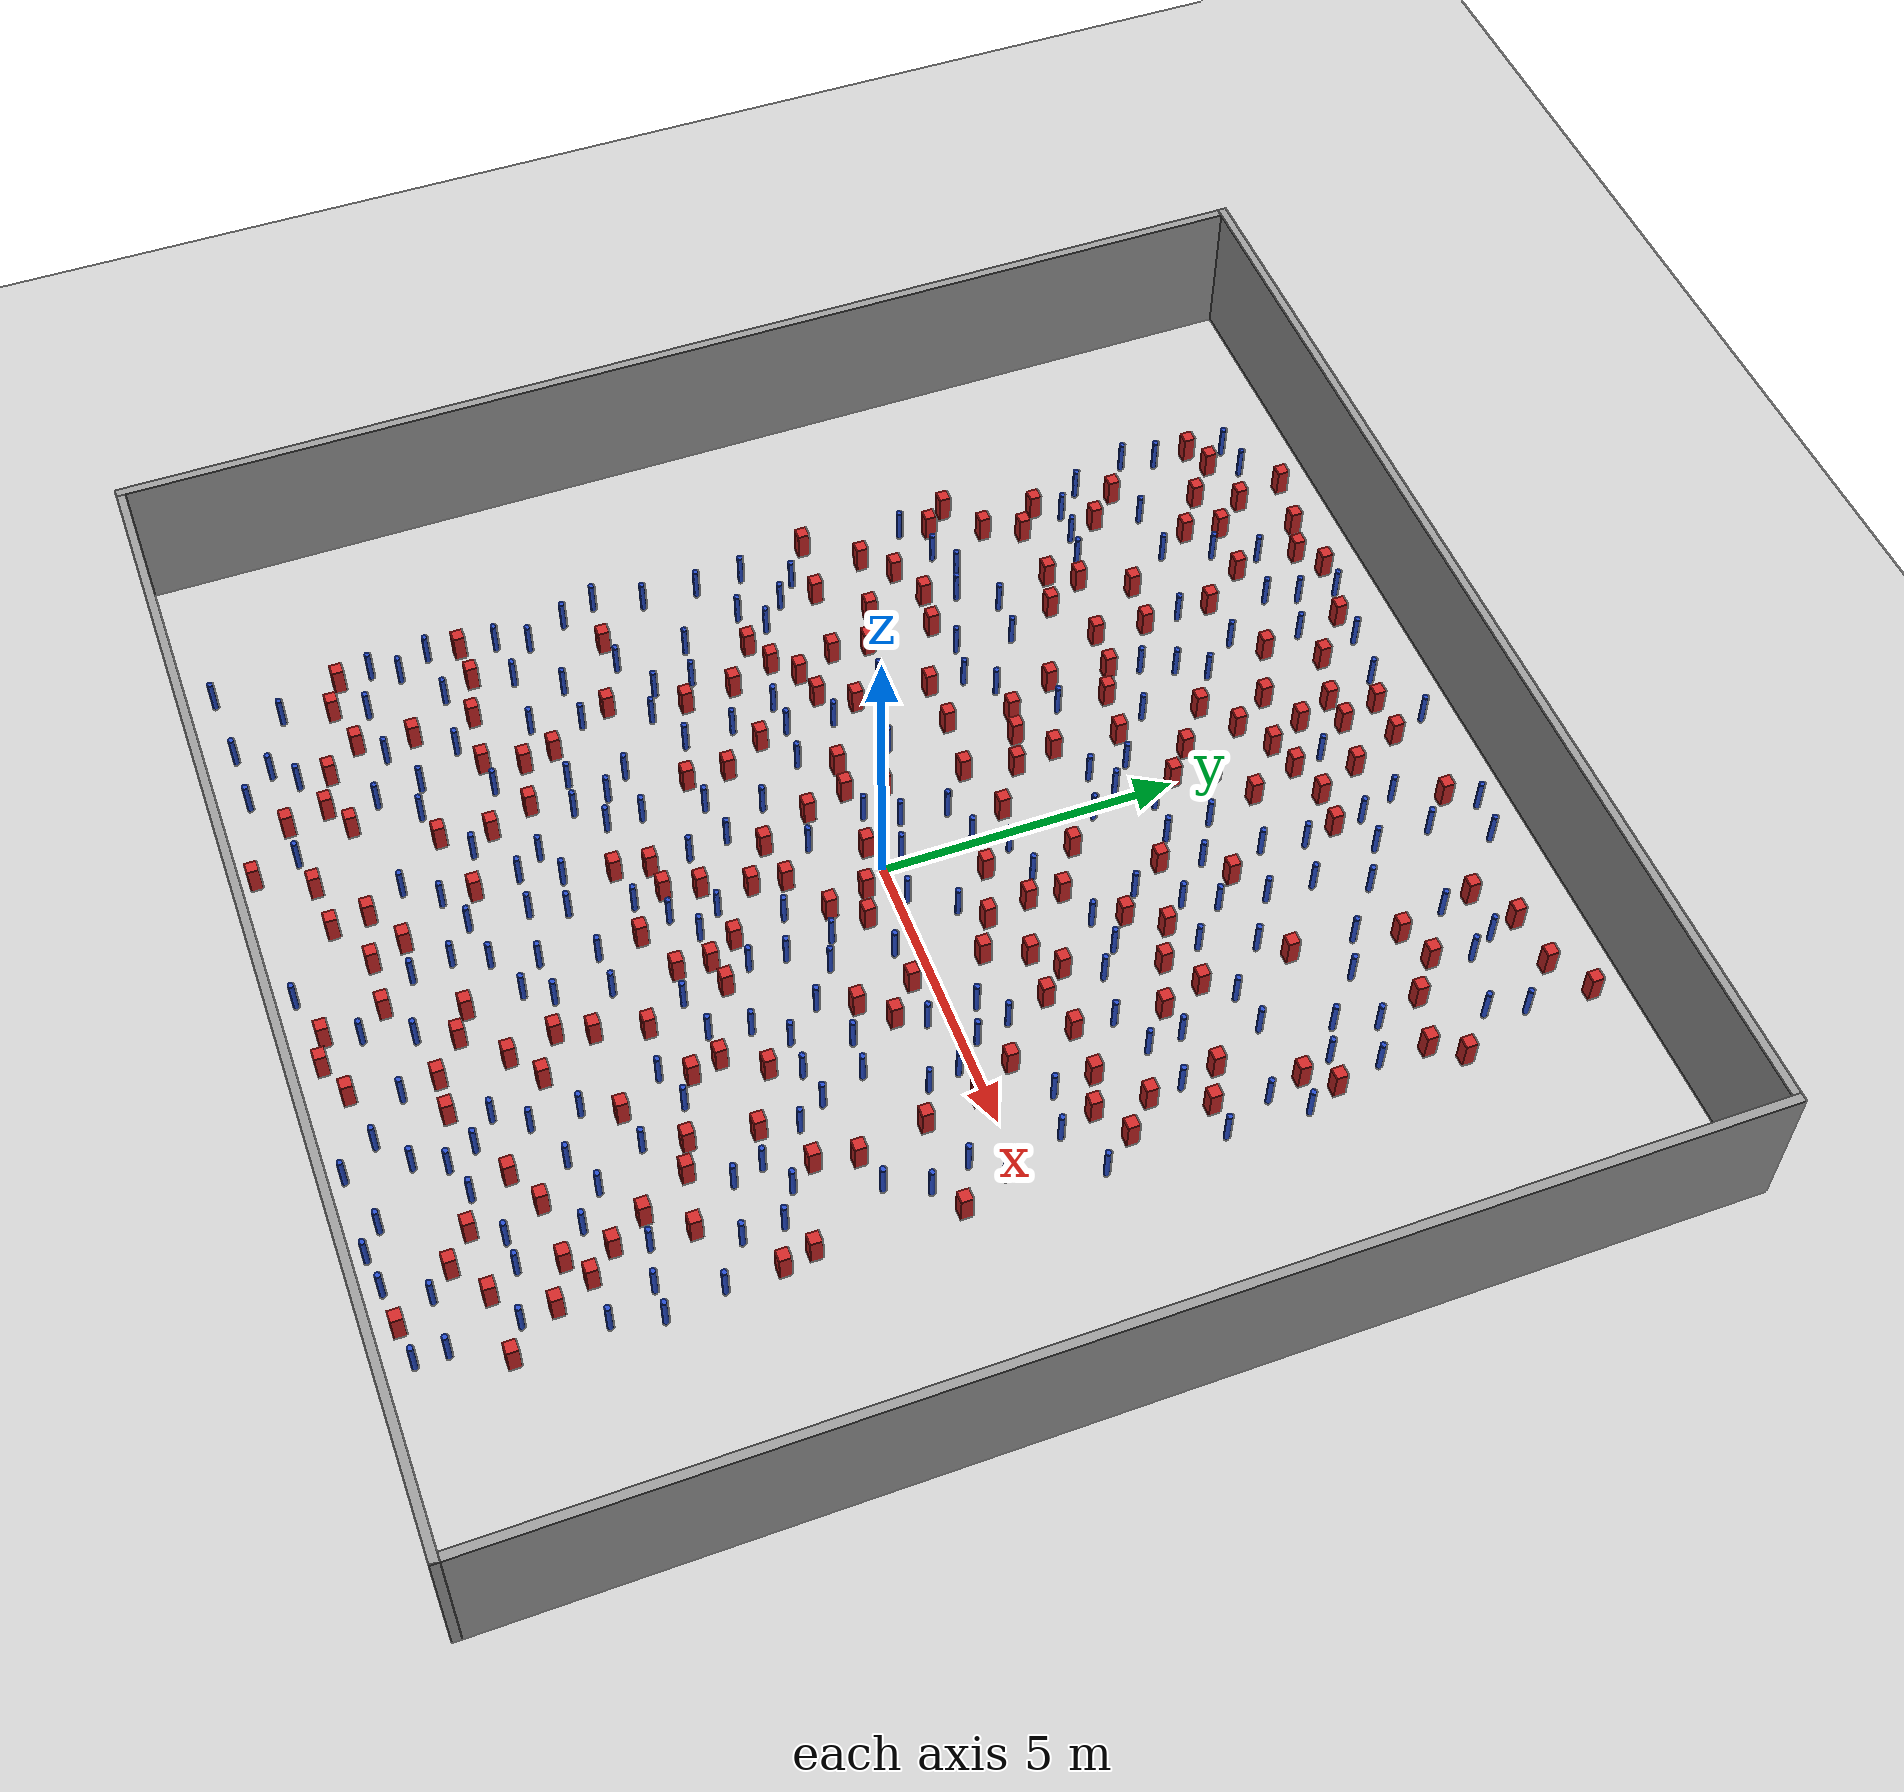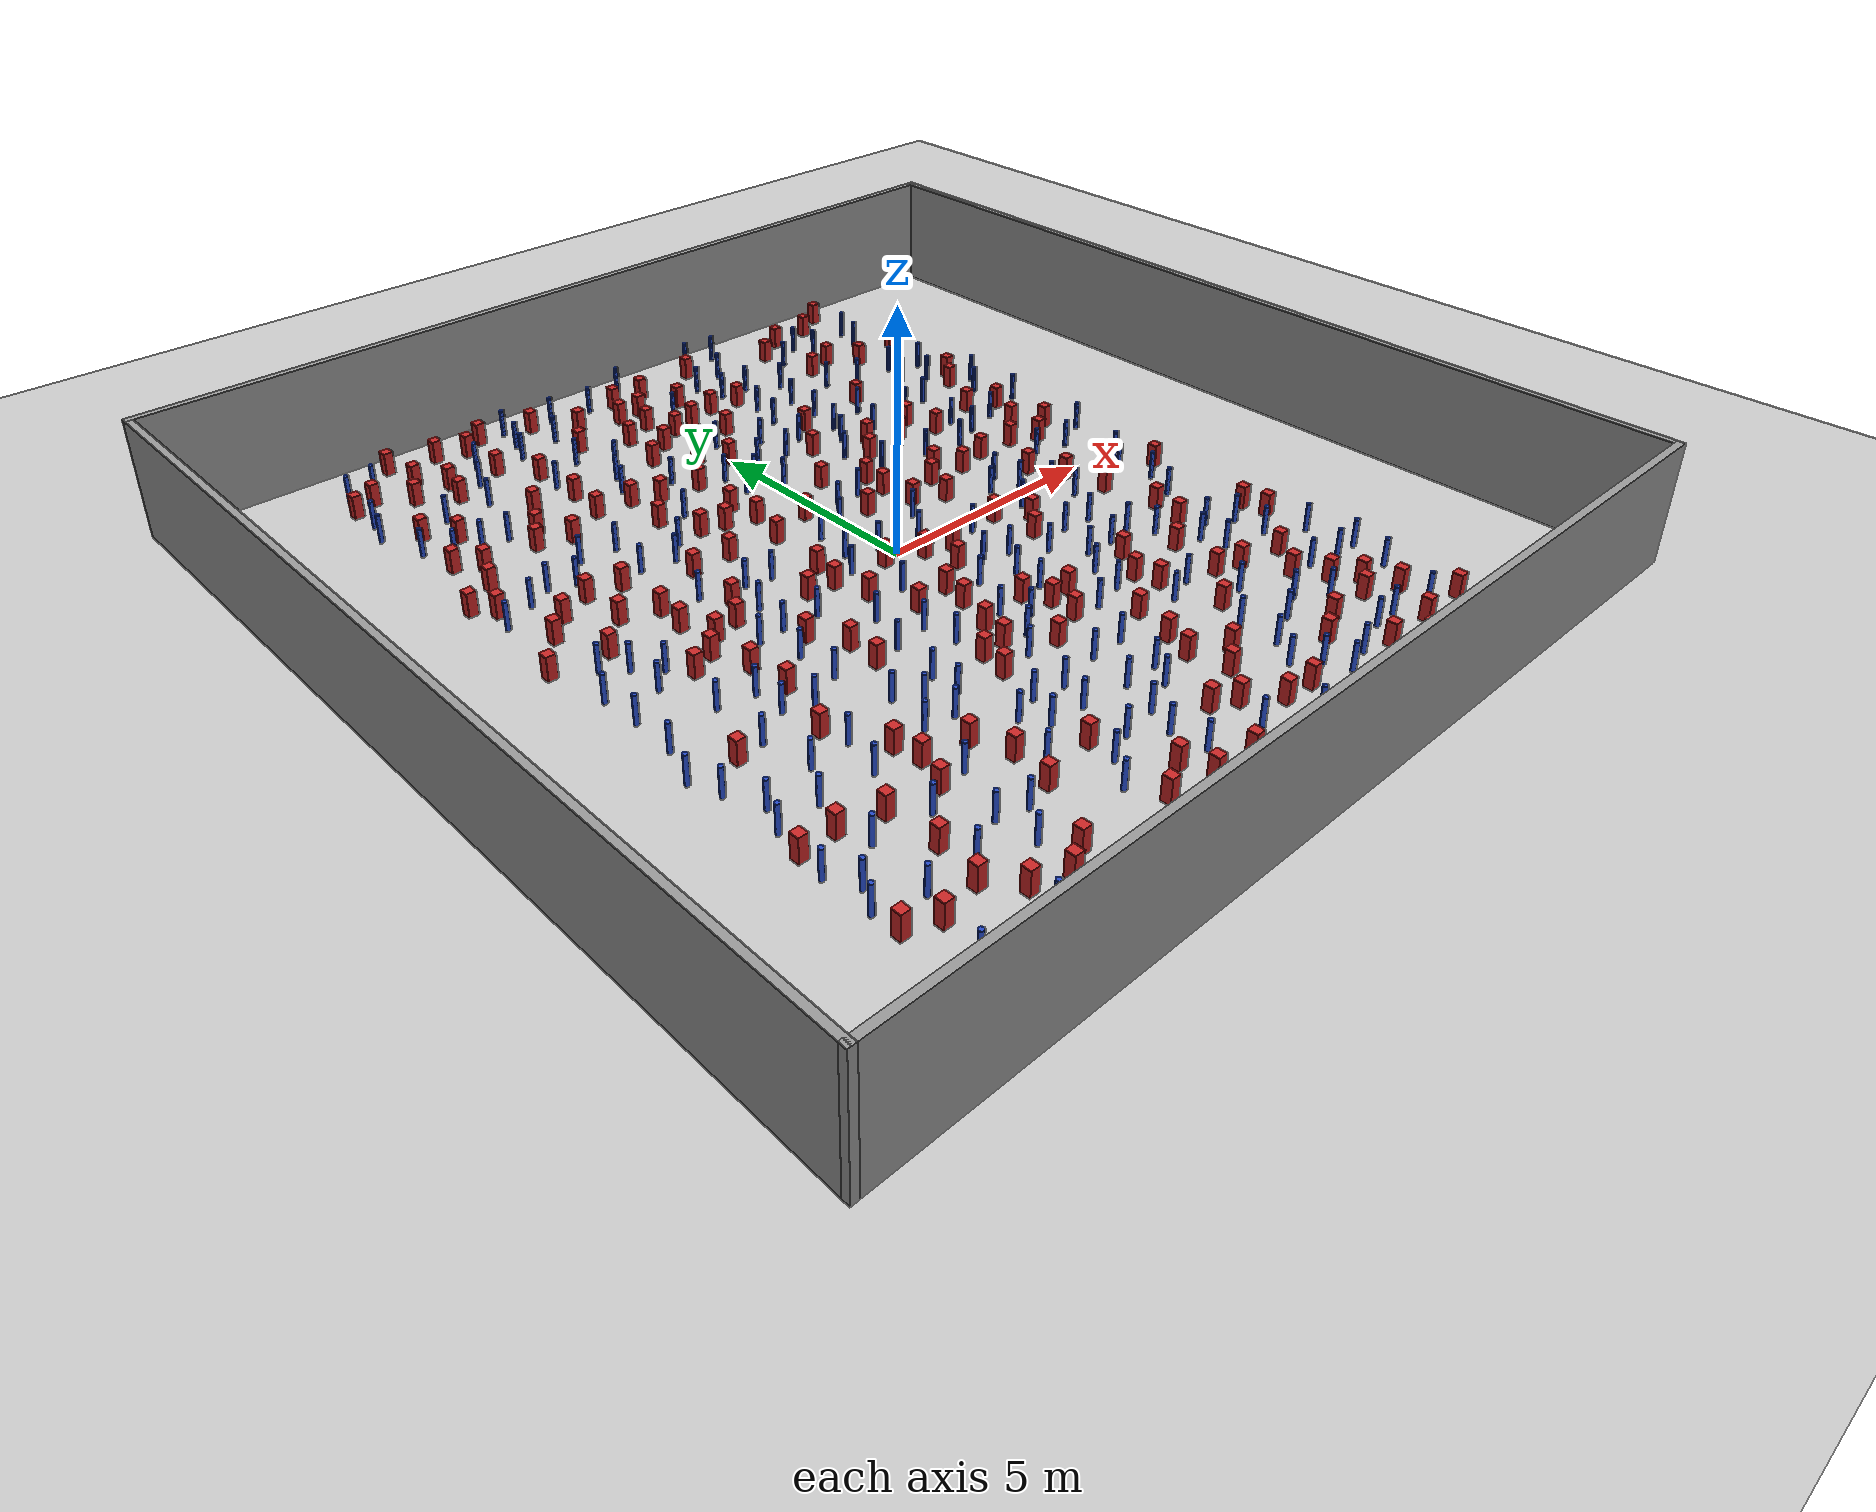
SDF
<sdf version="1.6">
 <world name="default">
  <light name="sun" type="directional">
   <pose>0 0 1000 0 -0 0</pose>
   <diffuse>0.8 0.8 0.8 1</diffuse>
   <specular>0.1 0.1 0.1 1</specular>
   <attenuation>
    <range>1000</range>
    <constant>0.9</constant>
    <linear>0.01</linear>
    <quadratic>0.001</quadratic>
   </attenuation>
   <direction>-0.5 0.5 -1</direction>
  </light>
  <model name="ground_plane">
   <static>1</static>
   <link name="link">
    <collision name="collision">
     <geometry><plane><normal>0 0 1</normal><size>100 100</size></plane></geometry>
     <surface><friction><ode><mu>100</mu><mu2>50</mu2></ode></friction></surface>
    </collision>
    <visual name="visual">
     <cast_shadows>0</cast_shadows>
     <geometry><plane><normal>0 0 1</normal><size>100 100</size></plane></geometry>
     <material>
      <ambient>1.0 1.0 1.0 1.0</ambient>
      <diffuse>0.8 0.8 0.8 1.0</diffuse>
      <specular>0.01 0.01 0.01 1.000000</specular>
     </material>
    </visual>
   </link>
  </model>
  <gravity>0 0 -9.8</gravity>
  <magnetic_field>6e-06 2.3e-05 -4.2e-05</magnetic_field>
  <atmosphere type="adiabatic"/>
  <physics name="default_physics" default="0" type="ode">
   <max_step_size>0.001</max_step_size>
   <real_time_factor>1</real_time_factor>
   <real_time_update_rate>1000</real_time_update_rate>
  </physics>
  <scene><ambient>0.4 0.4 0.4 1</ambient><background>0.7 0.7 0.7 1</background><shadows>1</shadows></scene>
  <spherical_coordinates>
   <surface_model>EARTH_WGS84</surface_model>
   <latitude_deg>0</latitude_deg>
   <longitude_deg>0</longitude_deg>
   <elevation>0</elevation>
   <heading_deg>0</heading_deg>
  </spherical_coordinates>
  <plugin name="gazebo_occupancy_map" filename="libgazebo_2Dmap_plugin.so">
   <map_resolution>0.05</map_resolution>
   <map_topic>generated_map</map_topic>
   <map_height>0.01</map_height>
   <map_size_x>50</map_size_x>
   <map_size_y>50</map_size_y>
  </plugin>
  <model name="NamedLocations">
   <static>true</static>
   <link name="DefaultStart"><pose>8.5 0 0 0 0 3.14</pose></link>
  </model>
  <model name="20x20_walls">
   <pose>0.044518 0.176112 0 0 -0 0</pose>
   <link name="Wall_1">
    <collision name="Wall_1_Collision">
     <geometry><box><size>20 0.15 2.5</size></box></geometry>
     <pose>0 0 1.25 0 -0 0</pose>
    </collision>
    <visual name="Wall_1_Visual">
     <pose>0 0 1.25 0 -0 0</pose>
     <geometry><box><size>20 0.15 2.5</size></box></geometry>
     <material>
      <script><uri>file://media/materials/scripts/gazebo.material</uri><name>Gazebo/Grey</name></script>
      <ambient>0.976471 0.992157 1 1</ambient>
     </material>
     <meta><layer>0</layer></meta>
    </visual>
    <pose>0 9.925 0 0 -0 0</pose>
   </link>
   <link name="Wall_3">
    <collision name="Wall_3_Collision">
     <geometry><box><size>20 0.15 2.5</size></box></geometry>
     <pose>0 0 1.25 0 -0 0</pose>
    </collision>
    <visual name="Wall_3_Visual">
     <pose>0 0 1.25 0 -0 0</pose>
     <geometry><box><size>20 0.15 2.5</size></box></geometry>
     <material>
      <script><uri>file://media/materials/scripts/gazebo.material</uri><name>Gazebo/Grey</name></script>
      <ambient>0.976471 0.992157 1 1</ambient>
     </material>
     <meta><layer>0</layer></meta>
    </visual>
    <pose>9.925 0 0 0 0 -1.5708</pose>
   </link>
   <link name="Wall_4">
    <collision name="Wall_4_Collision">
     <geometry><box><size>20 0.15 2.5</size></box></geometry>
     <pose>0 0 1.25 0 -0 0</pose>
    </collision>
    <visual name="Wall_4_Visual">
     <pose>0 0 1.25 0 -0 0</pose>
     <geometry><box><size>20 0.15 2.5</size></box></geometry>
     <material>
      <script><uri>file://media/materials/scripts/gazebo.material</uri><name>Gazebo/Grey</name></script>
      <ambient>0.976471 0.992157 1 1</ambient>
     </material>
     <meta><layer>0</layer></meta>
    </visual>
    <pose>0 -9.925 0 0 -0 3.14159</pose>
   </link>
   <link name="Wall_5">
    <collision name="Wall_5_Collision">
     <geometry><box><size>20 0.15 2.5</size></box></geometry>
     <pose>0 0 1.25 0 -0 0</pose>
    </collision>
    <visual name="Wall_5_Visual">
     <pose>0 0 1.25 0 -0 0</pose>
     <geometry><box><size>20 0.15 2.5</size></box></geometry>
     <material>
      <script><uri>file://media/materials/scripts/gazebo.material</uri><name>Gazebo/Grey</name></script>
      <ambient>0.976471 0.992157 1 1</ambient>
     </material>
     <meta><layer>0</layer></meta>
    </visual>
    <pose>-9.925 0 0 0 -0 1.5708</pose>
   </link>
   <static>1</static>
  </model>
  <model name="square_post_obstacle0">
   <static>true</static>
   <pose>-5.28354271369 8.56203770138 -4.36207812815e-07 3.75137919937e-06 9.77721102514e-07 2.47381364184e-05</pose>
   <link name="link">
    <pose>0 0 0.25 0 -0 0</pose>
    <inertial>
     <mass>100</mass>
     <inertia>
      <ixx>0.166667</ixx>
      <ixy>0</ixy>
      <ixz>0</ixz>
      <iyy>0.166667</iyy>
      <iyz>0</iyz>
      <izz>0.166667</izz>
     </inertia>
    </inertial>
    <collision name="collision"><geometry><box><size>.2 .2 .5</size></box></geometry></collision>
    <visual name="visual">
     <geometry><box><size>.2 .2 .5</size></box></geometry>
     <material>
      <script><name>Gazebo/Red</name><uri>file://media/materials/scripts/gazebo.material</uri></script>
     </material>
    </visual>
   </link>
  </model>
  <model name="square_post_obstacle1">
   <static>true</static>
   <pose>-4.15054993788 4.54803701752 -4.36207812815e-07 3.75137919937e-06 9.77721102514e-07 2.47381364184e-05</pose>
   <link name="link">
    <pose>0 0 0.25 0 -0 0</pose>
    <inertial>
     <mass>100</mass>
     <inertia>
      <ixx>0.166667</ixx>
      <ixy>0</ixy>
      <ixz>0</ixz>
      <iyy>0.166667</iyy>
      <iyz>0</iyz>
      <izz>0.166667</izz>
     </inertia>
    </inertial>
    <collision name="collision"><geometry><box><size>.2 .2 .5</size></box></geometry></collision>
    <visual name="visual">
     <geometry><box><size>.2 .2 .5</size></box></geometry>
     <material>
      <script><name>Gazebo/Red</name><uri>file://media/materials/scripts/gazebo.material</uri></script>
     </material>
    </visual>
   </link>
  </model>
  <model name="pole_obstacle0">
   <static>true</static>
   <pose>-1.26318567252 -2.81914517885 -3.09024884793e-07 -7.19054271912e-07 -2.11315075132e-07 -1.93935509263e-07</pose>
   <link name="link">
    <pose>0 0 0.3 0 -0 0</pose>
    <inertial>
     <mass>1</mass>
     <inertia><ixx>0.145833</ixx><ixy>0</ixy><ixz>0</ixz><iyy>0.145833</iyy><iyz>0</iyz><izz>0.125</izz></inertia>
    </inertial>
    <collision name="collision">
     <geometry><cylinder><radius>0.05</radius><length>.6</length></cylinder></geometry>
    </collision>
    <visual name="visual">
     <geometry><cylinder><radius>0.05</radius><length>.6</length></cylinder></geometry>
     <material>
      <script><name>Gazebo/Blue</name><uri>file://media/materials/scripts/gazebo.material</uri></script>
     </material>
    </visual>
   </link>
  </model>
  <model name="square_post_obstacle2">
   <static>true</static>
   <pose>-2.61837947253 3.90942713527 -4.36207812815e-07 3.75137919937e-06 9.77721102514e-07 2.47381364184e-05</pose>
   <link name="link">
    <pose>0 0 0.25 0 -0 0</pose>
    <inertial>
     <mass>100</mass>
     <inertia>
      <ixx>0.166667</ixx>
      <ixy>0</ixy>
      <ixz>0</ixz>
      <iyy>0.166667</iyy>
      <iyz>0</iyz>
      <izz>0.166667</izz>
     </inertia>
    </inertial>
    <collision name="collision"><geometry><box><size>.2 .2 .5</size></box></geometry></collision>
    <visual name="visual">
     <geometry><box><size>.2 .2 .5</size></box></geometry>
     <material>
      <script><name>Gazebo/Red</name><uri>file://media/materials/scripts/gazebo.material</uri></script>
     </material>
    </visual>
   </link>
  </model>
  <model name="pole_obstacle1">
   <static>true</static>
   <pose>5.58992759345 0.771042951277 -3.09024884793e-07 -7.19054271912e-07 -2.11315075134e-07 -1.93935509265e-07</pose>
   <link name="link">
    <pose>0 0 0.3 0 -0 0</pose>
    <inertial>
     <mass>1</mass>
     <inertia><ixx>0.145833</ixx><ixy>0</ixy><ixz>0</ixz><iyy>0.145833</iyy><iyz>0</iyz><izz>0.125</izz></inertia>
    </inertial>
    <collision name="collision">
     <geometry><cylinder><radius>0.05</radius><length>.6</length></cylinder></geometry>
    </collision>
    <visual name="visual">
     <geometry><cylinder><radius>0.05</radius><length>.6</length></cylinder></geometry>
     <material>
      <script><name>Gazebo/Blue</name><uri>file://media/materials/scripts/gazebo.material</uri></script>
     </material>
    </visual>
   </link>
  </model>
  <model name="square_post_obstacle3">
   <static>true</static>
   <pose>-6.00276046542 -5.0971328595 -4.36207812815e-07 3.75137919937e-06 9.77721102514e-07 2.47381364184e-05</pose>
   <link name="link">
    <pose>0 0 0.25 0 -0 0</pose>
    <inertial>
     <mass>100</mass>
     <inertia>
      <ixx>0.166667</ixx>
      <ixy>0</ixy>
      <ixz>0</ixz>
      <iyy>0.166667</iyy>
      <iyz>0</iyz>
      <izz>0.166667</izz>
     </inertia>
    </inertial>
    <collision name="collision"><geometry><box><size>.2 .2 .5</size></box></geometry></collision>
    <visual name="visual">
     <geometry><box><size>.2 .2 .5</size></box></geometry>
     <material>
      <script><name>Gazebo/Red</name><uri>file://media/materials/scripts/gazebo.material</uri></script>
     </material>
    </visual>
   </link>
  </model>
  <model name="pole_obstacle2">
   <static>true</static>
   <pose>0.370122349833 -1.7909447414 -3.09024884793e-07 -7.19054271912e-07 -2.11315075135e-07 -1.93935509265e-07</pose>
   <link name="link">
    <pose>0 0 0.3 0 -0 0</pose>
    <inertial>
     <mass>1</mass>
     <inertia><ixx>0.145833</ixx><ixy>0</ixy><ixz>0</ixz><iyy>0.145833</iyy><iyz>0</iyz><izz>0.125</izz></inertia>
    </inertial>
    <collision name="collision">
     <geometry><cylinder><radius>0.05</radius><length>.6</length></cylinder></geometry>
    </collision>
    <visual name="visual">
     <geometry><cylinder><radius>0.05</radius><length>.6</length></cylinder></geometry>
     <material>
      <script><name>Gazebo/Blue</name><uri>file://media/materials/scripts/gazebo.material</uri></script>
     </material>
    </visual>
   </link>
  </model>
  <model name="pole_obstacle3">
   <static>true</static>
   <pose>3.14973722396 2.48802405268 -3.09024884793e-07 -7.19054271912e-07 -2.11315075144e-07 -1.93935509271e-07</pose>
   <link name="link">
    <pose>0 0 0.3 0 -0 0</pose>
    <inertial>
     <mass>1</mass>
     <inertia><ixx>0.145833</ixx><ixy>0</ixy><ixz>0</ixz><iyy>0.145833</iyy><iyz>0</iyz><izz>0.125</izz></inertia>
    </inertial>
    <collision name="collision">
     <geometry><cylinder><radius>0.05</radius><length>.6</length></cylinder></geometry>
    </collision>
    <visual name="visual">
     <geometry><cylinder><radius>0.05</radius><length>.6</length></cylinder></geometry>
     <material>
      <script><name>Gazebo/Blue</name><uri>file://media/materials/scripts/gazebo.material</uri></script>
     </material>
    </visual>
   </link>
  </model>
  <model name="square_post_obstacle4">
   <static>true</static>
   <pose>-3.29330726181 5.02781933174 -4.36207812815e-07 3.75137919937e-06 9.77721102514e-07 2.47381364184e-05</pose>
   <link name="link">
    <pose>0 0 0.25 0 -0 0</pose>
    <inertial>
     <mass>100</mass>
     <inertia>
      <ixx>0.166667</ixx>
      <ixy>0</ixy>
      <ixz>0</ixz>
      <iyy>0.166667</iyy>
      <iyz>0</iyz>
      <izz>0.166667</izz>
     </inertia>
    </inertial>
    <collision name="collision"><geometry><box><size>.2 .2 .5</size></box></geometry></collision>
    <visual name="visual">
     <geometry><box><size>.2 .2 .5</size></box></geometry>
     <material>
      <script><name>Gazebo/Red</name><uri>file://media/materials/scripts/gazebo.material</uri></script>
     </material>
    </visual>
   </link>
  </model>
  <model name="square_post_obstacle5">
   <static>true</static>
   <pose>0.797605377734 -3.69238944444 -4.36207812815e-07 3.75137919937e-06 9.77721102514e-07 2.47381364184e-05</pose>
   <link name="link">
    <pose>0 0 0.25 0 -0 0</pose>
    <inertial>
     <mass>100</mass>
     <inertia>
      <ixx>0.166667</ixx>
      <ixy>0</ixy>
      <ixz>0</ixz>
      <iyy>0.166667</iyy>
      <iyz>0</iyz>
      <izz>0.166667</izz>
     </inertia>
    </inertial>
    <collision name="collision"><geometry><box><size>.2 .2 .5</size></box></geometry></collision>
    <visual name="visual">
     <geometry><box><size>.2 .2 .5</size></box></geometry>
     <material>
      <script><name>Gazebo/Red</name><uri>file://media/materials/scripts/gazebo.material</uri></script>
     </material>
    </visual>
   </link>
  </model>
  <model name="square_post_obstacle6">
   <static>true</static>
   <pose>0.887163632337 -0.576067695528 -4.36207812815e-07 3.75137919937e-06 9.77721102514e-07 2.47381364184e-05</pose>
   <link name="link">
    <pose>0 0 0.25 0 -0 0</pose>
    <inertial>
     <mass>100</mass>
     <inertia>
      <ixx>0.166667</ixx>
      <ixy>0</ixy>
      <ixz>0</ixz>
      <iyy>0.166667</iyy>
      <iyz>0</iyz>
      <izz>0.166667</izz>
     </inertia>
    </inertial>
    <collision name="collision"><geometry><box><size>.2 .2 .5</size></box></geometry></collision>
    <visual name="visual">
     <geometry><box><size>.2 .2 .5</size></box></geometry>
     <material>
      <script><name>Gazebo/Red</name><uri>file://media/materials/scripts/gazebo.material</uri></script>
     </material>
    </visual>
   </link>
  </model>
  <model name="pole_obstacle4">
   <static>true</static>
   <pose>5.01785423754 -8.72050945482 -3.09024884793e-07 -7.19054271912e-07 -2.1131507513e-07 -1.93935509261e-07</pose>
   <link name="link">
    <pose>0 0 0.3 0 -0 0</pose>
    <inertial>
     <mass>1</mass>
     <inertia><ixx>0.145833</ixx><ixy>0</ixy><ixz>0</ixz><iyy>0.145833</iyy><iyz>0</iyz><izz>0.125</izz></inertia>
    </inertial>
    <collision name="collision">
     <geometry><cylinder><radius>0.05</radius><length>.6</length></cylinder></geometry>
    </collision>
    <visual name="visual">
     <geometry><cylinder><radius>0.05</radius><length>.6</length></cylinder></geometry>
     <material>
      <script><name>Gazebo/Blue</name><uri>file://media/materials/scripts/gazebo.material</uri></script>
     </material>
    </visual>
   </link>
  </model>
  <model name="pole_obstacle5">
   <static>true</static>
   <pose>3.83661777627 6.42022486806 -3.09024884793e-07 -7.19054271912e-07 -2.11315075134e-07 -1.93935509266e-07</pose>
   <link name="link">
    <pose>0 0 0.3 0 -0 0</pose>
    <inertial>
     <mass>1</mass>
     <inertia><ixx>0.145833</ixx><ixy>0</ixy><ixz>0</ixz><iyy>0.145833</iyy><iyz>0</iyz><izz>0.125</izz></inertia>
    </inertial>
    <collision name="collision">
     <geometry><cylinder><radius>0.05</radius><length>.6</length></cylinder></geometry>
    </collision>
    <visual name="visual">
     <geometry><cylinder><radius>0.05</radius><length>.6</length></cylinder></geometry>
     <material>
      <script><name>Gazebo/Blue</name><uri>file://media/materials/scripts/gazebo.material</uri></script>
     </material>
    </visual>
   </link>
  </model>
  <model name="square_post_obstacle7">
   <static>true</static>
   <pose>6.27799123049 -3.83323502862 -4.36207812815e-07 3.75137919937e-06 9.77721102514e-07 2.47381364184e-05</pose>
   <link name="link">
    <pose>0 0 0.25 0 -0 0</pose>
    <inertial>
     <mass>100</mass>
     <inertia>
      <ixx>0.166667</ixx>
      <ixy>0</ixy>
      <ixz>0</ixz>
      <iyy>0.166667</iyy>
      <iyz>0</iyz>
      <izz>0.166667</izz>
     </inertia>
    </inertial>
    <collision name="collision"><geometry><box><size>.2 .2 .5</size></box></geometry></collision>
    <visual name="visual">
     <geometry><box><size>.2 .2 .5</size></box></geometry>
     <material>
      <script><name>Gazebo/Red</name><uri>file://media/materials/scripts/gazebo.material</uri></script>
     </material>
    </visual>
   </link>
  </model>
  <model name="square_post_obstacle8">
   <static>true</static>
   <pose>-1.87293484961 -7.90573309365 -4.36207812815e-07 3.75137919937e-06 9.77721102514e-07 2.47381364184e-05</pose>
   <link name="link">
    <pose>0 0 0.25 0 -0 0</pose>
    <inertial>
     <mass>100</mass>
     <inertia>
      <ixx>0.166667</ixx>
      <ixy>0</ixy>
      <ixz>0</ixz>
      <iyy>0.166667</iyy>
      <iyz>0</iyz>
      <izz>0.166667</izz>
     </inertia>
    </inertial>
    <collision name="collision"><geometry><box><size>.2 .2 .5</size></box></geometry></collision>
    <visual name="visual">
     <geometry><box><size>.2 .2 .5</size></box></geometry>
     <material>
      <script><name>Gazebo/Red</name><uri>file://media/materials/scripts/gazebo.material</uri></script>
     </material>
    </visual>
   </link>
  </model>
  <model name="pole_obstacle6">
   <static>true</static>
   <pose>2.53744129503 4.69287355189 -3.09024884793e-07 -7.19054271912e-07 -2.11315075134e-07 -1.93935509266e-07</pose>
   <link name="link">
    <pose>0 0 0.3 0 -0 0</pose>
    <inertial>
     <mass>1</mass>
     <inertia><ixx>0.145833</ixx><ixy>0</ixy><ixz>0</ixz><iyy>0.145833</iyy><iyz>0</iyz><izz>0.125</izz></inertia>
    </inertial>
    <collision name="collision">
     <geometry><cylinder><radius>0.05</radius><length>.6</length></cylinder></geometry>
    </collision>
    <visual name="visual">
     <geometry><cylinder><radius>0.05</radius><length>.6</length></cylinder></geometry>
     <material>
      <script><name>Gazebo/Blue</name><uri>file://media/materials/scripts/gazebo.material</uri></script>
     </material>
    </visual>
   </link>
  </model>
  <model name="pole_obstacle7">
   <static>true</static>
   <pose>-0.116427570041 -5.64152838768 -3.09024884793e-07 -7.19054271912e-07 -2.11315075136e-07 -1.93935509266e-07</pose>
   <link name="link">
    <pose>0 0 0.3 0 -0 0</pose>
    <inertial>
     <mass>1</mass>
     <inertia><ixx>0.145833</ixx><ixy>0</ixy><ixz>0</ixz><iyy>0.145833</iyy><iyz>0</iyz><izz>0.125</izz></inertia>
    </inertial>
    <collision name="collision">
     <geometry><cylinder><radius>0.05</radius><length>.6</length></cylinder></geometry>
    </collision>
    <visual name="visual">
     <geometry><cylinder><radius>0.05</radius><length>.6</length></cylinder></geometry>
     <material>
      <script><name>Gazebo/Blue</name><uri>file://media/materials/scripts/gazebo.material</uri></script>
     </material>
    </visual>
   </link>
  </model>
  <model name="square_post_obstacle9">
   <static>true</static>
   <pose>2.24990376615 -0.350922140613 -4.36207812815e-07 3.75137919937e-06 9.77721102514e-07 2.47381364184e-05</pose>
   <link name="link">
    <pose>0 0 0.25 0 -0 0</pose>
    <inertial>
     <mass>100</mass>
     <inertia>
      <ixx>0.166667</ixx>
      <ixy>0</ixy>
      <ixz>0</ixz>
      <iyy>0.166667</iyy>
      <iyz>0</iyz>
      <izz>0.166667</izz>
     </inertia>
    </inertial>
    <collision name="collision"><geometry><box><size>.2 .2 .5</size></box></geometry></collision>
    <visual name="visual">
     <geometry><box><size>.2 .2 .5</size></box></geometry>
     <material>
      <script><name>Gazebo/Red</name><uri>file://media/materials/scripts/gazebo.material</uri></script>
     </material>
    </visual>
   </link>
  </model>
  <model name="square_post_obstacle10">
   <static>true</static>
   <pose>3.42457370579 -7.12895520074 -4.36207812815e-07 3.75137919937e-06 9.77721102514e-07 2.47381364184e-05</pose>
   <link name="link">
    <pose>0 0 0.25 0 -0 0</pose>
    <inertial>
     <mass>100</mass>
     <inertia>
      <ixx>0.166667</ixx>
      <ixy>0</ixy>
      <ixz>0</ixz>
      <iyy>0.166667</iyy>
      <iyz>0</iyz>
      <izz>0.166667</izz>
     </inertia>
    </inertial>
    <collision name="collision"><geometry><box><size>.2 .2 .5</size></box></geometry></collision>
    <visual name="visual">
     <geometry><box><size>.2 .2 .5</size></box></geometry>
     <material>
      <script><name>Gazebo/Red</name><uri>file://media/materials/scripts/gazebo.material</uri></script>
     </material>
    </visual>
   </link>
  </model>
  <model name="square_post_obstacle11">
   <static>true</static>
   <pose>1.97547546492 -6.18665159734 -4.36207812815e-07 3.75137919937e-06 9.77721102514e-07 2.47381364184e-05</pose>
   <link name="link">
    <pose>0 0 0.25 0 -0 0</pose>
    <inertial>
     <mass>100</mass>
     <inertia>
      <ixx>0.166667</ixx>
      <ixy>0</ixy>
      <ixz>0</ixz>
      <iyy>0.166667</iyy>
      <iyz>0</iyz>
      <izz>0.166667</izz>
     </inertia>
    </inertial>
    <collision name="collision"><geometry><box><size>.2 .2 .5</size></box></geometry></collision>
    <visual name="visual">
     <geometry><box><size>.2 .2 .5</size></box></geometry>
     <material>
      <script><name>Gazebo/Red</name><uri>file://media/materials/scripts/gazebo.material</uri></script>
     </material>
    </visual>
   </link>
  </model>
  <model name="square_post_obstacle12">
   <static>true</static>
   <pose>-0.249569324833 -1.54666862833 -4.36207812815e-07 3.75137919937e-06 9.77721102514e-07 2.47381364184e-05</pose>
   <link name="link">
    <pose>0 0 0.25 0 -0 0</pose>
    <inertial>
     <mass>100</mass>
     <inertia>
      <ixx>0.166667</ixx>
      <ixy>0</ixy>
      <ixz>0</ixz>
      <iyy>0.166667</iyy>
      <iyz>0</iyz>
      <izz>0.166667</izz>
     </inertia>
    </inertial>
    <collision name="collision"><geometry><box><size>.2 .2 .5</size></box></geometry></collision>
    <visual name="visual">
     <geometry><box><size>.2 .2 .5</size></box></geometry>
     <material>
      <script><name>Gazebo/Red</name><uri>file://media/materials/scripts/gazebo.material</uri></script>
     </material>
    </visual>
   </link>
  </model>
  <model name="square_post_obstacle13">
   <static>true</static>
   <pose>3.27607757877 3.43404862615 -4.36207812815e-07 3.75137919937e-06 9.77721102514e-07 2.47381364184e-05</pose>
   <link name="link">
    <pose>0 0 0.25 0 -0 0</pose>
    <inertial>
     <mass>100</mass>
     <inertia>
      <ixx>0.166667</ixx>
      <ixy>0</ixy>
      <ixz>0</ixz>
      <iyy>0.166667</iyy>
      <iyz>0</iyz>
      <izz>0.166667</izz>
     </inertia>
    </inertial>
    <collision name="collision"><geometry><box><size>.2 .2 .5</size></box></geometry></collision>
    <visual name="visual">
     <geometry><box><size>.2 .2 .5</size></box></geometry>
     <material>
      <script><name>Gazebo/Red</name><uri>file://media/materials/scripts/gazebo.material</uri></script>
     </material>
    </visual>
   </link>
  </model>
  <model name="pole_obstacle8">
   <static>true</static>
   <pose>1.89174017041 6.5032278963 -3.09024884793e-07 -7.19054271912e-07 -2.11315075134e-07 -1.93935509265e-07</pose>
   <link name="link">
    <pose>0 0 0.3 0 -0 0</pose>
    <inertial>
     <mass>1</mass>
     <inertia><ixx>0.145833</ixx><ixy>0</ixy><ixz>0</ixz><iyy>0.145833</iyy><iyz>0</iyz><izz>0.125</izz></inertia>
    </inertial>
    <collision name="collision">
     <geometry><cylinder><radius>0.05</radius><length>.6</length></cylinder></geometry>
    </collision>
    <visual name="visual">
     <geometry><cylinder><radius>0.05</radius><length>.6</length></cylinder></geometry>
     <material>
      <script><name>Gazebo/Blue</name><uri>file://media/materials/scripts/gazebo.material</uri></script>
     </material>
    </visual>
   </link>
  </model>
  <model name="square_post_obstacle14">
   <static>true</static>
   <pose>6.28255106497 -1.03655964406 -4.36207812815e-07 3.75137919937e-06 9.77721102514e-07 2.47381364184e-05</pose>
   <link name="link">
    <pose>0 0 0.25 0 -0 0</pose>
    <inertial>
     <mass>100</mass>
     <inertia>
      <ixx>0.166667</ixx>
      <ixy>0</ixy>
      <ixz>0</ixz>
      <iyy>0.166667</iyy>
      <iyz>0</iyz>
      <izz>0.166667</izz>
     </inertia>
    </inertial>
    <collision name="collision"><geometry><box><size>.2 .2 .5</size></box></geometry></collision>
    <visual name="visual">
     <geometry><box><size>.2 .2 .5</size></box></geometry>
     <material>
      <script><name>Gazebo/Red</name><uri>file://media/materials/scripts/gazebo.material</uri></script>
     </material>
    </visual>
   </link>
  </model>
  <model name="square_post_obstacle15">
   <static>true</static>
   <pose>5.29516359935 -9.3053907383 -4.36207812815e-07 3.75137919937e-06 9.77721102514e-07 2.47381364184e-05</pose>
   <link name="link">
    <pose>0 0 0.25 0 -0 0</pose>
    <inertial>
     <mass>100</mass>
     <inertia>
      <ixx>0.166667</ixx>
      <ixy>0</ixy>
      <ixz>0</ixz>
      <iyy>0.166667</iyy>
      <iyz>0</iyz>
      <izz>0.166667</izz>
     </inertia>
    </inertial>
    <collision name="collision"><geometry><box><size>.2 .2 .5</size></box></geometry></collision>
    <visual name="visual">
     <geometry><box><size>.2 .2 .5</size></box></geometry>
     <material>
      <script><name>Gazebo/Red</name><uri>file://media/materials/scripts/gazebo.material</uri></script>
     </material>
    </visual>
   </link>
  </model>
  <model name="square_post_obstacle16">
   <static>true</static>
   <pose>4.30705514549 -4.66671936172 -4.36207812815e-07 3.75137919937e-06 9.77721102514e-07 2.47381364184e-05</pose>
   <link name="link">
    <pose>0 0 0.25 0 -0 0</pose>
    <inertial>
     <mass>100</mass>
     <inertia>
      <ixx>0.166667</ixx>
      <ixy>0</ixy>
      <ixz>0</ixz>
      <iyy>0.166667</iyy>
      <iyz>0</iyz>
      <izz>0.166667</izz>
     </inertia>
    </inertial>
    <collision name="collision"><geometry><box><size>.2 .2 .5</size></box></geometry></collision>
    <visual name="visual">
     <geometry><box><size>.2 .2 .5</size></box></geometry>
     <material>
      <script><name>Gazebo/Red</name><uri>file://media/materials/scripts/gazebo.material</uri></script>
     </material>
    </visual>
   </link>
  </model>
  <model name="pole_obstacle9">
   <static>true</static>
   <pose>-2.79973097755 1.02646332881 -3.09024884848e-07 -7.19054271902e-07 -2.11315075202e-07 -1.93935509288e-07</pose>
   <link name="link">
    <pose>0 0 0.3 0 -0 0</pose>
    <inertial>
     <mass>1</mass>
     <inertia><ixx>0.145833</ixx><ixy>0</ixy><ixz>0</ixz><iyy>0.145833</iyy><iyz>0</iyz><izz>0.125</izz></inertia>
    </inertial>
    <collision name="collision">
     <geometry><cylinder><radius>0.05</radius><length>.6</length></cylinder></geometry>
    </collision>
    <visual name="visual">
     <geometry><cylinder><radius>0.05</radius><length>.6</length></cylinder></geometry>
     <material>
      <script><name>Gazebo/Blue</name><uri>file://media/materials/scripts/gazebo.material</uri></script>
     </material>
    </visual>
   </link>
  </model>
  <model name="square_post_obstacle17">
   <static>true</static>
   <pose>0.836642216668 -7.19141728706 -4.36207812815e-07 3.75137919937e-06 9.77721102514e-07 2.47381364184e-05</pose>
   <link name="link">
    <pose>0 0 0.25 0 -0 0</pose>
    <inertial>
     <mass>100</mass>
     <inertia>
      <ixx>0.166667</ixx>
      <ixy>0</ixy>
      <ixz>0</ixz>
      <iyy>0.166667</iyy>
      <iyz>0</iyz>
      <izz>0.166667</izz>
     </inertia>
    </inertial>
    <collision name="collision"><geometry><box><size>.2 .2 .5</size></box></geometry></collision>
    <visual name="visual">
     <geometry><box><size>.2 .2 .5</size></box></geometry>
     <material>
      <script><name>Gazebo/Red</name><uri>file://media/materials/scripts/gazebo.material</uri></script>
     </material>
    </visual>
   </link>
  </model>
  <model name="square_post_obstacle18">
   <static>true</static>
   <pose>-3.2683818954 7.10099502662 -4.36207812815e-07 3.75137919937e-06 9.77721102514e-07 2.47381364184e-05</pose>
   <link name="link">
    <pose>0 0 0.25 0 -0 0</pose>
    <inertial>
     <mass>100</mass>
     <inertia>
      <ixx>0.166667</ixx>
      <ixy>0</ixy>
      <ixz>0</ixz>
      <iyy>0.166667</iyy>
      <iyz>0</iyz>
      <izz>0.166667</izz>
     </inertia>
    </inertial>
    <collision name="collision"><geometry><box><size>.2 .2 .5</size></box></geometry></collision>
    <visual name="visual">
     <geometry><box><size>.2 .2 .5</size></box></geometry>
     <material>
      <script><name>Gazebo/Red</name><uri>file://media/materials/scripts/gazebo.material</uri></script>
     </material>
    </visual>
   </link>
  </model>
  <model name="pole_obstacle10">
   <static>true</static>
   <pose>1.36425432777 -3.76695761919 -3.09024884793e-07 -7.19054271912e-07 -2.11315075132e-07 -1.93935509263e-07</pose>
   <link name="link">
    <pose>0 0 0.3 0 -0 0</pose>
    <inertial>
     <mass>1</mass>
     <inertia><ixx>0.145833</ixx><ixy>0</ixy><ixz>0</ixz><iyy>0.145833</iyy><iyz>0</iyz><izz>0.125</izz></inertia>
    </inertial>
    <collision name="collision">
     <geometry><cylinder><radius>0.05</radius><length>.6</length></cylinder></geometry>
    </collision>
    <visual name="visual">
     <geometry><cylinder><radius>0.05</radius><length>.6</length></cylinder></geometry>
     <material>
      <script><name>Gazebo/Blue</name><uri>file://media/materials/scripts/gazebo.material</uri></script>
     </material>
    </visual>
   </link>
  </model>
  <model name="square_post_obstacle19">
   <static>true</static>
   <pose>-5.93158634506 4.75254016513 -4.36207812815e-07 3.75137919937e-06 9.77721102514e-07 2.47381364184e-05</pose>
   <link name="link">
    <pose>0 0 0.25 0 -0 0</pose>
    <inertial>
     <mass>100</mass>
     <inertia>
      <ixx>0.166667</ixx>
      <ixy>0</ixy>
      <ixz>0</ixz>
      <iyy>0.166667</iyy>
      <iyz>0</iyz>
      <izz>0.166667</izz>
     </inertia>
    </inertial>
    <collision name="collision"><geometry><box><size>.2 .2 .5</size></box></geometry></collision>
    <visual name="visual">
     <geometry><box><size>.2 .2 .5</size></box></geometry>
     <material>
      <script><name>Gazebo/Red</name><uri>file://media/materials/scripts/gazebo.material</uri></script>
     </material>
    </visual>
   </link>
  </model>
  <model name="pole_obstacle11">
   <static>true</static>
   <pose>-4.52643800506 3.75983450144 -3.09024884793e-07 -7.19054271912e-07 -2.11315075144e-07 -1.93935509269e-07</pose>
   <link name="link">
    <pose>0 0 0.3 0 -0 0</pose>
    <inertial>
     <mass>1</mass>
     <inertia><ixx>0.145833</ixx><ixy>0</ixy><ixz>0</ixz><iyy>0.145833</iyy><iyz>0</iyz><izz>0.125</izz></inertia>
    </inertial>
    <collision name="collision">
     <geometry><cylinder><radius>0.05</radius><length>.6</length></cylinder></geometry>
    </collision>
    <visual name="visual">
     <geometry><cylinder><radius>0.05</radius><length>.6</length></cylinder></geometry>
     <material>
      <script><name>Gazebo/Blue</name><uri>file://media/materials/scripts/gazebo.material</uri></script>
     </material>
    </visual>
   </link>
  </model>
  <model name="square_post_obstacle20">
   <static>true</static>
   <pose>1.25655331617 -9.02356234698 -4.36207812815e-07 3.75137919937e-06 9.77721102514e-07 2.47381364184e-05</pose>
   <link name="link">
    <pose>0 0 0.25 0 -0 0</pose>
    <inertial>
     <mass>100</mass>
     <inertia>
      <ixx>0.166667</ixx>
      <ixy>0</ixy>
      <ixz>0</ixz>
      <iyy>0.166667</iyy>
      <iyz>0</iyz>
      <izz>0.166667</izz>
     </inertia>
    </inertial>
    <collision name="collision"><geometry><box><size>.2 .2 .5</size></box></geometry></collision>
    <visual name="visual">
     <geometry><box><size>.2 .2 .5</size></box></geometry>
     <material>
      <script><name>Gazebo/Red</name><uri>file://media/materials/scripts/gazebo.material</uri></script>
     </material>
    </visual>
   </link>
  </model>
  <model name="pole_obstacle12">
   <static>true</static>
   <pose>4.45089515591 -7.46767784374 -3.09024884793e-07 -7.19054271911e-07 -2.1131507516e-07 -1.93935509277e-07</pose>
   <link name="link">
    <pose>0 0 0.3 0 -0 0</pose>
    <inertial>
     <mass>1</mass>
     <inertia><ixx>0.145833</ixx><ixy>0</ixy><ixz>0</ixz><iyy>0.145833</iyy><iyz>0</iyz><izz>0.125</izz></inertia>
    </inertial>
    <collision name="collision">
     <geometry><cylinder><radius>0.05</radius><length>.6</length></cylinder></geometry>
    </collision>
    <visual name="visual">
     <geometry><cylinder><radius>0.05</radius><length>.6</length></cylinder></geometry>
     <material>
      <script><name>Gazebo/Blue</name><uri>file://media/materials/scripts/gazebo.material</uri></script>
     </material>
    </visual>
   </link>
  </model>
  <model name="square_post_obstacle21">
   <static>true</static>
   <pose>-0.0880051230226 6.8211781 -4.36207812815e-07 3.75137919937e-06 9.77721102514e-07 2.47381364184e-05</pose>
   <link name="link">
    <pose>0 0 0.25 0 -0 0</pose>
    <inertial>
     <mass>100</mass>
     <inertia>
      <ixx>0.166667</ixx>
      <ixy>0</ixy>
      <ixz>0</ixz>
      <iyy>0.166667</iyy>
      <iyz>0</iyz>
      <izz>0.166667</izz>
     </inertia>
    </inertial>
    <collision name="collision"><geometry><box><size>.2 .2 .5</size></box></geometry></collision>
    <visual name="visual">
     <geometry><box><size>.2 .2 .5</size></box></geometry>
     <material>
      <script><name>Gazebo/Red</name><uri>file://media/materials/scripts/gazebo.material</uri></script>
     </material>
    </visual>
   </link>
  </model>
  <model name="pole_obstacle13">
   <static>true</static>
   <pose>-2.16814189125 6.00477530142 -3.09024884793e-07 -7.19054271912e-07 -2.11315075134e-07 -1.93935509266e-07</pose>
   <link name="link">
    <pose>0 0 0.3 0 -0 0</pose>
    <inertial>
     <mass>1</mass>
     <inertia><ixx>0.145833</ixx><ixy>0</ixy><ixz>0</ixz><iyy>0.145833</iyy><iyz>0</iyz><izz>0.125</izz></inertia>
    </inertial>
    <collision name="collision">
     <geometry><cylinder><radius>0.05</radius><length>.6</length></cylinder></geometry>
    </collision>
    <visual name="visual">
     <geometry><cylinder><radius>0.05</radius><length>.6</length></cylinder></geometry>
     <material>
      <script><name>Gazebo/Blue</name><uri>file://media/materials/scripts/gazebo.material</uri></script>
     </material>
    </visual>
   </link>
  </model>
  <model name="square_post_obstacle22">
   <static>true</static>
   <pose>0.770295329065 7.91233904299 -4.36207812815e-07 3.75137919937e-06 9.77721102514e-07 2.47381364184e-05</pose>
   <link name="link">
    <pose>0 0 0.25 0 -0 0</pose>
    <inertial>
     <mass>100</mass>
     <inertia>
      <ixx>0.166667</ixx>
      <ixy>0</ixy>
      <ixz>0</ixz>
      <iyy>0.166667</iyy>
      <iyz>0</iyz>
      <izz>0.166667</izz>
     </inertia>
    </inertial>
    <collision name="collision"><geometry><box><size>.2 .2 .5</size></box></geometry></collision>
    <visual name="visual">
     <geometry><box><size>.2 .2 .5</size></box></geometry>
     <material>
      <script><name>Gazebo/Red</name><uri>file://media/materials/scripts/gazebo.material</uri></script>
     </material>
    </visual>
   </link>
  </model>
  <model name="pole_obstacle14">
   <static>true</static>
   <pose>-1.74095882926 9.10305711861 -3.09024884793e-07 -7.19054271912e-07 -2.1131507515e-07 -1.93935509273e-07</pose>
   <link name="link">
    <pose>0 0 0.3 0 -0 0</pose>
    <inertial>
     <mass>1</mass>
     <inertia><ixx>0.145833</ixx><ixy>0</ixy><ixz>0</ixz><iyy>0.145833</iyy><iyz>0</iyz><izz>0.125</izz></inertia>
    </inertial>
    <collision name="collision">
     <geometry><cylinder><radius>0.05</radius><length>.6</length></cylinder></geometry>
    </collision>
    <visual name="visual">
     <geometry><cylinder><radius>0.05</radius><length>.6</length></cylinder></geometry>
     <material>
      <script><name>Gazebo/Blue</name><uri>file://media/materials/scripts/gazebo.material</uri></script>
     </material>
    </visual>
   </link>
  </model>
  <model name="pole_obstacle15">
   <static>true</static>
   <pose>6.39323773252 1.17414004297 -3.09024884793e-07 -7.19054271912e-07 -2.11315075124e-07 -1.93935509261e-07</pose>
   <link name="link">
    <pose>0 0 0.3 0 -0 0</pose>
    <inertial>
     <mass>1</mass>
     <inertia><ixx>0.145833</ixx><ixy>0</ixy><ixz>0</ixz><iyy>0.145833</iyy><iyz>0</iyz><izz>0.125</izz></inertia>
    </inertial>
    <collision name="collision">
     <geometry><cylinder><radius>0.05</radius><length>.6</length></cylinder></geometry>
    </collision>
    <visual name="visual">
     <geometry><cylinder><radius>0.05</radius><length>.6</length></cylinder></geometry>
     <material>
      <script><name>Gazebo/Blue</name><uri>file://media/materials/scripts/gazebo.material</uri></script>
     </material>
    </visual>
   </link>
  </model>
  <model name="pole_obstacle16">
   <static>true</static>
   <pose>-0.778239144255 0.585590767316 -3.09024884793e-07 -7.19054271912e-07 -2.11315075137e-07 -1.93935509266e-07</pose>
   <link name="link">
    <pose>0 0 0.3 0 -0 0</pose>
    <inertial>
     <mass>1</mass>
     <inertia><ixx>0.145833</ixx><ixy>0</ixy><ixz>0</ixz><iyy>0.145833</iyy><iyz>0</iyz><izz>0.125</izz></inertia>
    </inertial>
    <collision name="collision">
     <geometry><cylinder><radius>0.05</radius><length>.6</length></cylinder></geometry>
    </collision>
    <visual name="visual">
     <geometry><cylinder><radius>0.05</radius><length>.6</length></cylinder></geometry>
     <material>
      <script><name>Gazebo/Blue</name><uri>file://media/materials/scripts/gazebo.material</uri></script>
     </material>
    </visual>
   </link>
  </model>
  <model name="square_post_obstacle23">
   <static>true</static>
   <pose>-4.41929423397 1.35762161664 -4.36207812815e-07 3.75137919937e-06 9.77721102514e-07 2.47381364184e-05</pose>
   <link name="link">
    <pose>0 0 0.25 0 -0 0</pose>
    <inertial>
     <mass>100</mass>
     <inertia>
      <ixx>0.166667</ixx>
      <ixy>0</ixy>
      <ixz>0</ixz>
      <iyy>0.166667</iyy>
      <iyz>0</iyz>
      <izz>0.166667</izz>
     </inertia>
    </inertial>
    <collision name="collision"><geometry><box><size>.2 .2 .5</size></box></geometry></collision>
    <visual name="visual">
     <geometry><box><size>.2 .2 .5</size></box></geometry>
     <material>
      <script><name>Gazebo/Red</name><uri>file://media/materials/scripts/gazebo.material</uri></script>
     </material>
    </visual>
   </link>
  </model>
  <model name="pole_obstacle17">
   <static>true</static>
   <pose>5.27630663382 -5.53647277275 -3.09024884793e-07 -7.19054271911e-07 -2.1131507516e-07 -1.93935509277e-07</pose>
   <link name="link">
    <pose>0 0 0.3 0 -0 0</pose>
    <inertial>
     <mass>1</mass>
     <inertia><ixx>0.145833</ixx><ixy>0</ixy><ixz>0</ixz><iyy>0.145833</iyy><iyz>0</iyz><izz>0.125</izz></inertia>
    </inertial>
    <collision name="collision">
     <geometry><cylinder><radius>0.05</radius><length>.6</length></cylinder></geometry>
    </collision>
    <visual name="visual">
     <geometry><cylinder><radius>0.05</radius><length>.6</length></cylinder></geometry>
     <material>
      <script><name>Gazebo/Blue</name><uri>file://media/materials/scripts/gazebo.material</uri></script>
     </material>
    </visual>
   </link>
  </model>
  <model name="square_post_obstacle24">
   <static>true</static>
   <pose>2.82406468082 1.91857976176 -4.36207812815e-07 3.75137919937e-06 9.77721102514e-07 2.47381364184e-05</pose>
   <link name="link">
    <pose>0 0 0.25 0 -0 0</pose>
    <inertial>
     <mass>100</mass>
     <inertia>
      <ixx>0.166667</ixx>
      <ixy>0</ixy>
      <ixz>0</ixz>
      <iyy>0.166667</iyy>
      <iyz>0</iyz>
      <izz>0.166667</izz>
     </inertia>
    </inertial>
    <collision name="collision"><geometry><box><size>.2 .2 .5</size></box></geometry></collision>
    <visual name="visual">
     <geometry><box><size>.2 .2 .5</size></box></geometry>
     <material>
      <script><name>Gazebo/Red</name><uri>file://media/materials/scripts/gazebo.material</uri></script>
     </material>
    </visual>
   </link>
  </model>
  <model name="square_post_obstacle25">
   <static>true</static>
   <pose>-5.63306946417 7.8790256819 -4.36207812815e-07 3.75137919937e-06 9.77721102514e-07 2.47381364184e-05</pose>
   <link name="link">
    <pose>0 0 0.25 0 -0 0</pose>
    <inertial>
     <mass>100</mass>
     <inertia>
      <ixx>0.166667</ixx>
      <ixy>0</ixy>
      <ixz>0</ixz>
      <iyy>0.166667</iyy>
      <iyz>0</iyz>
      <izz>0.166667</izz>
     </inertia>
    </inertial>
    <collision name="collision"><geometry><box><size>.2 .2 .5</size></box></geometry></collision>
    <visual name="visual">
     <geometry><box><size>.2 .2 .5</size></box></geometry>
     <material>
      <script><name>Gazebo/Red</name><uri>file://media/materials/scripts/gazebo.material</uri></script>
     </material>
    </visual>
   </link>
  </model>
  <model name="square_post_obstacle26">
   <static>true</static>
   <pose>-5.80911963832 0.905373672479 -4.36207812815e-07 3.75137919937e-06 9.77721102514e-07 2.47381364184e-05</pose>
   <link name="link">
    <pose>0 0 0.25 0 -0 0</pose>
    <inertial>
     <mass>100</mass>
     <inertia>
      <ixx>0.166667</ixx>
      <ixy>0</ixy>
      <ixz>0</ixz>
      <iyy>0.166667</iyy>
      <iyz>0</iyz>
      <izz>0.166667</izz>
     </inertia>
    </inertial>
    <collision name="collision"><geometry><box><size>.2 .2 .5</size></box></geometry></collision>
    <visual name="visual">
     <geometry><box><size>.2 .2 .5</size></box></geometry>
     <material>
      <script><name>Gazebo/Red</name><uri>file://media/materials/scripts/gazebo.material</uri></script>
     </material>
    </visual>
   </link>
  </model>
  <model name="square_post_obstacle27">
   <static>true</static>
   <pose>-1.24184036225 6.02526848465 -4.36207812815e-07 3.75137919937e-06 9.77721102514e-07 2.47381364184e-05</pose>
   <link name="link">
    <pose>0 0 0.25 0 -0 0</pose>
    <inertial>
     <mass>100</mass>
     <inertia>
      <ixx>0.166667</ixx>
      <ixy>0</ixy>
      <ixz>0</ixz>
      <iyy>0.166667</iyy>
      <iyz>0</iyz>
      <izz>0.166667</izz>
     </inertia>
    </inertial>
    <collision name="collision"><geometry><box><size>.2 .2 .5</size></box></geometry></collision>
    <visual name="visual">
     <geometry><box><size>.2 .2 .5</size></box></geometry>
     <material>
      <script><name>Gazebo/Red</name><uri>file://media/materials/scripts/gazebo.material</uri></script>
     </material>
    </visual>
   </link>
  </model>
  <model name="pole_obstacle18">
   <static>true</static>
   <pose>2.12176368627 2.70748521758 -3.09024884793e-07 -7.19054271912e-07 -2.11315075144e-07 -1.93935509271e-07</pose>
   <link name="link">
    <pose>0 0 0.3 0 -0 0</pose>
    <inertial>
     <mass>1</mass>
     <inertia><ixx>0.145833</ixx><ixy>0</ixy><ixz>0</ixz><iyy>0.145833</iyy><iyz>0</iyz><izz>0.125</izz></inertia>
    </inertial>
    <collision name="collision">
     <geometry><cylinder><radius>0.05</radius><length>.6</length></cylinder></geometry>
    </collision>
    <visual name="visual">
     <geometry><cylinder><radius>0.05</radius><length>.6</length></cylinder></geometry>
     <material>
      <script><name>Gazebo/Blue</name><uri>file://media/materials/scripts/gazebo.material</uri></script>
     </material>
    </visual>
   </link>
  </model>
  <model name="square_post_obstacle28">
   <static>true</static>
   <pose>2.08192857343 5.11743453235 -4.36207812815e-07 3.75137919937e-06 9.77721102514e-07 2.47381364184e-05</pose>
   <link name="link">
    <pose>0 0 0.25 0 -0 0</pose>
    <inertial>
     <mass>100</mass>
     <inertia>
      <ixx>0.166667</ixx>
      <ixy>0</ixy>
      <ixz>0</ixz>
      <iyy>0.166667</iyy>
      <iyz>0</iyz>
      <izz>0.166667</izz>
     </inertia>
    </inertial>
    <collision name="collision"><geometry><box><size>.2 .2 .5</size></box></geometry></collision>
    <visual name="visual">
     <geometry><box><size>.2 .2 .5</size></box></geometry>
     <material>
      <script><name>Gazebo/Red</name><uri>file://media/materials/scripts/gazebo.material</uri></script>
     </material>
    </visual>
   </link>
  </model>
  <model name="pole_obstacle19">
   <static>true</static>
   <pose>-3.09244429769 0.270575108553 -3.09024884793e-07 -7.19054271911e-07 -2.11315075163e-07 -1.93935509282e-07</pose>
   <link name="link">
    <pose>0 0 0.3 0 -0 0</pose>
    <inertial>
     <mass>1</mass>
     <inertia><ixx>0.145833</ixx><ixy>0</ixy><ixz>0</ixz><iyy>0.145833</iyy><iyz>0</iyz><izz>0.125</izz></inertia>
    </inertial>
    <collision name="collision">
     <geometry><cylinder><radius>0.05</radius><length>.6</length></cylinder></geometry>
    </collision>
    <visual name="visual">
     <geometry><cylinder><radius>0.05</radius><length>.6</length></cylinder></geometry>
     <material>
      <script><name>Gazebo/Blue</name><uri>file://media/materials/scripts/gazebo.material</uri></script>
     </material>
    </visual>
   </link>
  </model>
  <model name="square_post_obstacle29">
   <static>true</static>
   <pose>1.67061609866 -4.42372483941 -4.36207812815e-07 3.75137919937e-06 9.77721102514e-07 2.47381364184e-05</pose>
   <link name="link">
    <pose>0 0 0.25 0 -0 0</pose>
    <inertial>
     <mass>100</mass>
     <inertia>
      <ixx>0.166667</ixx>
      <ixy>0</ixy>
      <ixz>0</ixz>
      <iyy>0.166667</iyy>
      <iyz>0</iyz>
      <izz>0.166667</izz>
     </inertia>
    </inertial>
    <collision name="collision"><geometry><box><size>.2 .2 .5</size></box></geometry></collision>
    <visual name="visual">
     <geometry><box><size>.2 .2 .5</size></box></geometry>
     <material>
      <script><name>Gazebo/Red</name><uri>file://media/materials/scripts/gazebo.material</uri></script>
     </material>
    </visual>
   </link>
  </model>
  <model name="square_post_obstacle30">
   <static>true</static>
   <pose>-3.09427060957 -4.92875939557 -4.36207812815e-07 3.75137919937e-06 9.77721102514e-07 2.47381364184e-05</pose>
   <link name="link">
    <pose>0 0 0.25 0 -0 0</pose>
    <inertial>
     <mass>100</mass>
     <inertia>
      <ixx>0.166667</ixx>
      <ixy>0</ixy>
      <ixz>0</ixz>
      <iyy>0.166667</iyy>
      <iyz>0</iyz>
      <izz>0.166667</izz>
     </inertia>
    </inertial>
    <collision name="collision"><geometry><box><size>.2 .2 .5</size></box></geometry></collision>
    <visual name="visual">
     <geometry><box><size>.2 .2 .5</size></box></geometry>
     <material>
      <script><name>Gazebo/Red</name><uri>file://media/materials/scripts/gazebo.material</uri></script>
     </material>
    </visual>
   </link>
  </model>
  <model name="pole_obstacle20">
   <static>true</static>
   <pose>1.08154814546 -2.61141462534 -3.09024884793e-07 -7.19054271912e-07 -2.11315075132e-07 -1.93935509263e-07</pose>
   <link name="link">
    <pose>0 0 0.3 0 -0 0</pose>
    <inertial>
     <mass>1</mass>
     <inertia><ixx>0.145833</ixx><ixy>0</ixy><ixz>0</ixz><iyy>0.145833</iyy><iyz>0</iyz><izz>0.125</izz></inertia>
    </inertial>
    <collision name="collision">
     <geometry><cylinder><radius>0.05</radius><length>.6</length></cylinder></geometry>
    </collision>
    <visual name="visual">
     <geometry><cylinder><radius>0.05</radius><length>.6</length></cylinder></geometry>
     <material>
      <script><name>Gazebo/Blue</name><uri>file://media/materials/scripts/gazebo.material</uri></script>
     </material>
    </visual>
   </link>
  </model>
  <model name="pole_obstacle21">
   <static>true</static>
   <pose>-1.81135896532 -1.40149816478 -3.09024884793e-07 -7.19054271912e-07 -2.1131507513e-07 -1.93935509263e-07</pose>
   <link name="link">
    <pose>0 0 0.3 0 -0 0</pose>
    <inertial>
     <mass>1</mass>
     <inertia><ixx>0.145833</ixx><ixy>0</ixy><ixz>0</ixz><iyy>0.145833</iyy><iyz>0</iyz><izz>0.125</izz></inertia>
    </inertial>
    <collision name="collision">
     <geometry><cylinder><radius>0.05</radius><length>.6</length></cylinder></geometry>
    </collision>
    <visual name="visual">
     <geometry><cylinder><radius>0.05</radius><length>.6</length></cylinder></geometry>
     <material>
      <script><name>Gazebo/Blue</name><uri>file://media/materials/scripts/gazebo.material</uri></script>
     </material>
    </visual>
   </link>
  </model>
  <model name="square_post_obstacle31">
   <static>true</static>
   <pose>4.79556955324 1.62854520627 -4.36207812815e-07 3.75137919937e-06 9.77721102514e-07 2.47381364184e-05</pose>
   <link name="link">
    <pose>0 0 0.25 0 -0 0</pose>
    <inertial>
     <mass>100</mass>
     <inertia>
      <ixx>0.166667</ixx>
      <ixy>0</ixy>
      <ixz>0</ixz>
      <iyy>0.166667</iyy>
      <iyz>0</iyz>
      <izz>0.166667</izz>
     </inertia>
    </inertial>
    <collision name="collision"><geometry><box><size>.2 .2 .5</size></box></geometry></collision>
    <visual name="visual">
     <geometry><box><size>.2 .2 .5</size></box></geometry>
     <material>
      <script><name>Gazebo/Red</name><uri>file://media/materials/scripts/gazebo.material</uri></script>
     </material>
    </visual>
   </link>
  </model>
  <model name="pole_obstacle22">
   <static>true</static>
   <pose>1.11464334833 -2.00802353274 -3.09024884793e-07 -7.19054271912e-07 -2.11315075147e-07 -1.9393550927e-07</pose>
   <link name="link">
    <pose>0 0 0.3 0 -0 0</pose>
    <inertial>
     <mass>1</mass>
     <inertia><ixx>0.145833</ixx><ixy>0</ixy><ixz>0</ixz><iyy>0.145833</iyy><iyz>0</iyz><izz>0.125</izz></inertia>
    </inertial>
    <collision name="collision">
     <geometry><cylinder><radius>0.05</radius><length>.6</length></cylinder></geometry>
    </collision>
    <visual name="visual">
     <geometry><cylinder><radius>0.05</radius><length>.6</length></cylinder></geometry>
     <material>
      <script><name>Gazebo/Blue</name><uri>file://media/materials/scripts/gazebo.material</uri></script>
     </material>
    </visual>
   </link>
  </model>
  <model name="pole_obstacle23">
   <static>true</static>
   <pose>5.44430677845 6.07509815209 -3.09024884793e-07 -7.19054271911e-07 -2.1131507516e-07 -1.93935509277e-07</pose>
   <link name="link">
    <pose>0 0 0.3 0 -0 0</pose>
    <inertial>
     <mass>1</mass>
     <inertia><ixx>0.145833</ixx><ixy>0</ixy><ixz>0</ixz><iyy>0.145833</iyy><iyz>0</iyz><izz>0.125</izz></inertia>
    </inertial>
    <collision name="collision">
     <geometry><cylinder><radius>0.05</radius><length>.6</length></cylinder></geometry>
    </collision>
    <visual name="visual">
     <geometry><cylinder><radius>0.05</radius><length>.6</length></cylinder></geometry>
     <material>
      <script><name>Gazebo/Blue</name><uri>file://media/materials/scripts/gazebo.material</uri></script>
     </material>
    </visual>
   </link>
  </model>
  <model name="pole_obstacle24">
   <static>true</static>
   <pose>-1.8780672445 6.46864079039 -3.09024884793e-07 -7.19054271912e-07 -2.11315075134e-07 -1.93935509265e-07</pose>
   <link name="link">
    <pose>0 0 0.3 0 -0 0</pose>
    <inertial>
     <mass>1</mass>
     <inertia><ixx>0.145833</ixx><ixy>0</ixy><ixz>0</ixz><iyy>0.145833</iyy><iyz>0</iyz><izz>0.125</izz></inertia>
    </inertial>
    <collision name="collision">
     <geometry><cylinder><radius>0.05</radius><length>.6</length></cylinder></geometry>
    </collision>
    <visual name="visual">
     <geometry><cylinder><radius>0.05</radius><length>.6</length></cylinder></geometry>
     <material>
      <script><name>Gazebo/Blue</name><uri>file://media/materials/scripts/gazebo.material</uri></script>
     </material>
    </visual>
   </link>
  </model>
  <model name="pole_obstacle25">
   <static>true</static>
   <pose>1.01417295319 4.4627892851 -3.09024884793e-07 -7.19054271912e-07 -2.11315075136e-07 -1.93935509265e-07</pose>
   <link name="link">
    <pose>0 0 0.3 0 -0 0</pose>
    <inertial>
     <mass>1</mass>
     <inertia><ixx>0.145833</ixx><ixy>0</ixy><ixz>0</ixz><iyy>0.145833</iyy><iyz>0</iyz><izz>0.125</izz></inertia>
    </inertial>
    <collision name="collision">
     <geometry><cylinder><radius>0.05</radius><length>.6</length></cylinder></geometry>
    </collision>
    <visual name="visual">
     <geometry><cylinder><radius>0.05</radius><length>.6</length></cylinder></geometry>
     <material>
      <script><name>Gazebo/Blue</name><uri>file://media/materials/scripts/gazebo.material</uri></script>
     </material>
    </visual>
   </link>
  </model>
  <model name="pole_obstacle26">
   <static>true</static>
   <pose>-5.45418962079 -2.74201019903 -3.09024884793e-07 -7.19054271912e-07 -2.11315075144e-07 -1.93935509269e-07</pose>
   <link name="link">
    <pose>0 0 0.3 0 -0 0</pose>
    <inertial>
     <mass>1</mass>
     <inertia><ixx>0.145833</ixx><ixy>0</ixy><ixz>0</ixz><iyy>0.145833</iyy><iyz>0</iyz><izz>0.125</izz></inertia>
    </inertial>
    <collision name="collision">
     <geometry><cylinder><radius>0.05</radius><length>.6</length></cylinder></geometry>
    </collision>
    <visual name="visual">
     <geometry><cylinder><radius>0.05</radius><length>.6</length></cylinder></geometry>
     <material>
      <script><name>Gazebo/Blue</name><uri>file://media/materials/scripts/gazebo.material</uri></script>
     </material>
    </visual>
   </link>
  </model>
  <model name="pole_obstacle27">
   <static>true</static>
   <pose>5.92915076651 -9.23569635779 -3.09024884793e-07 -7.19054271912e-07 -2.1131507513e-07 -1.93935509261e-07</pose>
   <link name="link">
    <pose>0 0 0.3 0 -0 0</pose>
    <inertial>
     <mass>1</mass>
     <inertia><ixx>0.145833</ixx><ixy>0</ixy><ixz>0</ixz><iyy>0.145833</iyy><iyz>0</iyz><izz>0.125</izz></inertia>
    </inertial>
    <collision name="collision">
     <geometry><cylinder><radius>0.05</radius><length>.6</length></cylinder></geometry>
    </collision>
    <visual name="visual">
     <geometry><cylinder><radius>0.05</radius><length>.6</length></cylinder></geometry>
     <material>
      <script><name>Gazebo/Blue</name><uri>file://media/materials/scripts/gazebo.material</uri></script>
     </material>
    </visual>
   </link>
  </model>
  <model name="square_post_obstacle32">
   <static>true</static>
   <pose>5.09610575407 -6.78287117892 -4.36207812815e-07 3.75137919937e-06 9.77721102514e-07 2.47381364184e-05</pose>
   <link name="link">
    <pose>0 0 0.25 0 -0 0</pose>
    <inertial>
     <mass>100</mass>
     <inertia>
      <ixx>0.166667</ixx>
      <ixy>0</ixy>
      <ixz>0</ixz>
      <iyy>0.166667</iyy>
      <iyz>0</iyz>
      <izz>0.166667</izz>
     </inertia>
    </inertial>
    <collision name="collision"><geometry><box><size>.2 .2 .5</size></box></geometry></collision>
    <visual name="visual">
     <geometry><box><size>.2 .2 .5</size></box></geometry>
     <material>
      <script><name>Gazebo/Red</name><uri>file://media/materials/scripts/gazebo.material</uri></script>
     </material>
    </visual>
   </link>
  </model>
  <model name="square_post_obstacle33">
   <static>true</static>
   <pose>-0.968086502653 -8.07515536172 -4.36207812815e-07 3.75137919937e-06 9.77721102514e-07 2.47381364184e-05</pose>
   <link name="link">
    <pose>0 0 0.25 0 -0 0</pose>
    <inertial>
     <mass>100</mass>
     <inertia>
      <ixx>0.166667</ixx>
      <ixy>0</ixy>
      <ixz>0</ixz>
      <iyy>0.166667</iyy>
      <iyz>0</iyz>
      <izz>0.166667</izz>
     </inertia>
    </inertial>
    <collision name="collision"><geometry><box><size>.2 .2 .5</size></box></geometry></collision>
    <visual name="visual">
     <geometry><box><size>.2 .2 .5</size></box></geometry>
     <material>
      <script><name>Gazebo/Red</name><uri>file://media/materials/scripts/gazebo.material</uri></script>
     </material>
    </visual>
   </link>
  </model>
  <model name="pole_obstacle28">
   <static>true</static>
   <pose>4.68784580837 -4.05942385616 -3.09024884793e-07 -7.19054271911e-07 -2.1131507516e-07 -1.93935509277e-07</pose>
   <link name="link">
    <pose>0 0 0.3 0 -0 0</pose>
    <inertial>
     <mass>1</mass>
     <inertia><ixx>0.145833</ixx><ixy>0</ixy><ixz>0</ixz><iyy>0.145833</iyy><iyz>0</iyz><izz>0.125</izz></inertia>
    </inertial>
    <collision name="collision">
     <geometry><cylinder><radius>0.05</radius><length>.6</length></cylinder></geometry>
    </collision>
    <visual name="visual">
     <geometry><cylinder><radius>0.05</radius><length>.6</length></cylinder></geometry>
     <material>
      <script><name>Gazebo/Blue</name><uri>file://media/materials/scripts/gazebo.material</uri></script>
     </material>
    </visual>
   </link>
  </model>
  <model name="pole_obstacle29">
   <static>true</static>
   <pose>2.80087491197 9.34348993231 -3.09024884848e-07 -7.19054271902e-07 -2.11315075199e-07 -1.93935509286e-07</pose>
   <link name="link">
    <pose>0 0 0.3 0 -0 0</pose>
    <inertial>
     <mass>1</mass>
     <inertia><ixx>0.145833</ixx><ixy>0</ixy><ixz>0</ixz><iyy>0.145833</iyy><iyz>0</iyz><izz>0.125</izz></inertia>
    </inertial>
    <collision name="collision">
     <geometry><cylinder><radius>0.05</radius><length>.6</length></cylinder></geometry>
    </collision>
    <visual name="visual">
     <geometry><cylinder><radius>0.05</radius><length>.6</length></cylinder></geometry>
     <material>
      <script><name>Gazebo/Blue</name><uri>file://media/materials/scripts/gazebo.material</uri></script>
     </material>
    </visual>
   </link>
  </model>
  <model name="square_post_obstacle34">
   <static>true</static>
   <pose>1.46215162454 -5.23449316191 -4.36207812815e-07 3.75137919937e-06 9.77721102514e-07 2.47381364184e-05</pose>
   <link name="link">
    <pose>0 0 0.25 0 -0 0</pose>
    <inertial>
     <mass>100</mass>
     <inertia>
      <ixx>0.166667</ixx>
      <ixy>0</ixy>
      <ixz>0</ixz>
      <iyy>0.166667</iyy>
      <iyz>0</iyz>
      <izz>0.166667</izz>
     </inertia>
    </inertial>
    <collision name="collision"><geometry><box><size>.2 .2 .5</size></box></geometry></collision>
    <visual name="visual">
     <geometry><box><size>.2 .2 .5</size></box></geometry>
     <material>
      <script><name>Gazebo/Red</name><uri>file://media/materials/scripts/gazebo.material</uri></script>
     </material>
    </visual>
   </link>
  </model>
  <model name="pole_obstacle30">
   <static>true</static>
   <pose>-5.81181109801 -0.487479610291 -3.09024884793e-07 -7.19054271912e-07 -2.11315075121e-07 -1.93935509259e-07</pose>
   <link name="link">
    <pose>0 0 0.3 0 -0 0</pose>
    <inertial>
     <mass>1</mass>
     <inertia><ixx>0.145833</ixx><ixy>0</ixy><ixz>0</ixz><iyy>0.145833</iyy><iyz>0</iyz><izz>0.125</izz></inertia>
    </inertial>
    <collision name="collision">
     <geometry><cylinder><radius>0.05</radius><length>.6</length></cylinder></geometry>
    </collision>
    <visual name="visual">
     <geometry><cylinder><radius>0.05</radius><length>.6</length></cylinder></geometry>
     <material>
      <script><name>Gazebo/Blue</name><uri>file://media/materials/scripts/gazebo.material</uri></script>
     </material>
    </visual>
   </link>
  </model>
  <model name="pole_obstacle31">
   <static>true</static>
   <pose>-6.57274695219 8.81214620992 -3.09024884793e-07 -7.19054271912e-07 -2.1131507513e-07 -1.93935509261e-07</pose>
   <link name="link">
    <pose>0 0 0.3 0 -0 0</pose>
    <inertial>
     <mass>1</mass>
     <inertia><ixx>0.145833</ixx><ixy>0</ixy><ixz>0</ixz><iyy>0.145833</iyy><iyz>0</iyz><izz>0.125</izz></inertia>
    </inertial>
    <collision name="collision">
     <geometry><cylinder><radius>0.05</radius><length>.6</length></cylinder></geometry>
    </collision>
    <visual name="visual">
     <geometry><cylinder><radius>0.05</radius><length>.6</length></cylinder></geometry>
     <material>
      <script><name>Gazebo/Blue</name><uri>file://media/materials/scripts/gazebo.material</uri></script>
     </material>
    </visual>
   </link>
  </model>
  <model name="pole_obstacle32">
   <static>true</static>
   <pose>5.93298519884 -8.73451399179 -3.09024884793e-07 -7.19054271912e-07 -2.1131507513e-07 -1.93935509261e-07</pose>
   <link name="link">
    <pose>0 0 0.3 0 -0 0</pose>
    <inertial>
     <mass>1</mass>
     <inertia><ixx>0.145833</ixx><ixy>0</ixy><ixz>0</ixz><iyy>0.145833</iyy><iyz>0</iyz><izz>0.125</izz></inertia>
    </inertial>
    <collision name="collision">
     <geometry><cylinder><radius>0.05</radius><length>.6</length></cylinder></geometry>
    </collision>
    <visual name="visual">
     <geometry><cylinder><radius>0.05</radius><length>.6</length></cylinder></geometry>
     <material>
      <script><name>Gazebo/Blue</name><uri>file://media/materials/scripts/gazebo.material</uri></script>
     </material>
    </visual>
   </link>
  </model>
  <model name="pole_obstacle33">
   <static>true</static>
   <pose>-5.48912405878 3.35447288335 -3.09024884793e-07 -7.19054271912e-07 -2.11315075144e-07 -1.93935509269e-07</pose>
   <link name="link">
    <pose>0 0 0.3 0 -0 0</pose>
    <inertial>
     <mass>1</mass>
     <inertia><ixx>0.145833</ixx><ixy>0</ixy><ixz>0</ixz><iyy>0.145833</iyy><iyz>0</iyz><izz>0.125</izz></inertia>
    </inertial>
    <collision name="collision">
     <geometry><cylinder><radius>0.05</radius><length>.6</length></cylinder></geometry>
    </collision>
    <visual name="visual">
     <geometry><cylinder><radius>0.05</radius><length>.6</length></cylinder></geometry>
     <material>
      <script><name>Gazebo/Blue</name><uri>file://media/materials/scripts/gazebo.material</uri></script>
     </material>
    </visual>
   </link>
  </model>
  <model name="square_post_obstacle35">
   <static>true</static>
   <pose>4.92047807495 -2.18730417873 -4.36207812815e-07 3.75137919937e-06 9.77721102514e-07 2.47381364184e-05</pose>
   <link name="link">
    <pose>0 0 0.25 0 -0 0</pose>
    <inertial>
     <mass>100</mass>
     <inertia>
      <ixx>0.166667</ixx>
      <ixy>0</ixy>
      <ixz>0</ixz>
      <iyy>0.166667</iyy>
      <iyz>0</iyz>
      <izz>0.166667</izz>
     </inertia>
    </inertial>
    <collision name="collision"><geometry><box><size>.2 .2 .5</size></box></geometry></collision>
    <visual name="visual">
     <geometry><box><size>.2 .2 .5</size></box></geometry>
     <material>
      <script><name>Gazebo/Red</name><uri>file://media/materials/scripts/gazebo.material</uri></script>
     </material>
    </visual>
   </link>
  </model>
  <model name="pole_obstacle34">
   <static>true</static>
   <pose>-4.8326140964 -8.31596538397 -3.09024884793e-07 -7.19054271912e-07 -2.1131507513e-07 -1.93935509261e-07</pose>
   <link name="link">
    <pose>0 0 0.3 0 -0 0</pose>
    <inertial>
     <mass>1</mass>
     <inertia><ixx>0.145833</ixx><ixy>0</ixy><ixz>0</ixz><iyy>0.145833</iyy><iyz>0</iyz><izz>0.125</izz></inertia>
    </inertial>
    <collision name="collision">
     <geometry><cylinder><radius>0.05</radius><length>.6</length></cylinder></geometry>
    </collision>
    <visual name="visual">
     <geometry><cylinder><radius>0.05</radius><length>.6</length></cylinder></geometry>
     <material>
      <script><name>Gazebo/Blue</name><uri>file://media/materials/scripts/gazebo.material</uri></script>
     </material>
    </visual>
   </link>
  </model>
  <model name="pole_obstacle35">
   <static>true</static>
   <pose>-1.45600140566 5.09474783519 -3.09024884793e-07 -7.19054271912e-07 -2.11315075134e-07 -1.93935509265e-07</pose>
   <link name="link">
    <pose>0 0 0.3 0 -0 0</pose>
    <inertial>
     <mass>1</mass>
     <inertia><ixx>0.145833</ixx><ixy>0</ixy><ixz>0</ixz><iyy>0.145833</iyy><iyz>0</iyz><izz>0.125</izz></inertia>
    </inertial>
    <collision name="collision">
     <geometry><cylinder><radius>0.05</radius><length>.6</length></cylinder></geometry>
    </collision>
    <visual name="visual">
     <geometry><cylinder><radius>0.05</radius><length>.6</length></cylinder></geometry>
     <material>
      <script><name>Gazebo/Blue</name><uri>file://media/materials/scripts/gazebo.material</uri></script>
     </material>
    </visual>
   </link>
  </model>
  <model name="pole_obstacle36">
   <static>true</static>
   <pose>4.86189972478 4.3403535434 -3.09024884793e-07 -7.19054271911e-07 -2.1131507516e-07 -1.93935509277e-07</pose>
   <link name="link">
    <pose>0 0 0.3 0 -0 0</pose>
    <inertial>
     <mass>1</mass>
     <inertia><ixx>0.145833</ixx><ixy>0</ixy><ixz>0</ixz><iyy>0.145833</iyy><iyz>0</iyz><izz>0.125</izz></inertia>
    </inertial>
    <collision name="collision">
     <geometry><cylinder><radius>0.05</radius><length>.6</length></cylinder></geometry>
    </collision>
    <visual name="visual">
     <geometry><cylinder><radius>0.05</radius><length>.6</length></cylinder></geometry>
     <material>
      <script><name>Gazebo/Blue</name><uri>file://media/materials/scripts/gazebo.material</uri></script>
     </material>
    </visual>
   </link>
  </model>
  <model name="square_post_obstacle36">
   <static>true</static>
   <pose>4.15909963592 0.525989410992 -4.36207812815e-07 3.75137919937e-06 9.77721102514e-07 2.47381364184e-05</pose>
   <link name="link">
    <pose>0 0 0.25 0 -0 0</pose>
    <inertial>
     <mass>100</mass>
     <inertia>
      <ixx>0.166667</ixx>
      <ixy>0</ixy>
      <ixz>0</ixz>
      <iyy>0.166667</iyy>
      <iyz>0</iyz>
      <izz>0.166667</izz>
     </inertia>
    </inertial>
    <collision name="collision"><geometry><box><size>.2 .2 .5</size></box></geometry></collision>
    <visual name="visual">
     <geometry><box><size>.2 .2 .5</size></box></geometry>
     <material>
      <script><name>Gazebo/Red</name><uri>file://media/materials/scripts/gazebo.material</uri></script>
     </material>
    </visual>
   </link>
  </model>
  <model name="square_post_obstacle37">
   <static>true</static>
   <pose>-3.83529937194 8.99167762015 -4.36207812815e-07 3.75137919937e-06 9.77721102514e-07 2.47381364184e-05</pose>
   <link name="link">
    <pose>0 0 0.25 0 -0 0</pose>
    <inertial>
     <mass>100</mass>
     <inertia>
      <ixx>0.166667</ixx>
      <ixy>0</ixy>
      <ixz>0</ixz>
      <iyy>0.166667</iyy>
      <iyz>0</iyz>
      <izz>0.166667</izz>
     </inertia>
    </inertial>
    <collision name="collision"><geometry><box><size>.2 .2 .5</size></box></geometry></collision>
    <visual name="visual">
     <geometry><box><size>.2 .2 .5</size></box></geometry>
     <material>
      <script><name>Gazebo/Red</name><uri>file://media/materials/scripts/gazebo.material</uri></script>
     </material>
    </visual>
   </link>
  </model>
  <model name="pole_obstacle37">
   <static>true</static>
   <pose>-0.603578876783 4.44447809757 -3.09024884793e-07 -7.19054271912e-07 -2.11315075129e-07 -1.93935509261e-07</pose>
   <link name="link">
    <pose>0 0 0.3 0 -0 0</pose>
    <inertial>
     <mass>1</mass>
     <inertia><ixx>0.145833</ixx><ixy>0</ixy><ixz>0</ixz><iyy>0.145833</iyy><iyz>0</iyz><izz>0.125</izz></inertia>
    </inertial>
    <collision name="collision">
     <geometry><cylinder><radius>0.05</radius><length>.6</length></cylinder></geometry>
    </collision>
    <visual name="visual">
     <geometry><cylinder><radius>0.05</radius><length>.6</length></cylinder></geometry>
     <material>
      <script><name>Gazebo/Blue</name><uri>file://media/materials/scripts/gazebo.material</uri></script>
     </material>
    </visual>
   </link>
  </model>
  <model name="pole_obstacle38">
   <static>true</static>
   <pose>4.20906245238 4.24223437994 -3.09024884793e-07 -7.19054271911e-07 -2.1131507516e-07 -1.93935509277e-07</pose>
   <link name="link">
    <pose>0 0 0.3 0 -0 0</pose>
    <inertial>
     <mass>1</mass>
     <inertia><ixx>0.145833</ixx><ixy>0</ixy><ixz>0</ixz><iyy>0.145833</iyy><iyz>0</iyz><izz>0.125</izz></inertia>
    </inertial>
    <collision name="collision">
     <geometry><cylinder><radius>0.05</radius><length>.6</length></cylinder></geometry>
    </collision>
    <visual name="visual">
     <geometry><cylinder><radius>0.05</radius><length>.6</length></cylinder></geometry>
     <material>
      <script><name>Gazebo/Blue</name><uri>file://media/materials/scripts/gazebo.material</uri></script>
     </material>
    </visual>
   </link>
  </model>
  <model name="square_post_obstacle38">
   <static>true</static>
   <pose>-2.54207769688 4.94290141401 -4.36207812815e-07 3.75137919937e-06 9.77721102514e-07 2.47381364184e-05</pose>
   <link name="link">
    <pose>0 0 0.25 0 -0 0</pose>
    <inertial>
     <mass>100</mass>
     <inertia>
      <ixx>0.166667</ixx>
      <ixy>0</ixy>
      <ixz>0</ixz>
      <iyy>0.166667</iyy>
      <iyz>0</iyz>
      <izz>0.166667</izz>
     </inertia>
    </inertial>
    <collision name="collision"><geometry><box><size>.2 .2 .5</size></box></geometry></collision>
    <visual name="visual">
     <geometry><box><size>.2 .2 .5</size></box></geometry>
     <material>
      <script><name>Gazebo/Red</name><uri>file://media/materials/scripts/gazebo.material</uri></script>
     </material>
    </visual>
   </link>
  </model>
  <model name="square_post_obstacle39">
   <static>true</static>
   <pose>-6.22898743984 6.5428900132 -4.36207812815e-07 3.75137919937e-06 9.77721102514e-07 2.47381364184e-05</pose>
   <link name="link">
    <pose>0 0 0.25 0 -0 0</pose>
    <inertial>
     <mass>100</mass>
     <inertia>
      <ixx>0.166667</ixx>
      <ixy>0</ixy>
      <ixz>0</ixz>
      <iyy>0.166667</iyy>
      <iyz>0</iyz>
      <izz>0.166667</izz>
     </inertia>
    </inertial>
    <collision name="collision"><geometry><box><size>.2 .2 .5</size></box></geometry></collision>
    <visual name="visual">
     <geometry><box><size>.2 .2 .5</size></box></geometry>
     <material>
      <script><name>Gazebo/Red</name><uri>file://media/materials/scripts/gazebo.material</uri></script>
     </material>
    </visual>
   </link>
  </model>
  <model name="pole_obstacle39">
   <static>true</static>
   <pose>-6.09879591267 5.54544272598 -3.09024884793e-07 -7.19054271911e-07 -2.1131507516e-07 -1.93935509277e-07</pose>
   <link name="link">
    <pose>0 0 0.3 0 -0 0</pose>
    <inertial>
     <mass>1</mass>
     <inertia><ixx>0.145833</ixx><ixy>0</ixy><ixz>0</ixz><iyy>0.145833</iyy><iyz>0</iyz><izz>0.125</izz></inertia>
    </inertial>
    <collision name="collision">
     <geometry><cylinder><radius>0.05</radius><length>.6</length></cylinder></geometry>
    </collision>
    <visual name="visual">
     <geometry><cylinder><radius>0.05</radius><length>.6</length></cylinder></geometry>
     <material>
      <script><name>Gazebo/Blue</name><uri>file://media/materials/scripts/gazebo.material</uri></script>
     </material>
    </visual>
   </link>
  </model>
  <model name="pole_obstacle40">
   <static>true</static>
   <pose>-0.786801245384 -0.978945985038 -3.09024884793e-07 -7.19054271912e-07 -2.11315075136e-07 -1.93935509266e-07</pose>
   <link name="link">
    <pose>0 0 0.3 0 -0 0</pose>
    <inertial>
     <mass>1</mass>
     <inertia><ixx>0.145833</ixx><ixy>0</ixy><ixz>0</ixz><iyy>0.145833</iyy><iyz>0</iyz><izz>0.125</izz></inertia>
    </inertial>
    <collision name="collision">
     <geometry><cylinder><radius>0.05</radius><length>.6</length></cylinder></geometry>
    </collision>
    <visual name="visual">
     <geometry><cylinder><radius>0.05</radius><length>.6</length></cylinder></geometry>
     <material>
      <script><name>Gazebo/Blue</name><uri>file://media/materials/scripts/gazebo.material</uri></script>
     </material>
    </visual>
   </link>
  </model>
  <model name="pole_obstacle41">
   <static>true</static>
   <pose>4.96928297013 -7.45703240498 -3.09024884793e-07 -7.19054271911e-07 -2.1131507516e-07 -1.93935509277e-07</pose>
   <link name="link">
    <pose>0 0 0.3 0 -0 0</pose>
    <inertial>
     <mass>1</mass>
     <inertia><ixx>0.145833</ixx><ixy>0</ixy><ixz>0</ixz><iyy>0.145833</iyy><iyz>0</iyz><izz>0.125</izz></inertia>
    </inertial>
    <collision name="collision">
     <geometry><cylinder><radius>0.05</radius><length>.6</length></cylinder></geometry>
    </collision>
    <visual name="visual">
     <geometry><cylinder><radius>0.05</radius><length>.6</length></cylinder></geometry>
     <material>
      <script><name>Gazebo/Blue</name><uri>file://media/materials/scripts/gazebo.material</uri></script>
     </material>
    </visual>
   </link>
  </model>
  <model name="pole_obstacle42">
   <static>true</static>
   <pose>-3.18935123623 -0.517845442793 -3.09024884793e-07 -7.19054271912e-07 -2.11315075119e-07 -1.93935509258e-07</pose>
   <link name="link">
    <pose>0 0 0.3 0 -0 0</pose>
    <inertial>
     <mass>1</mass>
     <inertia><ixx>0.145833</ixx><ixy>0</ixy><ixz>0</ixz><iyy>0.145833</iyy><iyz>0</iyz><izz>0.125</izz></inertia>
    </inertial>
    <collision name="collision">
     <geometry><cylinder><radius>0.05</radius><length>.6</length></cylinder></geometry>
    </collision>
    <visual name="visual">
     <geometry><cylinder><radius>0.05</radius><length>.6</length></cylinder></geometry>
     <material>
      <script><name>Gazebo/Blue</name><uri>file://media/materials/scripts/gazebo.material</uri></script>
     </material>
    </visual>
   </link>
  </model>
  <model name="pole_obstacle43">
   <static>true</static>
   <pose>-5.71055062997 -9.16776553118 -3.09024884793e-07 -7.19054271912e-07 -2.1131507513e-07 -1.93935509261e-07</pose>
   <link name="link">
    <pose>0 0 0.3 0 -0 0</pose>
    <inertial>
     <mass>1</mass>
     <inertia><ixx>0.145833</ixx><ixy>0</ixy><ixz>0</ixz><iyy>0.145833</iyy><iyz>0</iyz><izz>0.125</izz></inertia>
    </inertial>
    <collision name="collision">
     <geometry><cylinder><radius>0.05</radius><length>.6</length></cylinder></geometry>
    </collision>
    <visual name="visual">
     <geometry><cylinder><radius>0.05</radius><length>.6</length></cylinder></geometry>
     <material>
      <script><name>Gazebo/Blue</name><uri>file://media/materials/scripts/gazebo.material</uri></script>
     </material>
    </visual>
   </link>
  </model>
  <model name="square_post_obstacle40">
   <static>true</static>
   <pose>-5.1376311399 2.6227082914 -4.36207812815e-07 3.75137919937e-06 9.77721102514e-07 2.47381364184e-05</pose>
   <link name="link">
    <pose>0 0 0.25 0 -0 0</pose>
    <inertial>
     <mass>100</mass>
     <inertia>
      <ixx>0.166667</ixx>
      <ixy>0</ixy>
      <ixz>0</ixz>
      <iyy>0.166667</iyy>
      <iyz>0</iyz>
      <izz>0.166667</izz>
     </inertia>
    </inertial>
    <collision name="collision"><geometry><box><size>.2 .2 .5</size></box></geometry></collision>
    <visual name="visual">
     <geometry><box><size>.2 .2 .5</size></box></geometry>
     <material>
      <script><name>Gazebo/Red</name><uri>file://media/materials/scripts/gazebo.material</uri></script>
     </material>
    </visual>
   </link>
  </model>
  <model name="square_post_obstacle41">
   <static>true</static>
   <pose>3.23152151646 1.48305024463 -4.36207812815e-07 3.75137919937e-06 9.77721102514e-07 2.47381364184e-05</pose>
   <link name="link">
    <pose>0 0 0.25 0 -0 0</pose>
    <inertial>
     <mass>100</mass>
     <inertia>
      <ixx>0.166667</ixx>
      <ixy>0</ixy>
      <ixz>0</ixz>
      <iyy>0.166667</iyy>
      <iyz>0</iyz>
      <izz>0.166667</izz>
     </inertia>
    </inertial>
    <collision name="collision"><geometry><box><size>.2 .2 .5</size></box></geometry></collision>
    <visual name="visual">
     <geometry><box><size>.2 .2 .5</size></box></geometry>
     <material>
      <script><name>Gazebo/Red</name><uri>file://media/materials/scripts/gazebo.material</uri></script>
     </material>
    </visual>
   </link>
  </model>
  <model name="pole_obstacle44">
   <static>true</static>
   <pose>0.605378490308 -7.80299524421 -3.09024884793e-07 -7.19054271912e-07 -2.11315075129e-07 -1.93935509261e-07</pose>
   <link name="link">
    <pose>0 0 0.3 0 -0 0</pose>
    <inertial>
     <mass>1</mass>
     <inertia><ixx>0.145833</ixx><ixy>0</ixy><ixz>0</ixz><iyy>0.145833</iyy><iyz>0</iyz><izz>0.125</izz></inertia>
    </inertial>
    <collision name="collision">
     <geometry><cylinder><radius>0.05</radius><length>.6</length></cylinder></geometry>
    </collision>
    <visual name="visual">
     <geometry><cylinder><radius>0.05</radius><length>.6</length></cylinder></geometry>
     <material>
      <script><name>Gazebo/Blue</name><uri>file://media/materials/scripts/gazebo.material</uri></script>
     </material>
    </visual>
   </link>
  </model>
  <model name="pole_obstacle45">
   <static>true</static>
   <pose>-6.59601636118 -0.97188065447 -3.09024884793e-07 -7.19054271912e-07 -2.11315075132e-07 -1.93935509264e-07</pose>
   <link name="link">
    <pose>0 0 0.3 0 -0 0</pose>
    <inertial>
     <mass>1</mass>
     <inertia><ixx>0.145833</ixx><ixy>0</ixy><ixz>0</ixz><iyy>0.145833</iyy><iyz>0</iyz><izz>0.125</izz></inertia>
    </inertial>
    <collision name="collision">
     <geometry><cylinder><radius>0.05</radius><length>.6</length></cylinder></geometry>
    </collision>
    <visual name="visual">
     <geometry><cylinder><radius>0.05</radius><length>.6</length></cylinder></geometry>
     <material>
      <script><name>Gazebo/Blue</name><uri>file://media/materials/scripts/gazebo.material</uri></script>
     </material>
    </visual>
   </link>
  </model>
  <model name="square_post_obstacle42">
   <static>true</static>
   <pose>-5.11307841669 1.63320434083 -4.36207812815e-07 3.75137919937e-06 9.77721102514e-07 2.47381364184e-05</pose>
   <link name="link">
    <pose>0 0 0.25 0 -0 0</pose>
    <inertial>
     <mass>100</mass>
     <inertia>
      <ixx>0.166667</ixx>
      <ixy>0</ixy>
      <ixz>0</ixz>
      <iyy>0.166667</iyy>
      <iyz>0</iyz>
      <izz>0.166667</izz>
     </inertia>
    </inertial>
    <collision name="collision"><geometry><box><size>.2 .2 .5</size></box></geometry></collision>
    <visual name="visual">
     <geometry><box><size>.2 .2 .5</size></box></geometry>
     <material>
      <script><name>Gazebo/Red</name><uri>file://media/materials/scripts/gazebo.material</uri></script>
     </material>
    </visual>
   </link>
  </model>
  <model name="square_post_obstacle43">
   <static>true</static>
   <pose>5.11999814924 -6.04693114205 -4.36207812815e-07 3.75137919937e-06 9.77721102514e-07 2.47381364184e-05</pose>
   <link name="link">
    <pose>0 0 0.25 0 -0 0</pose>
    <inertial>
     <mass>100</mass>
     <inertia>
      <ixx>0.166667</ixx>
      <ixy>0</ixy>
      <ixz>0</ixz>
      <iyy>0.166667</iyy>
      <iyz>0</iyz>
      <izz>0.166667</izz>
     </inertia>
    </inertial>
    <collision name="collision"><geometry><box><size>.2 .2 .5</size></box></geometry></collision>
    <visual name="visual">
     <geometry><box><size>.2 .2 .5</size></box></geometry>
     <material>
      <script><name>Gazebo/Red</name><uri>file://media/materials/scripts/gazebo.material</uri></script>
     </material>
    </visual>
   </link>
  </model>
  <model name="square_post_obstacle44">
   <static>true</static>
   <pose>4.556816064 -0.141495539214 -4.36207812815e-07 3.75137919937e-06 9.77721102514e-07 2.47381364184e-05</pose>
   <link name="link">
    <pose>0 0 0.25 0 -0 0</pose>
    <inertial>
     <mass>100</mass>
     <inertia>
      <ixx>0.166667</ixx>
      <ixy>0</ixy>
      <ixz>0</ixz>
      <iyy>0.166667</iyy>
      <iyz>0</iyz>
      <izz>0.166667</izz>
     </inertia>
    </inertial>
    <collision name="collision"><geometry><box><size>.2 .2 .5</size></box></geometry></collision>
    <visual name="visual">
     <geometry><box><size>.2 .2 .5</size></box></geometry>
     <material>
      <script><name>Gazebo/Red</name><uri>file://media/materials/scripts/gazebo.material</uri></script>
     </material>
    </visual>
   </link>
  </model>
  <model name="square_post_obstacle45">
   <static>true</static>
   <pose>-4.44557002708 9.21476780334 -4.36207812815e-07 3.75137919937e-06 9.77721102514e-07 2.47381364184e-05</pose>
   <link name="link">
    <pose>0 0 0.25 0 -0 0</pose>
    <inertial>
     <mass>100</mass>
     <inertia>
      <ixx>0.166667</ixx>
      <ixy>0</ixy>
      <ixz>0</ixz>
      <iyy>0.166667</iyy>
      <iyz>0</iyz>
      <izz>0.166667</izz>
     </inertia>
    </inertial>
    <collision name="collision"><geometry><box><size>.2 .2 .5</size></box></geometry></collision>
    <visual name="visual">
     <geometry><box><size>.2 .2 .5</size></box></geometry>
     <material>
      <script><name>Gazebo/Red</name><uri>file://media/materials/scripts/gazebo.material</uri></script>
     </material>
    </visual>
   </link>
  </model>
  <model name="square_post_obstacle46">
   <static>true</static>
   <pose>-4.06028209793 -4.24305204568 -4.36207812815e-07 3.75137919937e-06 9.77721102514e-07 2.47381364184e-05</pose>
   <link name="link">
    <pose>0 0 0.25 0 -0 0</pose>
    <inertial>
     <mass>100</mass>
     <inertia>
      <ixx>0.166667</ixx>
      <ixy>0</ixy>
      <ixz>0</ixz>
      <iyy>0.166667</iyy>
      <iyz>0</iyz>
      <izz>0.166667</izz>
     </inertia>
    </inertial>
    <collision name="collision"><geometry><box><size>.2 .2 .5</size></box></geometry></collision>
    <visual name="visual">
     <geometry><box><size>.2 .2 .5</size></box></geometry>
     <material>
      <script><name>Gazebo/Red</name><uri>file://media/materials/scripts/gazebo.material</uri></script>
     </material>
    </visual>
   </link>
  </model>
  <model name="square_post_obstacle47">
   <static>true</static>
   <pose>-6.26786505515 1.88761240958 -4.36207812815e-07 3.75137919937e-06 9.77721102514e-07 2.47381364184e-05</pose>
   <link name="link">
    <pose>0 0 0.25 0 -0 0</pose>
    <inertial>
     <mass>100</mass>
     <inertia>
      <ixx>0.166667</ixx>
      <ixy>0</ixy>
      <ixz>0</ixz>
      <iyy>0.166667</iyy>
      <iyz>0</iyz>
      <izz>0.166667</izz>
     </inertia>
    </inertial>
    <collision name="collision"><geometry><box><size>.2 .2 .5</size></box></geometry></collision>
    <visual name="visual">
     <geometry><box><size>.2 .2 .5</size></box></geometry>
     <material>
      <script><name>Gazebo/Red</name><uri>file://media/materials/scripts/gazebo.material</uri></script>
     </material>
    </visual>
   </link>
  </model>
  <model name="square_post_obstacle48">
   <static>true</static>
   <pose>-3.66399059633 -7.73255225137 -4.36207812815e-07 3.75137919937e-06 9.77721102514e-07 2.47381364184e-05</pose>
   <link name="link">
    <pose>0 0 0.25 0 -0 0</pose>
    <inertial>
     <mass>100</mass>
     <inertia>
      <ixx>0.166667</ixx>
      <ixy>0</ixy>
      <ixz>0</ixz>
      <iyy>0.166667</iyy>
      <iyz>0</iyz>
      <izz>0.166667</izz>
     </inertia>
    </inertial>
    <collision name="collision"><geometry><box><size>.2 .2 .5</size></box></geometry></collision>
    <visual name="visual">
     <geometry><box><size>.2 .2 .5</size></box></geometry>
     <material>
      <script><name>Gazebo/Red</name><uri>file://media/materials/scripts/gazebo.material</uri></script>
     </material>
    </visual>
   </link>
  </model>
  <model name="pole_obstacle46">
   <static>true</static>
   <pose>-4.46850322387 -3.64393652636 -3.09024884793e-07 -7.19054271912e-07 -2.11315075144e-07 -1.93935509269e-07</pose>
   <link name="link">
    <pose>0 0 0.3 0 -0 0</pose>
    <inertial>
     <mass>1</mass>
     <inertia><ixx>0.145833</ixx><ixy>0</ixy><ixz>0</ixz><iyy>0.145833</iyy><iyz>0</iyz><izz>0.125</izz></inertia>
    </inertial>
    <collision name="collision">
     <geometry><cylinder><radius>0.05</radius><length>.6</length></cylinder></geometry>
    </collision>
    <visual name="visual">
     <geometry><cylinder><radius>0.05</radius><length>.6</length></cylinder></geometry>
     <material>
      <script><name>Gazebo/Blue</name><uri>file://media/materials/scripts/gazebo.material</uri></script>
     </material>
    </visual>
   </link>
  </model>
  <model name="pole_obstacle47">
   <static>true</static>
   <pose>-2.17510268073 -7.28895966684 -3.09024884793e-07 -7.19054271912e-07 -2.11315075134e-07 -1.93935509266e-07</pose>
   <link name="link">
    <pose>0 0 0.3 0 -0 0</pose>
    <inertial>
     <mass>1</mass>
     <inertia><ixx>0.145833</ixx><ixy>0</ixy><ixz>0</ixz><iyy>0.145833</iyy><iyz>0</iyz><izz>0.125</izz></inertia>
    </inertial>
    <collision name="collision">
     <geometry><cylinder><radius>0.05</radius><length>.6</length></cylinder></geometry>
    </collision>
    <visual name="visual">
     <geometry><cylinder><radius>0.05</radius><length>.6</length></cylinder></geometry>
     <material>
      <script><name>Gazebo/Blue</name><uri>file://media/materials/scripts/gazebo.material</uri></script>
     </material>
    </visual>
   </link>
  </model>
  <model name="pole_obstacle48">
   <static>true</static>
   <pose>2.72687363572 2.83181015 -3.09024884793e-07 -7.19054271912e-07 -2.11315075144e-07 -1.93935509271e-07</pose>
   <link name="link">
    <pose>0 0 0.3 0 -0 0</pose>
    <inertial>
     <mass>1</mass>
     <inertia><ixx>0.145833</ixx><ixy>0</ixy><ixz>0</ixz><iyy>0.145833</iyy><iyz>0</iyz><izz>0.125</izz></inertia>
    </inertial>
    <collision name="collision">
     <geometry><cylinder><radius>0.05</radius><length>.6</length></cylinder></geometry>
    </collision>
    <visual name="visual">
     <geometry><cylinder><radius>0.05</radius><length>.6</length></cylinder></geometry>
     <material>
      <script><name>Gazebo/Blue</name><uri>file://media/materials/scripts/gazebo.material</uri></script>
     </material>
    </visual>
   </link>
  </model>
  <model name="pole_obstacle49">
   <static>true</static>
   <pose>0.798704690108 -4.73539760682 -3.09024884793e-07 -7.19054271912e-07 -2.11315075129e-07 -1.93935509261e-07</pose>
   <link name="link">
    <pose>0 0 0.3 0 -0 0</pose>
    <inertial>
     <mass>1</mass>
     <inertia><ixx>0.145833</ixx><ixy>0</ixy><ixz>0</ixz><iyy>0.145833</iyy><iyz>0</iyz><izz>0.125</izz></inertia>
    </inertial>
    <collision name="collision">
     <geometry><cylinder><radius>0.05</radius><length>.6</length></cylinder></geometry>
    </collision>
    <visual name="visual">
     <geometry><cylinder><radius>0.05</radius><length>.6</length></cylinder></geometry>
     <material>
      <script><name>Gazebo/Blue</name><uri>file://media/materials/scripts/gazebo.material</uri></script>
     </material>
    </visual>
   </link>
  </model>
  <model name="pole_obstacle50">
   <static>true</static>
   <pose>1.7583087315 5.78042792427 -3.09024884793e-07 -7.19054271912e-07 -2.11315075134e-07 -1.93935509265e-07</pose>
   <link name="link">
    <pose>0 0 0.3 0 -0 0</pose>
    <inertial>
     <mass>1</mass>
     <inertia><ixx>0.145833</ixx><ixy>0</ixy><ixz>0</ixz><iyy>0.145833</iyy><iyz>0</iyz><izz>0.125</izz></inertia>
    </inertial>
    <collision name="collision">
     <geometry><cylinder><radius>0.05</radius><length>.6</length></cylinder></geometry>
    </collision>
    <visual name="visual">
     <geometry><cylinder><radius>0.05</radius><length>.6</length></cylinder></geometry>
     <material>
      <script><name>Gazebo/Blue</name><uri>file://media/materials/scripts/gazebo.material</uri></script>
     </material>
    </visual>
   </link>
  </model>
  <model name="square_post_obstacle49">
   <static>true</static>
   <pose>4.63506410154 7.35016202231 -4.36207812815e-07 3.75137919937e-06 9.77721102514e-07 2.47381364184e-05</pose>
   <link name="link">
    <pose>0 0 0.25 0 -0 0</pose>
    <inertial>
     <mass>100</mass>
     <inertia>
      <ixx>0.166667</ixx>
      <ixy>0</ixy>
      <ixz>0</ixz>
      <iyy>0.166667</iyy>
      <iyz>0</iyz>
      <izz>0.166667</izz>
     </inertia>
    </inertial>
    <collision name="collision"><geometry><box><size>.2 .2 .5</size></box></geometry></collision>
    <visual name="visual">
     <geometry><box><size>.2 .2 .5</size></box></geometry>
     <material>
      <script><name>Gazebo/Red</name><uri>file://media/materials/scripts/gazebo.material</uri></script>
     </material>
    </visual>
   </link>
  </model>
  <model name="square_post_obstacle50">
   <static>true</static>
   <pose>-4.01907634576 -8.69187092625 -4.36207812815e-07 3.75137919937e-06 9.77721102514e-07 2.47381364184e-05</pose>
   <link name="link">
    <pose>0 0 0.25 0 -0 0</pose>
    <inertial>
     <mass>100</mass>
     <inertia>
      <ixx>0.166667</ixx>
      <ixy>0</ixy>
      <ixz>0</ixz>
      <iyy>0.166667</iyy>
      <iyz>0</iyz>
      <izz>0.166667</izz>
     </inertia>
    </inertial>
    <collision name="collision"><geometry><box><size>.2 .2 .5</size></box></geometry></collision>
    <visual name="visual">
     <geometry><box><size>.2 .2 .5</size></box></geometry>
     <material>
      <script><name>Gazebo/Red</name><uri>file://media/materials/scripts/gazebo.material</uri></script>
     </material>
    </visual>
   </link>
  </model>
  <model name="square_post_obstacle51">
   <static>true</static>
   <pose>-6.36971887866 5.12460890325 -4.36207812815e-07 3.75137919937e-06 9.77721102514e-07 2.47381364184e-05</pose>
   <link name="link">
    <pose>0 0 0.25 0 -0 0</pose>
    <inertial>
     <mass>100</mass>
     <inertia>
      <ixx>0.166667</ixx>
      <ixy>0</ixy>
      <ixz>0</ixz>
      <iyy>0.166667</iyy>
      <iyz>0</iyz>
      <izz>0.166667</izz>
     </inertia>
    </inertial>
    <collision name="collision"><geometry><box><size>.2 .2 .5</size></box></geometry></collision>
    <visual name="visual">
     <geometry><box><size>.2 .2 .5</size></box></geometry>
     <material>
      <script><name>Gazebo/Red</name><uri>file://media/materials/scripts/gazebo.material</uri></script>
     </material>
    </visual>
   </link>
  </model>
  <model name="square_post_obstacle52">
   <static>true</static>
   <pose>-1.16733730852 -7.51523897493 -4.36207812815e-07 3.75137919937e-06 9.77721102514e-07 2.47381364184e-05</pose>
   <link name="link">
    <pose>0 0 0.25 0 -0 0</pose>
    <inertial>
     <mass>100</mass>
     <inertia>
      <ixx>0.166667</ixx>
      <ixy>0</ixy>
      <ixz>0</ixz>
      <iyy>0.166667</iyy>
      <iyz>0</iyz>
      <izz>0.166667</izz>
     </inertia>
    </inertial>
    <collision name="collision"><geometry><box><size>.2 .2 .5</size></box></geometry></collision>
    <visual name="visual">
     <geometry><box><size>.2 .2 .5</size></box></geometry>
     <material>
      <script><name>Gazebo/Red</name><uri>file://media/materials/scripts/gazebo.material</uri></script>
     </material>
    </visual>
   </link>
  </model>
  <model name="square_post_obstacle53">
   <static>true</static>
   <pose>-3.16271652614 -9.43386406145 -4.36207812815e-07 3.75137919937e-06 9.77721102514e-07 2.47381364184e-05</pose>
   <link name="link">
    <pose>0 0 0.25 0 -0 0</pose>
    <inertial>
     <mass>100</mass>
     <inertia>
      <ixx>0.166667</ixx>
      <ixy>0</ixy>
      <ixz>0</ixz>
      <iyy>0.166667</iyy>
      <iyz>0</iyz>
      <izz>0.166667</izz>
     </inertia>
    </inertial>
    <collision name="collision"><geometry><box><size>.2 .2 .5</size></box></geometry></collision>
    <visual name="visual">
     <geometry><box><size>.2 .2 .5</size></box></geometry>
     <material>
      <script><name>Gazebo/Red</name><uri>file://media/materials/scripts/gazebo.material</uri></script>
     </material>
    </visual>
   </link>
  </model>
  <model name="pole_obstacle51">
   <static>true</static>
   <pose>2.93943846545 -1.56520612446 -3.09024884793e-07 -7.19054271912e-07 -2.11315075122e-07 -1.93935509259e-07</pose>
   <link name="link">
    <pose>0 0 0.3 0 -0 0</pose>
    <inertial>
     <mass>1</mass>
     <inertia><ixx>0.145833</ixx><ixy>0</ixy><ixz>0</ixz><iyy>0.145833</iyy><iyz>0</iyz><izz>0.125</izz></inertia>
    </inertial>
    <collision name="collision">
     <geometry><cylinder><radius>0.05</radius><length>.6</length></cylinder></geometry>
    </collision>
    <visual name="visual">
     <geometry><cylinder><radius>0.05</radius><length>.6</length></cylinder></geometry>
     <material>
      <script><name>Gazebo/Blue</name><uri>file://media/materials/scripts/gazebo.material</uri></script>
     </material>
    </visual>
   </link>
  </model>
  <model name="square_post_obstacle54">
   <static>true</static>
   <pose>1.10557648126 7.1422192572 -4.36207812815e-07 3.75137919937e-06 9.77721102514e-07 2.47381364184e-05</pose>
   <link name="link">
    <pose>0 0 0.25 0 -0 0</pose>
    <inertial>
     <mass>100</mass>
     <inertia>
      <ixx>0.166667</ixx>
      <ixy>0</ixy>
      <ixz>0</ixz>
      <iyy>0.166667</iyy>
      <iyz>0</iyz>
      <izz>0.166667</izz>
     </inertia>
    </inertial>
    <collision name="collision"><geometry><box><size>.2 .2 .5</size></box></geometry></collision>
    <visual name="visual">
     <geometry><box><size>.2 .2 .5</size></box></geometry>
     <material>
      <script><name>Gazebo/Red</name><uri>file://media/materials/scripts/gazebo.material</uri></script>
     </material>
    </visual>
   </link>
  </model>
  <model name="square_post_obstacle55">
   <static>true</static>
   <pose>0.114813688964 -9.12235032195 -4.36207812815e-07 3.75137919937e-06 9.77721102514e-07 2.47381364184e-05</pose>
   <link name="link">
    <pose>0 0 0.25 0 -0 0</pose>
    <inertial>
     <mass>100</mass>
     <inertia>
      <ixx>0.166667</ixx>
      <ixy>0</ixy>
      <ixz>0</ixz>
      <iyy>0.166667</iyy>
      <iyz>0</iyz>
      <izz>0.166667</izz>
     </inertia>
    </inertial>
    <collision name="collision"><geometry><box><size>.2 .2 .5</size></box></geometry></collision>
    <visual name="visual">
     <geometry><box><size>.2 .2 .5</size></box></geometry>
     <material>
      <script><name>Gazebo/Red</name><uri>file://media/materials/scripts/gazebo.material</uri></script>
     </material>
    </visual>
   </link>
  </model>
  <model name="pole_obstacle52">
   <static>true</static>
   <pose>1.60614680435 -0.392554580799 -3.09024884793e-07 -7.19054271912e-07 -2.11315075131e-07 -1.93935509264e-07</pose>
   <link name="link">
    <pose>0 0 0.3 0 -0 0</pose>
    <inertial>
     <mass>1</mass>
     <inertia><ixx>0.145833</ixx><ixy>0</ixy><ixz>0</ixz><iyy>0.145833</iyy><iyz>0</iyz><izz>0.125</izz></inertia>
    </inertial>
    <collision name="collision">
     <geometry><cylinder><radius>0.05</radius><length>.6</length></cylinder></geometry>
    </collision>
    <visual name="visual">
     <geometry><cylinder><radius>0.05</radius><length>.6</length></cylinder></geometry>
     <material>
      <script><name>Gazebo/Blue</name><uri>file://media/materials/scripts/gazebo.material</uri></script>
     </material>
    </visual>
   </link>
  </model>
  <model name="square_post_obstacle56">
   <static>true</static>
   <pose>6.17896540685 -3.32703344704 -4.36207812815e-07 3.75137919937e-06 9.77721102514e-07 2.47381364184e-05</pose>
   <link name="link">
    <pose>0 0 0.25 0 -0 0</pose>
    <inertial>
     <mass>100</mass>
     <inertia>
      <ixx>0.166667</ixx>
      <ixy>0</ixy>
      <ixz>0</ixz>
      <iyy>0.166667</iyy>
      <iyz>0</iyz>
      <izz>0.166667</izz>
     </inertia>
    </inertial>
    <collision name="collision"><geometry><box><size>.2 .2 .5</size></box></geometry></collision>
    <visual name="visual">
     <geometry><box><size>.2 .2 .5</size></box></geometry>
     <material>
      <script><name>Gazebo/Red</name><uri>file://media/materials/scripts/gazebo.material</uri></script>
     </material>
    </visual>
   </link>
  </model>
  <model name="pole_obstacle53">
   <static>true</static>
   <pose>3.98057424473 2.30687734638 -3.09024884793e-07 -7.19054271912e-07 -2.11315075162e-07 -1.93935509281e-07</pose>
   <link name="link">
    <pose>0 0 0.3 0 -0 0</pose>
    <inertial>
     <mass>1</mass>
     <inertia><ixx>0.145833</ixx><ixy>0</ixy><ixz>0</ixz><iyy>0.145833</iyy><iyz>0</iyz><izz>0.125</izz></inertia>
    </inertial>
    <collision name="collision">
     <geometry><cylinder><radius>0.05</radius><length>.6</length></cylinder></geometry>
    </collision>
    <visual name="visual">
     <geometry><cylinder><radius>0.05</radius><length>.6</length></cylinder></geometry>
     <material>
      <script><name>Gazebo/Blue</name><uri>file://media/materials/scripts/gazebo.material</uri></script>
     </material>
    </visual>
   </link>
  </model>
  <model name="square_post_obstacle57">
   <static>true</static>
   <pose>-1.74925032782 2.95649413719 -4.36207812815e-07 3.75137919937e-06 9.77721102514e-07 2.47381364184e-05</pose>
   <link name="link">
    <pose>0 0 0.25 0 -0 0</pose>
    <inertial>
     <mass>100</mass>
     <inertia>
      <ixx>0.166667</ixx>
      <ixy>0</ixy>
      <ixz>0</ixz>
      <iyy>0.166667</iyy>
      <iyz>0</iyz>
      <izz>0.166667</izz>
     </inertia>
    </inertial>
    <collision name="collision"><geometry><box><size>.2 .2 .5</size></box></geometry></collision>
    <visual name="visual">
     <geometry><box><size>.2 .2 .5</size></box></geometry>
     <material>
      <script><name>Gazebo/Red</name><uri>file://media/materials/scripts/gazebo.material</uri></script>
     </material>
    </visual>
   </link>
  </model>
  <model name="pole_obstacle54">
   <static>true</static>
   <pose>-4.6617841474 -5.72175616016 -3.09024884793e-07 -7.19054271911e-07 -2.1131507516e-07 -1.93935509277e-07</pose>
   <link name="link">
    <pose>0 0 0.3 0 -0 0</pose>
    <inertial>
     <mass>1</mass>
     <inertia><ixx>0.145833</ixx><ixy>0</ixy><ixz>0</ixz><iyy>0.145833</iyy><iyz>0</iyz><izz>0.125</izz></inertia>
    </inertial>
    <collision name="collision">
     <geometry><cylinder><radius>0.05</radius><length>.6</length></cylinder></geometry>
    </collision>
    <visual name="visual">
     <geometry><cylinder><radius>0.05</radius><length>.6</length></cylinder></geometry>
     <material>
      <script><name>Gazebo/Blue</name><uri>file://media/materials/scripts/gazebo.material</uri></script>
     </material>
    </visual>
   </link>
  </model>
  <model name="pole_obstacle55">
   <static>true</static>
   <pose>-3.77449745545 3.69534994992 -3.09024884793e-07 -7.19054271912e-07 -2.11315075144e-07 -1.93935509271e-07</pose>
   <link name="link">
    <pose>0 0 0.3 0 -0 0</pose>
    <inertial>
     <mass>1</mass>
     <inertia><ixx>0.145833</ixx><ixy>0</ixy><ixz>0</ixz><iyy>0.145833</iyy><iyz>0</iyz><izz>0.125</izz></inertia>
    </inertial>
    <collision name="collision">
     <geometry><cylinder><radius>0.05</radius><length>.6</length></cylinder></geometry>
    </collision>
    <visual name="visual">
     <geometry><cylinder><radius>0.05</radius><length>.6</length></cylinder></geometry>
     <material>
      <script><name>Gazebo/Blue</name><uri>file://media/materials/scripts/gazebo.material</uri></script>
     </material>
    </visual>
   </link>
  </model>
  <model name="square_post_obstacle58">
   <static>true</static>
   <pose>-1.75028276634 -6.21784793332 -4.36207812815e-07 3.75137919937e-06 9.77721102514e-07 2.47381364184e-05</pose>
   <link name="link">
    <pose>0 0 0.25 0 -0 0</pose>
    <inertial>
     <mass>100</mass>
     <inertia>
      <ixx>0.166667</ixx>
      <ixy>0</ixy>
      <ixz>0</ixz>
      <iyy>0.166667</iyy>
      <iyz>0</iyz>
      <izz>0.166667</izz>
     </inertia>
    </inertial>
    <collision name="collision"><geometry><box><size>.2 .2 .5</size></box></geometry></collision>
    <visual name="visual">
     <geometry><box><size>.2 .2 .5</size></box></geometry>
     <material>
      <script><name>Gazebo/Red</name><uri>file://media/materials/scripts/gazebo.material</uri></script>
     </material>
    </visual>
   </link>
  </model>
  <model name="square_post_obstacle59">
   <static>true</static>
   <pose>-5.19918778077 -5.29459210413 -4.36207812815e-07 3.75137919937e-06 9.77721102514e-07 2.47381364184e-05</pose>
   <link name="link">
    <pose>0 0 0.25 0 -0 0</pose>
    <inertial>
     <mass>100</mass>
     <inertia>
      <ixx>0.166667</ixx>
      <ixy>0</ixy>
      <ixz>0</ixz>
      <iyy>0.166667</iyy>
      <iyz>0</iyz>
      <izz>0.166667</izz>
     </inertia>
    </inertial>
    <collision name="collision"><geometry><box><size>.2 .2 .5</size></box></geometry></collision>
    <visual name="visual">
     <geometry><box><size>.2 .2 .5</size></box></geometry>
     <material>
      <script><name>Gazebo/Red</name><uri>file://media/materials/scripts/gazebo.material</uri></script>
     </material>
    </visual>
   </link>
  </model>
  <model name="square_post_obstacle60">
   <static>true</static>
   <pose>-2.71421768521 -2.39118042716 -4.36207812815e-07 3.75137919937e-06 9.77721102514e-07 2.47381364184e-05</pose>
   <link name="link">
    <pose>0 0 0.25 0 -0 0</pose>
    <inertial>
     <mass>100</mass>
     <inertia>
      <ixx>0.166667</ixx>
      <ixy>0</ixy>
      <ixz>0</ixz>
      <iyy>0.166667</iyy>
      <iyz>0</iyz>
      <izz>0.166667</izz>
     </inertia>
    </inertial>
    <collision name="collision"><geometry><box><size>.2 .2 .5</size></box></geometry></collision>
    <visual name="visual">
     <geometry><box><size>.2 .2 .5</size></box></geometry>
     <material>
      <script><name>Gazebo/Red</name><uri>file://media/materials/scripts/gazebo.material</uri></script>
     </material>
    </visual>
   </link>
  </model>
  <model name="pole_obstacle56">
   <static>true</static>
   <pose>-2.07855391614 3.83825697546 -3.09024884793e-07 -7.19054271912e-07 -2.11315075144e-07 -1.93935509271e-07</pose>
   <link name="link">
    <pose>0 0 0.3 0 -0 0</pose>
    <inertial>
     <mass>1</mass>
     <inertia><ixx>0.145833</ixx><ixy>0</ixy><ixz>0</ixz><iyy>0.145833</iyy><iyz>0</iyz><izz>0.125</izz></inertia>
    </inertial>
    <collision name="collision">
     <geometry><cylinder><radius>0.05</radius><length>.6</length></cylinder></geometry>
    </collision>
    <visual name="visual">
     <geometry><cylinder><radius>0.05</radius><length>.6</length></cylinder></geometry>
     <material>
      <script><name>Gazebo/Blue</name><uri>file://media/materials/scripts/gazebo.material</uri></script>
     </material>
    </visual>
   </link>
  </model>
  <model name="pole_obstacle57">
   <static>true</static>
   <pose>-2.28913307424 -3.2868774571 -3.09024884793e-07 -7.19054271912e-07 -2.11315075144e-07 -1.93935509271e-07</pose>
   <link name="link">
    <pose>0 0 0.3 0 -0 0</pose>
    <inertial>
     <mass>1</mass>
     <inertia><ixx>0.145833</ixx><ixy>0</ixy><ixz>0</ixz><iyy>0.145833</iyy><iyz>0</iyz><izz>0.125</izz></inertia>
    </inertial>
    <collision name="collision">
     <geometry><cylinder><radius>0.05</radius><length>.6</length></cylinder></geometry>
    </collision>
    <visual name="visual">
     <geometry><cylinder><radius>0.05</radius><length>.6</length></cylinder></geometry>
     <material>
      <script><name>Gazebo/Blue</name><uri>file://media/materials/scripts/gazebo.material</uri></script>
     </material>
    </visual>
   </link>
  </model>
  <model name="square_post_obstacle61">
   <static>true</static>
   <pose>3.84370409949 3.80862990596 -4.36207812815e-07 3.75137919937e-06 9.77721102514e-07 2.47381364184e-05</pose>
   <link name="link">
    <pose>0 0 0.25 0 -0 0</pose>
    <inertial>
     <mass>100</mass>
     <inertia>
      <ixx>0.166667</ixx>
      <ixy>0</ixy>
      <ixz>0</ixz>
      <iyy>0.166667</iyy>
      <iyz>0</iyz>
      <izz>0.166667</izz>
     </inertia>
    </inertial>
    <collision name="collision"><geometry><box><size>.2 .2 .5</size></box></geometry></collision>
    <visual name="visual">
     <geometry><box><size>.2 .2 .5</size></box></geometry>
     <material>
      <script><name>Gazebo/Red</name><uri>file://media/materials/scripts/gazebo.material</uri></script>
     </material>
    </visual>
   </link>
  </model>
  <model name="pole_obstacle58">
   <static>true</static>
   <pose>4.87939695554 0.945920177138 -3.09024884793e-07 -7.19054271912e-07 -2.11315075134e-07 -1.93935509265e-07</pose>
   <link name="link">
    <pose>0 0 0.3 0 -0 0</pose>
    <inertial>
     <mass>1</mass>
     <inertia><ixx>0.145833</ixx><ixy>0</ixy><ixz>0</ixz><iyy>0.145833</iyy><iyz>0</iyz><izz>0.125</izz></inertia>
    </inertial>
    <collision name="collision">
     <geometry><cylinder><radius>0.05</radius><length>.6</length></cylinder></geometry>
    </collision>
    <visual name="visual">
     <geometry><cylinder><radius>0.05</radius><length>.6</length></cylinder></geometry>
     <material>
      <script><name>Gazebo/Blue</name><uri>file://media/materials/scripts/gazebo.material</uri></script>
     </material>
    </visual>
   </link>
  </model>
  <model name="pole_obstacle59">
   <static>true</static>
   <pose>-3.18893257986 2.60401056969 -3.09024884793e-07 -7.19054271912e-07 -2.11315075144e-07 -1.93935509271e-07</pose>
   <link name="link">
    <pose>0 0 0.3 0 -0 0</pose>
    <inertial>
     <mass>1</mass>
     <inertia><ixx>0.145833</ixx><ixy>0</ixy><ixz>0</ixz><iyy>0.145833</iyy><iyz>0</iyz><izz>0.125</izz></inertia>
    </inertial>
    <collision name="collision">
     <geometry><cylinder><radius>0.05</radius><length>.6</length></cylinder></geometry>
    </collision>
    <visual name="visual">
     <geometry><cylinder><radius>0.05</radius><length>.6</length></cylinder></geometry>
     <material>
      <script><name>Gazebo/Blue</name><uri>file://media/materials/scripts/gazebo.material</uri></script>
     </material>
    </visual>
   </link>
  </model>
  <model name="pole_obstacle60">
   <static>true</static>
   <pose>-1.15331564496 -6.48685393542 -3.09024884793e-07 -7.19054271912e-07 -2.11315075134e-07 -1.93935509265e-07</pose>
   <link name="link">
    <pose>0 0 0.3 0 -0 0</pose>
    <inertial>
     <mass>1</mass>
     <inertia><ixx>0.145833</ixx><ixy>0</ixy><ixz>0</ixz><iyy>0.145833</iyy><iyz>0</iyz><izz>0.125</izz></inertia>
    </inertial>
    <collision name="collision">
     <geometry><cylinder><radius>0.05</radius><length>.6</length></cylinder></geometry>
    </collision>
    <visual name="visual">
     <geometry><cylinder><radius>0.05</radius><length>.6</length></cylinder></geometry>
     <material>
      <script><name>Gazebo/Blue</name><uri>file://media/materials/scripts/gazebo.material</uri></script>
     </material>
    </visual>
   </link>
  </model>
  <model name="square_post_obstacle62">
   <static>true</static>
   <pose>-2.0149631202 7.56735489781 -4.36207812815e-07 3.75137919937e-06 9.77721102514e-07 2.47381364184e-05</pose>
   <link name="link">
    <pose>0 0 0.25 0 -0 0</pose>
    <inertial>
     <mass>100</mass>
     <inertia>
      <ixx>0.166667</ixx>
      <ixy>0</ixy>
      <ixz>0</ixz>
      <iyy>0.166667</iyy>
      <iyz>0</iyz>
      <izz>0.166667</izz>
     </inertia>
    </inertial>
    <collision name="collision"><geometry><box><size>.2 .2 .5</size></box></geometry></collision>
    <visual name="visual">
     <geometry><box><size>.2 .2 .5</size></box></geometry>
     <material>
      <script><name>Gazebo/Red</name><uri>file://media/materials/scripts/gazebo.material</uri></script>
     </material>
    </visual>
   </link>
  </model>
  <model name="square_post_obstacle63">
   <static>true</static>
   <pose>3.77843962386 5.35256336695 -4.36207812815e-07 3.75137919937e-06 9.77721102514e-07 2.47381364184e-05</pose>
   <link name="link">
    <pose>0 0 0.25 0 -0 0</pose>
    <inertial>
     <mass>100</mass>
     <inertia>
      <ixx>0.166667</ixx>
      <ixy>0</ixy>
      <ixz>0</ixz>
      <iyy>0.166667</iyy>
      <iyz>0</iyz>
      <izz>0.166667</izz>
     </inertia>
    </inertial>
    <collision name="collision"><geometry><box><size>.2 .2 .5</size></box></geometry></collision>
    <visual name="visual">
     <geometry><box><size>.2 .2 .5</size></box></geometry>
     <material>
      <script><name>Gazebo/Red</name><uri>file://media/materials/scripts/gazebo.material</uri></script>
     </material>
    </visual>
   </link>
  </model>
  <model name="pole_obstacle61">
   <static>true</static>
   <pose>2.60873149613 -2.45603201494 -3.09024884793e-07 -7.19054271912e-07 -2.11315075144e-07 -1.93935509271e-07</pose>
   <link name="link">
    <pose>0 0 0.3 0 -0 0</pose>
    <inertial>
     <mass>1</mass>
     <inertia><ixx>0.145833</ixx><ixy>0</ixy><ixz>0</ixz><iyy>0.145833</iyy><iyz>0</iyz><izz>0.125</izz></inertia>
    </inertial>
    <collision name="collision">
     <geometry><cylinder><radius>0.05</radius><length>.6</length></cylinder></geometry>
    </collision>
    <visual name="visual">
     <geometry><cylinder><radius>0.05</radius><length>.6</length></cylinder></geometry>
     <material>
      <script><name>Gazebo/Blue</name><uri>file://media/materials/scripts/gazebo.material</uri></script>
     </material>
    </visual>
   </link>
  </model>
  <model name="pole_obstacle62">
   <static>true</static>
   <pose>-6.38536758963 -3.98996949735 -3.09024884793e-07 -7.19054271912e-07 -2.11315075139e-07 -1.93935509266e-07</pose>
   <link name="link">
    <pose>0 0 0.3 0 -0 0</pose>
    <inertial>
     <mass>1</mass>
     <inertia><ixx>0.145833</ixx><ixy>0</ixy><ixz>0</ixz><iyy>0.145833</iyy><iyz>0</iyz><izz>0.125</izz></inertia>
    </inertial>
    <collision name="collision">
     <geometry><cylinder><radius>0.05</radius><length>.6</length></cylinder></geometry>
    </collision>
    <visual name="visual">
     <geometry><cylinder><radius>0.05</radius><length>.6</length></cylinder></geometry>
     <material>
      <script><name>Gazebo/Blue</name><uri>file://media/materials/scripts/gazebo.material</uri></script>
     </material>
    </visual>
   </link>
  </model>
  <model name="square_post_obstacle64">
   <static>true</static>
   <pose>-0.59490838196 -2.85342368342 -4.36207812815e-07 3.75137919937e-06 9.77721102514e-07 2.47381364184e-05</pose>
   <link name="link">
    <pose>0 0 0.25 0 -0 0</pose>
    <inertial>
     <mass>100</mass>
     <inertia>
      <ixx>0.166667</ixx>
      <ixy>0</ixy>
      <ixz>0</ixz>
      <iyy>0.166667</iyy>
      <iyz>0</iyz>
      <izz>0.166667</izz>
     </inertia>
    </inertial>
    <collision name="collision"><geometry><box><size>.2 .2 .5</size></box></geometry></collision>
    <visual name="visual">
     <geometry><box><size>.2 .2 .5</size></box></geometry>
     <material>
      <script><name>Gazebo/Red</name><uri>file://media/materials/scripts/gazebo.material</uri></script>
     </material>
    </visual>
   </link>
  </model>
  <model name="square_post_obstacle65">
   <static>true</static>
   <pose>2.97142515499 -5.25518997697 -4.36207812815e-07 3.75137919937e-06 9.77721102514e-07 2.47381364184e-05</pose>
   <link name="link">
    <pose>0 0 0.25 0 -0 0</pose>
    <inertial>
     <mass>100</mass>
     <inertia>
      <ixx>0.166667</ixx>
      <ixy>0</ixy>
      <ixz>0</ixz>
      <iyy>0.166667</iyy>
      <iyz>0</iyz>
      <izz>0.166667</izz>
     </inertia>
    </inertial>
    <collision name="collision"><geometry><box><size>.2 .2 .5</size></box></geometry></collision>
    <visual name="visual">
     <geometry><box><size>.2 .2 .5</size></box></geometry>
     <material>
      <script><name>Gazebo/Red</name><uri>file://media/materials/scripts/gazebo.material</uri></script>
     </material>
    </visual>
   </link>
  </model>
  <model name="pole_obstacle63">
   <static>true</static>
   <pose>-2.26752311095 0.923633850804 -3.09024884793e-07 -7.19054271913e-07 -2.1131507512e-07 -1.93935509259e-07</pose>
   <link name="link">
    <pose>0 0 0.3 0 -0 0</pose>
    <inertial>
     <mass>1</mass>
     <inertia><ixx>0.145833</ixx><ixy>0</ixy><ixz>0</ixz><iyy>0.145833</iyy><iyz>0</iyz><izz>0.125</izz></inertia>
    </inertial>
    <collision name="collision">
     <geometry><cylinder><radius>0.05</radius><length>.6</length></cylinder></geometry>
    </collision>
    <visual name="visual">
     <geometry><cylinder><radius>0.05</radius><length>.6</length></cylinder></geometry>
     <material>
      <script><name>Gazebo/Blue</name><uri>file://media/materials/scripts/gazebo.material</uri></script>
     </material>
    </visual>
   </link>
  </model>
  <model name="square_post_obstacle66">
   <static>true</static>
   <pose>1.27184944069 -5.79322923399 -4.36207812815e-07 3.75137919937e-06 9.77721102514e-07 2.47381364184e-05</pose>
   <link name="link">
    <pose>0 0 0.25 0 -0 0</pose>
    <inertial>
     <mass>100</mass>
     <inertia>
      <ixx>0.166667</ixx>
      <ixy>0</ixy>
      <ixz>0</ixz>
      <iyy>0.166667</iyy>
      <iyz>0</iyz>
      <izz>0.166667</izz>
     </inertia>
    </inertial>
    <collision name="collision"><geometry><box><size>.2 .2 .5</size></box></geometry></collision>
    <visual name="visual">
     <geometry><box><size>.2 .2 .5</size></box></geometry>
     <material>
      <script><name>Gazebo/Red</name><uri>file://media/materials/scripts/gazebo.material</uri></script>
     </material>
    </visual>
   </link>
  </model>
  <model name="pole_obstacle64">
   <static>true</static>
   <pose>-3.66201782387 1.26413737062 -3.09024884793e-07 -7.19054271911e-07 -2.11315075167e-07 -1.93935509283e-07</pose>
   <link name="link">
    <pose>0 0 0.3 0 -0 0</pose>
    <inertial>
     <mass>1</mass>
     <inertia><ixx>0.145833</ixx><ixy>0</ixy><ixz>0</ixz><iyy>0.145833</iyy><iyz>0</iyz><izz>0.125</izz></inertia>
    </inertial>
    <collision name="collision">
     <geometry><cylinder><radius>0.05</radius><length>.6</length></cylinder></geometry>
    </collision>
    <visual name="visual">
     <geometry><cylinder><radius>0.05</radius><length>.6</length></cylinder></geometry>
     <material>
      <script><name>Gazebo/Blue</name><uri>file://media/materials/scripts/gazebo.material</uri></script>
     </material>
    </visual>
   </link>
  </model>
  <model name="square_post_obstacle67">
   <static>true</static>
   <pose>-2.68714245492 -1.70114892954 -4.36207812815e-07 3.75137919937e-06 9.77721102514e-07 2.47381364184e-05</pose>
   <link name="link">
    <pose>0 0 0.25 0 -0 0</pose>
    <inertial>
     <mass>100</mass>
     <inertia>
      <ixx>0.166667</ixx>
      <ixy>0</ixy>
      <ixz>0</ixz>
      <iyy>0.166667</iyy>
      <iyz>0</iyz>
      <izz>0.166667</izz>
     </inertia>
    </inertial>
    <collision name="collision"><geometry><box><size>.2 .2 .5</size></box></geometry></collision>
    <visual name="visual">
     <geometry><box><size>.2 .2 .5</size></box></geometry>
     <material>
      <script><name>Gazebo/Red</name><uri>file://media/materials/scripts/gazebo.material</uri></script>
     </material>
    </visual>
   </link>
  </model>
  <model name="pole_obstacle65">
   <static>true</static>
   <pose>2.78615547241 -7.47145394269 -3.09024884793e-07 -7.19054271912e-07 -2.11315075134e-07 -1.93935509266e-07</pose>
   <link name="link">
    <pose>0 0 0.3 0 -0 0</pose>
    <inertial>
     <mass>1</mass>
     <inertia><ixx>0.145833</ixx><ixy>0</ixy><ixz>0</ixz><iyy>0.145833</iyy><iyz>0</iyz><izz>0.125</izz></inertia>
    </inertial>
    <collision name="collision">
     <geometry><cylinder><radius>0.05</radius><length>.6</length></cylinder></geometry>
    </collision>
    <visual name="visual">
     <geometry><cylinder><radius>0.05</radius><length>.6</length></cylinder></geometry>
     <material>
      <script><name>Gazebo/Blue</name><uri>file://media/materials/scripts/gazebo.material</uri></script>
     </material>
    </visual>
   </link>
  </model>
  <model name="square_post_obstacle68">
   <static>true</static>
   <pose>-3.32068171618 0.736556954576 -4.36207812815e-07 3.75137919937e-06 9.77721102514e-07 2.47381364184e-05</pose>
   <link name="link">
    <pose>0 0 0.25 0 -0 0</pose>
    <inertial>
     <mass>100</mass>
     <inertia>
      <ixx>0.166667</ixx>
      <ixy>0</ixy>
      <ixz>0</ixz>
      <iyy>0.166667</iyy>
      <iyz>0</iyz>
      <izz>0.166667</izz>
     </inertia>
    </inertial>
    <collision name="collision"><geometry><box><size>.2 .2 .5</size></box></geometry></collision>
    <visual name="visual">
     <geometry><box><size>.2 .2 .5</size></box></geometry>
     <material>
      <script><name>Gazebo/Red</name><uri>file://media/materials/scripts/gazebo.material</uri></script>
     </material>
    </visual>
   </link>
  </model>
  <model name="pole_obstacle66">
   <static>true</static>
   <pose>4.58161983679 3.17085954249 -3.09024884793e-07 -7.19054271912e-07 -2.11315075144e-07 -1.93935509269e-07</pose>
   <link name="link">
    <pose>0 0 0.3 0 -0 0</pose>
    <inertial>
     <mass>1</mass>
     <inertia><ixx>0.145833</ixx><ixy>0</ixy><ixz>0</ixz><iyy>0.145833</iyy><iyz>0</iyz><izz>0.125</izz></inertia>
    </inertial>
    <collision name="collision">
     <geometry><cylinder><radius>0.05</radius><length>.6</length></cylinder></geometry>
    </collision>
    <visual name="visual">
     <geometry><cylinder><radius>0.05</radius><length>.6</length></cylinder></geometry>
     <material>
      <script><name>Gazebo/Blue</name><uri>file://media/materials/scripts/gazebo.material</uri></script>
     </material>
    </visual>
   </link>
  </model>
  <model name="square_post_obstacle69">
   <static>true</static>
   <pose>-4.82386277534 4.75961878907 -4.36207812815e-07 3.75137919937e-06 9.77721102514e-07 2.47381364184e-05</pose>
   <link name="link">
    <pose>0 0 0.25 0 -0 0</pose>
    <inertial>
     <mass>100</mass>
     <inertia>
      <ixx>0.166667</ixx>
      <ixy>0</ixy>
      <ixz>0</ixz>
      <iyy>0.166667</iyy>
      <iyz>0</iyz>
      <izz>0.166667</izz>
     </inertia>
    </inertial>
    <collision name="collision"><geometry><box><size>.2 .2 .5</size></box></geometry></collision>
    <visual name="visual">
     <geometry><box><size>.2 .2 .5</size></box></geometry>
     <material>
      <script><name>Gazebo/Red</name><uri>file://media/materials/scripts/gazebo.material</uri></script>
     </material>
    </visual>
   </link>
  </model>
  <model name="square_post_obstacle70">
   <static>true</static>
   <pose>2.7924469159 -0.831403986917 -4.36207812815e-07 3.75137919937e-06 9.77721102514e-07 2.47381364184e-05</pose>
   <link name="link">
    <pose>0 0 0.25 0 -0 0</pose>
    <inertial>
     <mass>100</mass>
     <inertia>
      <ixx>0.166667</ixx>
      <ixy>0</ixy>
      <ixz>0</ixz>
      <iyy>0.166667</iyy>
      <iyz>0</iyz>
      <izz>0.166667</izz>
     </inertia>
    </inertial>
    <collision name="collision"><geometry><box><size>.2 .2 .5</size></box></geometry></collision>
    <visual name="visual">
     <geometry><box><size>.2 .2 .5</size></box></geometry>
     <material>
      <script><name>Gazebo/Red</name><uri>file://media/materials/scripts/gazebo.material</uri></script>
     </material>
    </visual>
   </link>
  </model>
  <model name="pole_obstacle67">
   <static>true</static>
   <pose>-3.63953868584 -5.36636908471 -3.09024884848e-07 -7.19054271903e-07 -2.11315075193e-07 -1.93935509285e-07</pose>
   <link name="link">
    <pose>0 0 0.3 0 -0 0</pose>
    <inertial>
     <mass>1</mass>
     <inertia><ixx>0.145833</ixx><ixy>0</ixy><ixz>0</ixz><iyy>0.145833</iyy><iyz>0</iyz><izz>0.125</izz></inertia>
    </inertial>
    <collision name="collision">
     <geometry><cylinder><radius>0.05</radius><length>.6</length></cylinder></geometry>
    </collision>
    <visual name="visual">
     <geometry><cylinder><radius>0.05</radius><length>.6</length></cylinder></geometry>
     <material>
      <script><name>Gazebo/Blue</name><uri>file://media/materials/scripts/gazebo.material</uri></script>
     </material>
    </visual>
   </link>
  </model>
  <model name="square_post_obstacle71">
   <static>true</static>
   <pose>2.09841490123 -7.70209737423 -4.36207812815e-07 3.75137919937e-06 9.77721102514e-07 2.47381364184e-05</pose>
   <link name="link">
    <pose>0 0 0.25 0 -0 0</pose>
    <inertial>
     <mass>100</mass>
     <inertia>
      <ixx>0.166667</ixx>
      <ixy>0</ixy>
      <ixz>0</ixz>
      <iyy>0.166667</iyy>
      <iyz>0</iyz>
      <izz>0.166667</izz>
     </inertia>
    </inertial>
    <collision name="collision"><geometry><box><size>.2 .2 .5</size></box></geometry></collision>
    <visual name="visual">
     <geometry><box><size>.2 .2 .5</size></box></geometry>
     <material>
      <script><name>Gazebo/Red</name><uri>file://media/materials/scripts/gazebo.material</uri></script>
     </material>
    </visual>
   </link>
  </model>
  <model name="pole_obstacle68">
   <static>true</static>
   <pose>-6.52839002707 5.98515298602 -3.09024884793e-07 -7.19054271911e-07 -2.1131507516e-07 -1.93935509277e-07</pose>
   <link name="link">
    <pose>0 0 0.3 0 -0 0</pose>
    <inertial>
     <mass>1</mass>
     <inertia><ixx>0.145833</ixx><ixy>0</ixy><ixz>0</ixz><iyy>0.145833</iyy><iyz>0</iyz><izz>0.125</izz></inertia>
    </inertial>
    <collision name="collision">
     <geometry><cylinder><radius>0.05</radius><length>.6</length></cylinder></geometry>
    </collision>
    <visual name="visual">
     <geometry><cylinder><radius>0.05</radius><length>.6</length></cylinder></geometry>
     <material>
      <script><name>Gazebo/Blue</name><uri>file://media/materials/scripts/gazebo.material</uri></script>
     </material>
    </visual>
   </link>
  </model>
  <model name="square_post_obstacle72">
   <static>true</static>
   <pose>5.21651931669 6.85543679907 -4.36207812815e-07 3.75137919937e-06 9.77721102514e-07 2.47381364184e-05</pose>
   <link name="link">
    <pose>0 0 0.25 0 -0 0</pose>
    <inertial>
     <mass>100</mass>
     <inertia>
      <ixx>0.166667</ixx>
      <ixy>0</ixy>
      <ixz>0</ixz>
      <iyy>0.166667</iyy>
      <iyz>0</iyz>
      <izz>0.166667</izz>
     </inertia>
    </inertial>
    <collision name="collision"><geometry><box><size>.2 .2 .5</size></box></geometry></collision>
    <visual name="visual">
     <geometry><box><size>.2 .2 .5</size></box></geometry>
     <material>
      <script><name>Gazebo/Red</name><uri>file://media/materials/scripts/gazebo.material</uri></script>
     </material>
    </visual>
   </link>
  </model>
  <model name="square_post_obstacle73">
   <static>true</static>
   <pose>-0.0788364166553 -8.12637603178 -4.36207812815e-07 3.75137919937e-06 9.77721102514e-07 2.47381364184e-05</pose>
   <link name="link">
    <pose>0 0 0.25 0 -0 0</pose>
    <inertial>
     <mass>100</mass>
     <inertia>
      <ixx>0.166667</ixx>
      <ixy>0</ixy>
      <ixz>0</ixz>
      <iyy>0.166667</iyy>
      <iyz>0</iyz>
      <izz>0.166667</izz>
     </inertia>
    </inertial>
    <collision name="collision"><geometry><box><size>.2 .2 .5</size></box></geometry></collision>
    <visual name="visual">
     <geometry><box><size>.2 .2 .5</size></box></geometry>
     <material>
      <script><name>Gazebo/Red</name><uri>file://media/materials/scripts/gazebo.material</uri></script>
     </material>
    </visual>
   </link>
  </model>
  <model name="square_post_obstacle74">
   <static>true</static>
   <pose>5.39063758483 1.37951681456 -4.36207812815e-07 3.75137919937e-06 9.77721102514e-07 2.47381364184e-05</pose>
   <link name="link">
    <pose>0 0 0.25 0 -0 0</pose>
    <inertial>
     <mass>100</mass>
     <inertia>
      <ixx>0.166667</ixx>
      <ixy>0</ixy>
      <ixz>0</ixz>
      <iyy>0.166667</iyy>
      <iyz>0</iyz>
      <izz>0.166667</izz>
     </inertia>
    </inertial>
    <collision name="collision"><geometry><box><size>.2 .2 .5</size></box></geometry></collision>
    <visual name="visual">
     <geometry><box><size>.2 .2 .5</size></box></geometry>
     <material>
      <script><name>Gazebo/Red</name><uri>file://media/materials/scripts/gazebo.material</uri></script>
     </material>
    </visual>
   </link>
  </model>
  <model name="square_post_obstacle75">
   <static>true</static>
   <pose>-0.646659176125 6.45284862812 -4.36207812815e-07 3.75137919937e-06 9.77721102514e-07 2.47381364184e-05</pose>
   <link name="link">
    <pose>0 0 0.25 0 -0 0</pose>
    <inertial>
     <mass>100</mass>
     <inertia>
      <ixx>0.166667</ixx>
      <ixy>0</ixy>
      <ixz>0</ixz>
      <iyy>0.166667</iyy>
      <iyz>0</iyz>
      <izz>0.166667</izz>
     </inertia>
    </inertial>
    <collision name="collision"><geometry><box><size>.2 .2 .5</size></box></geometry></collision>
    <visual name="visual">
     <geometry><box><size>.2 .2 .5</size></box></geometry>
     <material>
      <script><name>Gazebo/Red</name><uri>file://media/materials/scripts/gazebo.material</uri></script>
     </material>
    </visual>
   </link>
  </model>
  <model name="pole_obstacle69">
   <static>true</static>
   <pose>-5.99927341167 8.90070492182 -3.09024884793e-07 -7.19054271912e-07 -2.1131507513e-07 -1.93935509261e-07</pose>
   <link name="link">
    <pose>0 0 0.3 0 -0 0</pose>
    <inertial>
     <mass>1</mass>
     <inertia><ixx>0.145833</ixx><ixy>0</ixy><ixz>0</ixz><iyy>0.145833</iyy><iyz>0</iyz><izz>0.125</izz></inertia>
    </inertial>
    <collision name="collision">
     <geometry><cylinder><radius>0.05</radius><length>.6</length></cylinder></geometry>
    </collision>
    <visual name="visual">
     <geometry><cylinder><radius>0.05</radius><length>.6</length></cylinder></geometry>
     <material>
      <script><name>Gazebo/Blue</name><uri>file://media/materials/scripts/gazebo.material</uri></script>
     </material>
    </visual>
   </link>
  </model>
  <model name="pole_obstacle70">
   <static>true</static>
   <pose>6.4743793026 -5.68180323685 -3.09024884793e-07 -7.19054271911e-07 -2.1131507516e-07 -1.93935509277e-07</pose>
   <link name="link">
    <pose>0 0 0.3 0 -0 0</pose>
    <inertial>
     <mass>1</mass>
     <inertia><ixx>0.145833</ixx><ixy>0</ixy><ixz>0</ixz><iyy>0.145833</iyy><iyz>0</iyz><izz>0.125</izz></inertia>
    </inertial>
    <collision name="collision">
     <geometry><cylinder><radius>0.05</radius><length>.6</length></cylinder></geometry>
    </collision>
    <visual name="visual">
     <geometry><cylinder><radius>0.05</radius><length>.6</length></cylinder></geometry>
     <material>
      <script><name>Gazebo/Blue</name><uri>file://media/materials/scripts/gazebo.material</uri></script>
     </material>
    </visual>
   </link>
  </model>
  <model name="pole_obstacle71">
   <static>true</static>
   <pose>3.62967392677 -5.14205303687 -3.09024884793e-07 -7.19054271912e-07 -2.11315075134e-07 -1.93935509266e-07</pose>
   <link name="link">
    <pose>0 0 0.3 0 -0 0</pose>
    <inertial>
     <mass>1</mass>
     <inertia><ixx>0.145833</ixx><ixy>0</ixy><ixz>0</ixz><iyy>0.145833</iyy><iyz>0</iyz><izz>0.125</izz></inertia>
    </inertial>
    <collision name="collision">
     <geometry><cylinder><radius>0.05</radius><length>.6</length></cylinder></geometry>
    </collision>
    <visual name="visual">
     <geometry><cylinder><radius>0.05</radius><length>.6</length></cylinder></geometry>
     <material>
      <script><name>Gazebo/Blue</name><uri>file://media/materials/scripts/gazebo.material</uri></script>
     </material>
    </visual>
   </link>
  </model>
  <model name="square_post_obstacle76">
   <static>true</static>
   <pose>-5.1235877152 -6.32033725181 -4.36207812815e-07 3.75137919937e-06 9.77721102514e-07 2.47381364184e-05</pose>
   <link name="link">
    <pose>0 0 0.25 0 -0 0</pose>
    <inertial>
     <mass>100</mass>
     <inertia>
      <ixx>0.166667</ixx>
      <ixy>0</ixy>
      <ixz>0</ixz>
      <iyy>0.166667</iyy>
      <iyz>0</iyz>
      <izz>0.166667</izz>
     </inertia>
    </inertial>
    <collision name="collision"><geometry><box><size>.2 .2 .5</size></box></geometry></collision>
    <visual name="visual">
     <geometry><box><size>.2 .2 .5</size></box></geometry>
     <material>
      <script><name>Gazebo/Red</name><uri>file://media/materials/scripts/gazebo.material</uri></script>
     </material>
    </visual>
   </link>
  </model>
  <model name="pole_obstacle72">
   <static>true</static>
   <pose>5.96688714051 -0.261945953001 -3.09024884793e-07 -7.19054271912e-07 -2.1131507512e-07 -1.93935509259e-07</pose>
   <link name="link">
    <pose>0 0 0.3 0 -0 0</pose>
    <inertial>
     <mass>1</mass>
     <inertia><ixx>0.145833</ixx><ixy>0</ixy><ixz>0</ixz><iyy>0.145833</iyy><iyz>0</iyz><izz>0.125</izz></inertia>
    </inertial>
    <collision name="collision">
     <geometry><cylinder><radius>0.05</radius><length>.6</length></cylinder></geometry>
    </collision>
    <visual name="visual">
     <geometry><cylinder><radius>0.05</radius><length>.6</length></cylinder></geometry>
     <material>
      <script><name>Gazebo/Blue</name><uri>file://media/materials/scripts/gazebo.material</uri></script>
     </material>
    </visual>
   </link>
  </model>
  <model name="pole_obstacle73">
   <static>true</static>
   <pose>0.191014216348 3.54210844667 -3.09024884793e-07 -7.19054271912e-07 -2.11315075126e-07 -1.9393550926e-07</pose>
   <link name="link">
    <pose>0 0 0.3 0 -0 0</pose>
    <inertial>
     <mass>1</mass>
     <inertia><ixx>0.145833</ixx><ixy>0</ixy><ixz>0</ixz><iyy>0.145833</iyy><iyz>0</iyz><izz>0.125</izz></inertia>
    </inertial>
    <collision name="collision">
     <geometry><cylinder><radius>0.05</radius><length>.6</length></cylinder></geometry>
    </collision>
    <visual name="visual">
     <geometry><cylinder><radius>0.05</radius><length>.6</length></cylinder></geometry>
     <material>
      <script><name>Gazebo/Blue</name><uri>file://media/materials/scripts/gazebo.material</uri></script>
     </material>
    </visual>
   </link>
  </model>
  <model name="pole_obstacle74">
   <static>true</static>
   <pose>-5.40592000885 -0.119625558949 -3.09024884793e-07 -7.19054271912e-07 -2.1131507513e-07 -1.93935509264e-07</pose>
   <link name="link">
    <pose>0 0 0.3 0 -0 0</pose>
    <inertial>
     <mass>1</mass>
     <inertia><ixx>0.145833</ixx><ixy>0</ixy><ixz>0</ixz><iyy>0.145833</iyy><iyz>0</iyz><izz>0.125</izz></inertia>
    </inertial>
    <collision name="collision">
     <geometry><cylinder><radius>0.05</radius><length>.6</length></cylinder></geometry>
    </collision>
    <visual name="visual">
     <geometry><cylinder><radius>0.05</radius><length>.6</length></cylinder></geometry>
     <material>
      <script><name>Gazebo/Blue</name><uri>file://media/materials/scripts/gazebo.material</uri></script>
     </material>
    </visual>
   </link>
  </model>
  <model name="pole_obstacle75">
   <static>true</static>
   <pose>-5.03783912806 5.40824525809 -3.09024884793e-07 -7.19054271911e-07 -2.1131507516e-07 -1.93935509277e-07</pose>
   <link name="link">
    <pose>0 0 0.3 0 -0 0</pose>
    <inertial>
     <mass>1</mass>
     <inertia><ixx>0.145833</ixx><ixy>0</ixy><ixz>0</ixz><iyy>0.145833</iyy><iyz>0</iyz><izz>0.125</izz></inertia>
    </inertial>
    <collision name="collision">
     <geometry><cylinder><radius>0.05</radius><length>.6</length></cylinder></geometry>
    </collision>
    <visual name="visual">
     <geometry><cylinder><radius>0.05</radius><length>.6</length></cylinder></geometry>
     <material>
      <script><name>Gazebo/Blue</name><uri>file://media/materials/scripts/gazebo.material</uri></script>
     </material>
    </visual>
   </link>
  </model>
  <model name="pole_obstacle76">
   <static>true</static>
   <pose>-4.34639352914 7.63928165405 -3.09024884793e-07 -7.19054271911e-07 -2.1131507516e-07 -1.93935509277e-07</pose>
   <link name="link">
    <pose>0 0 0.3 0 -0 0</pose>
    <inertial>
     <mass>1</mass>
     <inertia><ixx>0.145833</ixx><ixy>0</ixy><ixz>0</ixz><iyy>0.145833</iyy><iyz>0</iyz><izz>0.125</izz></inertia>
    </inertial>
    <collision name="collision">
     <geometry><cylinder><radius>0.05</radius><length>.6</length></cylinder></geometry>
    </collision>
    <visual name="visual">
     <geometry><cylinder><radius>0.05</radius><length>.6</length></cylinder></geometry>
     <material>
      <script><name>Gazebo/Blue</name><uri>file://media/materials/scripts/gazebo.material</uri></script>
     </material>
    </visual>
   </link>
  </model>
  <model name="pole_obstacle77">
   <static>true</static>
   <pose>3.1286048756 4.08764542754 -3.09024884793e-07 -7.19054271912e-07 -2.11315075134e-07 -1.93935509266e-07</pose>
   <link name="link">
    <pose>0 0 0.3 0 -0 0</pose>
    <inertial>
     <mass>1</mass>
     <inertia><ixx>0.145833</ixx><ixy>0</ixy><ixz>0</ixz><iyy>0.145833</iyy><iyz>0</iyz><izz>0.125</izz></inertia>
    </inertial>
    <collision name="collision">
     <geometry><cylinder><radius>0.05</radius><length>.6</length></cylinder></geometry>
    </collision>
    <visual name="visual">
     <geometry><cylinder><radius>0.05</radius><length>.6</length></cylinder></geometry>
     <material>
      <script><name>Gazebo/Blue</name><uri>file://media/materials/scripts/gazebo.material</uri></script>
     </material>
    </visual>
   </link>
  </model>
  <model name="pole_obstacle78">
   <static>true</static>
   <pose>-3.21100394884 -3.29040563942 -3.09024884793e-07 -7.19054271912e-07 -2.11315075144e-07 -1.93935509271e-07</pose>
   <link name="link">
    <pose>0 0 0.3 0 -0 0</pose>
    <inertial>
     <mass>1</mass>
     <inertia><ixx>0.145833</ixx><ixy>0</ixy><ixz>0</ixz><iyy>0.145833</iyy><iyz>0</iyz><izz>0.125</izz></inertia>
    </inertial>
    <collision name="collision">
     <geometry><cylinder><radius>0.05</radius><length>.6</length></cylinder></geometry>
    </collision>
    <visual name="visual">
     <geometry><cylinder><radius>0.05</radius><length>.6</length></cylinder></geometry>
     <material>
      <script><name>Gazebo/Blue</name><uri>file://media/materials/scripts/gazebo.material</uri></script>
     </material>
    </visual>
   </link>
  </model>
  <model name="square_post_obstacle77">
   <static>true</static>
   <pose>-0.389514029271 7.45711846456 -4.36207812815e-07 3.75137919937e-06 9.77721102514e-07 2.47381364184e-05</pose>
   <link name="link">
    <pose>0 0 0.25 0 -0 0</pose>
    <inertial>
     <mass>100</mass>
     <inertia>
      <ixx>0.166667</ixx>
      <ixy>0</ixy>
      <ixz>0</ixz>
      <iyy>0.166667</iyy>
      <iyz>0</iyz>
      <izz>0.166667</izz>
     </inertia>
    </inertial>
    <collision name="collision"><geometry><box><size>.2 .2 .5</size></box></geometry></collision>
    <visual name="visual">
     <geometry><box><size>.2 .2 .5</size></box></geometry>
     <material>
      <script><name>Gazebo/Red</name><uri>file://media/materials/scripts/gazebo.material</uri></script>
     </material>
    </visual>
   </link>
  </model>
  <model name="pole_obstacle79">
   <static>true</static>
   <pose>-3.74435428611 -0.555962126052 -3.09024884793e-07 -7.19054271912e-07 -2.11315075162e-07 -1.93935509281e-07</pose>
   <link name="link">
    <pose>0 0 0.3 0 -0 0</pose>
    <inertial>
     <mass>1</mass>
     <inertia><ixx>0.145833</ixx><ixy>0</ixy><ixz>0</ixz><iyy>0.145833</iyy><iyz>0</iyz><izz>0.125</izz></inertia>
    </inertial>
    <collision name="collision">
     <geometry><cylinder><radius>0.05</radius><length>.6</length></cylinder></geometry>
    </collision>
    <visual name="visual">
     <geometry><cylinder><radius>0.05</radius><length>.6</length></cylinder></geometry>
     <material>
      <script><name>Gazebo/Blue</name><uri>file://media/materials/scripts/gazebo.material</uri></script>
     </material>
    </visual>
   </link>
  </model>
  <model name="square_post_obstacle78">
   <static>true</static>
   <pose>-2.17620515489 0.00720819154603 -4.36207812815e-07 3.75137919937e-06 9.77721102514e-07 2.47381364184e-05</pose>
   <link name="link">
    <pose>0 0 0.25 0 -0 0</pose>
    <inertial>
     <mass>100</mass>
     <inertia>
      <ixx>0.166667</ixx>
      <ixy>0</ixy>
      <ixz>0</ixz>
      <iyy>0.166667</iyy>
      <iyz>0</iyz>
      <izz>0.166667</izz>
     </inertia>
    </inertial>
    <collision name="collision"><geometry><box><size>.2 .2 .5</size></box></geometry></collision>
    <visual name="visual">
     <geometry><box><size>.2 .2 .5</size></box></geometry>
     <material>
      <script><name>Gazebo/Red</name><uri>file://media/materials/scripts/gazebo.material</uri></script>
     </material>
    </visual>
   </link>
  </model>
  <model name="square_post_obstacle79">
   <static>true</static>
   <pose>-1.41012855797 -0.770628693395 -4.36207812815e-07 3.75137919937e-06 9.77721102514e-07 2.47381364184e-05</pose>
   <link name="link">
    <pose>0 0 0.25 0 -0 0</pose>
    <inertial>
     <mass>100</mass>
     <inertia>
      <ixx>0.166667</ixx>
      <ixy>0</ixy>
      <ixz>0</ixz>
      <iyy>0.166667</iyy>
      <iyz>0</iyz>
      <izz>0.166667</izz>
     </inertia>
    </inertial>
    <collision name="collision"><geometry><box><size>.2 .2 .5</size></box></geometry></collision>
    <visual name="visual">
     <geometry><box><size>.2 .2 .5</size></box></geometry>
     <material>
      <script><name>Gazebo/Red</name><uri>file://media/materials/scripts/gazebo.material</uri></script>
     </material>
    </visual>
   </link>
  </model>
  <model name="pole_obstacle80">
   <static>true</static>
   <pose>-6.90337086929 -2.71978737116 -3.09024884793e-07 -7.19054271912e-07 -2.11315075144e-07 -1.93935509269e-07</pose>
   <link name="link">
    <pose>0 0 0.3 0 -0 0</pose>
    <inertial>
     <mass>1</mass>
     <inertia><ixx>0.145833</ixx><ixy>0</ixy><ixz>0</ixz><iyy>0.145833</iyy><iyz>0</iyz><izz>0.125</izz></inertia>
    </inertial>
    <collision name="collision">
     <geometry><cylinder><radius>0.05</radius><length>.6</length></cylinder></geometry>
    </collision>
    <visual name="visual">
     <geometry><cylinder><radius>0.05</radius><length>.6</length></cylinder></geometry>
     <material>
      <script><name>Gazebo/Blue</name><uri>file://media/materials/scripts/gazebo.material</uri></script>
     </material>
    </visual>
   </link>
  </model>
  <model name="pole_obstacle81">
   <static>true</static>
   <pose>3.45064771461 4.94065020738 -3.09024884793e-07 -7.19054271912e-07 -2.11315075134e-07 -1.93935509266e-07</pose>
   <link name="link">
    <pose>0 0 0.3 0 -0 0</pose>
    <inertial>
     <mass>1</mass>
     <inertia><ixx>0.145833</ixx><ixy>0</ixy><ixz>0</ixz><iyy>0.145833</iyy><iyz>0</iyz><izz>0.125</izz></inertia>
    </inertial>
    <collision name="collision">
     <geometry><cylinder><radius>0.05</radius><length>.6</length></cylinder></geometry>
    </collision>
    <visual name="visual">
     <geometry><cylinder><radius>0.05</radius><length>.6</length></cylinder></geometry>
     <material>
      <script><name>Gazebo/Blue</name><uri>file://media/materials/scripts/gazebo.material</uri></script>
     </material>
    </visual>
   </link>
  </model>
  <model name="pole_obstacle82">
   <static>true</static>
   <pose>-4.72213790837 -1.66277761515 -3.09024884793e-07 -7.19054271912e-07 -2.11315075124e-07 -1.93935509261e-07</pose>
   <link name="link">
    <pose>0 0 0.3 0 -0 0</pose>
    <inertial>
     <mass>1</mass>
     <inertia><ixx>0.145833</ixx><ixy>0</ixy><ixz>0</ixz><iyy>0.145833</iyy><iyz>0</iyz><izz>0.125</izz></inertia>
    </inertial>
    <collision name="collision">
     <geometry><cylinder><radius>0.05</radius><length>.6</length></cylinder></geometry>
    </collision>
    <visual name="visual">
     <geometry><cylinder><radius>0.05</radius><length>.6</length></cylinder></geometry>
     <material>
      <script><name>Gazebo/Blue</name><uri>file://media/materials/scripts/gazebo.material</uri></script>
     </material>
    </visual>
   </link>
  </model>
  <model name="pole_obstacle83">
   <static>true</static>
   <pose>2.97524697122 0.436235501016 -3.09024884793e-07 -7.19054271912e-07 -2.1131507512e-07 -1.93935509259e-07</pose>
   <link name="link">
    <pose>0 0 0.3 0 -0 0</pose>
    <inertial>
     <mass>1</mass>
     <inertia><ixx>0.145833</ixx><ixy>0</ixy><ixz>0</ixz><iyy>0.145833</iyy><iyz>0</iyz><izz>0.125</izz></inertia>
    </inertial>
    <collision name="collision">
     <geometry><cylinder><radius>0.05</radius><length>.6</length></cylinder></geometry>
    </collision>
    <visual name="visual">
     <geometry><cylinder><radius>0.05</radius><length>.6</length></cylinder></geometry>
     <material>
      <script><name>Gazebo/Blue</name><uri>file://media/materials/scripts/gazebo.material</uri></script>
     </material>
    </visual>
   </link>
  </model>
  <model name="pole_obstacle84">
   <static>true</static>
   <pose>5.81066370214 7.70230278913 -3.09024884793e-07 -7.19054271911e-07 -2.1131507516e-07 -1.93935509277e-07</pose>
   <link name="link">
    <pose>0 0 0.3 0 -0 0</pose>
    <inertial>
     <mass>1</mass>
     <inertia><ixx>0.145833</ixx><ixy>0</ixy><ixz>0</ixz><iyy>0.145833</iyy><iyz>0</iyz><izz>0.125</izz></inertia>
    </inertial>
    <collision name="collision">
     <geometry><cylinder><radius>0.05</radius><length>.6</length></cylinder></geometry>
    </collision>
    <visual name="visual">
     <geometry><cylinder><radius>0.05</radius><length>.6</length></cylinder></geometry>
     <material>
      <script><name>Gazebo/Blue</name><uri>file://media/materials/scripts/gazebo.material</uri></script>
     </material>
    </visual>
   </link>
  </model>
  <model name="pole_obstacle85">
   <static>true</static>
   <pose>2.72221919034 -5.82323684712 -3.09024884793e-07 -7.19054271912e-07 -2.11315075134e-07 -1.93935509266e-07</pose>
   <link name="link">
    <pose>0 0 0.3 0 -0 0</pose>
    <inertial>
     <mass>1</mass>
     <inertia><ixx>0.145833</ixx><ixy>0</ixy><ixz>0</ixz><iyy>0.145833</iyy><iyz>0</iyz><izz>0.125</izz></inertia>
    </inertial>
    <collision name="collision">
     <geometry><cylinder><radius>0.05</radius><length>.6</length></cylinder></geometry>
    </collision>
    <visual name="visual">
     <geometry><cylinder><radius>0.05</radius><length>.6</length></cylinder></geometry>
     <material>
      <script><name>Gazebo/Blue</name><uri>file://media/materials/scripts/gazebo.material</uri></script>
     </material>
    </visual>
   </link>
  </model>
  <model name="square_post_obstacle80">
   <static>true</static>
   <pose>1.53550475254 1.1888443946 -4.36207812815e-07 3.75137919937e-06 9.77721102514e-07 2.47381364184e-05</pose>
   <link name="link">
    <pose>0 0 0.25 0 -0 0</pose>
    <inertial>
     <mass>100</mass>
     <inertia>
      <ixx>0.166667</ixx>
      <ixy>0</ixy>
      <ixz>0</ixz>
      <iyy>0.166667</iyy>
      <iyz>0</iyz>
      <izz>0.166667</izz>
     </inertia>
    </inertial>
    <collision name="collision"><geometry><box><size>.2 .2 .5</size></box></geometry></collision>
    <visual name="visual">
     <geometry><box><size>.2 .2 .5</size></box></geometry>
     <material>
      <script><name>Gazebo/Red</name><uri>file://media/materials/scripts/gazebo.material</uri></script>
     </material>
    </visual>
   </link>
  </model>
  <model name="pole_obstacle86">
   <static>true</static>
   <pose>3.1492034354 -4.32626616608 -3.09024884793e-07 -7.19054271912e-07 -2.11315075134e-07 -1.93935509266e-07</pose>
   <link name="link">
    <pose>0 0 0.3 0 -0 0</pose>
    <inertial>
     <mass>1</mass>
     <inertia><ixx>0.145833</ixx><ixy>0</ixy><ixz>0</ixz><iyy>0.145833</iyy><iyz>0</iyz><izz>0.125</izz></inertia>
    </inertial>
    <collision name="collision">
     <geometry><cylinder><radius>0.05</radius><length>.6</length></cylinder></geometry>
    </collision>
    <visual name="visual">
     <geometry><cylinder><radius>0.05</radius><length>.6</length></cylinder></geometry>
     <material>
      <script><name>Gazebo/Blue</name><uri>file://media/materials/scripts/gazebo.material</uri></script>
     </material>
    </visual>
   </link>
  </model>
  <model name="pole_obstacle87">
   <static>true</static>
   <pose>3.50118330531 -6.26173031369 -3.09024884793e-07 -7.19054271912e-07 -2.11315075134e-07 -1.93935509266e-07</pose>
   <link name="link">
    <pose>0 0 0.3 0 -0 0</pose>
    <inertial>
     <mass>1</mass>
     <inertia><ixx>0.145833</ixx><ixy>0</ixy><ixz>0</ixz><iyy>0.145833</iyy><iyz>0</iyz><izz>0.125</izz></inertia>
    </inertial>
    <collision name="collision">
     <geometry><cylinder><radius>0.05</radius><length>.6</length></cylinder></geometry>
    </collision>
    <visual name="visual">
     <geometry><cylinder><radius>0.05</radius><length>.6</length></cylinder></geometry>
     <material>
      <script><name>Gazebo/Blue</name><uri>file://media/materials/scripts/gazebo.material</uri></script>
     </material>
    </visual>
   </link>
  </model>
  <model name="square_post_obstacle81">
   <static>true</static>
   <pose>-5.99834481467 -2.81276139893 -4.36207812815e-07 3.75137919937e-06 9.77721102514e-07 2.47381364184e-05</pose>
   <link name="link">
    <pose>0 0 0.25 0 -0 0</pose>
    <inertial>
     <mass>100</mass>
     <inertia>
      <ixx>0.166667</ixx>
      <ixy>0</ixy>
      <ixz>0</ixz>
      <iyy>0.166667</iyy>
      <iyz>0</iyz>
      <izz>0.166667</izz>
     </inertia>
    </inertial>
    <collision name="collision"><geometry><box><size>.2 .2 .5</size></box></geometry></collision>
    <visual name="visual">
     <geometry><box><size>.2 .2 .5</size></box></geometry>
     <material>
      <script><name>Gazebo/Red</name><uri>file://media/materials/scripts/gazebo.material</uri></script>
     </material>
    </visual>
   </link>
  </model>
  <model name="pole_obstacle88">
   <static>true</static>
   <pose>-5.55387601944 5.50672250355 -3.09024884793e-07 -7.19054271911e-07 -2.1131507516e-07 -1.93935509277e-07</pose>
   <link name="link">
    <pose>0 0 0.3 0 -0 0</pose>
    <inertial>
     <mass>1</mass>
     <inertia><ixx>0.145833</ixx><ixy>0</ixy><ixz>0</ixz><iyy>0.145833</iyy><iyz>0</iyz><izz>0.125</izz></inertia>
    </inertial>
    <collision name="collision">
     <geometry><cylinder><radius>0.05</radius><length>.6</length></cylinder></geometry>
    </collision>
    <visual name="visual">
     <geometry><cylinder><radius>0.05</radius><length>.6</length></cylinder></geometry>
     <material>
      <script><name>Gazebo/Blue</name><uri>file://media/materials/scripts/gazebo.material</uri></script>
     </material>
    </visual>
   </link>
  </model>
  <model name="pole_obstacle89">
   <static>true</static>
   <pose>-4.01608744456 8.34270675031 -3.09024884793e-07 -7.19054271912e-07 -2.1131507513e-07 -1.93935509262e-07</pose>
   <link name="link">
    <pose>0 0 0.3 0 -0 0</pose>
    <inertial>
     <mass>1</mass>
     <inertia><ixx>0.145833</ixx><ixy>0</ixy><ixz>0</ixz><iyy>0.145833</iyy><iyz>0</iyz><izz>0.125</izz></inertia>
    </inertial>
    <collision name="collision">
     <geometry><cylinder><radius>0.05</radius><length>.6</length></cylinder></geometry>
    </collision>
    <visual name="visual">
     <geometry><cylinder><radius>0.05</radius><length>.6</length></cylinder></geometry>
     <material>
      <script><name>Gazebo/Blue</name><uri>file://media/materials/scripts/gazebo.material</uri></script>
     </material>
    </visual>
   </link>
  </model>
  <model name="square_post_obstacle82">
   <static>true</static>
   <pose>5.46969585893 2.24189731197 -4.36207812815e-07 3.75137919937e-06 9.77721102514e-07 2.47381364184e-05</pose>
   <link name="link">
    <pose>0 0 0.25 0 -0 0</pose>
    <inertial>
     <mass>100</mass>
     <inertia>
      <ixx>0.166667</ixx>
      <ixy>0</ixy>
      <ixz>0</ixz>
      <iyy>0.166667</iyy>
      <iyz>0</iyz>
      <izz>0.166667</izz>
     </inertia>
    </inertial>
    <collision name="collision"><geometry><box><size>.2 .2 .5</size></box></geometry></collision>
    <visual name="visual">
     <geometry><box><size>.2 .2 .5</size></box></geometry>
     <material>
      <script><name>Gazebo/Red</name><uri>file://media/materials/scripts/gazebo.material</uri></script>
     </material>
    </visual>
   </link>
  </model>
  <model name="pole_obstacle90">
   <static>true</static>
   <pose>-2.86996150033 -3.69251503462 -3.09024884793e-07 -7.19054271912e-07 -2.11315075144e-07 -1.93935509271e-07</pose>
   <link name="link">
    <pose>0 0 0.3 0 -0 0</pose>
    <inertial>
     <mass>1</mass>
     <inertia><ixx>0.145833</ixx><ixy>0</ixy><ixz>0</ixz><iyy>0.145833</iyy><iyz>0</iyz><izz>0.125</izz></inertia>
    </inertial>
    <collision name="collision">
     <geometry><cylinder><radius>0.05</radius><length>.6</length></cylinder></geometry>
    </collision>
    <visual name="visual">
     <geometry><cylinder><radius>0.05</radius><length>.6</length></cylinder></geometry>
     <material>
      <script><name>Gazebo/Blue</name><uri>file://media/materials/scripts/gazebo.material</uri></script>
     </material>
    </visual>
   </link>
  </model>
  <model name="pole_obstacle91">
   <static>true</static>
   <pose>-3.09097295258 8.06966938804 -3.09024884848e-07 -7.19054271902e-07 -2.11315075199e-07 -1.93935509286e-07</pose>
   <link name="link">
    <pose>0 0 0.3 0 -0 0</pose>
    <inertial>
     <mass>1</mass>
     <inertia><ixx>0.145833</ixx><ixy>0</ixy><ixz>0</ixz><iyy>0.145833</iyy><iyz>0</iyz><izz>0.125</izz></inertia>
    </inertial>
    <collision name="collision">
     <geometry><cylinder><radius>0.05</radius><length>.6</length></cylinder></geometry>
    </collision>
    <visual name="visual">
     <geometry><cylinder><radius>0.05</radius><length>.6</length></cylinder></geometry>
     <material>
      <script><name>Gazebo/Blue</name><uri>file://media/materials/scripts/gazebo.material</uri></script>
     </material>
    </visual>
   </link>
  </model>
  <model name="pole_obstacle92">
   <static>true</static>
   <pose>2.66948121092 6.26949181374 -3.09024884793e-07 -7.19054271912e-07 -2.11315075134e-07 -1.93935509266e-07</pose>
   <link name="link">
    <pose>0 0 0.3 0 -0 0</pose>
    <inertial>
     <mass>1</mass>
     <inertia><ixx>0.145833</ixx><ixy>0</ixy><ixz>0</ixz><iyy>0.145833</iyy><iyz>0</iyz><izz>0.125</izz></inertia>
    </inertial>
    <collision name="collision">
     <geometry><cylinder><radius>0.05</radius><length>.6</length></cylinder></geometry>
    </collision>
    <visual name="visual">
     <geometry><cylinder><radius>0.05</radius><length>.6</length></cylinder></geometry>
     <material>
      <script><name>Gazebo/Blue</name><uri>file://media/materials/scripts/gazebo.material</uri></script>
     </material>
    </visual>
   </link>
  </model>
  <model name="pole_obstacle93">
   <static>true</static>
   <pose>-3.46970339199 -2.17495013816 -3.09024884793e-07 -7.19054271912e-07 -2.11315075144e-07 -1.93935509271e-07</pose>
   <link name="link">
    <pose>0 0 0.3 0 -0 0</pose>
    <inertial>
     <mass>1</mass>
     <inertia><ixx>0.145833</ixx><ixy>0</ixy><ixz>0</ixz><iyy>0.145833</iyy><iyz>0</iyz><izz>0.125</izz></inertia>
    </inertial>
    <collision name="collision">
     <geometry><cylinder><radius>0.05</radius><length>.6</length></cylinder></geometry>
    </collision>
    <visual name="visual">
     <geometry><cylinder><radius>0.05</radius><length>.6</length></cylinder></geometry>
     <material>
      <script><name>Gazebo/Blue</name><uri>file://media/materials/scripts/gazebo.material</uri></script>
     </material>
    </visual>
   </link>
  </model>
  <model name="pole_obstacle94">
   <static>true</static>
   <pose>-2.40180788831 5.46576479282 -3.09024884793e-07 -7.19054271912e-07 -2.11315075134e-07 -1.93935509266e-07</pose>
   <link name="link">
    <pose>0 0 0.3 0 -0 0</pose>
    <inertial>
     <mass>1</mass>
     <inertia><ixx>0.145833</ixx><ixy>0</ixy><ixz>0</ixz><iyy>0.145833</iyy><iyz>0</iyz><izz>0.125</izz></inertia>
    </inertial>
    <collision name="collision">
     <geometry><cylinder><radius>0.05</radius><length>.6</length></cylinder></geometry>
    </collision>
    <visual name="visual">
     <geometry><cylinder><radius>0.05</radius><length>.6</length></cylinder></geometry>
     <material>
      <script><name>Gazebo/Blue</name><uri>file://media/materials/scripts/gazebo.material</uri></script>
     </material>
    </visual>
   </link>
  </model>
  <model name="square_post_obstacle83">
   <static>true</static>
   <pose>4.0272043615 7.13334463335 -4.36207812815e-07 3.75137919937e-06 9.77721102514e-07 2.47381364184e-05</pose>
   <link name="link">
    <pose>0 0 0.25 0 -0 0</pose>
    <inertial>
     <mass>100</mass>
     <inertia>
      <ixx>0.166667</ixx>
      <ixy>0</ixy>
      <ixz>0</ixz>
      <iyy>0.166667</iyy>
      <iyz>0</iyz>
      <izz>0.166667</izz>
     </inertia>
    </inertial>
    <collision name="collision"><geometry><box><size>.2 .2 .5</size></box></geometry></collision>
    <visual name="visual">
     <geometry><box><size>.2 .2 .5</size></box></geometry>
     <material>
      <script><name>Gazebo/Red</name><uri>file://media/materials/scripts/gazebo.material</uri></script>
     </material>
    </visual>
   </link>
  </model>
  <model name="pole_obstacle95">
   <static>true</static>
   <pose>5.80385873296 -1.36431974059 -3.09024884793e-07 -7.19054271912e-07 -2.11315075124e-07 -1.93935509261e-07</pose>
   <link name="link">
    <pose>0 0 0.3 0 -0 0</pose>
    <inertial>
     <mass>1</mass>
     <inertia><ixx>0.145833</ixx><ixy>0</ixy><ixz>0</ixz><iyy>0.145833</iyy><iyz>0</iyz><izz>0.125</izz></inertia>
    </inertial>
    <collision name="collision">
     <geometry><cylinder><radius>0.05</radius><length>.6</length></cylinder></geometry>
    </collision>
    <visual name="visual">
     <geometry><cylinder><radius>0.05</radius><length>.6</length></cylinder></geometry>
     <material>
      <script><name>Gazebo/Blue</name><uri>file://media/materials/scripts/gazebo.material</uri></script>
     </material>
    </visual>
   </link>
  </model>
  <model name="pole_obstacle96">
   <static>true</static>
   <pose>4.54986147679 8.44352539216 -3.09024884793e-07 -7.19054271912e-07 -2.1131507513e-07 -1.93935509261e-07</pose>
   <link name="link">
    <pose>0 0 0.3 0 -0 0</pose>
    <inertial>
     <mass>1</mass>
     <inertia><ixx>0.145833</ixx><ixy>0</ixy><ixz>0</ixz><iyy>0.145833</iyy><iyz>0</iyz><izz>0.125</izz></inertia>
    </inertial>
    <collision name="collision">
     <geometry><cylinder><radius>0.05</radius><length>.6</length></cylinder></geometry>
    </collision>
    <visual name="visual">
     <geometry><cylinder><radius>0.05</radius><length>.6</length></cylinder></geometry>
     <material>
      <script><name>Gazebo/Blue</name><uri>file://media/materials/scripts/gazebo.material</uri></script>
     </material>
    </visual>
   </link>
  </model>
  <model name="square_post_obstacle84">
   <static>true</static>
   <pose>-1.37050281096 -4.04149142829 -4.36207812815e-07 3.75137919937e-06 9.77721102514e-07 2.47381364184e-05</pose>
   <link name="link">
    <pose>0 0 0.25 0 -0 0</pose>
    <inertial>
     <mass>100</mass>
     <inertia>
      <ixx>0.166667</ixx>
      <ixy>0</ixy>
      <ixz>0</ixz>
      <iyy>0.166667</iyy>
      <iyz>0</iyz>
      <izz>0.166667</izz>
     </inertia>
    </inertial>
    <collision name="collision"><geometry><box><size>.2 .2 .5</size></box></geometry></collision>
    <visual name="visual">
     <geometry><box><size>.2 .2 .5</size></box></geometry>
     <material>
      <script><name>Gazebo/Red</name><uri>file://media/materials/scripts/gazebo.material</uri></script>
     </material>
    </visual>
   </link>
  </model>
  <model name="square_post_obstacle85">
   <static>true</static>
   <pose>-2.26956907011 9.04279955153 -4.36207812815e-07 3.75137919937e-06 9.77721102514e-07 2.47381364184e-05</pose>
   <link name="link">
    <pose>0 0 0.25 0 -0 0</pose>
    <inertial>
     <mass>100</mass>
     <inertia>
      <ixx>0.166667</ixx>
      <ixy>0</ixy>
      <ixz>0</ixz>
      <iyy>0.166667</iyy>
      <iyz>0</iyz>
      <izz>0.166667</izz>
     </inertia>
    </inertial>
    <collision name="collision"><geometry><box><size>.2 .2 .5</size></box></geometry></collision>
    <visual name="visual">
     <geometry><box><size>.2 .2 .5</size></box></geometry>
     <material>
      <script><name>Gazebo/Red</name><uri>file://media/materials/scripts/gazebo.material</uri></script>
     </material>
    </visual>
   </link>
  </model>
  <model name="square_post_obstacle86">
   <static>true</static>
   <pose>0.694363843619 2.96439745133 -4.36207812815e-07 3.75137919937e-06 9.77721102514e-07 2.47381364184e-05</pose>
   <link name="link">
    <pose>0 0 0.25 0 -0 0</pose>
    <inertial>
     <mass>100</mass>
     <inertia>
      <ixx>0.166667</ixx>
      <ixy>0</ixy>
      <ixz>0</ixz>
      <iyy>0.166667</iyy>
      <iyz>0</iyz>
      <izz>0.166667</izz>
     </inertia>
    </inertial>
    <collision name="collision"><geometry><box><size>.2 .2 .5</size></box></geometry></collision>
    <visual name="visual">
     <geometry><box><size>.2 .2 .5</size></box></geometry>
     <material>
      <script><name>Gazebo/Red</name><uri>file://media/materials/scripts/gazebo.material</uri></script>
     </material>
    </visual>
   </link>
  </model>
  <model name="square_post_obstacle87">
   <static>true</static>
   <pose>-6.88455234037 3.63516094425 -4.36207812815e-07 3.75137919937e-06 9.77721102514e-07 2.47381364184e-05</pose>
   <link name="link">
    <pose>0 0 0.25 0 -0 0</pose>
    <inertial>
     <mass>100</mass>
     <inertia>
      <ixx>0.166667</ixx>
      <ixy>0</ixy>
      <ixz>0</ixz>
      <iyy>0.166667</iyy>
      <iyz>0</iyz>
      <izz>0.166667</izz>
     </inertia>
    </inertial>
    <collision name="collision"><geometry><box><size>.2 .2 .5</size></box></geometry></collision>
    <visual name="visual">
     <geometry><box><size>.2 .2 .5</size></box></geometry>
     <material>
      <script><name>Gazebo/Red</name><uri>file://media/materials/scripts/gazebo.material</uri></script>
     </material>
    </visual>
   </link>
  </model>
  <model name="pole_obstacle97">
   <static>true</static>
   <pose>0.370575836053 -6.04234179367 -3.09024884793e-07 -7.19054271912e-07 -2.1131507513e-07 -1.93935509262e-07</pose>
   <link name="link">
    <pose>0 0 0.3 0 -0 0</pose>
    <inertial>
     <mass>1</mass>
     <inertia><ixx>0.145833</ixx><ixy>0</ixy><ixz>0</ixz><iyy>0.145833</iyy><iyz>0</iyz><izz>0.125</izz></inertia>
    </inertial>
    <collision name="collision">
     <geometry><cylinder><radius>0.05</radius><length>.6</length></cylinder></geometry>
    </collision>
    <visual name="visual">
     <geometry><cylinder><radius>0.05</radius><length>.6</length></cylinder></geometry>
     <material>
      <script><name>Gazebo/Blue</name><uri>file://media/materials/scripts/gazebo.material</uri></script>
     </material>
    </visual>
   </link>
  </model>
  <model name="pole_obstacle98">
   <static>true</static>
   <pose>-4.11009366022 -6.46756475279 -3.09024884793e-07 -7.19054271911e-07 -2.1131507516e-07 -1.93935509277e-07</pose>
   <link name="link">
    <pose>0 0 0.3 0 -0 0</pose>
    <inertial>
     <mass>1</mass>
     <inertia><ixx>0.145833</ixx><ixy>0</ixy><ixz>0</ixz><iyy>0.145833</iyy><iyz>0</iyz><izz>0.125</izz></inertia>
    </inertial>
    <collision name="collision">
     <geometry><cylinder><radius>0.05</radius><length>.6</length></cylinder></geometry>
    </collision>
    <visual name="visual">
     <geometry><cylinder><radius>0.05</radius><length>.6</length></cylinder></geometry>
     <material>
      <script><name>Gazebo/Blue</name><uri>file://media/materials/scripts/gazebo.material</uri></script>
     </material>
    </visual>
   </link>
  </model>
  <model name="pole_obstacle99">
   <static>true</static>
   <pose>-5.43192042556 -1.54460538225 -3.09024884793e-07 -7.19054271912e-07 -2.11315075124e-07 -1.93935509261e-07</pose>
   <link name="link">
    <pose>0 0 0.3 0 -0 0</pose>
    <inertial>
     <mass>1</mass>
     <inertia><ixx>0.145833</ixx><ixy>0</ixy><ixz>0</ixz><iyy>0.145833</iyy><iyz>0</iyz><izz>0.125</izz></inertia>
    </inertial>
    <collision name="collision">
     <geometry><cylinder><radius>0.05</radius><length>.6</length></cylinder></geometry>
    </collision>
    <visual name="visual">
     <geometry><cylinder><radius>0.05</radius><length>.6</length></cylinder></geometry>
     <material>
      <script><name>Gazebo/Blue</name><uri>file://media/materials/scripts/gazebo.material</uri></script>
     </material>
    </visual>
   </link>
  </model>
  <model name="pole_obstacle100">
   <static>true</static>
   <pose>-3.30623165146 -8.69643244053 -3.09024884793e-07 -7.19054271912e-07 -2.11315075137e-07 -1.93935509267e-07</pose>
   <link name="link">
    <pose>0 0 0.3 0 -0 0</pose>
    <inertial>
     <mass>1</mass>
     <inertia><ixx>0.145833</ixx><ixy>0</ixy><ixz>0</ixz><iyy>0.145833</iyy><iyz>0</iyz><izz>0.125</izz></inertia>
    </inertial>
    <collision name="collision">
     <geometry><cylinder><radius>0.05</radius><length>.6</length></cylinder></geometry>
    </collision>
    <visual name="visual">
     <geometry><cylinder><radius>0.05</radius><length>.6</length></cylinder></geometry>
     <material>
      <script><name>Gazebo/Blue</name><uri>file://media/materials/scripts/gazebo.material</uri></script>
     </material>
    </visual>
   </link>
  </model>
  <model name="square_post_obstacle88">
   <static>true</static>
   <pose>3.9352729879 1.65612882925 -4.36207812815e-07 3.75137919937e-06 9.77721102514e-07 2.47381364184e-05</pose>
   <link name="link">
    <pose>0 0 0.25 0 -0 0</pose>
    <inertial>
     <mass>100</mass>
     <inertia>
      <ixx>0.166667</ixx>
      <ixy>0</ixy>
      <ixz>0</ixz>
      <iyy>0.166667</iyy>
      <iyz>0</iyz>
      <izz>0.166667</izz>
     </inertia>
    </inertial>
    <collision name="collision"><geometry><box><size>.2 .2 .5</size></box></geometry></collision>
    <visual name="visual">
     <geometry><box><size>.2 .2 .5</size></box></geometry>
     <material>
      <script><name>Gazebo/Red</name><uri>file://media/materials/scripts/gazebo.material</uri></script>
     </material>
    </visual>
   </link>
  </model>
  <model name="pole_obstacle101">
   <static>true</static>
   <pose>0.169222520505 5.74013484759 -3.09024884793e-07 -7.19054271912e-07 -2.11315075134e-07 -1.93935509266e-07</pose>
   <link name="link">
    <pose>0 0 0.3 0 -0 0</pose>
    <inertial>
     <mass>1</mass>
     <inertia><ixx>0.145833</ixx><ixy>0</ixy><ixz>0</ixz><iyy>0.145833</iyy><iyz>0</iyz><izz>0.125</izz></inertia>
    </inertial>
    <collision name="collision">
     <geometry><cylinder><radius>0.05</radius><length>.6</length></cylinder></geometry>
    </collision>
    <visual name="visual">
     <geometry><cylinder><radius>0.05</radius><length>.6</length></cylinder></geometry>
     <material>
      <script><name>Gazebo/Blue</name><uri>file://media/materials/scripts/gazebo.material</uri></script>
     </material>
    </visual>
   </link>
  </model>
  <model name="square_post_obstacle89">
   <static>true</static>
   <pose>-2.9631400983 -6.47000109566 -4.36207812815e-07 3.75137919937e-06 9.77721102514e-07 2.47381364184e-05</pose>
   <link name="link">
    <pose>0 0 0.25 0 -0 0</pose>
    <inertial>
     <mass>100</mass>
     <inertia>
      <ixx>0.166667</ixx>
      <ixy>0</ixy>
      <ixz>0</ixz>
      <iyy>0.166667</iyy>
      <iyz>0</iyz>
      <izz>0.166667</izz>
     </inertia>
    </inertial>
    <collision name="collision"><geometry><box><size>.2 .2 .5</size></box></geometry></collision>
    <visual name="visual">
     <geometry><box><size>.2 .2 .5</size></box></geometry>
     <material>
      <script><name>Gazebo/Red</name><uri>file://media/materials/scripts/gazebo.material</uri></script>
     </material>
    </visual>
   </link>
  </model>
  <model name="square_post_obstacle90">
   <static>true</static>
   <pose>4.71413846708 -1.04967807406 -4.36207812815e-07 3.75137919937e-06 9.77721102514e-07 2.47381364184e-05</pose>
   <link name="link">
    <pose>0 0 0.25 0 -0 0</pose>
    <inertial>
     <mass>100</mass>
     <inertia>
      <ixx>0.166667</ixx>
      <ixy>0</ixy>
      <ixz>0</ixz>
      <iyy>0.166667</iyy>
      <iyz>0</iyz>
      <izz>0.166667</izz>
     </inertia>
    </inertial>
    <collision name="collision"><geometry><box><size>.2 .2 .5</size></box></geometry></collision>
    <visual name="visual">
     <geometry><box><size>.2 .2 .5</size></box></geometry>
     <material>
      <script><name>Gazebo/Red</name><uri>file://media/materials/scripts/gazebo.material</uri></script>
     </material>
    </visual>
   </link>
  </model>
  <model name="pole_obstacle102">
   <static>true</static>
   <pose>-5.9819327534 3.10298066076 -3.09024884793e-07 -7.19054271912e-07 -2.11315075144e-07 -1.93935509269e-07</pose>
   <link name="link">
    <pose>0 0 0.3 0 -0 0</pose>
    <inertial>
     <mass>1</mass>
     <inertia><ixx>0.145833</ixx><ixy>0</ixy><ixz>0</ixz><iyy>0.145833</iyy><iyz>0</iyz><izz>0.125</izz></inertia>
    </inertial>
    <collision name="collision">
     <geometry><cylinder><radius>0.05</radius><length>.6</length></cylinder></geometry>
    </collision>
    <visual name="visual">
     <geometry><cylinder><radius>0.05</radius><length>.6</length></cylinder></geometry>
     <material>
      <script><name>Gazebo/Blue</name><uri>file://media/materials/scripts/gazebo.material</uri></script>
     </material>
    </visual>
   </link>
  </model>
  <model name="square_post_obstacle91">
   <static>true</static>
   <pose>-1.15033159529 2.73690300968 -4.36207812815e-07 3.75137919937e-06 9.77721102514e-07 2.47381364184e-05</pose>
   <link name="link">
    <pose>0 0 0.25 0 -0 0</pose>
    <inertial>
     <mass>100</mass>
     <inertia>
      <ixx>0.166667</ixx>
      <ixy>0</ixy>
      <ixz>0</ixz>
      <iyy>0.166667</iyy>
      <iyz>0</iyz>
      <izz>0.166667</izz>
     </inertia>
    </inertial>
    <collision name="collision"><geometry><box><size>.2 .2 .5</size></box></geometry></collision>
    <visual name="visual">
     <geometry><box><size>.2 .2 .5</size></box></geometry>
     <material>
      <script><name>Gazebo/Red</name><uri>file://media/materials/scripts/gazebo.material</uri></script>
     </material>
    </visual>
   </link>
  </model>
  <model name="pole_obstacle103">
   <static>true</static>
   <pose>2.12944455801 9.45097302541 -3.09024884848e-07 -7.19054271902e-07 -2.11315075199e-07 -1.93935509286e-07</pose>
   <link name="link">
    <pose>0 0 0.3 0 -0 0</pose>
    <inertial>
     <mass>1</mass>
     <inertia><ixx>0.145833</ixx><ixy>0</ixy><ixz>0</ixz><iyy>0.145833</iyy><iyz>0</iyz><izz>0.125</izz></inertia>
    </inertial>
    <collision name="collision">
     <geometry><cylinder><radius>0.05</radius><length>.6</length></cylinder></geometry>
    </collision>
    <visual name="visual">
     <geometry><cylinder><radius>0.05</radius><length>.6</length></cylinder></geometry>
     <material>
      <script><name>Gazebo/Blue</name><uri>file://media/materials/scripts/gazebo.material</uri></script>
     </material>
    </visual>
   </link>
  </model>
  <model name="pole_obstacle104">
   <static>true</static>
   <pose>1.52994491638 -1.42827334166 -3.09024884793e-07 -7.19054271912e-07 -2.1131507513e-07 -1.93935509263e-07</pose>
   <link name="link">
    <pose>0 0 0.3 0 -0 0</pose>
    <inertial>
     <mass>1</mass>
     <inertia><ixx>0.145833</ixx><ixy>0</ixy><ixz>0</ixz><iyy>0.145833</iyy><iyz>0</iyz><izz>0.125</izz></inertia>
    </inertial>
    <collision name="collision">
     <geometry><cylinder><radius>0.05</radius><length>.6</length></cylinder></geometry>
    </collision>
    <visual name="visual">
     <geometry><cylinder><radius>0.05</radius><length>.6</length></cylinder></geometry>
     <material>
      <script><name>Gazebo/Blue</name><uri>file://media/materials/scripts/gazebo.material</uri></script>
     </material>
    </visual>
   </link>
  </model>
  <model name="square_post_obstacle92">
   <static>true</static>
   <pose>-0.00912165835378 -4.02344593252 -4.36207812815e-07 3.75137919937e-06 9.77721102514e-07 2.47381364184e-05</pose>
   <link name="link">
    <pose>0 0 0.25 0 -0 0</pose>
    <inertial>
     <mass>100</mass>
     <inertia>
      <ixx>0.166667</ixx>
      <ixy>0</ixy>
      <ixz>0</ixz>
      <iyy>0.166667</iyy>
      <iyz>0</iyz>
      <izz>0.166667</izz>
     </inertia>
    </inertial>
    <collision name="collision"><geometry><box><size>.2 .2 .5</size></box></geometry></collision>
    <visual name="visual">
     <geometry><box><size>.2 .2 .5</size></box></geometry>
     <material>
      <script><name>Gazebo/Red</name><uri>file://media/materials/scripts/gazebo.material</uri></script>
     </material>
    </visual>
   </link>
  </model>
  <model name="square_post_obstacle93">
   <static>true</static>
   <pose>3.79609591982 -4.4916712543 -4.36207812815e-07 3.75137919937e-06 9.77721102514e-07 2.47381364184e-05</pose>
   <link name="link">
    <pose>0 0 0.25 0 -0 0</pose>
    <inertial>
     <mass>100</mass>
     <inertia>
      <ixx>0.166667</ixx>
      <ixy>0</ixy>
      <ixz>0</ixz>
      <iyy>0.166667</iyy>
      <iyz>0</iyz>
      <izz>0.166667</izz>
     </inertia>
    </inertial>
    <collision name="collision"><geometry><box><size>.2 .2 .5</size></box></geometry></collision>
    <visual name="visual">
     <geometry><box><size>.2 .2 .5</size></box></geometry>
     <material>
      <script><name>Gazebo/Red</name><uri>file://media/materials/scripts/gazebo.material</uri></script>
     </material>
    </visual>
   </link>
  </model>
  <model name="pole_obstacle105">
   <static>true</static>
   <pose>-0.697918168545 1.36570797912 -3.09024884793e-07 -7.19054271912e-07 -2.11315075135e-07 -1.93935509266e-07</pose>
   <link name="link">
    <pose>0 0 0.3 0 -0 0</pose>
    <inertial>
     <mass>1</mass>
     <inertia><ixx>0.145833</ixx><ixy>0</ixy><ixz>0</ixz><iyy>0.145833</iyy><iyz>0</iyz><izz>0.125</izz></inertia>
    </inertial>
    <collision name="collision">
     <geometry><cylinder><radius>0.05</radius><length>.6</length></cylinder></geometry>
    </collision>
    <visual name="visual">
     <geometry><cylinder><radius>0.05</radius><length>.6</length></cylinder></geometry>
     <material>
      <script><name>Gazebo/Blue</name><uri>file://media/materials/scripts/gazebo.material</uri></script>
     </material>
    </visual>
   </link>
  </model>
  <model name="pole_obstacle106">
   <static>true</static>
   <pose>2.76178451699 -8.42981464068 -3.09024884848e-07 -7.19054271902e-07 -2.11315075199e-07 -1.93935509286e-07</pose>
   <link name="link">
    <pose>0 0 0.3 0 -0 0</pose>
    <inertial>
     <mass>1</mass>
     <inertia><ixx>0.145833</ixx><ixy>0</ixy><ixz>0</ixz><iyy>0.145833</iyy><iyz>0</iyz><izz>0.125</izz></inertia>
    </inertial>
    <collision name="collision">
     <geometry><cylinder><radius>0.05</radius><length>.6</length></cylinder></geometry>
    </collision>
    <visual name="visual">
     <geometry><cylinder><radius>0.05</radius><length>.6</length></cylinder></geometry>
     <material>
      <script><name>Gazebo/Blue</name><uri>file://media/materials/scripts/gazebo.material</uri></script>
     </material>
    </visual>
   </link>
  </model>
  <model name="square_post_obstacle94">
   <static>true</static>
   <pose>-5.42636788694 9.41268447964 -4.36207812815e-07 3.75137919937e-06 9.77721102514e-07 2.47381364184e-05</pose>
   <link name="link">
    <pose>0 0 0.25 0 -0 0</pose>
    <inertial>
     <mass>100</mass>
     <inertia>
      <ixx>0.166667</ixx>
      <ixy>0</ixy>
      <ixz>0</ixz>
      <iyy>0.166667</iyy>
      <iyz>0</iyz>
      <izz>0.166667</izz>
     </inertia>
    </inertial>
    <collision name="collision"><geometry><box><size>.2 .2 .5</size></box></geometry></collision>
    <visual name="visual">
     <geometry><box><size>.2 .2 .5</size></box></geometry>
     <material>
      <script><name>Gazebo/Red</name><uri>file://media/materials/scripts/gazebo.material</uri></script>
     </material>
    </visual>
   </link>
  </model>
  <model name="pole_obstacle107">
   <static>true</static>
   <pose>-2.9180255431 8.60345774617 -3.09024884848e-07 -7.19054271902e-07 -2.11315075199e-07 -1.93935509286e-07</pose>
   <link name="link">
    <pose>0 0 0.3 0 -0 0</pose>
    <inertial>
     <mass>1</mass>
     <inertia><ixx>0.145833</ixx><ixy>0</ixy><ixz>0</ixz><iyy>0.145833</iyy><iyz>0</iyz><izz>0.125</izz></inertia>
    </inertial>
    <collision name="collision">
     <geometry><cylinder><radius>0.05</radius><length>.6</length></cylinder></geometry>
    </collision>
    <visual name="visual">
     <geometry><cylinder><radius>0.05</radius><length>.6</length></cylinder></geometry>
     <material>
      <script><name>Gazebo/Blue</name><uri>file://media/materials/scripts/gazebo.material</uri></script>
     </material>
    </visual>
   </link>
  </model>
  <model name="square_post_obstacle95">
   <static>true</static>
   <pose>5.3009375738 3.41798213768 -4.36207812815e-07 3.75137919937e-06 9.77721102514e-07 2.47381364184e-05</pose>
   <link name="link">
    <pose>0 0 0.25 0 -0 0</pose>
    <inertial>
     <mass>100</mass>
     <inertia>
      <ixx>0.166667</ixx>
      <ixy>0</ixy>
      <ixz>0</ixz>
      <iyy>0.166667</iyy>
      <iyz>0</iyz>
      <izz>0.166667</izz>
     </inertia>
    </inertial>
    <collision name="collision"><geometry><box><size>.2 .2 .5</size></box></geometry></collision>
    <visual name="visual">
     <geometry><box><size>.2 .2 .5</size></box></geometry>
     <material>
      <script><name>Gazebo/Red</name><uri>file://media/materials/scripts/gazebo.material</uri></script>
     </material>
    </visual>
   </link>
  </model>
  <model name="pole_obstacle108">
   <static>true</static>
   <pose>6.4364949122 3.09810819985 -3.09024884793e-07 -7.19054271912e-07 -2.11315075144e-07 -1.93935509269e-07</pose>
   <link name="link">
    <pose>0 0 0.3 0 -0 0</pose>
    <inertial>
     <mass>1</mass>
     <inertia><ixx>0.145833</ixx><ixy>0</ixy><ixz>0</ixz><iyy>0.145833</iyy><iyz>0</iyz><izz>0.125</izz></inertia>
    </inertial>
    <collision name="collision">
     <geometry><cylinder><radius>0.05</radius><length>.6</length></cylinder></geometry>
    </collision>
    <visual name="visual">
     <geometry><cylinder><radius>0.05</radius><length>.6</length></cylinder></geometry>
     <material>
      <script><name>Gazebo/Blue</name><uri>file://media/materials/scripts/gazebo.material</uri></script>
     </material>
    </visual>
   </link>
  </model>
  <model name="square_post_obstacle96">
   <static>true</static>
   <pose>5.9679975727 1.73093672961 -4.36207812815e-07 3.75137919937e-06 9.77721102514e-07 2.47381364184e-05</pose>
   <link name="link">
    <pose>0 0 0.25 0 -0 0</pose>
    <inertial>
     <mass>100</mass>
     <inertia>
      <ixx>0.166667</ixx>
      <ixy>0</ixy>
      <ixz>0</ixz>
      <iyy>0.166667</iyy>
      <iyz>0</iyz>
      <izz>0.166667</izz>
     </inertia>
    </inertial>
    <collision name="collision"><geometry><box><size>.2 .2 .5</size></box></geometry></collision>
    <visual name="visual">
     <geometry><box><size>.2 .2 .5</size></box></geometry>
     <material>
      <script><name>Gazebo/Red</name><uri>file://media/materials/scripts/gazebo.material</uri></script>
     </material>
    </visual>
   </link>
  </model>
  <model name="pole_obstacle109">
   <static>true</static>
   <pose>-4.88362288577 -6.84523428579 -3.09024884793e-07 -7.19054271911e-07 -2.1131507516e-07 -1.93935509277e-07</pose>
   <link name="link">
    <pose>0 0 0.3 0 -0 0</pose>
    <inertial>
     <mass>1</mass>
     <inertia><ixx>0.145833</ixx><ixy>0</ixy><ixz>0</ixz><iyy>0.145833</iyy><iyz>0</iyz><izz>0.125</izz></inertia>
    </inertial>
    <collision name="collision">
     <geometry><cylinder><radius>0.05</radius><length>.6</length></cylinder></geometry>
    </collision>
    <visual name="visual">
     <geometry><cylinder><radius>0.05</radius><length>.6</length></cylinder></geometry>
     <material>
      <script><name>Gazebo/Blue</name><uri>file://media/materials/scripts/gazebo.material</uri></script>
     </material>
    </visual>
   </link>
  </model>
  <model name="square_post_obstacle97">
   <static>true</static>
   <pose>-4.08649211779 6.03174795235 -4.36207812815e-07 3.75137919937e-06 9.77721102514e-07 2.47381364184e-05</pose>
   <link name="link">
    <pose>0 0 0.25 0 -0 0</pose>
    <inertial>
     <mass>100</mass>
     <inertia>
      <ixx>0.166667</ixx>
      <ixy>0</ixy>
      <ixz>0</ixz>
      <iyy>0.166667</iyy>
      <iyz>0</iyz>
      <izz>0.166667</izz>
     </inertia>
    </inertial>
    <collision name="collision"><geometry><box><size>.2 .2 .5</size></box></geometry></collision>
    <visual name="visual">
     <geometry><box><size>.2 .2 .5</size></box></geometry>
     <material>
      <script><name>Gazebo/Red</name><uri>file://media/materials/scripts/gazebo.material</uri></script>
     </material>
    </visual>
   </link>
  </model>
  <model name="square_post_obstacle98">
   <static>true</static>
   <pose>-3.08544947198 -1.00972574196 -4.36207812815e-07 3.75137919937e-06 9.77721102514e-07 2.47381364184e-05</pose>
   <link name="link">
    <pose>0 0 0.25 0 -0 0</pose>
    <inertial>
     <mass>100</mass>
     <inertia>
      <ixx>0.166667</ixx>
      <ixy>0</ixy>
      <ixz>0</ixz>
      <iyy>0.166667</iyy>
      <iyz>0</iyz>
      <izz>0.166667</izz>
     </inertia>
    </inertial>
    <collision name="collision"><geometry><box><size>.2 .2 .5</size></box></geometry></collision>
    <visual name="visual">
     <geometry><box><size>.2 .2 .5</size></box></geometry>
     <material>
      <script><name>Gazebo/Red</name><uri>file://media/materials/scripts/gazebo.material</uri></script>
     </material>
    </visual>
   </link>
  </model>
  <model name="pole_obstacle110">
   <static>true</static>
   <pose>0.185506783056 9.41429202782 -3.09024884793e-07 -7.19054271911e-07 -2.11315075161e-07 -1.9393550928e-07</pose>
   <link name="link">
    <pose>0 0 0.3 0 -0 0</pose>
    <inertial>
     <mass>1</mass>
     <inertia><ixx>0.145833</ixx><ixy>0</ixy><ixz>0</ixz><iyy>0.145833</iyy><iyz>0</iyz><izz>0.125</izz></inertia>
    </inertial>
    <collision name="collision">
     <geometry><cylinder><radius>0.05</radius><length>.6</length></cylinder></geometry>
    </collision>
    <visual name="visual">
     <geometry><cylinder><radius>0.05</radius><length>.6</length></cylinder></geometry>
     <material>
      <script><name>Gazebo/Blue</name><uri>file://media/materials/scripts/gazebo.material</uri></script>
     </material>
    </visual>
   </link>
  </model>
  <model name="pole_obstacle111">
   <static>true</static>
   <pose>4.79246933379 8.00220423275 -3.09024884793e-07 -7.19054271912e-07 -2.11315075147e-07 -1.9393550927e-07</pose>
   <link name="link">
    <pose>0 0 0.3 0 -0 0</pose>
    <inertial>
     <mass>1</mass>
     <inertia><ixx>0.145833</ixx><ixy>0</ixy><ixz>0</ixz><iyy>0.145833</iyy><iyz>0</iyz><izz>0.125</izz></inertia>
    </inertial>
    <collision name="collision">
     <geometry><cylinder><radius>0.05</radius><length>.6</length></cylinder></geometry>
    </collision>
    <visual name="visual">
     <geometry><cylinder><radius>0.05</radius><length>.6</length></cylinder></geometry>
     <material>
      <script><name>Gazebo/Blue</name><uri>file://media/materials/scripts/gazebo.material</uri></script>
     </material>
    </visual>
   </link>
  </model>
  <model name="pole_obstacle112">
   <static>true</static>
   <pose>-0.667018413034 -9.37456317982 -3.09024884793e-07 -7.19054271911e-07 -2.11315075158e-07 -1.93935509277e-07</pose>
   <link name="link">
    <pose>0 0 0.3 0 -0 0</pose>
    <inertial>
     <mass>1</mass>
     <inertia><ixx>0.145833</ixx><ixy>0</ixy><ixz>0</ixz><iyy>0.145833</iyy><iyz>0</iyz><izz>0.125</izz></inertia>
    </inertial>
    <collision name="collision">
     <geometry><cylinder><radius>0.05</radius><length>.6</length></cylinder></geometry>
    </collision>
    <visual name="visual">
     <geometry><cylinder><radius>0.05</radius><length>.6</length></cylinder></geometry>
     <material>
      <script><name>Gazebo/Blue</name><uri>file://media/materials/scripts/gazebo.material</uri></script>
     </material>
    </visual>
   </link>
  </model>
  <model name="square_post_obstacle99">
   <static>true</static>
   <pose>6.01610082848 9.42846718247 -4.36207812815e-07 3.75137919937e-06 9.77721102514e-07 2.47381364184e-05</pose>
   <link name="link">
    <pose>0 0 0.25 0 -0 0</pose>
    <inertial>
     <mass>100</mass>
     <inertia>
      <ixx>0.166667</ixx>
      <ixy>0</ixy>
      <ixz>0</ixz>
      <iyy>0.166667</iyy>
      <iyz>0</iyz>
      <izz>0.166667</izz>
     </inertia>
    </inertial>
    <collision name="collision"><geometry><box><size>.2 .2 .5</size></box></geometry></collision>
    <visual name="visual">
     <geometry><box><size>.2 .2 .5</size></box></geometry>
     <material>
      <script><name>Gazebo/Red</name><uri>file://media/materials/scripts/gazebo.material</uri></script>
     </material>
    </visual>
   </link>
  </model>
  <model name="pole_obstacle113">
   <static>true</static>
   <pose>2.06847149312 -3.59614289237 -3.09024884793e-07 -7.19054271912e-07 -2.11315075144e-07 -1.93935509271e-07</pose>
   <link name="link">
    <pose>0 0 0.3 0 -0 0</pose>
    <inertial>
     <mass>1</mass>
     <inertia><ixx>0.145833</ixx><ixy>0</ixy><ixz>0</ixz><iyy>0.145833</iyy><iyz>0</iyz><izz>0.125</izz></inertia>
    </inertial>
    <collision name="collision">
     <geometry><cylinder><radius>0.05</radius><length>.6</length></cylinder></geometry>
    </collision>
    <visual name="visual">
     <geometry><cylinder><radius>0.05</radius><length>.6</length></cylinder></geometry>
     <material>
      <script><name>Gazebo/Blue</name><uri>file://media/materials/scripts/gazebo.material</uri></script>
     </material>
    </visual>
   </link>
  </model>
  <model name="square_post_obstacle100">
   <static>true</static>
   <pose>-4.59765389956 -0.313582957355 -4.36207812815e-07 3.75137919937e-06 9.77721102514e-07 2.47381364184e-05</pose>
   <link name="link">
    <pose>0 0 0.25 0 -0 0</pose>
    <inertial>
     <mass>100</mass>
     <inertia>
      <ixx>0.166667</ixx>
      <ixy>0</ixy>
      <ixz>0</ixz>
      <iyy>0.166667</iyy>
      <iyz>0</iyz>
      <izz>0.166667</izz>
     </inertia>
    </inertial>
    <collision name="collision"><geometry><box><size>.2 .2 .5</size></box></geometry></collision>
    <visual name="visual">
     <geometry><box><size>.2 .2 .5</size></box></geometry>
     <material>
      <script><name>Gazebo/Red</name><uri>file://media/materials/scripts/gazebo.material</uri></script>
     </material>
    </visual>
   </link>
  </model>
  <model name="square_post_obstacle101">
   <static>true</static>
   <pose>-3.21986736965 2.00692156604 -4.36207812815e-07 3.75137919937e-06 9.77721102514e-07 2.47381364184e-05</pose>
   <link name="link">
    <pose>0 0 0.25 0 -0 0</pose>
    <inertial>
     <mass>100</mass>
     <inertia>
      <ixx>0.166667</ixx>
      <ixy>0</ixy>
      <ixz>0</ixz>
      <iyy>0.166667</iyy>
      <iyz>0</iyz>
      <izz>0.166667</izz>
     </inertia>
    </inertial>
    <collision name="collision"><geometry><box><size>.2 .2 .5</size></box></geometry></collision>
    <visual name="visual">
     <geometry><box><size>.2 .2 .5</size></box></geometry>
     <material>
      <script><name>Gazebo/Red</name><uri>file://media/materials/scripts/gazebo.material</uri></script>
     </material>
    </visual>
   </link>
  </model>
  <model name="pole_obstacle114">
   <static>true</static>
   <pose>-1.79661520682 -5.48379876277 -3.09024884793e-07 -7.19054271912e-07 -2.11315075134e-07 -1.93935509265e-07</pose>
   <link name="link">
    <pose>0 0 0.3 0 -0 0</pose>
    <inertial>
     <mass>1</mass>
     <inertia><ixx>0.145833</ixx><ixy>0</ixy><ixz>0</ixz><iyy>0.145833</iyy><iyz>0</iyz><izz>0.125</izz></inertia>
    </inertial>
    <collision name="collision">
     <geometry><cylinder><radius>0.05</radius><length>.6</length></cylinder></geometry>
    </collision>
    <visual name="visual">
     <geometry><cylinder><radius>0.05</radius><length>.6</length></cylinder></geometry>
     <material>
      <script><name>Gazebo/Blue</name><uri>file://media/materials/scripts/gazebo.material</uri></script>
     </material>
    </visual>
   </link>
  </model>
  <model name="pole_obstacle115">
   <static>true</static>
   <pose>-5.90617883429 -6.89209488714 -3.09024884793e-07 -7.19054271911e-07 -2.1131507516e-07 -1.93935509277e-07</pose>
   <link name="link">
    <pose>0 0 0.3 0 -0 0</pose>
    <inertial>
     <mass>1</mass>
     <inertia><ixx>0.145833</ixx><ixy>0</ixy><ixz>0</ixz><iyy>0.145833</iyy><iyz>0</iyz><izz>0.125</izz></inertia>
    </inertial>
    <collision name="collision">
     <geometry><cylinder><radius>0.05</radius><length>.6</length></cylinder></geometry>
    </collision>
    <visual name="visual">
     <geometry><cylinder><radius>0.05</radius><length>.6</length></cylinder></geometry>
     <material>
      <script><name>Gazebo/Blue</name><uri>file://media/materials/scripts/gazebo.material</uri></script>
     </material>
    </visual>
   </link>
  </model>
  <model name="square_post_obstacle102">
   <static>true</static>
   <pose>-0.526387341929 5.45827596002 -4.36207812815e-07 3.75137919937e-06 9.77721102514e-07 2.47381364184e-05</pose>
   <link name="link">
    <pose>0 0 0.25 0 -0 0</pose>
    <inertial>
     <mass>100</mass>
     <inertia>
      <ixx>0.166667</ixx>
      <ixy>0</ixy>
      <ixz>0</ixz>
      <iyy>0.166667</iyy>
      <iyz>0</iyz>
      <izz>0.166667</izz>
     </inertia>
    </inertial>
    <collision name="collision"><geometry><box><size>.2 .2 .5</size></box></geometry></collision>
    <visual name="visual">
     <geometry><box><size>.2 .2 .5</size></box></geometry>
     <material>
      <script><name>Gazebo/Red</name><uri>file://media/materials/scripts/gazebo.material</uri></script>
     </material>
    </visual>
   </link>
  </model>
  <model name="pole_obstacle116">
   <static>true</static>
   <pose>-2.09701376354 -5.05747303563 -3.09024884793e-07 -7.19054271912e-07 -2.11315075134e-07 -1.93935509266e-07</pose>
   <link name="link">
    <pose>0 0 0.3 0 -0 0</pose>
    <inertial>
     <mass>1</mass>
     <inertia><ixx>0.145833</ixx><ixy>0</ixy><ixz>0</ixz><iyy>0.145833</iyy><iyz>0</iyz><izz>0.125</izz></inertia>
    </inertial>
    <collision name="collision">
     <geometry><cylinder><radius>0.05</radius><length>.6</length></cylinder></geometry>
    </collision>
    <visual name="visual">
     <geometry><cylinder><radius>0.05</radius><length>.6</length></cylinder></geometry>
     <material>
      <script><name>Gazebo/Blue</name><uri>file://media/materials/scripts/gazebo.material</uri></script>
     </material>
    </visual>
   </link>
  </model>
  <model name="pole_obstacle117">
   <static>true</static>
   <pose>2.3574890763 7.50916860216 -3.09024884793e-07 -7.19054271912e-07 -2.11315075134e-07 -1.93935509266e-07</pose>
   <link name="link">
    <pose>0 0 0.3 0 -0 0</pose>
    <inertial>
     <mass>1</mass>
     <inertia><ixx>0.145833</ixx><ixy>0</ixy><ixz>0</ixz><iyy>0.145833</iyy><iyz>0</iyz><izz>0.125</izz></inertia>
    </inertial>
    <collision name="collision">
     <geometry><cylinder><radius>0.05</radius><length>.6</length></cylinder></geometry>
    </collision>
    <visual name="visual">
     <geometry><cylinder><radius>0.05</radius><length>.6</length></cylinder></geometry>
     <material>
      <script><name>Gazebo/Blue</name><uri>file://media/materials/scripts/gazebo.material</uri></script>
     </material>
    </visual>
   </link>
  </model>
  <model name="pole_obstacle118">
   <static>true</static>
   <pose>-6.84632191542 6.98812252443 -3.09024884793e-07 -7.19054271911e-07 -2.1131507516e-07 -1.93935509277e-07</pose>
   <link name="link">
    <pose>0 0 0.3 0 -0 0</pose>
    <inertial>
     <mass>1</mass>
     <inertia><ixx>0.145833</ixx><ixy>0</ixy><ixz>0</ixz><iyy>0.145833</iyy><iyz>0</iyz><izz>0.125</izz></inertia>
    </inertial>
    <collision name="collision">
     <geometry><cylinder><radius>0.05</radius><length>.6</length></cylinder></geometry>
    </collision>
    <visual name="visual">
     <geometry><cylinder><radius>0.05</radius><length>.6</length></cylinder></geometry>
     <material>
      <script><name>Gazebo/Blue</name><uri>file://media/materials/scripts/gazebo.material</uri></script>
     </material>
    </visual>
   </link>
  </model>
  <model name="square_post_obstacle103">
   <static>true</static>
   <pose>-0.388064512919 2.19094918906 -4.36207812815e-07 3.75137919937e-06 9.77721102514e-07 2.47381364184e-05</pose>
   <link name="link">
    <pose>0 0 0.25 0 -0 0</pose>
    <inertial>
     <mass>100</mass>
     <inertia>
      <ixx>0.166667</ixx>
      <ixy>0</ixy>
      <ixz>0</ixz>
      <iyy>0.166667</iyy>
      <iyz>0</iyz>
      <izz>0.166667</izz>
     </inertia>
    </inertial>
    <collision name="collision"><geometry><box><size>.2 .2 .5</size></box></geometry></collision>
    <visual name="visual">
     <geometry><box><size>.2 .2 .5</size></box></geometry>
     <material>
      <script><name>Gazebo/Red</name><uri>file://media/materials/scripts/gazebo.material</uri></script>
     </material>
    </visual>
   </link>
  </model>
  <model name="square_post_obstacle104">
   <static>true</static>
   <pose>-1.02329789723 -1.64470426504 -4.36207812815e-07 3.75137919937e-06 9.77721102514e-07 2.47381364184e-05</pose>
   <link name="link">
    <pose>0 0 0.25 0 -0 0</pose>
    <inertial>
     <mass>100</mass>
     <inertia>
      <ixx>0.166667</ixx>
      <ixy>0</ixy>
      <ixz>0</ixz>
      <iyy>0.166667</iyy>
      <iyz>0</iyz>
      <izz>0.166667</izz>
     </inertia>
    </inertial>
    <collision name="collision"><geometry><box><size>.2 .2 .5</size></box></geometry></collision>
    <visual name="visual">
     <geometry><box><size>.2 .2 .5</size></box></geometry>
     <material>
      <script><name>Gazebo/Red</name><uri>file://media/materials/scripts/gazebo.material</uri></script>
     </material>
    </visual>
   </link>
  </model>
  <model name="square_post_obstacle105">
   <static>true</static>
   <pose>1.4188090399 1.91860991745 -4.36207812815e-07 3.75137919937e-06 9.77721102514e-07 2.47381364184e-05</pose>
   <link name="link">
    <pose>0 0 0.25 0 -0 0</pose>
    <inertial>
     <mass>100</mass>
     <inertia>
      <ixx>0.166667</ixx>
      <ixy>0</ixy>
      <ixz>0</ixz>
      <iyy>0.166667</iyy>
      <iyz>0</iyz>
      <izz>0.166667</izz>
     </inertia>
    </inertial>
    <collision name="collision"><geometry><box><size>.2 .2 .5</size></box></geometry></collision>
    <visual name="visual">
     <geometry><box><size>.2 .2 .5</size></box></geometry>
     <material>
      <script><name>Gazebo/Red</name><uri>file://media/materials/scripts/gazebo.material</uri></script>
     </material>
    </visual>
   </link>
  </model>
  <model name="square_post_obstacle106">
   <static>true</static>
   <pose>0.734303831905 6.12239631268 -4.36207812815e-07 3.75137919937e-06 9.77721102514e-07 2.47381364184e-05</pose>
   <link name="link">
    <pose>0 0 0.25 0 -0 0</pose>
    <inertial>
     <mass>100</mass>
     <inertia>
      <ixx>0.166667</ixx>
      <ixy>0</ixy>
      <ixz>0</ixz>
      <iyy>0.166667</iyy>
      <iyz>0</iyz>
      <izz>0.166667</izz>
     </inertia>
    </inertial>
    <collision name="collision"><geometry><box><size>.2 .2 .5</size></box></geometry></collision>
    <visual name="visual">
     <geometry><box><size>.2 .2 .5</size></box></geometry>
     <material>
      <script><name>Gazebo/Red</name><uri>file://media/materials/scripts/gazebo.material</uri></script>
     </material>
    </visual>
   </link>
  </model>
  <model name="square_post_obstacle107">
   <static>true</static>
   <pose>6.24881482589 4.99114796895 -4.36207812815e-07 3.75137919937e-06 9.77721102514e-07 2.47381364184e-05</pose>
   <link name="link">
    <pose>0 0 0.25 0 -0 0</pose>
    <inertial>
     <mass>100</mass>
     <inertia>
      <ixx>0.166667</ixx>
      <ixy>0</ixy>
      <ixz>0</ixz>
      <iyy>0.166667</iyy>
      <iyz>0</iyz>
      <izz>0.166667</izz>
     </inertia>
    </inertial>
    <collision name="collision"><geometry><box><size>.2 .2 .5</size></box></geometry></collision>
    <visual name="visual">
     <geometry><box><size>.2 .2 .5</size></box></geometry>
     <material>
      <script><name>Gazebo/Red</name><uri>file://media/materials/scripts/gazebo.material</uri></script>
     </material>
    </visual>
   </link>
  </model>
  <model name="pole_obstacle119">
   <static>true</static>
   <pose>-5.75260434091 -4.43951170691 -3.09024884793e-07 -7.19054271911e-07 -2.1131507516e-07 -1.93935509277e-07</pose>
   <link name="link">
    <pose>0 0 0.3 0 -0 0</pose>
    <inertial>
     <mass>1</mass>
     <inertia><ixx>0.145833</ixx><ixy>0</ixy><ixz>0</ixz><iyy>0.145833</iyy><iyz>0</iyz><izz>0.125</izz></inertia>
    </inertial>
    <collision name="collision">
     <geometry><cylinder><radius>0.05</radius><length>.6</length></cylinder></geometry>
    </collision>
    <visual name="visual">
     <geometry><cylinder><radius>0.05</radius><length>.6</length></cylinder></geometry>
     <material>
      <script><name>Gazebo/Blue</name><uri>file://media/materials/scripts/gazebo.material</uri></script>
     </material>
    </visual>
   </link>
  </model>
  <model name="square_post_obstacle108">
   <static>true</static>
   <pose>-0.735844964907 -3.4278562185 -4.36207812815e-07 3.75137919937e-06 9.77721102514e-07 2.47381364184e-05</pose>
   <link name="link">
    <pose>0 0 0.25 0 -0 0</pose>
    <inertial>
     <mass>100</mass>
     <inertia>
      <ixx>0.166667</ixx>
      <ixy>0</ixy>
      <ixz>0</ixz>
      <iyy>0.166667</iyy>
      <iyz>0</iyz>
      <izz>0.166667</izz>
     </inertia>
    </inertial>
    <collision name="collision"><geometry><box><size>.2 .2 .5</size></box></geometry></collision>
    <visual name="visual">
     <geometry><box><size>.2 .2 .5</size></box></geometry>
     <material>
      <script><name>Gazebo/Red</name><uri>file://media/materials/scripts/gazebo.material</uri></script>
     </material>
    </visual>
   </link>
  </model>
  <model name="square_post_obstacle109">
   <static>true</static>
   <pose>-5.73960230318 6.0169626261 -4.36207812815e-07 3.75137919937e-06 9.77721102514e-07 2.47381364184e-05</pose>
   <link name="link">
    <pose>0 0 0.25 0 -0 0</pose>
    <inertial>
     <mass>100</mass>
     <inertia>
      <ixx>0.166667</ixx>
      <ixy>0</ixy>
      <ixz>0</ixz>
      <iyy>0.166667</iyy>
      <iyz>0</iyz>
      <izz>0.166667</izz>
     </inertia>
    </inertial>
    <collision name="collision"><geometry><box><size>.2 .2 .5</size></box></geometry></collision>
    <visual name="visual">
     <geometry><box><size>.2 .2 .5</size></box></geometry>
     <material>
      <script><name>Gazebo/Red</name><uri>file://media/materials/scripts/gazebo.material</uri></script>
     </material>
    </visual>
   </link>
  </model>
  <model name="square_post_obstacle110">
   <static>true</static>
   <pose>5.25754449589 -7.93784602561 -4.36207812815e-07 3.75137919937e-06 9.77721102514e-07 2.47381364184e-05</pose>
   <link name="link">
    <pose>0 0 0.25 0 -0 0</pose>
    <inertial>
     <mass>100</mass>
     <inertia>
      <ixx>0.166667</ixx>
      <ixy>0</ixy>
      <ixz>0</ixz>
      <iyy>0.166667</iyy>
      <iyz>0</iyz>
      <izz>0.166667</izz>
     </inertia>
    </inertial>
    <collision name="collision"><geometry><box><size>.2 .2 .5</size></box></geometry></collision>
    <visual name="visual">
     <geometry><box><size>.2 .2 .5</size></box></geometry>
     <material>
      <script><name>Gazebo/Red</name><uri>file://media/materials/scripts/gazebo.material</uri></script>
     </material>
    </visual>
   </link>
  </model>
  <model name="square_post_obstacle111">
   <static>true</static>
   <pose>2.65095305907 3.75799540719 -4.36207812815e-07 3.75137919937e-06 9.77721102514e-07 2.47381364184e-05</pose>
   <link name="link">
    <pose>0 0 0.25 0 -0 0</pose>
    <inertial>
     <mass>100</mass>
     <inertia>
      <ixx>0.166667</ixx>
      <ixy>0</ixy>
      <ixz>0</ixz>
      <iyy>0.166667</iyy>
      <iyz>0</iyz>
      <izz>0.166667</izz>
     </inertia>
    </inertial>
    <collision name="collision"><geometry><box><size>.2 .2 .5</size></box></geometry></collision>
    <visual name="visual">
     <geometry><box><size>.2 .2 .5</size></box></geometry>
     <material>
      <script><name>Gazebo/Red</name><uri>file://media/materials/scripts/gazebo.material</uri></script>
     </material>
    </visual>
   </link>
  </model>
  <model name="pole_obstacle120">
   <static>true</static>
   <pose>-5.56845847216 6.79650400642 -3.09024884793e-07 -7.19054271911e-07 -2.1131507516e-07 -1.93935509277e-07</pose>
   <link name="link">
    <pose>0 0 0.3 0 -0 0</pose>
    <inertial>
     <mass>1</mass>
     <inertia><ixx>0.145833</ixx><ixy>0</ixy><ixz>0</ixz><iyy>0.145833</iyy><iyz>0</iyz><izz>0.125</izz></inertia>
    </inertial>
    <collision name="collision">
     <geometry><cylinder><radius>0.05</radius><length>.6</length></cylinder></geometry>
    </collision>
    <visual name="visual">
     <geometry><cylinder><radius>0.05</radius><length>.6</length></cylinder></geometry>
     <material>
      <script><name>Gazebo/Blue</name><uri>file://media/materials/scripts/gazebo.material</uri></script>
     </material>
    </visual>
   </link>
  </model>
  <model name="square_post_obstacle112">
   <static>true</static>
   <pose>4.77678064498 -2.85812338993 -4.36207812815e-07 3.75137919937e-06 9.77721102514e-07 2.47381364184e-05</pose>
   <link name="link">
    <pose>0 0 0.25 0 -0 0</pose>
    <inertial>
     <mass>100</mass>
     <inertia>
      <ixx>0.166667</ixx>
      <ixy>0</ixy>
      <ixz>0</ixz>
      <iyy>0.166667</iyy>
      <iyz>0</iyz>
      <izz>0.166667</izz>
     </inertia>
    </inertial>
    <collision name="collision"><geometry><box><size>.2 .2 .5</size></box></geometry></collision>
    <visual name="visual">
     <geometry><box><size>.2 .2 .5</size></box></geometry>
     <material>
      <script><name>Gazebo/Red</name><uri>file://media/materials/scripts/gazebo.material</uri></script>
     </material>
    </visual>
   </link>
  </model>
  <model name="pole_obstacle121">
   <static>true</static>
   <pose>-4.19042745047 -2.52166877256 -3.09024884793e-07 -7.19054271912e-07 -2.11315075144e-07 -1.93935509269e-07</pose>
   <link name="link">
    <pose>0 0 0.3 0 -0 0</pose>
    <inertial>
     <mass>1</mass>
     <inertia><ixx>0.145833</ixx><ixy>0</ixy><ixz>0</ixz><iyy>0.145833</iyy><iyz>0</iyz><izz>0.125</izz></inertia>
    </inertial>
    <collision name="collision">
     <geometry><cylinder><radius>0.05</radius><length>.6</length></cylinder></geometry>
    </collision>
    <visual name="visual">
     <geometry><cylinder><radius>0.05</radius><length>.6</length></cylinder></geometry>
     <material>
      <script><name>Gazebo/Blue</name><uri>file://media/materials/scripts/gazebo.material</uri></script>
     </material>
    </visual>
   </link>
  </model>
  <model name="pole_obstacle122">
   <static>true</static>
   <pose>0.339772913459 4.56035849297 -3.09024884793e-07 -7.19054271912e-07 -2.1131507513e-07 -1.93935509262e-07</pose>
   <link name="link">
    <pose>0 0 0.3 0 -0 0</pose>
    <inertial>
     <mass>1</mass>
     <inertia><ixx>0.145833</ixx><ixy>0</ixy><ixz>0</ixz><iyy>0.145833</iyy><iyz>0</iyz><izz>0.125</izz></inertia>
    </inertial>
    <collision name="collision">
     <geometry><cylinder><radius>0.05</radius><length>.6</length></cylinder></geometry>
    </collision>
    <visual name="visual">
     <geometry><cylinder><radius>0.05</radius><length>.6</length></cylinder></geometry>
     <material>
      <script><name>Gazebo/Blue</name><uri>file://media/materials/scripts/gazebo.material</uri></script>
     </material>
    </visual>
   </link>
  </model>
  <model name="pole_obstacle123">
   <static>true</static>
   <pose>-5.77235732267 -5.61809090305 -3.09024884793e-07 -7.19054271911e-07 -2.1131507516e-07 -1.93935509277e-07</pose>
   <link name="link">
    <pose>0 0 0.3 0 -0 0</pose>
    <inertial>
     <mass>1</mass>
     <inertia><ixx>0.145833</ixx><ixy>0</ixy><ixz>0</ixz><iyy>0.145833</iyy><iyz>0</iyz><izz>0.125</izz></inertia>
    </inertial>
    <collision name="collision">
     <geometry><cylinder><radius>0.05</radius><length>.6</length></cylinder></geometry>
    </collision>
    <visual name="visual">
     <geometry><cylinder><radius>0.05</radius><length>.6</length></cylinder></geometry>
     <material>
      <script><name>Gazebo/Blue</name><uri>file://media/materials/scripts/gazebo.material</uri></script>
     </material>
    </visual>
   </link>
  </model>
  <model name="pole_obstacle124">
   <static>true</static>
   <pose>4.11734787422 -5.95949011929 -3.09024884793e-07 -7.19054271911e-07 -2.1131507516e-07 -1.93935509277e-07</pose>
   <link name="link">
    <pose>0 0 0.3 0 -0 0</pose>
    <inertial>
     <mass>1</mass>
     <inertia><ixx>0.145833</ixx><ixy>0</ixy><ixz>0</ixz><iyy>0.145833</iyy><iyz>0</iyz><izz>0.125</izz></inertia>
    </inertial>
    <collision name="collision">
     <geometry><cylinder><radius>0.05</radius><length>.6</length></cylinder></geometry>
    </collision>
    <visual name="visual">
     <geometry><cylinder><radius>0.05</radius><length>.6</length></cylinder></geometry>
     <material>
      <script><name>Gazebo/Blue</name><uri>file://media/materials/scripts/gazebo.material</uri></script>
     </material>
    </visual>
   </link>
  </model>
  <model name="pole_obstacle125">
   <static>true</static>
   <pose>-0.210018591123 -3.49128582503 -3.09024884848e-07 -7.19054271902e-07 -2.11315075205e-07 -1.93935509288e-07</pose>
   <link name="link">
    <pose>0 0 0.3 0 -0 0</pose>
    <inertial>
     <mass>1</mass>
     <inertia><ixx>0.145833</ixx><ixy>0</ixy><ixz>0</ixz><iyy>0.145833</iyy><iyz>0</iyz><izz>0.125</izz></inertia>
    </inertial>
    <collision name="collision">
     <geometry><cylinder><radius>0.05</radius><length>.6</length></cylinder></geometry>
    </collision>
    <visual name="visual">
     <geometry><cylinder><radius>0.05</radius><length>.6</length></cylinder></geometry>
     <material>
      <script><name>Gazebo/Blue</name><uri>file://media/materials/scripts/gazebo.material</uri></script>
     </material>
    </visual>
   </link>
  </model>
  <model name="pole_obstacle126">
   <static>true</static>
   <pose>-3.50353557605 -1.34882628812 -3.09024884793e-07 -7.19054271912e-07 -2.11315075122e-07 -1.93935509259e-07</pose>
   <link name="link">
    <pose>0 0 0.3 0 -0 0</pose>
    <inertial>
     <mass>1</mass>
     <inertia><ixx>0.145833</ixx><ixy>0</ixy><ixz>0</ixz><iyy>0.145833</iyy><iyz>0</iyz><izz>0.125</izz></inertia>
    </inertial>
    <collision name="collision">
     <geometry><cylinder><radius>0.05</radius><length>.6</length></cylinder></geometry>
    </collision>
    <visual name="visual">
     <geometry><cylinder><radius>0.05</radius><length>.6</length></cylinder></geometry>
     <material>
      <script><name>Gazebo/Blue</name><uri>file://media/materials/scripts/gazebo.material</uri></script>
     </material>
    </visual>
   </link>
  </model>
  <model name="pole_obstacle127">
   <static>true</static>
   <pose>4.04201682928 -9.4518366179 -3.09024884793e-07 -7.19054271912e-07 -2.11315075133e-07 -1.93935509264e-07</pose>
   <link name="link">
    <pose>0 0 0.3 0 -0 0</pose>
    <inertial>
     <mass>1</mass>
     <inertia><ixx>0.145833</ixx><ixy>0</ixy><ixz>0</ixz><iyy>0.145833</iyy><iyz>0</iyz><izz>0.125</izz></inertia>
    </inertial>
    <collision name="collision">
     <geometry><cylinder><radius>0.05</radius><length>.6</length></cylinder></geometry>
    </collision>
    <visual name="visual">
     <geometry><cylinder><radius>0.05</radius><length>.6</length></cylinder></geometry>
     <material>
      <script><name>Gazebo/Blue</name><uri>file://media/materials/scripts/gazebo.material</uri></script>
     </material>
    </visual>
   </link>
  </model>
  <model name="square_post_obstacle113">
   <static>true</static>
   <pose>-5.10279385934 -0.547636399344 -4.36207812815e-07 3.75137919937e-06 9.77721102514e-07 2.47381364184e-05</pose>
   <link name="link">
    <pose>0 0 0.25 0 -0 0</pose>
    <inertial>
     <mass>100</mass>
     <inertia>
      <ixx>0.166667</ixx>
      <ixy>0</ixy>
      <ixz>0</ixz>
      <iyy>0.166667</iyy>
      <iyz>0</iyz>
      <izz>0.166667</izz>
     </inertia>
    </inertial>
    <collision name="collision"><geometry><box><size>.2 .2 .5</size></box></geometry></collision>
    <visual name="visual">
     <geometry><box><size>.2 .2 .5</size></box></geometry>
     <material>
      <script><name>Gazebo/Red</name><uri>file://media/materials/scripts/gazebo.material</uri></script>
     </material>
    </visual>
   </link>
  </model>
  <model name="pole_obstacle128">
   <static>true</static>
   <pose>-4.01821982749 -7.22079764416 -3.09024884793e-07 -7.19054271911e-07 -2.11315075165e-07 -1.9393550928e-07</pose>
   <link name="link">
    <pose>0 0 0.3 0 -0 0</pose>
    <inertial>
     <mass>1</mass>
     <inertia><ixx>0.145833</ixx><ixy>0</ixy><ixz>0</ixz><iyy>0.145833</iyy><iyz>0</iyz><izz>0.125</izz></inertia>
    </inertial>
    <collision name="collision">
     <geometry><cylinder><radius>0.05</radius><length>.6</length></cylinder></geometry>
    </collision>
    <visual name="visual">
     <geometry><cylinder><radius>0.05</radius><length>.6</length></cylinder></geometry>
     <material>
      <script><name>Gazebo/Blue</name><uri>file://media/materials/scripts/gazebo.material</uri></script>
     </material>
    </visual>
   </link>
  </model>
  <model name="pole_obstacle129">
   <static>true</static>
   <pose>-0.144192167171 0.364190130633 -3.09024884793e-07 -7.19054271912e-07 -2.1131507514e-07 -1.93935509267e-07</pose>
   <link name="link">
    <pose>0 0 0.3 0 -0 0</pose>
    <inertial>
     <mass>1</mass>
     <inertia><ixx>0.145833</ixx><ixy>0</ixy><ixz>0</ixz><iyy>0.145833</iyy><iyz>0</iyz><izz>0.125</izz></inertia>
    </inertial>
    <collision name="collision">
     <geometry><cylinder><radius>0.05</radius><length>.6</length></cylinder></geometry>
    </collision>
    <visual name="visual">
     <geometry><cylinder><radius>0.05</radius><length>.6</length></cylinder></geometry>
     <material>
      <script><name>Gazebo/Blue</name><uri>file://media/materials/scripts/gazebo.material</uri></script>
     </material>
    </visual>
   </link>
  </model>
  <model name="square_post_obstacle114">
   <static>true</static>
   <pose>0.615794236961 -9.26849853344 -4.36207812815e-07 3.75137919937e-06 9.77721102514e-07 2.47381364184e-05</pose>
   <link name="link">
    <pose>0 0 0.25 0 -0 0</pose>
    <inertial>
     <mass>100</mass>
     <inertia>
      <ixx>0.166667</ixx>
      <ixy>0</ixy>
      <ixz>0</ixz>
      <iyy>0.166667</iyy>
      <iyz>0</iyz>
      <izz>0.166667</izz>
     </inertia>
    </inertial>
    <collision name="collision"><geometry><box><size>.2 .2 .5</size></box></geometry></collision>
    <visual name="visual">
     <geometry><box><size>.2 .2 .5</size></box></geometry>
     <material>
      <script><name>Gazebo/Red</name><uri>file://media/materials/scripts/gazebo.material</uri></script>
     </material>
    </visual>
   </link>
  </model>
  <model name="pole_obstacle130">
   <static>true</static>
   <pose>-0.0915434971533 -2.73517778135 -3.09024884793e-07 -7.19054271912e-07 -2.11315075128e-07 -1.93935509262e-07</pose>
   <link name="link">
    <pose>0 0 0.3 0 -0 0</pose>
    <inertial>
     <mass>1</mass>
     <inertia><ixx>0.145833</ixx><ixy>0</ixy><ixz>0</ixz><iyy>0.145833</iyy><iyz>0</iyz><izz>0.125</izz></inertia>
    </inertial>
    <collision name="collision">
     <geometry><cylinder><radius>0.05</radius><length>.6</length></cylinder></geometry>
    </collision>
    <visual name="visual">
     <geometry><cylinder><radius>0.05</radius><length>.6</length></cylinder></geometry>
     <material>
      <script><name>Gazebo/Blue</name><uri>file://media/materials/scripts/gazebo.material</uri></script>
     </material>
    </visual>
   </link>
  </model>
  <model name="pole_obstacle131">
   <static>true</static>
   <pose>-2.82387518448 9.26183137906 -3.09024884848e-07 -7.19054271902e-07 -2.11315075199e-07 -1.93935509286e-07</pose>
   <link name="link">
    <pose>0 0 0.3 0 -0 0</pose>
    <inertial>
     <mass>1</mass>
     <inertia><ixx>0.145833</ixx><ixy>0</ixy><ixz>0</ixz><iyy>0.145833</iyy><iyz>0</iyz><izz>0.125</izz></inertia>
    </inertial>
    <collision name="collision">
     <geometry><cylinder><radius>0.05</radius><length>.6</length></cylinder></geometry>
    </collision>
    <visual name="visual">
     <geometry><cylinder><radius>0.05</radius><length>.6</length></cylinder></geometry>
     <material>
      <script><name>Gazebo/Blue</name><uri>file://media/materials/scripts/gazebo.material</uri></script>
     </material>
    </visual>
   </link>
  </model>
  <model name="pole_obstacle132">
   <static>true</static>
   <pose>2.65679225266 5.46957806932 -3.09024884793e-07 -7.19054271912e-07 -2.11315075134e-07 -1.93935509266e-07</pose>
   <link name="link">
    <pose>0 0 0.3 0 -0 0</pose>
    <inertial>
     <mass>1</mass>
     <inertia><ixx>0.145833</ixx><ixy>0</ixy><ixz>0</ixz><iyy>0.145833</iyy><iyz>0</iyz><izz>0.125</izz></inertia>
    </inertial>
    <collision name="collision">
     <geometry><cylinder><radius>0.05</radius><length>.6</length></cylinder></geometry>
    </collision>
    <visual name="visual">
     <geometry><cylinder><radius>0.05</radius><length>.6</length></cylinder></geometry>
     <material>
      <script><name>Gazebo/Blue</name><uri>file://media/materials/scripts/gazebo.material</uri></script>
     </material>
    </visual>
   </link>
  </model>
  <model name="pole_obstacle133">
   <static>true</static>
   <pose>1.18369906705 0.822669275125 -3.09024884793e-07 -7.19054271912e-07 -2.1131507513e-07 -1.93935509263e-07</pose>
   <link name="link">
    <pose>0 0 0.3 0 -0 0</pose>
    <inertial>
     <mass>1</mass>
     <inertia><ixx>0.145833</ixx><ixy>0</ixy><ixz>0</ixz><iyy>0.145833</iyy><iyz>0</iyz><izz>0.125</izz></inertia>
    </inertial>
    <collision name="collision">
     <geometry><cylinder><radius>0.05</radius><length>.6</length></cylinder></geometry>
    </collision>
    <visual name="visual">
     <geometry><cylinder><radius>0.05</radius><length>.6</length></cylinder></geometry>
     <material>
      <script><name>Gazebo/Blue</name><uri>file://media/materials/scripts/gazebo.material</uri></script>
     </material>
    </visual>
   </link>
  </model>
  <model name="square_post_obstacle115">
   <static>true</static>
   <pose>-6.69328758737 -7.19517452916 -4.36207812815e-07 3.75137919937e-06 9.77721102514e-07 2.47381364184e-05</pose>
   <link name="link">
    <pose>0 0 0.25 0 -0 0</pose>
    <inertial>
     <mass>100</mass>
     <inertia>
      <ixx>0.166667</ixx>
      <ixy>0</ixy>
      <ixz>0</ixz>
      <iyy>0.166667</iyy>
      <iyz>0</iyz>
      <izz>0.166667</izz>
     </inertia>
    </inertial>
    <collision name="collision"><geometry><box><size>.2 .2 .5</size></box></geometry></collision>
    <visual name="visual">
     <geometry><box><size>.2 .2 .5</size></box></geometry>
     <material>
      <script><name>Gazebo/Red</name><uri>file://media/materials/scripts/gazebo.material</uri></script>
     </material>
    </visual>
   </link>
  </model>
  <model name="pole_obstacle134">
   <static>true</static>
   <pose>-6.69020221045 7.55813548917 -3.09024884793e-07 -7.19054271911e-07 -2.1131507516e-07 -1.93935509277e-07</pose>
   <link name="link">
    <pose>0 0 0.3 0 -0 0</pose>
    <inertial>
     <mass>1</mass>
     <inertia><ixx>0.145833</ixx><ixy>0</ixy><ixz>0</ixz><iyy>0.145833</iyy><iyz>0</iyz><izz>0.125</izz></inertia>
    </inertial>
    <collision name="collision">
     <geometry><cylinder><radius>0.05</radius><length>.6</length></cylinder></geometry>
    </collision>
    <visual name="visual">
     <geometry><cylinder><radius>0.05</radius><length>.6</length></cylinder></geometry>
     <material>
      <script><name>Gazebo/Blue</name><uri>file://media/materials/scripts/gazebo.material</uri></script>
     </material>
    </visual>
   </link>
  </model>
  <model name="pole_obstacle135">
   <static>true</static>
   <pose>-6.47810907923 -6.19457628557 -3.09024884793e-07 -7.19054271911e-07 -2.1131507516e-07 -1.93935509277e-07</pose>
   <link name="link">
    <pose>0 0 0.3 0 -0 0</pose>
    <inertial>
     <mass>1</mass>
     <inertia><ixx>0.145833</ixx><ixy>0</ixy><ixz>0</ixz><iyy>0.145833</iyy><iyz>0</iyz><izz>0.125</izz></inertia>
    </inertial>
    <collision name="collision">
     <geometry><cylinder><radius>0.05</radius><length>.6</length></cylinder></geometry>
    </collision>
    <visual name="visual">
     <geometry><cylinder><radius>0.05</radius><length>.6</length></cylinder></geometry>
     <material>
      <script><name>Gazebo/Blue</name><uri>file://media/materials/scripts/gazebo.material</uri></script>
     </material>
    </visual>
   </link>
  </model>
  <model name="square_post_obstacle116">
   <static>true</static>
   <pose>-0.125059032981 8.12474749925 -4.36207812815e-07 3.75137919937e-06 9.77721102514e-07 2.47381364184e-05</pose>
   <link name="link">
    <pose>0 0 0.25 0 -0 0</pose>
    <inertial>
     <mass>100</mass>
     <inertia>
      <ixx>0.166667</ixx>
      <ixy>0</ixy>
      <ixz>0</ixz>
      <iyy>0.166667</iyy>
      <iyz>0</iyz>
      <izz>0.166667</izz>
     </inertia>
    </inertial>
    <collision name="collision"><geometry><box><size>.2 .2 .5</size></box></geometry></collision>
    <visual name="visual">
     <geometry><box><size>.2 .2 .5</size></box></geometry>
     <material>
      <script><name>Gazebo/Red</name><uri>file://media/materials/scripts/gazebo.material</uri></script>
     </material>
    </visual>
   </link>
  </model>
  <model name="square_post_obstacle117">
   <static>true</static>
   <pose>3.96984012129 -3.43077434661 -4.36207812815e-07 3.75137919937e-06 9.77721102514e-07 2.47381364184e-05</pose>
   <link name="link">
    <pose>0 0 0.25 0 -0 0</pose>
    <inertial>
     <mass>100</mass>
     <inertia>
      <ixx>0.166667</ixx>
      <ixy>0</ixy>
      <ixz>0</ixz>
      <iyy>0.166667</iyy>
      <iyz>0</iyz>
      <izz>0.166667</izz>
     </inertia>
    </inertial>
    <collision name="collision"><geometry><box><size>.2 .2 .5</size></box></geometry></collision>
    <visual name="visual">
     <geometry><box><size>.2 .2 .5</size></box></geometry>
     <material>
      <script><name>Gazebo/Red</name><uri>file://media/materials/scripts/gazebo.material</uri></script>
     </material>
    </visual>
   </link>
  </model>
  <model name="pole_obstacle136">
   <static>true</static>
   <pose>1.51941862696 8.20251110183 -3.09024884793e-07 -7.19054271912e-07 -2.1131507515e-07 -1.93935509273e-07</pose>
   <link name="link">
    <pose>0 0 0.3 0 -0 0</pose>
    <inertial>
     <mass>1</mass>
     <inertia><ixx>0.145833</ixx><ixy>0</ixy><ixz>0</ixz><iyy>0.145833</iyy><iyz>0</iyz><izz>0.125</izz></inertia>
    </inertial>
    <collision name="collision">
     <geometry><cylinder><radius>0.05</radius><length>.6</length></cylinder></geometry>
    </collision>
    <visual name="visual">
     <geometry><cylinder><radius>0.05</radius><length>.6</length></cylinder></geometry>
     <material>
      <script><name>Gazebo/Blue</name><uri>file://media/materials/scripts/gazebo.material</uri></script>
     </material>
    </visual>
   </link>
  </model>
  <model name="square_post_obstacle118">
   <static>true</static>
   <pose>2.99949820841 -2.94340561533 -4.36207812815e-07 3.75137919937e-06 9.77721102514e-07 2.47381364184e-05</pose>
   <link name="link">
    <pose>0 0 0.25 0 -0 0</pose>
    <inertial>
     <mass>100</mass>
     <inertia>
      <ixx>0.166667</ixx>
      <ixy>0</ixy>
      <ixz>0</ixz>
      <iyy>0.166667</iyy>
      <iyz>0</iyz>
      <izz>0.166667</izz>
     </inertia>
    </inertial>
    <collision name="collision"><geometry><box><size>.2 .2 .5</size></box></geometry></collision>
    <visual name="visual">
     <geometry><box><size>.2 .2 .5</size></box></geometry>
     <material>
      <script><name>Gazebo/Red</name><uri>file://media/materials/scripts/gazebo.material</uri></script>
     </material>
    </visual>
   </link>
  </model>
  <model name="pole_obstacle137">
   <static>true</static>
   <pose>6.08957914513 5.77968271619 -3.09024884793e-07 -7.19054271911e-07 -2.1131507516e-07 -1.93935509277e-07</pose>
   <link name="link">
    <pose>0 0 0.3 0 -0 0</pose>
    <inertial>
     <mass>1</mass>
     <inertia><ixx>0.145833</ixx><ixy>0</ixy><ixz>0</ixz><iyy>0.145833</iyy><iyz>0</iyz><izz>0.125</izz></inertia>
    </inertial>
    <collision name="collision">
     <geometry><cylinder><radius>0.05</radius><length>.6</length></cylinder></geometry>
    </collision>
    <visual name="visual">
     <geometry><cylinder><radius>0.05</radius><length>.6</length></cylinder></geometry>
     <material>
      <script><name>Gazebo/Blue</name><uri>file://media/materials/scripts/gazebo.material</uri></script>
     </material>
    </visual>
   </link>
  </model>
  <model name="pole_obstacle138">
   <static>true</static>
   <pose>3.84352892572 7.95341492797 -3.09024884793e-07 -7.19054271912e-07 -2.11315075135e-07 -1.93935509266e-07</pose>
   <link name="link">
    <pose>0 0 0.3 0 -0 0</pose>
    <inertial>
     <mass>1</mass>
     <inertia><ixx>0.145833</ixx><ixy>0</ixy><ixz>0</ixz><iyy>0.145833</iyy><iyz>0</iyz><izz>0.125</izz></inertia>
    </inertial>
    <collision name="collision">
     <geometry><cylinder><radius>0.05</radius><length>.6</length></cylinder></geometry>
    </collision>
    <visual name="visual">
     <geometry><cylinder><radius>0.05</radius><length>.6</length></cylinder></geometry>
     <material>
      <script><name>Gazebo/Blue</name><uri>file://media/materials/scripts/gazebo.material</uri></script>
     </material>
    </visual>
   </link>
  </model>
  <model name="square_post_obstacle119">
   <static>true</static>
   <pose>4.64056442495 -8.35313244497 -4.36207812815e-07 3.75137919937e-06 9.77721102514e-07 2.47381364184e-05</pose>
   <link name="link">
    <pose>0 0 0.25 0 -0 0</pose>
    <inertial>
     <mass>100</mass>
     <inertia>
      <ixx>0.166667</ixx>
      <ixy>0</ixy>
      <ixz>0</ixz>
      <iyy>0.166667</iyy>
      <iyz>0</iyz>
      <izz>0.166667</izz>
     </inertia>
    </inertial>
    <collision name="collision"><geometry><box><size>.2 .2 .5</size></box></geometry></collision>
    <visual name="visual">
     <geometry><box><size>.2 .2 .5</size></box></geometry>
     <material>
      <script><name>Gazebo/Red</name><uri>file://media/materials/scripts/gazebo.material</uri></script>
     </material>
    </visual>
   </link>
  </model>
  <model name="square_post_obstacle120">
   <static>true</static>
   <pose>-6.72698352345 8.19693224605 -4.36207812815e-07 3.75137919937e-06 9.77721102514e-07 2.47381364184e-05</pose>
   <link name="link">
    <pose>0 0 0.25 0 -0 0</pose>
    <inertial>
     <mass>100</mass>
     <inertia>
      <ixx>0.166667</ixx>
      <ixy>0</ixy>
      <ixz>0</ixz>
      <iyy>0.166667</iyy>
      <iyz>0</iyz>
      <izz>0.166667</izz>
     </inertia>
    </inertial>
    <collision name="collision"><geometry><box><size>.2 .2 .5</size></box></geometry></collision>
    <visual name="visual">
     <geometry><box><size>.2 .2 .5</size></box></geometry>
     <material>
      <script><name>Gazebo/Red</name><uri>file://media/materials/scripts/gazebo.material</uri></script>
     </material>
    </visual>
   </link>
  </model>
  <model name="square_post_obstacle121">
   <static>true</static>
   <pose>2.40837133202 1.54949164652 -4.36207812815e-07 3.75137919937e-06 9.77721102514e-07 2.47381364184e-05</pose>
   <link name="link">
    <pose>0 0 0.25 0 -0 0</pose>
    <inertial>
     <mass>100</mass>
     <inertia>
      <ixx>0.166667</ixx>
      <ixy>0</ixy>
      <ixz>0</ixz>
      <iyy>0.166667</iyy>
      <iyz>0</iyz>
      <izz>0.166667</izz>
     </inertia>
    </inertial>
    <collision name="collision"><geometry><box><size>.2 .2 .5</size></box></geometry></collision>
    <visual name="visual">
     <geometry><box><size>.2 .2 .5</size></box></geometry>
     <material>
      <script><name>Gazebo/Red</name><uri>file://media/materials/scripts/gazebo.material</uri></script>
     </material>
    </visual>
   </link>
  </model>
  <model name="square_post_obstacle122">
   <static>true</static>
   <pose>0.546203957789 -2.67001004526 -4.36207812815e-07 3.75137919937e-06 9.77721102514e-07 2.47381364184e-05</pose>
   <link name="link">
    <pose>0 0 0.25 0 -0 0</pose>
    <inertial>
     <mass>100</mass>
     <inertia>
      <ixx>0.166667</ixx>
      <ixy>0</ixy>
      <ixz>0</ixz>
      <iyy>0.166667</iyy>
      <iyz>0</iyz>
      <izz>0.166667</izz>
     </inertia>
    </inertial>
    <collision name="collision"><geometry><box><size>.2 .2 .5</size></box></geometry></collision>
    <visual name="visual">
     <geometry><box><size>.2 .2 .5</size></box></geometry>
     <material>
      <script><name>Gazebo/Red</name><uri>file://media/materials/scripts/gazebo.material</uri></script>
     </material>
    </visual>
   </link>
  </model>
  <model name="pole_obstacle139">
   <static>true</static>
   <pose>5.84026271963 -7.63885546254 -3.09024884793e-07 -7.19054271911e-07 -2.1131507516e-07 -1.93935509277e-07</pose>
   <link name="link">
    <pose>0 0 0.3 0 -0 0</pose>
    <inertial>
     <mass>1</mass>
     <inertia><ixx>0.145833</ixx><ixy>0</ixy><ixz>0</ixz><iyy>0.145833</iyy><iyz>0</iyz><izz>0.125</izz></inertia>
    </inertial>
    <collision name="collision">
     <geometry><cylinder><radius>0.05</radius><length>.6</length></cylinder></geometry>
    </collision>
    <visual name="visual">
     <geometry><cylinder><radius>0.05</radius><length>.6</length></cylinder></geometry>
     <material>
      <script><name>Gazebo/Blue</name><uri>file://media/materials/scripts/gazebo.material</uri></script>
     </material>
    </visual>
   </link>
  </model>
  <model name="square_post_obstacle123">
   <static>true</static>
   <pose>-4.53494060914 5.22379185447 -4.36207812815e-07 3.75137919937e-06 9.77721102514e-07 2.47381364184e-05</pose>
   <link name="link">
    <pose>0 0 0.25 0 -0 0</pose>
    <inertial>
     <mass>100</mass>
     <inertia>
      <ixx>0.166667</ixx>
      <ixy>0</ixy>
      <ixz>0</ixz>
      <iyy>0.166667</iyy>
      <iyz>0</iyz>
      <izz>0.166667</izz>
     </inertia>
    </inertial>
    <collision name="collision"><geometry><box><size>.2 .2 .5</size></box></geometry></collision>
    <visual name="visual">
     <geometry><box><size>.2 .2 .5</size></box></geometry>
     <material>
      <script><name>Gazebo/Red</name><uri>file://media/materials/scripts/gazebo.material</uri></script>
     </material>
    </visual>
   </link>
  </model>
  <model name="square_post_obstacle124">
   <static>true</static>
   <pose>-1.06605777181 7.11270899219 -4.36207812815e-07 3.75137919937e-06 9.77721102514e-07 2.47381364184e-05</pose>
   <link name="link">
    <pose>0 0 0.25 0 -0 0</pose>
    <inertial>
     <mass>100</mass>
     <inertia>
      <ixx>0.166667</ixx>
      <ixy>0</ixy>
      <ixz>0</ixz>
      <iyy>0.166667</iyy>
      <iyz>0</iyz>
      <izz>0.166667</izz>
     </inertia>
    </inertial>
    <collision name="collision"><geometry><box><size>.2 .2 .5</size></box></geometry></collision>
    <visual name="visual">
     <geometry><box><size>.2 .2 .5</size></box></geometry>
     <material>
      <script><name>Gazebo/Red</name><uri>file://media/materials/scripts/gazebo.material</uri></script>
     </material>
    </visual>
   </link>
  </model>
  <model name="square_post_obstacle125">
   <static>true</static>
   <pose>0.455404295277 6.96728558442 -4.36207812815e-07 3.75137919937e-06 9.77721102514e-07 2.47381364184e-05</pose>
   <link name="link">
    <pose>0 0 0.25 0 -0 0</pose>
    <inertial>
     <mass>100</mass>
     <inertia>
      <ixx>0.166667</ixx>
      <ixy>0</ixy>
      <ixz>0</ixz>
      <iyy>0.166667</iyy>
      <iyz>0</iyz>
      <izz>0.166667</izz>
     </inertia>
    </inertial>
    <collision name="collision"><geometry><box><size>.2 .2 .5</size></box></geometry></collision>
    <visual name="visual">
     <geometry><box><size>.2 .2 .5</size></box></geometry>
     <material>
      <script><name>Gazebo/Red</name><uri>file://media/materials/scripts/gazebo.material</uri></script>
     </material>
    </visual>
   </link>
  </model>
  <model name="pole_obstacle140">
   <static>true</static>
   <pose>2.5324042838 -4.53718294588 -3.09024884793e-07 -7.19054271912e-07 -2.11315075134e-07 -1.93935509266e-07</pose>
   <link name="link">
    <pose>0 0 0.3 0 -0 0</pose>
    <inertial>
     <mass>1</mass>
     <inertia><ixx>0.145833</ixx><ixy>0</ixy><ixz>0</ixz><iyy>0.145833</iyy><iyz>0</iyz><izz>0.125</izz></inertia>
    </inertial>
    <collision name="collision">
     <geometry><cylinder><radius>0.05</radius><length>.6</length></cylinder></geometry>
    </collision>
    <visual name="visual">
     <geometry><cylinder><radius>0.05</radius><length>.6</length></cylinder></geometry>
     <material>
      <script><name>Gazebo/Blue</name><uri>file://media/materials/scripts/gazebo.material</uri></script>
     </material>
    </visual>
   </link>
  </model>
  <model name="pole_obstacle141">
   <static>true</static>
   <pose>-3.88316653694 2.73471204003 -3.09024884793e-07 -7.19054271912e-07 -2.11315075144e-07 -1.93935509271e-07</pose>
   <link name="link">
    <pose>0 0 0.3 0 -0 0</pose>
    <inertial>
     <mass>1</mass>
     <inertia><ixx>0.145833</ixx><ixy>0</ixy><ixz>0</ixz><iyy>0.145833</iyy><iyz>0</iyz><izz>0.125</izz></inertia>
    </inertial>
    <collision name="collision">
     <geometry><cylinder><radius>0.05</radius><length>.6</length></cylinder></geometry>
    </collision>
    <visual name="visual">
     <geometry><cylinder><radius>0.05</radius><length>.6</length></cylinder></geometry>
     <material>
      <script><name>Gazebo/Blue</name><uri>file://media/materials/scripts/gazebo.material</uri></script>
     </material>
    </visual>
   </link>
  </model>
  <model name="square_post_obstacle126">
   <static>true</static>
   <pose>-6.1998735125 4.11619700479 -4.36207812815e-07 3.75137919937e-06 9.77721102514e-07 2.47381364184e-05</pose>
   <link name="link">
    <pose>0 0 0.25 0 -0 0</pose>
    <inertial>
     <mass>100</mass>
     <inertia>
      <ixx>0.166667</ixx>
      <ixy>0</ixy>
      <ixz>0</ixz>
      <iyy>0.166667</iyy>
      <iyz>0</iyz>
      <izz>0.166667</izz>
     </inertia>
    </inertial>
    <collision name="collision"><geometry><box><size>.2 .2 .5</size></box></geometry></collision>
    <visual name="visual">
     <geometry><box><size>.2 .2 .5</size></box></geometry>
     <material>
      <script><name>Gazebo/Red</name><uri>file://media/materials/scripts/gazebo.material</uri></script>
     </material>
    </visual>
   </link>
  </model>
  <model name="square_post_obstacle127">
   <static>true</static>
   <pose>5.90309375543 3.09312610509 -4.36207812815e-07 3.75137919937e-06 9.77721102514e-07 2.47381364184e-05</pose>
   <link name="link">
    <pose>0 0 0.25 0 -0 0</pose>
    <inertial>
     <mass>100</mass>
     <inertia>
      <ixx>0.166667</ixx>
      <ixy>0</ixy>
      <ixz>0</ixz>
      <iyy>0.166667</iyy>
      <iyz>0</iyz>
      <izz>0.166667</izz>
     </inertia>
    </inertial>
    <collision name="collision"><geometry><box><size>.2 .2 .5</size></box></geometry></collision>
    <visual name="visual">
     <geometry><box><size>.2 .2 .5</size></box></geometry>
     <material>
      <script><name>Gazebo/Red</name><uri>file://media/materials/scripts/gazebo.material</uri></script>
     </material>
    </visual>
   </link>
  </model>
  <model name="square_post_obstacle128">
   <static>true</static>
   <pose>1.45169533826 -7.66780973467 -4.36207812815e-07 3.75137919937e-06 9.77721102514e-07 2.47381364184e-05</pose>
   <link name="link">
    <pose>0 0 0.25 0 -0 0</pose>
    <inertial>
     <mass>100</mass>
     <inertia>
      <ixx>0.166667</ixx>
      <ixy>0</ixy>
      <ixz>0</ixz>
      <iyy>0.166667</iyy>
      <iyz>0</iyz>
      <izz>0.166667</izz>
     </inertia>
    </inertial>
    <collision name="collision"><geometry><box><size>.2 .2 .5</size></box></geometry></collision>
    <visual name="visual">
     <geometry><box><size>.2 .2 .5</size></box></geometry>
     <material>
      <script><name>Gazebo/Red</name><uri>file://media/materials/scripts/gazebo.material</uri></script>
     </material>
    </visual>
   </link>
  </model>
  <model name="square_post_obstacle129">
   <static>true</static>
   <pose>-6.26087151885 8.40370867467 -4.36207812815e-07 3.75137919937e-06 9.77721102514e-07 2.47381364184e-05</pose>
   <link name="link">
    <pose>0 0 0.25 0 -0 0</pose>
    <inertial>
     <mass>100</mass>
     <inertia>
      <ixx>0.166667</ixx>
      <ixy>0</ixy>
      <ixz>0</ixz>
      <iyy>0.166667</iyy>
      <iyz>0</iyz>
      <izz>0.166667</izz>
     </inertia>
    </inertial>
    <collision name="collision"><geometry><box><size>.2 .2 .5</size></box></geometry></collision>
    <visual name="visual">
     <geometry><box><size>.2 .2 .5</size></box></geometry>
     <material>
      <script><name>Gazebo/Red</name><uri>file://media/materials/scripts/gazebo.material</uri></script>
     </material>
    </visual>
   </link>
  </model>
  <model name="pole_obstacle142">
   <static>true</static>
   <pose>5.64050733451 -4.24609016329 -3.09024884793e-07 -7.19054271911e-07 -2.1131507516e-07 -1.93935509277e-07</pose>
   <link name="link">
    <pose>0 0 0.3 0 -0 0</pose>
    <inertial>
     <mass>1</mass>
     <inertia><ixx>0.145833</ixx><ixy>0</ixy><ixz>0</ixz><iyy>0.145833</iyy><iyz>0</iyz><izz>0.125</izz></inertia>
    </inertial>
    <collision name="collision">
     <geometry><cylinder><radius>0.05</radius><length>.6</length></cylinder></geometry>
    </collision>
    <visual name="visual">
     <geometry><cylinder><radius>0.05</radius><length>.6</length></cylinder></geometry>
     <material>
      <script><name>Gazebo/Blue</name><uri>file://media/materials/scripts/gazebo.material</uri></script>
     </material>
    </visual>
   </link>
  </model>
  <model name="square_post_obstacle130">
   <static>true</static>
   <pose>-4.81479414685 7.99465236694 -4.36207812815e-07 3.75137919937e-06 9.77721102514e-07 2.47381364184e-05</pose>
   <link name="link">
    <pose>0 0 0.25 0 -0 0</pose>
    <inertial>
     <mass>100</mass>
     <inertia>
      <ixx>0.166667</ixx>
      <ixy>0</ixy>
      <ixz>0</ixz>
      <iyy>0.166667</iyy>
      <iyz>0</iyz>
      <izz>0.166667</izz>
     </inertia>
    </inertial>
    <collision name="collision"><geometry><box><size>.2 .2 .5</size></box></geometry></collision>
    <visual name="visual">
     <geometry><box><size>.2 .2 .5</size></box></geometry>
     <material>
      <script><name>Gazebo/Red</name><uri>file://media/materials/scripts/gazebo.material</uri></script>
     </material>
    </visual>
   </link>
  </model>
  <model name="square_post_obstacle131">
   <static>true</static>
   <pose>-1.1764338642 4.55241362865 -4.36207812815e-07 3.75137919937e-06 9.77721102514e-07 2.47381364184e-05</pose>
   <link name="link">
    <pose>0 0 0.25 0 -0 0</pose>
    <inertial>
     <mass>100</mass>
     <inertia>
      <ixx>0.166667</ixx>
      <ixy>0</ixy>
      <ixz>0</ixz>
      <iyy>0.166667</iyy>
      <iyz>0</iyz>
      <izz>0.166667</izz>
     </inertia>
    </inertial>
    <collision name="collision"><geometry><box><size>.2 .2 .5</size></box></geometry></collision>
    <visual name="visual">
     <geometry><box><size>.2 .2 .5</size></box></geometry>
     <material>
      <script><name>Gazebo/Red</name><uri>file://media/materials/scripts/gazebo.material</uri></script>
     </material>
    </visual>
   </link>
  </model>
  <model name="square_post_obstacle132">
   <static>true</static>
   <pose>4.41002703682 8.94087150565 -4.36207812815e-07 3.75137919937e-06 9.77721102514e-07 2.47381364184e-05</pose>
   <link name="link">
    <pose>0 0 0.25 0 -0 0</pose>
    <inertial>
     <mass>100</mass>
     <inertia>
      <ixx>0.166667</ixx>
      <ixy>0</ixy>
      <ixz>0</ixz>
      <iyy>0.166667</iyy>
      <iyz>0</iyz>
      <izz>0.166667</izz>
     </inertia>
    </inertial>
    <collision name="collision"><geometry><box><size>.2 .2 .5</size></box></geometry></collision>
    <visual name="visual">
     <geometry><box><size>.2 .2 .5</size></box></geometry>
     <material>
      <script><name>Gazebo/Red</name><uri>file://media/materials/scripts/gazebo.material</uri></script>
     </material>
    </visual>
   </link>
  </model>
  <model name="pole_obstacle143">
   <static>true</static>
   <pose>-6.67181231893 2.75067694859 -3.09024884793e-07 -7.19054271912e-07 -2.11315075144e-07 -1.93935509269e-07</pose>
   <link name="link">
    <pose>0 0 0.3 0 -0 0</pose>
    <inertial>
     <mass>1</mass>
     <inertia><ixx>0.145833</ixx><ixy>0</ixy><ixz>0</ixz><iyy>0.145833</iyy><iyz>0</iyz><izz>0.125</izz></inertia>
    </inertial>
    <collision name="collision">
     <geometry><cylinder><radius>0.05</radius><length>.6</length></cylinder></geometry>
    </collision>
    <visual name="visual">
     <geometry><cylinder><radius>0.05</radius><length>.6</length></cylinder></geometry>
     <material>
      <script><name>Gazebo/Blue</name><uri>file://media/materials/scripts/gazebo.material</uri></script>
     </material>
    </visual>
   </link>
  </model>
  <model name="square_post_obstacle133">
   <static>true</static>
   <pose>1.47053824098 2.4731148796 -4.36207812815e-07 3.75137919937e-06 9.77721102514e-07 2.47381364184e-05</pose>
   <link name="link">
    <pose>0 0 0.25 0 -0 0</pose>
    <inertial>
     <mass>100</mass>
     <inertia>
      <ixx>0.166667</ixx>
      <ixy>0</ixy>
      <ixz>0</ixz>
      <iyy>0.166667</iyy>
      <iyz>0</iyz>
      <izz>0.166667</izz>
     </inertia>
    </inertial>
    <collision name="collision"><geometry><box><size>.2 .2 .5</size></box></geometry></collision>
    <visual name="visual">
     <geometry><box><size>.2 .2 .5</size></box></geometry>
     <material>
      <script><name>Gazebo/Red</name><uri>file://media/materials/scripts/gazebo.material</uri></script>
     </material>
    </visual>
   </link>
  </model>
  <model name="pole_obstacle144">
   <static>true</static>
   <pose>-1.3866822831 -2.1524621092 -3.09024884793e-07 -7.19054271912e-07 -2.11315075132e-07 -1.93935509263e-07</pose>
   <link name="link">
    <pose>0 0 0.3 0 -0 0</pose>
    <inertial>
     <mass>1</mass>
     <inertia><ixx>0.145833</ixx><ixy>0</ixy><ixz>0</ixz><iyy>0.145833</iyy><iyz>0</iyz><izz>0.125</izz></inertia>
    </inertial>
    <collision name="collision">
     <geometry><cylinder><radius>0.05</radius><length>.6</length></cylinder></geometry>
    </collision>
    <visual name="visual">
     <geometry><cylinder><radius>0.05</radius><length>.6</length></cylinder></geometry>
     <material>
      <script><name>Gazebo/Blue</name><uri>file://media/materials/scripts/gazebo.material</uri></script>
     </material>
    </visual>
   </link>
  </model>
  <model name="square_post_obstacle134">
   <static>true</static>
   <pose>3.73537916537 8.49232538215 -4.36207812815e-07 3.75137919937e-06 9.77721102514e-07 2.47381364184e-05</pose>
   <link name="link">
    <pose>0 0 0.25 0 -0 0</pose>
    <inertial>
     <mass>100</mass>
     <inertia>
      <ixx>0.166667</ixx>
      <ixy>0</ixy>
      <ixz>0</ixz>
      <iyy>0.166667</iyy>
      <iyz>0</iyz>
      <izz>0.166667</izz>
     </inertia>
    </inertial>
    <collision name="collision"><geometry><box><size>.2 .2 .5</size></box></geometry></collision>
    <visual name="visual">
     <geometry><box><size>.2 .2 .5</size></box></geometry>
     <material>
      <script><name>Gazebo/Red</name><uri>file://media/materials/scripts/gazebo.material</uri></script>
     </material>
    </visual>
   </link>
  </model>
  <model name="square_post_obstacle135">
   <static>true</static>
   <pose>-1.25261616933 3.43136456237 -4.36207812815e-07 3.75137919937e-06 9.77721102514e-07 2.47381364184e-05</pose>
   <link name="link">
    <pose>0 0 0.25 0 -0 0</pose>
    <inertial>
     <mass>100</mass>
     <inertia>
      <ixx>0.166667</ixx>
      <ixy>0</ixy>
      <ixz>0</ixz>
      <iyy>0.166667</iyy>
      <iyz>0</iyz>
      <izz>0.166667</izz>
     </inertia>
    </inertial>
    <collision name="collision"><geometry><box><size>.2 .2 .5</size></box></geometry></collision>
    <visual name="visual">
     <geometry><box><size>.2 .2 .5</size></box></geometry>
     <material>
      <script><name>Gazebo/Red</name><uri>file://media/materials/scripts/gazebo.material</uri></script>
     </material>
    </visual>
   </link>
  </model>
  <model name="pole_obstacle145">
   <static>true</static>
   <pose>-4.6219881178 6.82477321399 -3.09024884793e-07 -7.19054271911e-07 -2.1131507516e-07 -1.93935509277e-07</pose>
   <link name="link">
    <pose>0 0 0.3 0 -0 0</pose>
    <inertial>
     <mass>1</mass>
     <inertia><ixx>0.145833</ixx><ixy>0</ixy><ixz>0</ixz><iyy>0.145833</iyy><iyz>0</iyz><izz>0.125</izz></inertia>
    </inertial>
    <collision name="collision">
     <geometry><cylinder><radius>0.05</radius><length>.6</length></cylinder></geometry>
    </collision>
    <visual name="visual">
     <geometry><cylinder><radius>0.05</radius><length>.6</length></cylinder></geometry>
     <material>
      <script><name>Gazebo/Blue</name><uri>file://media/materials/scripts/gazebo.material</uri></script>
     </material>
    </visual>
   </link>
  </model>
  <model name="square_post_obstacle136">
   <static>true</static>
   <pose>-2.82220053654 -5.64241659469 -4.36207812815e-07 3.75137919937e-06 9.77721102514e-07 2.47381364184e-05</pose>
   <link name="link">
    <pose>0 0 0.25 0 -0 0</pose>
    <inertial>
     <mass>100</mass>
     <inertia>
      <ixx>0.166667</ixx>
      <ixy>0</ixy>
      <ixz>0</ixz>
      <iyy>0.166667</iyy>
      <iyz>0</iyz>
      <izz>0.166667</izz>
     </inertia>
    </inertial>
    <collision name="collision"><geometry><box><size>.2 .2 .5</size></box></geometry></collision>
    <visual name="visual">
     <geometry><box><size>.2 .2 .5</size></box></geometry>
     <material>
      <script><name>Gazebo/Red</name><uri>file://media/materials/scripts/gazebo.material</uri></script>
     </material>
    </visual>
   </link>
  </model>
  <model name="pole_obstacle146">
   <static>true</static>
   <pose>0.322951679469 2.02812886766 -3.09024884793e-07 -7.19054271912e-07 -2.11315075132e-07 -1.93935509264e-07</pose>
   <link name="link">
    <pose>0 0 0.3 0 -0 0</pose>
    <inertial>
     <mass>1</mass>
     <inertia><ixx>0.145833</ixx><ixy>0</ixy><ixz>0</ixz><iyy>0.145833</iyy><iyz>0</iyz><izz>0.125</izz></inertia>
    </inertial>
    <collision name="collision">
     <geometry><cylinder><radius>0.05</radius><length>.6</length></cylinder></geometry>
    </collision>
    <visual name="visual">
     <geometry><cylinder><radius>0.05</radius><length>.6</length></cylinder></geometry>
     <material>
      <script><name>Gazebo/Blue</name><uri>file://media/materials/scripts/gazebo.material</uri></script>
     </material>
    </visual>
   </link>
  </model>
  <model name="pole_obstacle147">
   <static>true</static>
   <pose>-0.593938877173 -6.91154278654 -3.09024884793e-07 -7.19054271912e-07 -2.11315075129e-07 -1.93935509261e-07</pose>
   <link name="link">
    <pose>0 0 0.3 0 -0 0</pose>
    <inertial>
     <mass>1</mass>
     <inertia><ixx>0.145833</ixx><ixy>0</ixy><ixz>0</ixz><iyy>0.145833</iyy><iyz>0</iyz><izz>0.125</izz></inertia>
    </inertial>
    <collision name="collision">
     <geometry><cylinder><radius>0.05</radius><length>.6</length></cylinder></geometry>
    </collision>
    <visual name="visual">
     <geometry><cylinder><radius>0.05</radius><length>.6</length></cylinder></geometry>
     <material>
      <script><name>Gazebo/Blue</name><uri>file://media/materials/scripts/gazebo.material</uri></script>
     </material>
    </visual>
   </link>
  </model>
  <model name="pole_obstacle148">
   <static>true</static>
   <pose>4.63346478088 2.59417303646 -3.09024884793e-07 -7.19054271912e-07 -2.11315075144e-07 -1.93935509269e-07</pose>
   <link name="link">
    <pose>0 0 0.3 0 -0 0</pose>
    <inertial>
     <mass>1</mass>
     <inertia><ixx>0.145833</ixx><ixy>0</ixy><ixz>0</ixz><iyy>0.145833</iyy><iyz>0</iyz><izz>0.125</izz></inertia>
    </inertial>
    <collision name="collision">
     <geometry><cylinder><radius>0.05</radius><length>.6</length></cylinder></geometry>
    </collision>
    <visual name="visual">
     <geometry><cylinder><radius>0.05</radius><length>.6</length></cylinder></geometry>
     <material>
      <script><name>Gazebo/Blue</name><uri>file://media/materials/scripts/gazebo.material</uri></script>
     </material>
    </visual>
   </link>
  </model>
  <model name="square_post_obstacle137">
   <static>true</static>
   <pose>-4.6285056537 -3.15791258627 -4.36207812815e-07 3.75137919937e-06 9.77721102514e-07 2.47381364184e-05</pose>
   <link name="link">
    <pose>0 0 0.25 0 -0 0</pose>
    <inertial>
     <mass>100</mass>
     <inertia>
      <ixx>0.166667</ixx>
      <ixy>0</ixy>
      <ixz>0</ixz>
      <iyy>0.166667</iyy>
      <iyz>0</iyz>
      <izz>0.166667</izz>
     </inertia>
    </inertial>
    <collision name="collision"><geometry><box><size>.2 .2 .5</size></box></geometry></collision>
    <visual name="visual">
     <geometry><box><size>.2 .2 .5</size></box></geometry>
     <material>
      <script><name>Gazebo/Red</name><uri>file://media/materials/scripts/gazebo.material</uri></script>
     </material>
    </visual>
   </link>
  </model>
  <model name="square_post_obstacle138">
   <static>true</static>
   <pose>5.33867948354 9.01360144357 -4.36207812815e-07 3.75137919937e-06 9.77721102514e-07 2.47381364184e-05</pose>
   <link name="link">
    <pose>0 0 0.25 0 -0 0</pose>
    <inertial>
     <mass>100</mass>
     <inertia>
      <ixx>0.166667</ixx>
      <ixy>0</ixy>
      <ixz>0</ixz>
      <iyy>0.166667</iyy>
      <iyz>0</iyz>
      <izz>0.166667</izz>
     </inertia>
    </inertial>
    <collision name="collision"><geometry><box><size>.2 .2 .5</size></box></geometry></collision>
    <visual name="visual">
     <geometry><box><size>.2 .2 .5</size></box></geometry>
     <material>
      <script><name>Gazebo/Red</name><uri>file://media/materials/scripts/gazebo.material</uri></script>
     </material>
    </visual>
   </link>
  </model>
  <model name="square_post_obstacle139">
   <static>true</static>
   <pose>-3.8121369834 7.8678235673 -4.36207812815e-07 3.75137919937e-06 9.77721102514e-07 2.47381364184e-05</pose>
   <link name="link">
    <pose>0 0 0.25 0 -0 0</pose>
    <inertial>
     <mass>100</mass>
     <inertia>
      <ixx>0.166667</ixx>
      <ixy>0</ixy>
      <ixz>0</ixz>
      <iyy>0.166667</iyy>
      <iyz>0</iyz>
      <izz>0.166667</izz>
     </inertia>
    </inertial>
    <collision name="collision"><geometry><box><size>.2 .2 .5</size></box></geometry></collision>
    <visual name="visual">
     <geometry><box><size>.2 .2 .5</size></box></geometry>
     <material>
      <script><name>Gazebo/Red</name><uri>file://media/materials/scripts/gazebo.material</uri></script>
     </material>
    </visual>
   </link>
  </model>
  <model name="square_post_obstacle140">
   <static>true</static>
   <pose>6.34151171416 -7.9029564576 -4.36207812815e-07 3.75137919937e-06 9.77721102514e-07 2.47381364184e-05</pose>
   <link name="link">
    <pose>0 0 0.25 0 -0 0</pose>
    <inertial>
     <mass>100</mass>
     <inertia>
      <ixx>0.166667</ixx>
      <ixy>0</ixy>
      <ixz>0</ixz>
      <iyy>0.166667</iyy>
      <iyz>0</iyz>
      <izz>0.166667</izz>
     </inertia>
    </inertial>
    <collision name="collision"><geometry><box><size>.2 .2 .5</size></box></geometry></collision>
    <visual name="visual">
     <geometry><box><size>.2 .2 .5</size></box></geometry>
     <material>
      <script><name>Gazebo/Red</name><uri>file://media/materials/scripts/gazebo.material</uri></script>
     </material>
    </visual>
   </link>
  </model>
  <model name="pole_obstacle149">
   <static>true</static>
   <pose>-2.80357833618 3.03224607268 -3.09024884793e-07 -7.19054271912e-07 -2.11315075144e-07 -1.93935509271e-07</pose>
   <link name="link">
    <pose>0 0 0.3 0 -0 0</pose>
    <inertial>
     <mass>1</mass>
     <inertia><ixx>0.145833</ixx><ixy>0</ixy><ixz>0</ixz><iyy>0.145833</iyy><iyz>0</iyz><izz>0.125</izz></inertia>
    </inertial>
    <collision name="collision">
     <geometry><cylinder><radius>0.05</radius><length>.6</length></cylinder></geometry>
    </collision>
    <visual name="visual">
     <geometry><cylinder><radius>0.05</radius><length>.6</length></cylinder></geometry>
     <material>
      <script><name>Gazebo/Blue</name><uri>file://media/materials/scripts/gazebo.material</uri></script>
     </material>
    </visual>
   </link>
  </model>
  <model name="pole_obstacle150">
   <static>true</static>
   <pose>-4.98735543788 3.16585521658 -3.09024884793e-07 -7.19054271912e-07 -2.11315075144e-07 -1.93935509269e-07</pose>
   <link name="link">
    <pose>0 0 0.3 0 -0 0</pose>
    <inertial>
     <mass>1</mass>
     <inertia><ixx>0.145833</ixx><ixy>0</ixy><ixz>0</ixz><iyy>0.145833</iyy><iyz>0</iyz><izz>0.125</izz></inertia>
    </inertial>
    <collision name="collision">
     <geometry><cylinder><radius>0.05</radius><length>.6</length></cylinder></geometry>
    </collision>
    <visual name="visual">
     <geometry><cylinder><radius>0.05</radius><length>.6</length></cylinder></geometry>
     <material>
      <script><name>Gazebo/Blue</name><uri>file://media/materials/scripts/gazebo.material</uri></script>
     </material>
    </visual>
   </link>
  </model>
  <model name="pole_obstacle151">
   <static>true</static>
   <pose>-4.71002146107 -2.31549151839 -3.09024884793e-07 -7.19054271912e-07 -2.11315075144e-07 -1.93935509269e-07</pose>
   <link name="link">
    <pose>0 0 0.3 0 -0 0</pose>
    <inertial>
     <mass>1</mass>
     <inertia><ixx>0.145833</ixx><ixy>0</ixy><ixz>0</ixz><iyy>0.145833</iyy><iyz>0</iyz><izz>0.125</izz></inertia>
    </inertial>
    <collision name="collision">
     <geometry><cylinder><radius>0.05</radius><length>.6</length></cylinder></geometry>
    </collision>
    <visual name="visual">
     <geometry><cylinder><radius>0.05</radius><length>.6</length></cylinder></geometry>
     <material>
      <script><name>Gazebo/Blue</name><uri>file://media/materials/scripts/gazebo.material</uri></script>
     </material>
    </visual>
   </link>
  </model>
  <model name="square_post_obstacle141">
   <static>true</static>
   <pose>-2.68657871046 -8.56733343162 -4.36207812815e-07 3.75137919937e-06 9.77721102514e-07 2.47381364184e-05</pose>
   <link name="link">
    <pose>0 0 0.25 0 -0 0</pose>
    <inertial>
     <mass>100</mass>
     <inertia>
      <ixx>0.166667</ixx>
      <ixy>0</ixy>
      <ixz>0</ixz>
      <iyy>0.166667</iyy>
      <iyz>0</iyz>
      <izz>0.166667</izz>
     </inertia>
    </inertial>
    <collision name="collision"><geometry><box><size>.2 .2 .5</size></box></geometry></collision>
    <visual name="visual">
     <geometry><box><size>.2 .2 .5</size></box></geometry>
     <material>
      <script><name>Gazebo/Red</name><uri>file://media/materials/scripts/gazebo.material</uri></script>
     </material>
    </visual>
   </link>
  </model>
  <model name="pole_obstacle152">
   <static>true</static>
   <pose>1.84183288407 3.55276306457 -3.09024884793e-07 -7.19054271912e-07 -2.11315075132e-07 -1.93935509263e-07</pose>
   <link name="link">
    <pose>0 0 0.3 0 -0 0</pose>
    <inertial>
     <mass>1</mass>
     <inertia><ixx>0.145833</ixx><ixy>0</ixy><ixz>0</ixz><iyy>0.145833</iyy><iyz>0</iyz><izz>0.125</izz></inertia>
    </inertial>
    <collision name="collision">
     <geometry><cylinder><radius>0.05</radius><length>.6</length></cylinder></geometry>
    </collision>
    <visual name="visual">
     <geometry><cylinder><radius>0.05</radius><length>.6</length></cylinder></geometry>
     <material>
      <script><name>Gazebo/Blue</name><uri>file://media/materials/scripts/gazebo.material</uri></script>
     </material>
    </visual>
   </link>
  </model>
  <model name="pole_obstacle153">
   <static>true</static>
   <pose>-2.29384918771 -3.87733113665 -3.09024884793e-07 -7.19054271912e-07 -2.11315075144e-07 -1.93935509271e-07</pose>
   <link name="link">
    <pose>0 0 0.3 0 -0 0</pose>
    <inertial>
     <mass>1</mass>
     <inertia><ixx>0.145833</ixx><ixy>0</ixy><ixz>0</ixz><iyy>0.145833</iyy><iyz>0</iyz><izz>0.125</izz></inertia>
    </inertial>
    <collision name="collision">
     <geometry><cylinder><radius>0.05</radius><length>.6</length></cylinder></geometry>
    </collision>
    <visual name="visual">
     <geometry><cylinder><radius>0.05</radius><length>.6</length></cylinder></geometry>
     <material>
      <script><name>Gazebo/Blue</name><uri>file://media/materials/scripts/gazebo.material</uri></script>
     </material>
    </visual>
   </link>
  </model>
  <model name="square_post_obstacle142">
   <static>true</static>
   <pose>2.14248811181 0.868346049233 -4.36207812815e-07 3.75137919937e-06 9.77721102514e-07 2.47381364184e-05</pose>
   <link name="link">
    <pose>0 0 0.25 0 -0 0</pose>
    <inertial>
     <mass>100</mass>
     <inertia>
      <ixx>0.166667</ixx>
      <ixy>0</ixy>
      <ixz>0</ixz>
      <iyy>0.166667</iyy>
      <iyz>0</iyz>
      <izz>0.166667</izz>
     </inertia>
    </inertial>
    <collision name="collision"><geometry><box><size>.2 .2 .5</size></box></geometry></collision>
    <visual name="visual">
     <geometry><box><size>.2 .2 .5</size></box></geometry>
     <material>
      <script><name>Gazebo/Red</name><uri>file://media/materials/scripts/gazebo.material</uri></script>
     </material>
    </visual>
   </link>
  </model>
  <model name="square_post_obstacle143">
   <static>true</static>
   <pose>1.32860456415 -3.06618938229 -4.36207812815e-07 3.75137919937e-06 9.77721102514e-07 2.47381364184e-05</pose>
   <link name="link">
    <pose>0 0 0.25 0 -0 0</pose>
    <inertial>
     <mass>100</mass>
     <inertia>
      <ixx>0.166667</ixx>
      <ixy>0</ixy>
      <ixz>0</ixz>
      <iyy>0.166667</iyy>
      <iyz>0</iyz>
      <izz>0.166667</izz>
     </inertia>
    </inertial>
    <collision name="collision"><geometry><box><size>.2 .2 .5</size></box></geometry></collision>
    <visual name="visual">
     <geometry><box><size>.2 .2 .5</size></box></geometry>
     <material>
      <script><name>Gazebo/Red</name><uri>file://media/materials/scripts/gazebo.material</uri></script>
     </material>
    </visual>
   </link>
  </model>
  <model name="pole_obstacle154">
   <static>true</static>
   <pose>-2.13008649381 -2.27671192621 -3.09024884793e-07 -7.19054271912e-07 -2.11315075144e-07 -1.93935509271e-07</pose>
   <link name="link">
    <pose>0 0 0.3 0 -0 0</pose>
    <inertial>
     <mass>1</mass>
     <inertia><ixx>0.145833</ixx><ixy>0</ixy><ixz>0</ixz><iyy>0.145833</iyy><iyz>0</iyz><izz>0.125</izz></inertia>
    </inertial>
    <collision name="collision">
     <geometry><cylinder><radius>0.05</radius><length>.6</length></cylinder></geometry>
    </collision>
    <visual name="visual">
     <geometry><cylinder><radius>0.05</radius><length>.6</length></cylinder></geometry>
     <material>
      <script><name>Gazebo/Blue</name><uri>file://media/materials/scripts/gazebo.material</uri></script>
     </material>
    </visual>
   </link>
  </model>
  <model name="square_post_obstacle144">
   <static>true</static>
   <pose>6.42177120947 7.06343047882 -4.36207812815e-07 3.75137919937e-06 9.77721102514e-07 2.47381364184e-05</pose>
   <link name="link">
    <pose>0 0 0.25 0 -0 0</pose>
    <inertial>
     <mass>100</mass>
     <inertia>
      <ixx>0.166667</ixx>
      <ixy>0</ixy>
      <ixz>0</ixz>
      <iyy>0.166667</iyy>
      <iyz>0</iyz>
      <izz>0.166667</izz>
     </inertia>
    </inertial>
    <collision name="collision"><geometry><box><size>.2 .2 .5</size></box></geometry></collision>
    <visual name="visual">
     <geometry><box><size>.2 .2 .5</size></box></geometry>
     <material>
      <script><name>Gazebo/Red</name><uri>file://media/materials/scripts/gazebo.material</uri></script>
     </material>
    </visual>
   </link>
  </model>
  <model name="pole_obstacle155">
   <static>true</static>
   <pose>-2.76282810917 -4.28904117573 -3.09024884793e-07 -7.19054271912e-07 -2.11315075134e-07 -1.93935509266e-07</pose>
   <link name="link">
    <pose>0 0 0.3 0 -0 0</pose>
    <inertial>
     <mass>1</mass>
     <inertia><ixx>0.145833</ixx><ixy>0</ixy><ixz>0</ixz><iyy>0.145833</iyy><iyz>0</iyz><izz>0.125</izz></inertia>
    </inertial>
    <collision name="collision">
     <geometry><cylinder><radius>0.05</radius><length>.6</length></cylinder></geometry>
    </collision>
    <visual name="visual">
     <geometry><cylinder><radius>0.05</radius><length>.6</length></cylinder></geometry>
     <material>
      <script><name>Gazebo/Blue</name><uri>file://media/materials/scripts/gazebo.material</uri></script>
     </material>
    </visual>
   </link>
  </model>
  <model name="square_post_obstacle145">
   <static>true</static>
   <pose>-1.34498752411 1.88944757641 -4.36207812815e-07 3.75137919937e-06 9.77721102514e-07 2.47381364184e-05</pose>
   <link name="link">
    <pose>0 0 0.25 0 -0 0</pose>
    <inertial>
     <mass>100</mass>
     <inertia>
      <ixx>0.166667</ixx>
      <ixy>0</ixy>
      <ixz>0</ixz>
      <iyy>0.166667</iyy>
      <iyz>0</iyz>
      <izz>0.166667</izz>
     </inertia>
    </inertial>
    <collision name="collision"><geometry><box><size>.2 .2 .5</size></box></geometry></collision>
    <visual name="visual">
     <geometry><box><size>.2 .2 .5</size></box></geometry>
     <material>
      <script><name>Gazebo/Red</name><uri>file://media/materials/scripts/gazebo.material</uri></script>
     </material>
    </visual>
   </link>
  </model>
  <model name="square_post_obstacle146">
   <static>true</static>
   <pose>-4.44554683174 2.50556556514 -4.36207812815e-07 3.75137919937e-06 9.77721102514e-07 2.47381364184e-05</pose>
   <link name="link">
    <pose>0 0 0.25 0 -0 0</pose>
    <inertial>
     <mass>100</mass>
     <inertia>
      <ixx>0.166667</ixx>
      <ixy>0</ixy>
      <ixz>0</ixz>
      <iyy>0.166667</iyy>
      <iyz>0</iyz>
      <izz>0.166667</izz>
     </inertia>
    </inertial>
    <collision name="collision"><geometry><box><size>.2 .2 .5</size></box></geometry></collision>
    <visual name="visual">
     <geometry><box><size>.2 .2 .5</size></box></geometry>
     <material>
      <script><name>Gazebo/Red</name><uri>file://media/materials/scripts/gazebo.material</uri></script>
     </material>
    </visual>
   </link>
  </model>
  <model name="pole_obstacle156">
   <static>true</static>
   <pose>5.5741893526 -0.6987742976 -3.09024884793e-07 -7.19054271912e-07 -2.11315075134e-07 -1.93935509265e-07</pose>
   <link name="link">
    <pose>0 0 0.3 0 -0 0</pose>
    <inertial>
     <mass>1</mass>
     <inertia><ixx>0.145833</ixx><ixy>0</ixy><ixz>0</ixz><iyy>0.145833</iyy><iyz>0</iyz><izz>0.125</izz></inertia>
    </inertial>
    <collision name="collision">
     <geometry><cylinder><radius>0.05</radius><length>.6</length></cylinder></geometry>
    </collision>
    <visual name="visual">
     <geometry><cylinder><radius>0.05</radius><length>.6</length></cylinder></geometry>
     <material>
      <script><name>Gazebo/Blue</name><uri>file://media/materials/scripts/gazebo.material</uri></script>
     </material>
    </visual>
   </link>
  </model>
  <model name="square_post_obstacle147">
   <static>true</static>
   <pose>-0.638138516166 8.09650109221 -4.36207812815e-07 3.75137919937e-06 9.77721102514e-07 2.47381364184e-05</pose>
   <link name="link">
    <pose>0 0 0.25 0 -0 0</pose>
    <inertial>
     <mass>100</mass>
     <inertia>
      <ixx>0.166667</ixx>
      <ixy>0</ixy>
      <ixz>0</ixz>
      <iyy>0.166667</iyy>
      <iyz>0</iyz>
      <izz>0.166667</izz>
     </inertia>
    </inertial>
    <collision name="collision"><geometry><box><size>.2 .2 .5</size></box></geometry></collision>
    <visual name="visual">
     <geometry><box><size>.2 .2 .5</size></box></geometry>
     <material>
      <script><name>Gazebo/Red</name><uri>file://media/materials/scripts/gazebo.material</uri></script>
     </material>
    </visual>
   </link>
  </model>
  <model name="square_post_obstacle148">
   <static>true</static>
   <pose>0.377792685001 -6.94698851833 -4.36207812815e-07 3.75137919937e-06 9.77721102514e-07 2.47381364184e-05</pose>
   <link name="link">
    <pose>0 0 0.25 0 -0 0</pose>
    <inertial>
     <mass>100</mass>
     <inertia>
      <ixx>0.166667</ixx>
      <ixy>0</ixy>
      <ixz>0</ixz>
      <iyy>0.166667</iyy>
      <iyz>0</iyz>
      <izz>0.166667</izz>
     </inertia>
    </inertial>
    <collision name="collision"><geometry><box><size>.2 .2 .5</size></box></geometry></collision>
    <visual name="visual">
     <geometry><box><size>.2 .2 .5</size></box></geometry>
     <material>
      <script><name>Gazebo/Red</name><uri>file://media/materials/scripts/gazebo.material</uri></script>
     </material>
    </visual>
   </link>
  </model>
  <model name="square_post_obstacle149">
   <static>true</static>
   <pose>-3.96365013436 -4.77061449526 -4.36207812815e-07 3.75137919937e-06 9.77721102514e-07 2.47381364184e-05</pose>
   <link name="link">
    <pose>0 0 0.25 0 -0 0</pose>
    <inertial>
     <mass>100</mass>
     <inertia>
      <ixx>0.166667</ixx>
      <ixy>0</ixy>
      <ixz>0</ixz>
      <iyy>0.166667</iyy>
      <iyz>0</iyz>
      <izz>0.166667</izz>
     </inertia>
    </inertial>
    <collision name="collision"><geometry><box><size>.2 .2 .5</size></box></geometry></collision>
    <visual name="visual">
     <geometry><box><size>.2 .2 .5</size></box></geometry>
     <material>
      <script><name>Gazebo/Red</name><uri>file://media/materials/scripts/gazebo.material</uri></script>
     </material>
    </visual>
   </link>
  </model>
  <model name="square_post_obstacle150">
   <static>true</static>
   <pose>2.36504181959 -1.29439901292 -4.36207812815e-07 3.75137919937e-06 9.77721102514e-07 2.47381364184e-05</pose>
   <link name="link">
    <pose>0 0 0.25 0 -0 0</pose>
    <inertial>
     <mass>100</mass>
     <inertia>
      <ixx>0.166667</ixx>
      <ixy>0</ixy>
      <ixz>0</ixz>
      <iyy>0.166667</iyy>
      <iyz>0</iyz>
      <izz>0.166667</izz>
     </inertia>
    </inertial>
    <collision name="collision"><geometry><box><size>.2 .2 .5</size></box></geometry></collision>
    <visual name="visual">
     <geometry><box><size>.2 .2 .5</size></box></geometry>
     <material>
      <script><name>Gazebo/Red</name><uri>file://media/materials/scripts/gazebo.material</uri></script>
     </material>
    </visual>
   </link>
  </model>
  <model name="square_post_obstacle151">
   <static>true</static>
   <pose>-2.01171037866 4.6887156121 -4.36207812815e-07 3.75137919937e-06 9.77721102514e-07 2.47381364184e-05</pose>
   <link name="link">
    <pose>0 0 0.25 0 -0 0</pose>
    <inertial>
     <mass>100</mass>
     <inertia>
      <ixx>0.166667</ixx>
      <ixy>0</ixy>
      <ixz>0</ixz>
      <iyy>0.166667</iyy>
      <iyz>0</iyz>
      <izz>0.166667</izz>
     </inertia>
    </inertial>
    <collision name="collision"><geometry><box><size>.2 .2 .5</size></box></geometry></collision>
    <visual name="visual">
     <geometry><box><size>.2 .2 .5</size></box></geometry>
     <material>
      <script><name>Gazebo/Red</name><uri>file://media/materials/scripts/gazebo.material</uri></script>
     </material>
    </visual>
   </link>
  </model>
  <model name="pole_obstacle157">
   <static>true</static>
   <pose>3.57901939438 0.213476796068 -3.09024884793e-07 -7.19054271912e-07 -2.11315075123e-07 -1.9393550926e-07</pose>
   <link name="link">
    <pose>0 0 0.3 0 -0 0</pose>
    <inertial>
     <mass>1</mass>
     <inertia><ixx>0.145833</ixx><ixy>0</ixy><ixz>0</ixz><iyy>0.145833</iyy><iyz>0</iyz><izz>0.125</izz></inertia>
    </inertial>
    <collision name="collision">
     <geometry><cylinder><radius>0.05</radius><length>.6</length></cylinder></geometry>
    </collision>
    <visual name="visual">
     <geometry><cylinder><radius>0.05</radius><length>.6</length></cylinder></geometry>
     <material>
      <script><name>Gazebo/Blue</name><uri>file://media/materials/scripts/gazebo.material</uri></script>
     </material>
    </visual>
   </link>
  </model>
  <model name="pole_obstacle158">
   <static>true</static>
   <pose>-3.53450509645 -6.61639379699 -3.09024884793e-07 -7.19054271912e-07 -2.11315075134e-07 -1.93935509266e-07</pose>
   <link name="link">
    <pose>0 0 0.3 0 -0 0</pose>
    <inertial>
     <mass>1</mass>
     <inertia><ixx>0.145833</ixx><ixy>0</ixy><ixz>0</ixz><iyy>0.145833</iyy><iyz>0</iyz><izz>0.125</izz></inertia>
    </inertial>
    <collision name="collision">
     <geometry><cylinder><radius>0.05</radius><length>.6</length></cylinder></geometry>
    </collision>
    <visual name="visual">
     <geometry><cylinder><radius>0.05</radius><length>.6</length></cylinder></geometry>
     <material>
      <script><name>Gazebo/Blue</name><uri>file://media/materials/scripts/gazebo.material</uri></script>
     </material>
    </visual>
   </link>
  </model>
  <model name="pole_obstacle159">
   <static>true</static>
   <pose>5.94506034074 -5.67752812015 -3.09024884793e-07 -7.19054271911e-07 -2.1131507516e-07 -1.93935509277e-07</pose>
   <link name="link">
    <pose>0 0 0.3 0 -0 0</pose>
    <inertial>
     <mass>1</mass>
     <inertia><ixx>0.145833</ixx><ixy>0</ixy><ixz>0</ixz><iyy>0.145833</iyy><iyz>0</iyz><izz>0.125</izz></inertia>
    </inertial>
    <collision name="collision">
     <geometry><cylinder><radius>0.05</radius><length>.6</length></cylinder></geometry>
    </collision>
    <visual name="visual">
     <geometry><cylinder><radius>0.05</radius><length>.6</length></cylinder></geometry>
     <material>
      <script><name>Gazebo/Blue</name><uri>file://media/materials/scripts/gazebo.material</uri></script>
     </material>
    </visual>
   </link>
  </model>
  <model name="square_post_obstacle152">
   <static>true</static>
   <pose>-2.38173016512 2.00944371093 -4.36207812815e-07 3.75137919937e-06 9.77721102514e-07 2.47381364184e-05</pose>
   <link name="link">
    <pose>0 0 0.25 0 -0 0</pose>
    <inertial>
     <mass>100</mass>
     <inertia>
      <ixx>0.166667</ixx>
      <ixy>0</ixy>
      <ixz>0</ixz>
      <iyy>0.166667</iyy>
      <iyz>0</iyz>
      <izz>0.166667</izz>
     </inertia>
    </inertial>
    <collision name="collision"><geometry><box><size>.2 .2 .5</size></box></geometry></collision>
    <visual name="visual">
     <geometry><box><size>.2 .2 .5</size></box></geometry>
     <material>
      <script><name>Gazebo/Red</name><uri>file://media/materials/scripts/gazebo.material</uri></script>
     </material>
    </visual>
   </link>
  </model>
  <model name="square_post_obstacle153">
   <static>true</static>
   <pose>1.76625038072 7.06085350983 -4.36207812815e-07 3.75137919937e-06 9.77721102514e-07 2.47381364184e-05</pose>
   <link name="link">
    <pose>0 0 0.25 0 -0 0</pose>
    <inertial>
     <mass>100</mass>
     <inertia>
      <ixx>0.166667</ixx>
      <ixy>0</ixy>
      <ixz>0</ixz>
      <iyy>0.166667</iyy>
      <iyz>0</iyz>
      <izz>0.166667</izz>
     </inertia>
    </inertial>
    <collision name="collision"><geometry><box><size>.2 .2 .5</size></box></geometry></collision>
    <visual name="visual">
     <geometry><box><size>.2 .2 .5</size></box></geometry>
     <material>
      <script><name>Gazebo/Red</name><uri>file://media/materials/scripts/gazebo.material</uri></script>
     </material>
    </visual>
   </link>
  </model>
  <model name="pole_obstacle160">
   <static>true</static>
   <pose>1.03682305809 -1.23215677299 -3.09024884793e-07 -7.19054271912e-07 -2.11315075126e-07 -1.93935509259e-07</pose>
   <link name="link">
    <pose>0 0 0.3 0 -0 0</pose>
    <inertial>
     <mass>1</mass>
     <inertia><ixx>0.145833</ixx><ixy>0</ixy><ixz>0</ixz><iyy>0.145833</iyy><iyz>0</iyz><izz>0.125</izz></inertia>
    </inertial>
    <collision name="collision">
     <geometry><cylinder><radius>0.05</radius><length>.6</length></cylinder></geometry>
    </collision>
    <visual name="visual">
     <geometry><cylinder><radius>0.05</radius><length>.6</length></cylinder></geometry>
     <material>
      <script><name>Gazebo/Blue</name><uri>file://media/materials/scripts/gazebo.material</uri></script>
     </material>
    </visual>
   </link>
  </model>
  <model name="pole_obstacle161">
   <static>true</static>
   <pose>5.41454715701 2.80429465588 -3.09024884793e-07 -7.19054271912e-07 -2.11315075144e-07 -1.93935509269e-07</pose>
   <link name="link">
    <pose>0 0 0.3 0 -0 0</pose>
    <inertial>
     <mass>1</mass>
     <inertia><ixx>0.145833</ixx><ixy>0</ixy><ixz>0</ixz><iyy>0.145833</iyy><iyz>0</iyz><izz>0.125</izz></inertia>
    </inertial>
    <collision name="collision">
     <geometry><cylinder><radius>0.05</radius><length>.6</length></cylinder></geometry>
    </collision>
    <visual name="visual">
     <geometry><cylinder><radius>0.05</radius><length>.6</length></cylinder></geometry>
     <material>
      <script><name>Gazebo/Blue</name><uri>file://media/materials/scripts/gazebo.material</uri></script>
     </material>
    </visual>
   </link>
  </model>
  <model name="pole_obstacle162">
   <static>true</static>
   <pose>2.32070880899 8.47478001123 -3.09024884848e-07 -7.19054271902e-07 -2.11315075199e-07 -1.93935509286e-07</pose>
   <link name="link">
    <pose>0 0 0.3 0 -0 0</pose>
    <inertial>
     <mass>1</mass>
     <inertia><ixx>0.145833</ixx><ixy>0</ixy><ixz>0</ixz><iyy>0.145833</iyy><iyz>0</iyz><izz>0.125</izz></inertia>
    </inertial>
    <collision name="collision">
     <geometry><cylinder><radius>0.05</radius><length>.6</length></cylinder></geometry>
    </collision>
    <visual name="visual">
     <geometry><cylinder><radius>0.05</radius><length>.6</length></cylinder></geometry>
     <material>
      <script><name>Gazebo/Blue</name><uri>file://media/materials/scripts/gazebo.material</uri></script>
     </material>
    </visual>
   </link>
  </model>
  <model name="square_post_obstacle154">
   <static>true</static>
   <pose>0.631460025407 1.50656512687 -4.36207812815e-07 3.75137919937e-06 9.77721102514e-07 2.47381364184e-05</pose>
   <link name="link">
    <pose>0 0 0.25 0 -0 0</pose>
    <inertial>
     <mass>100</mass>
     <inertia>
      <ixx>0.166667</ixx>
      <ixy>0</ixy>
      <ixz>0</ixz>
      <iyy>0.166667</iyy>
      <iyz>0</iyz>
      <izz>0.166667</izz>
     </inertia>
    </inertial>
    <collision name="collision"><geometry><box><size>.2 .2 .5</size></box></geometry></collision>
    <visual name="visual">
     <geometry><box><size>.2 .2 .5</size></box></geometry>
     <material>
      <script><name>Gazebo/Red</name><uri>file://media/materials/scripts/gazebo.material</uri></script>
     </material>
    </visual>
   </link>
  </model>
  <model name="pole_obstacle163">
   <static>true</static>
   <pose>0.348115118543 7.49162655543 -3.09024884793e-07 -7.19054271912e-07 -2.1131507513e-07 -1.93935509262e-07</pose>
   <link name="link">
    <pose>0 0 0.3 0 -0 0</pose>
    <inertial>
     <mass>1</mass>
     <inertia><ixx>0.145833</ixx><ixy>0</ixy><ixz>0</ixz><iyy>0.145833</iyy><iyz>0</iyz><izz>0.125</izz></inertia>
    </inertial>
    <collision name="collision">
     <geometry><cylinder><radius>0.05</radius><length>.6</length></cylinder></geometry>
    </collision>
    <visual name="visual">
     <geometry><cylinder><radius>0.05</radius><length>.6</length></cylinder></geometry>
     <material>
      <script><name>Gazebo/Blue</name><uri>file://media/materials/scripts/gazebo.material</uri></script>
     </material>
    </visual>
   </link>
  </model>
  <model name="square_post_obstacle155">
   <static>true</static>
   <pose>-0.345398942389 -2.08750085652 -4.36207812815e-07 3.75137919937e-06 9.77721102514e-07 2.47381364184e-05</pose>
   <link name="link">
    <pose>0 0 0.25 0 -0 0</pose>
    <inertial>
     <mass>100</mass>
     <inertia>
      <ixx>0.166667</ixx>
      <ixy>0</ixy>
      <ixz>0</ixz>
      <iyy>0.166667</iyy>
      <iyz>0</iyz>
      <izz>0.166667</izz>
     </inertia>
    </inertial>
    <collision name="collision"><geometry><box><size>.2 .2 .5</size></box></geometry></collision>
    <visual name="visual">
     <geometry><box><size>.2 .2 .5</size></box></geometry>
     <material>
      <script><name>Gazebo/Red</name><uri>file://media/materials/scripts/gazebo.material</uri></script>
     </material>
    </visual>
   </link>
  </model>
  <model name="square_post_obstacle156">
   <static>true</static>
   <pose>6.08495761401 6.58234699076 -4.36207812815e-07 3.75137919937e-06 9.77721102514e-07 2.47381364184e-05</pose>
   <link name="link">
    <pose>0 0 0.25 0 -0 0</pose>
    <inertial>
     <mass>100</mass>
     <inertia>
      <ixx>0.166667</ixx>
      <ixy>0</ixy>
      <ixz>0</ixz>
      <iyy>0.166667</iyy>
      <iyz>0</iyz>
      <izz>0.166667</izz>
     </inertia>
    </inertial>
    <collision name="collision"><geometry><box><size>.2 .2 .5</size></box></geometry></collision>
    <visual name="visual">
     <geometry><box><size>.2 .2 .5</size></box></geometry>
     <material>
      <script><name>Gazebo/Red</name><uri>file://media/materials/scripts/gazebo.material</uri></script>
     </material>
    </visual>
   </link>
  </model>
  <model name="square_post_obstacle157">
   <static>true</static>
   <pose>-4.15458452498 -8.01385528971 -4.36207812815e-07 3.75137919937e-06 9.77721102514e-07 2.47381364184e-05</pose>
   <link name="link">
    <pose>0 0 0.25 0 -0 0</pose>
    <inertial>
     <mass>100</mass>
     <inertia>
      <ixx>0.166667</ixx>
      <ixy>0</ixy>
      <ixz>0</ixz>
      <iyy>0.166667</iyy>
      <iyz>0</iyz>
      <izz>0.166667</izz>
     </inertia>
    </inertial>
    <collision name="collision"><geometry><box><size>.2 .2 .5</size></box></geometry></collision>
    <visual name="visual">
     <geometry><box><size>.2 .2 .5</size></box></geometry>
     <material>
      <script><name>Gazebo/Red</name><uri>file://media/materials/scripts/gazebo.material</uri></script>
     </material>
    </visual>
   </link>
  </model>
  <model name="pole_obstacle164">
   <static>true</static>
   <pose>0.0921612730403 -4.74217585882 -3.09024884793e-07 -7.19054271912e-07 -2.11315075132e-07 -1.93935509264e-07</pose>
   <link name="link">
    <pose>0 0 0.3 0 -0 0</pose>
    <inertial>
     <mass>1</mass>
     <inertia><ixx>0.145833</ixx><ixy>0</ixy><ixz>0</ixz><iyy>0.145833</iyy><iyz>0</iyz><izz>0.125</izz></inertia>
    </inertial>
    <collision name="collision">
     <geometry><cylinder><radius>0.05</radius><length>.6</length></cylinder></geometry>
    </collision>
    <visual name="visual">
     <geometry><cylinder><radius>0.05</radius><length>.6</length></cylinder></geometry>
     <material>
      <script><name>Gazebo/Blue</name><uri>file://media/materials/scripts/gazebo.material</uri></script>
     </material>
    </visual>
   </link>
  </model>
  <model name="pole_obstacle165">
   <static>true</static>
   <pose>-5.83642466636 0.281665199174 -3.09024884793e-07 -7.19054271912e-07 -2.11315075135e-07 -1.93935509265e-07</pose>
   <link name="link">
    <pose>0 0 0.3 0 -0 0</pose>
    <inertial>
     <mass>1</mass>
     <inertia><ixx>0.145833</ixx><ixy>0</ixy><ixz>0</ixz><iyy>0.145833</iyy><iyz>0</iyz><izz>0.125</izz></inertia>
    </inertial>
    <collision name="collision">
     <geometry><cylinder><radius>0.05</radius><length>.6</length></cylinder></geometry>
    </collision>
    <visual name="visual">
     <geometry><cylinder><radius>0.05</radius><length>.6</length></cylinder></geometry>
     <material>
      <script><name>Gazebo/Blue</name><uri>file://media/materials/scripts/gazebo.material</uri></script>
     </material>
    </visual>
   </link>
  </model>
  <model name="pole_obstacle166">
   <static>true</static>
   <pose>-5.2907031035 -3.71173586622 -3.09024884793e-07 -7.19054271912e-07 -2.11315075144e-07 -1.93935509269e-07</pose>
   <link name="link">
    <pose>0 0 0.3 0 -0 0</pose>
    <inertial>
     <mass>1</mass>
     <inertia><ixx>0.145833</ixx><ixy>0</ixy><ixz>0</ixz><iyy>0.145833</iyy><iyz>0</iyz><izz>0.125</izz></inertia>
    </inertial>
    <collision name="collision">
     <geometry><cylinder><radius>0.05</radius><length>.6</length></cylinder></geometry>
    </collision>
    <visual name="visual">
     <geometry><cylinder><radius>0.05</radius><length>.6</length></cylinder></geometry>
     <material>
      <script><name>Gazebo/Blue</name><uri>file://media/materials/scripts/gazebo.material</uri></script>
     </material>
    </visual>
   </link>
  </model>
  <model name="square_post_obstacle158">
   <static>true</static>
   <pose>-4.33565859066 -1.0614435353 -4.36207812815e-07 3.75137919937e-06 9.77721102514e-07 2.47381364184e-05</pose>
   <link name="link">
    <pose>0 0 0.25 0 -0 0</pose>
    <inertial>
     <mass>100</mass>
     <inertia>
      <ixx>0.166667</ixx>
      <ixy>0</ixy>
      <ixz>0</ixz>
      <iyy>0.166667</iyy>
      <iyz>0</iyz>
      <izz>0.166667</izz>
     </inertia>
    </inertial>
    <collision name="collision"><geometry><box><size>.2 .2 .5</size></box></geometry></collision>
    <visual name="visual">
     <geometry><box><size>.2 .2 .5</size></box></geometry>
     <material>
      <script><name>Gazebo/Red</name><uri>file://media/materials/scripts/gazebo.material</uri></script>
     </material>
    </visual>
   </link>
  </model>
  <model name="square_post_obstacle159">
   <static>true</static>
   <pose>-4.93441906876 7.37893882086 -4.36207812815e-07 3.75137919937e-06 9.77721102514e-07 2.47381364184e-05</pose>
   <link name="link">
    <pose>0 0 0.25 0 -0 0</pose>
    <inertial>
     <mass>100</mass>
     <inertia>
      <ixx>0.166667</ixx>
      <ixy>0</ixy>
      <ixz>0</ixz>
      <iyy>0.166667</iyy>
      <iyz>0</iyz>
      <izz>0.166667</izz>
     </inertia>
    </inertial>
    <collision name="collision"><geometry><box><size>.2 .2 .5</size></box></geometry></collision>
    <visual name="visual">
     <geometry><box><size>.2 .2 .5</size></box></geometry>
     <material>
      <script><name>Gazebo/Red</name><uri>file://media/materials/scripts/gazebo.material</uri></script>
     </material>
    </visual>
   </link>
  </model>
  <model name="pole_obstacle167">
   <static>true</static>
   <pose>-0.154795861224 4.05834478072 -3.09024884793e-07 -7.19054271912e-07 -2.11315075133e-07 -1.93935509265e-07</pose>
   <link name="link">
    <pose>0 0 0.3 0 -0 0</pose>
    <inertial>
     <mass>1</mass>
     <inertia><ixx>0.145833</ixx><ixy>0</ixy><ixz>0</ixz><iyy>0.145833</iyy><iyz>0</iyz><izz>0.125</izz></inertia>
    </inertial>
    <collision name="collision">
     <geometry><cylinder><radius>0.05</radius><length>.6</length></cylinder></geometry>
    </collision>
    <visual name="visual">
     <geometry><cylinder><radius>0.05</radius><length>.6</length></cylinder></geometry>
     <material>
      <script><name>Gazebo/Blue</name><uri>file://media/materials/scripts/gazebo.material</uri></script>
     </material>
    </visual>
   </link>
  </model>
  <model name="square_post_obstacle160">
   <static>true</static>
   <pose>-1.50025923985 8.38341199492 -4.36207812815e-07 3.75137919937e-06 9.77721102514e-07 2.47381364184e-05</pose>
   <link name="link">
    <pose>0 0 0.25 0 -0 0</pose>
    <inertial>
     <mass>100</mass>
     <inertia>
      <ixx>0.166667</ixx>
      <ixy>0</ixy>
      <ixz>0</ixz>
      <iyy>0.166667</iyy>
      <iyz>0</iyz>
      <izz>0.166667</izz>
     </inertia>
    </inertial>
    <collision name="collision"><geometry><box><size>.2 .2 .5</size></box></geometry></collision>
    <visual name="visual">
     <geometry><box><size>.2 .2 .5</size></box></geometry>
     <material>
      <script><name>Gazebo/Red</name><uri>file://media/materials/scripts/gazebo.material</uri></script>
     </material>
    </visual>
   </link>
  </model>
  <model name="pole_obstacle168">
   <static>true</static>
   <pose>3.57239746306 -7.75249903521 -3.09024884793e-07 -7.19054271912e-07 -2.11315075134e-07 -1.93935509266e-07</pose>
   <link name="link">
    <pose>0 0 0.3 0 -0 0</pose>
    <inertial>
     <mass>1</mass>
     <inertia><ixx>0.145833</ixx><ixy>0</ixy><ixz>0</ixz><iyy>0.145833</iyy><iyz>0</iyz><izz>0.125</izz></inertia>
    </inertial>
    <collision name="collision">
     <geometry><cylinder><radius>0.05</radius><length>.6</length></cylinder></geometry>
    </collision>
    <visual name="visual">
     <geometry><cylinder><radius>0.05</radius><length>.6</length></cylinder></geometry>
     <material>
      <script><name>Gazebo/Blue</name><uri>file://media/materials/scripts/gazebo.material</uri></script>
     </material>
    </visual>
   </link>
  </model>
  <model name="pole_obstacle169">
   <static>true</static>
   <pose>5.50387822766 -2.02105996576 -3.09024884793e-07 -7.19054271912e-07 -2.11315075132e-07 -1.93935509263e-07</pose>
   <link name="link">
    <pose>0 0 0.3 0 -0 0</pose>
    <inertial>
     <mass>1</mass>
     <inertia><ixx>0.145833</ixx><ixy>0</ixy><ixz>0</ixz><iyy>0.145833</iyy><iyz>0</iyz><izz>0.125</izz></inertia>
    </inertial>
    <collision name="collision">
     <geometry><cylinder><radius>0.05</radius><length>.6</length></cylinder></geometry>
    </collision>
    <visual name="visual">
     <geometry><cylinder><radius>0.05</radius><length>.6</length></cylinder></geometry>
     <material>
      <script><name>Gazebo/Blue</name><uri>file://media/materials/scripts/gazebo.material</uri></script>
     </material>
    </visual>
   </link>
  </model>
  <model name="pole_obstacle170">
   <static>true</static>
   <pose>5.97631988957 8.33172040229 -3.09024884793e-07 -7.19054271912e-07 -2.1131507513e-07 -1.93935509261e-07</pose>
   <link name="link">
    <pose>0 0 0.3 0 -0 0</pose>
    <inertial>
     <mass>1</mass>
     <inertia><ixx>0.145833</ixx><ixy>0</ixy><ixz>0</ixz><iyy>0.145833</iyy><iyz>0</iyz><izz>0.125</izz></inertia>
    </inertial>
    <collision name="collision">
     <geometry><cylinder><radius>0.05</radius><length>.6</length></cylinder></geometry>
    </collision>
    <visual name="visual">
     <geometry><cylinder><radius>0.05</radius><length>.6</length></cylinder></geometry>
     <material>
      <script><name>Gazebo/Blue</name><uri>file://media/materials/scripts/gazebo.material</uri></script>
     </material>
    </visual>
   </link>
  </model>
  <model name="square_post_obstacle161">
   <static>true</static>
   <pose>-2.23817787828 3.0858264464 -4.36207812815e-07 3.75137919937e-06 9.77721102514e-07 2.47381364184e-05</pose>
   <link name="link">
    <pose>0 0 0.25 0 -0 0</pose>
    <inertial>
     <mass>100</mass>
     <inertia>
      <ixx>0.166667</ixx>
      <ixy>0</ixy>
      <ixz>0</ixz>
      <iyy>0.166667</iyy>
      <iyz>0</iyz>
      <izz>0.166667</izz>
     </inertia>
    </inertial>
    <collision name="collision"><geometry><box><size>.2 .2 .5</size></box></geometry></collision>
    <visual name="visual">
     <geometry><box><size>.2 .2 .5</size></box></geometry>
     <material>
      <script><name>Gazebo/Red</name><uri>file://media/materials/scripts/gazebo.material</uri></script>
     </material>
    </visual>
   </link>
  </model>
  <model name="pole_obstacle171">
   <static>true</static>
   <pose>-2.46627004402 -0.581287543889 -3.09024884793e-07 -7.19054271913e-07 -2.1131507512e-07 -1.93935509259e-07</pose>
   <link name="link">
    <pose>0 0 0.3 0 -0 0</pose>
    <inertial>
     <mass>1</mass>
     <inertia><ixx>0.145833</ixx><ixy>0</ixy><ixz>0</ixz><iyy>0.145833</iyy><iyz>0</iyz><izz>0.125</izz></inertia>
    </inertial>
    <collision name="collision">
     <geometry><cylinder><radius>0.05</radius><length>.6</length></cylinder></geometry>
    </collision>
    <visual name="visual">
     <geometry><cylinder><radius>0.05</radius><length>.6</length></cylinder></geometry>
     <material>
      <script><name>Gazebo/Blue</name><uri>file://media/materials/scripts/gazebo.material</uri></script>
     </material>
    </visual>
   </link>
  </model>
  <model name="square_post_obstacle162">
   <static>true</static>
   <pose>4.06033916985 -6.81670431272 -4.36207812815e-07 3.75137919937e-06 9.77721102514e-07 2.47381364184e-05</pose>
   <link name="link">
    <pose>0 0 0.25 0 -0 0</pose>
    <inertial>
     <mass>100</mass>
     <inertia>
      <ixx>0.166667</ixx>
      <ixy>0</ixy>
      <ixz>0</ixz>
      <iyy>0.166667</iyy>
      <iyz>0</iyz>
      <izz>0.166667</izz>
     </inertia>
    </inertial>
    <collision name="collision"><geometry><box><size>.2 .2 .5</size></box></geometry></collision>
    <visual name="visual">
     <geometry><box><size>.2 .2 .5</size></box></geometry>
     <material>
      <script><name>Gazebo/Red</name><uri>file://media/materials/scripts/gazebo.material</uri></script>
     </material>
    </visual>
   </link>
  </model>
  <model name="pole_obstacle172">
   <static>true</static>
   <pose>-3.25968501396 6.52177654813 -3.09024884793e-07 -7.19054271912e-07 -2.11315075134e-07 -1.93935509266e-07</pose>
   <link name="link">
    <pose>0 0 0.3 0 -0 0</pose>
    <inertial>
     <mass>1</mass>
     <inertia><ixx>0.145833</ixx><ixy>0</ixy><ixz>0</ixz><iyy>0.145833</iyy><iyz>0</iyz><izz>0.125</izz></inertia>
    </inertial>
    <collision name="collision">
     <geometry><cylinder><radius>0.05</radius><length>.6</length></cylinder></geometry>
    </collision>
    <visual name="visual">
     <geometry><cylinder><radius>0.05</radius><length>.6</length></cylinder></geometry>
     <material>
      <script><name>Gazebo/Blue</name><uri>file://media/materials/scripts/gazebo.material</uri></script>
     </material>
    </visual>
   </link>
  </model>
  <model name="square_post_obstacle163">
   <static>true</static>
   <pose>-4.82094241826 -7.80079124392 -4.36207812815e-07 3.75137919937e-06 9.77721102514e-07 2.47381364184e-05</pose>
   <link name="link">
    <pose>0 0 0.25 0 -0 0</pose>
    <inertial>
     <mass>100</mass>
     <inertia>
      <ixx>0.166667</ixx>
      <ixy>0</ixy>
      <ixz>0</ixz>
      <iyy>0.166667</iyy>
      <iyz>0</iyz>
      <izz>0.166667</izz>
     </inertia>
    </inertial>
    <collision name="collision"><geometry><box><size>.2 .2 .5</size></box></geometry></collision>
    <visual name="visual">
     <geometry><box><size>.2 .2 .5</size></box></geometry>
     <material>
      <script><name>Gazebo/Red</name><uri>file://media/materials/scripts/gazebo.material</uri></script>
     </material>
    </visual>
   </link>
  </model>
  <model name="pole_obstacle173">
   <static>true</static>
   <pose>-0.574574198561 3.77761352027 -3.09024884793e-07 -7.19054271912e-07 -2.11315075129e-07 -1.93935509263e-07</pose>
   <link name="link">
    <pose>0 0 0.3 0 -0 0</pose>
    <inertial>
     <mass>1</mass>
     <inertia><ixx>0.145833</ixx><ixy>0</ixy><ixz>0</ixz><iyy>0.145833</iyy><iyz>0</iyz><izz>0.125</izz></inertia>
    </inertial>
    <collision name="collision">
     <geometry><cylinder><radius>0.05</radius><length>.6</length></cylinder></geometry>
    </collision>
    <visual name="visual">
     <geometry><cylinder><radius>0.05</radius><length>.6</length></cylinder></geometry>
     <material>
      <script><name>Gazebo/Blue</name><uri>file://media/materials/scripts/gazebo.material</uri></script>
     </material>
    </visual>
   </link>
  </model>
  <model name="pole_obstacle174">
   <static>true</static>
   <pose>-6.72588692631 -6.64371320738 -3.09024884793e-07 -7.19054271911e-07 -2.1131507516e-07 -1.93935509277e-07</pose>
   <link name="link">
    <pose>0 0 0.3 0 -0 0</pose>
    <inertial>
     <mass>1</mass>
     <inertia><ixx>0.145833</ixx><ixy>0</ixy><ixz>0</ixz><iyy>0.145833</iyy><iyz>0</iyz><izz>0.125</izz></inertia>
    </inertial>
    <collision name="collision">
     <geometry><cylinder><radius>0.05</radius><length>.6</length></cylinder></geometry>
    </collision>
    <visual name="visual">
     <geometry><cylinder><radius>0.05</radius><length>.6</length></cylinder></geometry>
     <material>
      <script><name>Gazebo/Blue</name><uri>file://media/materials/scripts/gazebo.material</uri></script>
     </material>
    </visual>
   </link>
  </model>
  <model name="square_post_obstacle164">
   <static>true</static>
   <pose>0.335898204878 -0.40729793149 -4.36207812815e-07 3.75137919937e-06 9.77721102514e-07 2.47381364184e-05</pose>
   <link name="link">
    <pose>0 0 0.25 0 -0 0</pose>
    <inertial>
     <mass>100</mass>
     <inertia>
      <ixx>0.166667</ixx>
      <ixy>0</ixy>
      <ixz>0</ixz>
      <iyy>0.166667</iyy>
      <iyz>0</iyz>
      <izz>0.166667</izz>
     </inertia>
    </inertial>
    <collision name="collision"><geometry><box><size>.2 .2 .5</size></box></geometry></collision>
    <visual name="visual">
     <geometry><box><size>.2 .2 .5</size></box></geometry>
     <material>
      <script><name>Gazebo/Red</name><uri>file://media/materials/scripts/gazebo.material</uri></script>
     </material>
    </visual>
   </link>
  </model>
  <model name="pole_obstacle175">
   <static>true</static>
   <pose>3.01864579658 -0.3834813602 -3.09024884793e-07 -7.19054271912e-07 -2.1131507512e-07 -1.93935509259e-07</pose>
   <link name="link">
    <pose>0 0 0.3 0 -0 0</pose>
    <inertial>
     <mass>1</mass>
     <inertia><ixx>0.145833</ixx><ixy>0</ixy><ixz>0</ixz><iyy>0.145833</iyy><iyz>0</iyz><izz>0.125</izz></inertia>
    </inertial>
    <collision name="collision">
     <geometry><cylinder><radius>0.05</radius><length>.6</length></cylinder></geometry>
    </collision>
    <visual name="visual">
     <geometry><cylinder><radius>0.05</radius><length>.6</length></cylinder></geometry>
     <material>
      <script><name>Gazebo/Blue</name><uri>file://media/materials/scripts/gazebo.material</uri></script>
     </material>
    </visual>
   </link>
  </model>
  <model name="pole_obstacle176">
   <static>true</static>
   <pose>-6.64558365422 -0.157516162806 -3.09024884793e-07 -7.19054271912e-07 -2.11315075119e-07 -1.93935509258e-07</pose>
   <link name="link">
    <pose>0 0 0.3 0 -0 0</pose>
    <inertial>
     <mass>1</mass>
     <inertia><ixx>0.145833</ixx><ixy>0</ixy><ixz>0</ixz><iyy>0.145833</iyy><iyz>0</iyz><izz>0.125</izz></inertia>
    </inertial>
    <collision name="collision">
     <geometry><cylinder><radius>0.05</radius><length>.6</length></cylinder></geometry>
    </collision>
    <visual name="visual">
     <geometry><cylinder><radius>0.05</radius><length>.6</length></cylinder></geometry>
     <material>
      <script><name>Gazebo/Blue</name><uri>file://media/materials/scripts/gazebo.material</uri></script>
     </material>
    </visual>
   </link>
  </model>
  <model name="square_post_obstacle165">
   <static>true</static>
   <pose>4.13784029694 -7.93737396552 -4.36207812815e-07 3.75137919937e-06 9.77721102514e-07 2.47381364184e-05</pose>
   <link name="link">
    <pose>0 0 0.25 0 -0 0</pose>
    <inertial>
     <mass>100</mass>
     <inertia>
      <ixx>0.166667</ixx>
      <ixy>0</ixy>
      <ixz>0</ixz>
      <iyy>0.166667</iyy>
      <iyz>0</iyz>
      <izz>0.166667</izz>
     </inertia>
    </inertial>
    <collision name="collision"><geometry><box><size>.2 .2 .5</size></box></geometry></collision>
    <visual name="visual">
     <geometry><box><size>.2 .2 .5</size></box></geometry>
     <material>
      <script><name>Gazebo/Red</name><uri>file://media/materials/scripts/gazebo.material</uri></script>
     </material>
    </visual>
   </link>
  </model>
  <model name="pole_obstacle177">
   <static>true</static>
   <pose>4.46756880076 6.08256196538 -3.09024884793e-07 -7.19054271911e-07 -2.1131507516e-07 -1.93935509277e-07</pose>
   <link name="link">
    <pose>0 0 0.3 0 -0 0</pose>
    <inertial>
     <mass>1</mass>
     <inertia><ixx>0.145833</ixx><ixy>0</ixy><ixz>0</ixz><iyy>0.145833</iyy><iyz>0</iyz><izz>0.125</izz></inertia>
    </inertial>
    <collision name="collision">
     <geometry><cylinder><radius>0.05</radius><length>.6</length></cylinder></geometry>
    </collision>
    <visual name="visual">
     <geometry><cylinder><radius>0.05</radius><length>.6</length></cylinder></geometry>
     <material>
      <script><name>Gazebo/Blue</name><uri>file://media/materials/scripts/gazebo.material</uri></script>
     </material>
    </visual>
   </link>
  </model>
  <model name="square_post_obstacle166">
   <static>true</static>
   <pose>-0.0399049726343 5.02581718566 -4.36207812815e-07 3.75137919937e-06 9.77721102514e-07 2.47381364184e-05</pose>
   <link name="link">
    <pose>0 0 0.25 0 -0 0</pose>
    <inertial>
     <mass>100</mass>
     <inertia>
      <ixx>0.166667</ixx>
      <ixy>0</ixy>
      <ixz>0</ixz>
      <iyy>0.166667</iyy>
      <iyz>0</iyz>
      <izz>0.166667</izz>
     </inertia>
    </inertial>
    <collision name="collision"><geometry><box><size>.2 .2 .5</size></box></geometry></collision>
    <visual name="visual">
     <geometry><box><size>.2 .2 .5</size></box></geometry>
     <material>
      <script><name>Gazebo/Red</name><uri>file://media/materials/scripts/gazebo.material</uri></script>
     </material>
    </visual>
   </link>
  </model>
  <model name="square_post_obstacle167">
   <static>true</static>
   <pose>0.515897201949 -1.0812229649 -4.36207812815e-07 3.75137919937e-06 9.77721102514e-07 2.47381364184e-05</pose>
   <link name="link">
    <pose>0 0 0.25 0 -0 0</pose>
    <inertial>
     <mass>100</mass>
     <inertia>
      <ixx>0.166667</ixx>
      <ixy>0</ixy>
      <ixz>0</ixz>
      <iyy>0.166667</iyy>
      <iyz>0</iyz>
      <izz>0.166667</izz>
     </inertia>
    </inertial>
    <collision name="collision"><geometry><box><size>.2 .2 .5</size></box></geometry></collision>
    <visual name="visual">
     <geometry><box><size>.2 .2 .5</size></box></geometry>
     <material>
      <script><name>Gazebo/Red</name><uri>file://media/materials/scripts/gazebo.material</uri></script>
     </material>
    </visual>
   </link>
  </model>
  <model name="square_post_obstacle168">
   <static>true</static>
   <pose>4.05459076122 3.10582809153 -4.36207812815e-07 3.75137919937e-06 9.77721102514e-07 2.47381364184e-05</pose>
   <link name="link">
    <pose>0 0 0.25 0 -0 0</pose>
    <inertial>
     <mass>100</mass>
     <inertia>
      <ixx>0.166667</ixx>
      <ixy>0</ixy>
      <ixz>0</ixz>
      <iyy>0.166667</iyy>
      <iyz>0</iyz>
      <izz>0.166667</izz>
     </inertia>
    </inertial>
    <collision name="collision"><geometry><box><size>.2 .2 .5</size></box></geometry></collision>
    <visual name="visual">
     <geometry><box><size>.2 .2 .5</size></box></geometry>
     <material>
      <script><name>Gazebo/Red</name><uri>file://media/materials/scripts/gazebo.material</uri></script>
     </material>
    </visual>
   </link>
  </model>
  <model name="pole_obstacle178">
   <static>true</static>
   <pose>3.03128320314 7.08715648567 -3.09024884793e-07 -7.19054271912e-07 -2.11315075134e-07 -1.93935509266e-07</pose>
   <link name="link">
    <pose>0 0 0.3 0 -0 0</pose>
    <inertial>
     <mass>1</mass>
     <inertia><ixx>0.145833</ixx><ixy>0</ixy><ixz>0</ixz><iyy>0.145833</iyy><iyz>0</iyz><izz>0.125</izz></inertia>
    </inertial>
    <collision name="collision">
     <geometry><cylinder><radius>0.05</radius><length>.6</length></cylinder></geometry>
    </collision>
    <visual name="visual">
     <geometry><cylinder><radius>0.05</radius><length>.6</length></cylinder></geometry>
     <material>
      <script><name>Gazebo/Blue</name><uri>file://media/materials/scripts/gazebo.material</uri></script>
     </material>
    </visual>
   </link>
  </model>
  <model name="square_post_obstacle169">
   <static>true</static>
   <pose>-3.22839948171 5.901970862 -4.36207812815e-07 3.75137919937e-06 9.77721102514e-07 2.47381364184e-05</pose>
   <link name="link">
    <pose>0 0 0.25 0 -0 0</pose>
    <inertial>
     <mass>100</mass>
     <inertia>
      <ixx>0.166667</ixx>
      <ixy>0</ixy>
      <ixz>0</ixz>
      <iyy>0.166667</iyy>
      <iyz>0</iyz>
      <izz>0.166667</izz>
     </inertia>
    </inertial>
    <collision name="collision"><geometry><box><size>.2 .2 .5</size></box></geometry></collision>
    <visual name="visual">
     <geometry><box><size>.2 .2 .5</size></box></geometry>
     <material>
      <script><name>Gazebo/Red</name><uri>file://media/materials/scripts/gazebo.material</uri></script>
     </material>
    </visual>
   </link>
  </model>
  <model name="pole_obstacle179">
   <static>true</static>
   <pose>2.29151788511 4.17189401148 -3.09024884793e-07 -7.19054271912e-07 -2.11315075134e-07 -1.93935509266e-07</pose>
   <link name="link">
    <pose>0 0 0.3 0 -0 0</pose>
    <inertial>
     <mass>1</mass>
     <inertia><ixx>0.145833</ixx><ixy>0</ixy><ixz>0</ixz><iyy>0.145833</iyy><iyz>0</iyz><izz>0.125</izz></inertia>
    </inertial>
    <collision name="collision">
     <geometry><cylinder><radius>0.05</radius><length>.6</length></cylinder></geometry>
    </collision>
    <visual name="visual">
     <geometry><cylinder><radius>0.05</radius><length>.6</length></cylinder></geometry>
     <material>
      <script><name>Gazebo/Blue</name><uri>file://media/materials/scripts/gazebo.material</uri></script>
     </material>
    </visual>
   </link>
  </model>
  <model name="pole_obstacle180">
   <static>true</static>
   <pose>-0.843052368443 8.97763601899 -3.09024884793e-07 -7.19054271911e-07 -2.11315075158e-07 -1.93935509277e-07</pose>
   <link name="link">
    <pose>0 0 0.3 0 -0 0</pose>
    <inertial>
     <mass>1</mass>
     <inertia><ixx>0.145833</ixx><ixy>0</ixy><ixz>0</ixz><iyy>0.145833</iyy><iyz>0</iyz><izz>0.125</izz></inertia>
    </inertial>
    <collision name="collision">
     <geometry><cylinder><radius>0.05</radius><length>.6</length></cylinder></geometry>
    </collision>
    <visual name="visual">
     <geometry><cylinder><radius>0.05</radius><length>.6</length></cylinder></geometry>
     <material>
      <script><name>Gazebo/Blue</name><uri>file://media/materials/scripts/gazebo.material</uri></script>
     </material>
    </visual>
   </link>
  </model>
  <model name="pole_obstacle181">
   <static>true</static>
   <pose>2.71816057544 -6.601269992 -3.09024884793e-07 -7.19054271912e-07 -2.11315075134e-07 -1.93935509266e-07</pose>
   <link name="link">
    <pose>0 0 0.3 0 -0 0</pose>
    <inertial>
     <mass>1</mass>
     <inertia><ixx>0.145833</ixx><ixy>0</ixy><ixz>0</ixz><iyy>0.145833</iyy><iyz>0</iyz><izz>0.125</izz></inertia>
    </inertial>
    <collision name="collision">
     <geometry><cylinder><radius>0.05</radius><length>.6</length></cylinder></geometry>
    </collision>
    <visual name="visual">
     <geometry><cylinder><radius>0.05</radius><length>.6</length></cylinder></geometry>
     <material>
      <script><name>Gazebo/Blue</name><uri>file://media/materials/scripts/gazebo.material</uri></script>
     </material>
    </visual>
   </link>
  </model>
  <model name="square_post_obstacle170">
   <static>true</static>
   <pose>-5.28274349998 -7.23727846553 -4.36207812815e-07 3.75137919937e-06 9.77721102514e-07 2.47381364184e-05</pose>
   <link name="link">
    <pose>0 0 0.25 0 -0 0</pose>
    <inertial>
     <mass>100</mass>
     <inertia>
      <ixx>0.166667</ixx>
      <ixy>0</ixy>
      <ixz>0</ixz>
      <iyy>0.166667</iyy>
      <iyz>0</iyz>
      <izz>0.166667</izz>
     </inertia>
    </inertial>
    <collision name="collision"><geometry><box><size>.2 .2 .5</size></box></geometry></collision>
    <visual name="visual">
     <geometry><box><size>.2 .2 .5</size></box></geometry>
     <material>
      <script><name>Gazebo/Red</name><uri>file://media/materials/scripts/gazebo.material</uri></script>
     </material>
    </visual>
   </link>
  </model>
  <model name="pole_obstacle182">
   <static>true</static>
   <pose>-0.641510848347 -3.93182004469 -3.09024884793e-07 -7.19054271912e-07 -2.11315075129e-07 -1.93935509263e-07</pose>
   <link name="link">
    <pose>0 0 0.3 0 -0 0</pose>
    <inertial>
     <mass>1</mass>
     <inertia><ixx>0.145833</ixx><ixy>0</ixy><ixz>0</ixz><iyy>0.145833</iyy><iyz>0</iyz><izz>0.125</izz></inertia>
    </inertial>
    <collision name="collision">
     <geometry><cylinder><radius>0.05</radius><length>.6</length></cylinder></geometry>
    </collision>
    <visual name="visual">
     <geometry><cylinder><radius>0.05</radius><length>.6</length></cylinder></geometry>
     <material>
      <script><name>Gazebo/Blue</name><uri>file://media/materials/scripts/gazebo.material</uri></script>
     </material>
    </visual>
   </link>
  </model>
  <model name="square_post_obstacle171">
   <static>true</static>
   <pose>-4.47016390974 0.726145449734 -4.36207812815e-07 3.75137919937e-06 9.77721102514e-07 2.47381364184e-05</pose>
   <link name="link">
    <pose>0 0 0.25 0 -0 0</pose>
    <inertial>
     <mass>100</mass>
     <inertia>
      <ixx>0.166667</ixx>
      <ixy>0</ixy>
      <ixz>0</ixz>
      <iyy>0.166667</iyy>
      <iyz>0</iyz>
      <izz>0.166667</izz>
     </inertia>
    </inertial>
    <collision name="collision"><geometry><box><size>.2 .2 .5</size></box></geometry></collision>
    <visual name="visual">
     <geometry><box><size>.2 .2 .5</size></box></geometry>
     <material>
      <script><name>Gazebo/Red</name><uri>file://media/materials/scripts/gazebo.material</uri></script>
     </material>
    </visual>
   </link>
  </model>
  <model name="pole_obstacle183">
   <static>true</static>
   <pose>-4.68589607145 -9.16973188831 -3.09024884793e-07 -7.19054271912e-07 -2.1131507513e-07 -1.93935509261e-07</pose>
   <link name="link">
    <pose>0 0 0.3 0 -0 0</pose>
    <inertial>
     <mass>1</mass>
     <inertia><ixx>0.145833</ixx><ixy>0</ixy><ixz>0</ixz><iyy>0.145833</iyy><iyz>0</iyz><izz>0.125</izz></inertia>
    </inertial>
    <collision name="collision">
     <geometry><cylinder><radius>0.05</radius><length>.6</length></cylinder></geometry>
    </collision>
    <visual name="visual">
     <geometry><cylinder><radius>0.05</radius><length>.6</length></cylinder></geometry>
     <material>
      <script><name>Gazebo/Blue</name><uri>file://media/materials/scripts/gazebo.material</uri></script>
     </material>
    </visual>
   </link>
  </model>
  <model name="square_post_obstacle172">
   <static>true</static>
   <pose>5.77000380188 -7.09073915551 -4.36207812815e-07 3.75137919937e-06 9.77721102514e-07 2.47381364184e-05</pose>
   <link name="link">
    <pose>0 0 0.25 0 -0 0</pose>
    <inertial>
     <mass>100</mass>
     <inertia>
      <ixx>0.166667</ixx>
      <ixy>0</ixy>
      <ixz>0</ixz>
      <iyy>0.166667</iyy>
      <iyz>0</iyz>
      <izz>0.166667</izz>
     </inertia>
    </inertial>
    <collision name="collision"><geometry><box><size>.2 .2 .5</size></box></geometry></collision>
    <visual name="visual">
     <geometry><box><size>.2 .2 .5</size></box></geometry>
     <material>
      <script><name>Gazebo/Red</name><uri>file://media/materials/scripts/gazebo.material</uri></script>
     </material>
    </visual>
   </link>
  </model>
  <model name="pole_obstacle184">
   <static>true</static>
   <pose>4.00522633401 -0.247419083027 -3.09024884793e-07 -7.19054271912e-07 -2.11315075129e-07 -1.93935509263e-07</pose>
   <link name="link">
    <pose>0 0 0.3 0 -0 0</pose>
    <inertial>
     <mass>1</mass>
     <inertia><ixx>0.145833</ixx><ixy>0</ixy><ixz>0</ixz><iyy>0.145833</iyy><iyz>0</iyz><izz>0.125</izz></inertia>
    </inertial>
    <collision name="collision">
     <geometry><cylinder><radius>0.05</radius><length>.6</length></cylinder></geometry>
    </collision>
    <visual name="visual">
     <geometry><cylinder><radius>0.05</radius><length>.6</length></cylinder></geometry>
     <material>
      <script><name>Gazebo/Blue</name><uri>file://media/materials/scripts/gazebo.material</uri></script>
     </material>
    </visual>
   </link>
  </model>
  <model name="pole_obstacle185">
   <static>true</static>
   <pose>-6.76574518127 -5.65952526431 -3.09024884793e-07 -7.19054271911e-07 -2.1131507516e-07 -1.93935509277e-07</pose>
   <link name="link">
    <pose>0 0 0.3 0 -0 0</pose>
    <inertial>
     <mass>1</mass>
     <inertia><ixx>0.145833</ixx><ixy>0</ixy><ixz>0</ixz><iyy>0.145833</iyy><iyz>0</iyz><izz>0.125</izz></inertia>
    </inertial>
    <collision name="collision">
     <geometry><cylinder><radius>0.05</radius><length>.6</length></cylinder></geometry>
    </collision>
    <visual name="visual">
     <geometry><cylinder><radius>0.05</radius><length>.6</length></cylinder></geometry>
     <material>
      <script><name>Gazebo/Blue</name><uri>file://media/materials/scripts/gazebo.material</uri></script>
     </material>
    </visual>
   </link>
  </model>
  <model name="pole_obstacle186">
   <static>true</static>
   <pose>-6.62967733891 -1.91022913964 -3.09024884793e-07 -7.19054271912e-07 -2.11315075124e-07 -1.93935509261e-07</pose>
   <link name="link">
    <pose>0 0 0.3 0 -0 0</pose>
    <inertial>
     <mass>1</mass>
     <inertia><ixx>0.145833</ixx><ixy>0</ixy><ixz>0</ixz><iyy>0.145833</iyy><iyz>0</iyz><izz>0.125</izz></inertia>
    </inertial>
    <collision name="collision">
     <geometry><cylinder><radius>0.05</radius><length>.6</length></cylinder></geometry>
    </collision>
    <visual name="visual">
     <geometry><cylinder><radius>0.05</radius><length>.6</length></cylinder></geometry>
     <material>
      <script><name>Gazebo/Blue</name><uri>file://media/materials/scripts/gazebo.material</uri></script>
     </material>
    </visual>
   </link>
  </model>
  <model name="pole_obstacle187">
   <static>true</static>
   <pose>-4.67226610453 -4.46455328011 -3.09024884793e-07 -7.19054271911e-07 -2.1131507516e-07 -1.93935509277e-07</pose>
   <link name="link">
    <pose>0 0 0.3 0 -0 0</pose>
    <inertial>
     <mass>1</mass>
     <inertia><ixx>0.145833</ixx><ixy>0</ixy><ixz>0</ixz><iyy>0.145833</iyy><iyz>0</iyz><izz>0.125</izz></inertia>
    </inertial>
    <collision name="collision">
     <geometry><cylinder><radius>0.05</radius><length>.6</length></cylinder></geometry>
    </collision>
    <visual name="visual">
     <geometry><cylinder><radius>0.05</radius><length>.6</length></cylinder></geometry>
     <material>
      <script><name>Gazebo/Blue</name><uri>file://media/materials/scripts/gazebo.material</uri></script>
     </material>
    </visual>
   </link>
  </model>
  <model name="square_post_obstacle173">
   <static>true</static>
   <pose>0.398816903794 8.7965789257 -4.36207812815e-07 3.75137919937e-06 9.77721102514e-07 2.47381364184e-05</pose>
   <link name="link">
    <pose>0 0 0.25 0 -0 0</pose>
    <inertial>
     <mass>100</mass>
     <inertia>
      <ixx>0.166667</ixx>
      <ixy>0</ixy>
      <ixz>0</ixz>
      <iyy>0.166667</iyy>
      <iyz>0</iyz>
      <izz>0.166667</izz>
     </inertia>
    </inertial>
    <collision name="collision"><geometry><box><size>.2 .2 .5</size></box></geometry></collision>
    <visual name="visual">
     <geometry><box><size>.2 .2 .5</size></box></geometry>
     <material>
      <script><name>Gazebo/Red</name><uri>file://media/materials/scripts/gazebo.material</uri></script>
     </material>
    </visual>
   </link>
  </model>
  <model name="square_post_obstacle174">
   <static>true</static>
   <pose>-1.26058362862 -3.47521733121 -4.36207812815e-07 3.75137919937e-06 9.77721102514e-07 2.47381364184e-05</pose>
   <link name="link">
    <pose>0 0 0.25 0 -0 0</pose>
    <inertial>
     <mass>100</mass>
     <inertia>
      <ixx>0.166667</ixx>
      <ixy>0</ixy>
      <ixz>0</ixz>
      <iyy>0.166667</iyy>
      <iyz>0</iyz>
      <izz>0.166667</izz>
     </inertia>
    </inertial>
    <collision name="collision"><geometry><box><size>.2 .2 .5</size></box></geometry></collision>
    <visual name="visual">
     <geometry><box><size>.2 .2 .5</size></box></geometry>
     <material>
      <script><name>Gazebo/Red</name><uri>file://media/materials/scripts/gazebo.material</uri></script>
     </material>
    </visual>
   </link>
  </model>
  <model name="square_post_obstacle175">
   <static>true</static>
   <pose>-6.71575062232 -5.11822528603 -4.36207812815e-07 3.75137919937e-06 9.77721102514e-07 2.47381364184e-05</pose>
   <link name="link">
    <pose>0 0 0.25 0 -0 0</pose>
    <inertial>
     <mass>100</mass>
     <inertia>
      <ixx>0.166667</ixx>
      <ixy>0</ixy>
      <ixz>0</ixz>
      <iyy>0.166667</iyy>
      <iyz>0</iyz>
      <izz>0.166667</izz>
     </inertia>
    </inertial>
    <collision name="collision"><geometry><box><size>.2 .2 .5</size></box></geometry></collision>
    <visual name="visual">
     <geometry><box><size>.2 .2 .5</size></box></geometry>
     <material>
      <script><name>Gazebo/Red</name><uri>file://media/materials/scripts/gazebo.material</uri></script>
     </material>
    </visual>
   </link>
  </model>
  <model name="square_post_obstacle176">
   <static>true</static>
   <pose>1.44552547935 -6.56884128339 -4.36207812815e-07 3.75137919937e-06 9.77721102514e-07 2.47381364184e-05</pose>
   <link name="link">
    <pose>0 0 0.25 0 -0 0</pose>
    <inertial>
     <mass>100</mass>
     <inertia>
      <ixx>0.166667</ixx>
      <ixy>0</ixy>
      <ixz>0</ixz>
      <iyy>0.166667</iyy>
      <iyz>0</iyz>
      <izz>0.166667</izz>
     </inertia>
    </inertial>
    <collision name="collision"><geometry><box><size>.2 .2 .5</size></box></geometry></collision>
    <visual name="visual">
     <geometry><box><size>.2 .2 .5</size></box></geometry>
     <material>
      <script><name>Gazebo/Red</name><uri>file://media/materials/scripts/gazebo.material</uri></script>
     </material>
    </visual>
   </link>
  </model>
  <model name="square_post_obstacle177">
   <static>true</static>
   <pose>-4.21357736067 0.0565569949442 -4.36207812815e-07 3.75137919937e-06 9.77721102514e-07 2.47381364184e-05</pose>
   <link name="link">
    <pose>0 0 0.25 0 -0 0</pose>
    <inertial>
     <mass>100</mass>
     <inertia>
      <ixx>0.166667</ixx>
      <ixy>0</ixy>
      <ixz>0</ixz>
      <iyy>0.166667</iyy>
      <iyz>0</iyz>
      <izz>0.166667</izz>
     </inertia>
    </inertial>
    <collision name="collision"><geometry><box><size>.2 .2 .5</size></box></geometry></collision>
    <visual name="visual">
     <geometry><box><size>.2 .2 .5</size></box></geometry>
     <material>
      <script><name>Gazebo/Red</name><uri>file://media/materials/scripts/gazebo.material</uri></script>
     </material>
    </visual>
   </link>
  </model>
  <model name="square_post_obstacle178">
   <static>true</static>
   <pose>-0.318407797384 8.80724143116 -4.36207812815e-07 3.75137919937e-06 9.77721102514e-07 2.47381364184e-05</pose>
   <link name="link">
    <pose>0 0 0.25 0 -0 0</pose>
    <inertial>
     <mass>100</mass>
     <inertia>
      <ixx>0.166667</ixx>
      <ixy>0</ixy>
      <ixz>0</ixz>
      <iyy>0.166667</iyy>
      <iyz>0</iyz>
      <izz>0.166667</izz>
     </inertia>
    </inertial>
    <collision name="collision"><geometry><box><size>.2 .2 .5</size></box></geometry></collision>
    <visual name="visual">
     <geometry><box><size>.2 .2 .5</size></box></geometry>
     <material>
      <script><name>Gazebo/Red</name><uri>file://media/materials/scripts/gazebo.material</uri></script>
     </material>
    </visual>
   </link>
  </model>
  <model name="square_post_obstacle179">
   <static>true</static>
   <pose>1.46992413779 4.13880424231 -4.36207812815e-07 3.75137919937e-06 9.77721102514e-07 2.47381364184e-05</pose>
   <link name="link">
    <pose>0 0 0.25 0 -0 0</pose>
    <inertial>
     <mass>100</mass>
     <inertia>
      <ixx>0.166667</ixx>
      <ixy>0</ixy>
      <ixz>0</ixz>
      <iyy>0.166667</iyy>
      <iyz>0</iyz>
      <izz>0.166667</izz>
     </inertia>
    </inertial>
    <collision name="collision"><geometry><box><size>.2 .2 .5</size></box></geometry></collision>
    <visual name="visual">
     <geometry><box><size>.2 .2 .5</size></box></geometry>
     <material>
      <script><name>Gazebo/Red</name><uri>file://media/materials/scripts/gazebo.material</uri></script>
     </material>
    </visual>
   </link>
  </model>
  <model name="square_post_obstacle180">
   <static>true</static>
   <pose>4.76778169639 -5.47267111461 -4.36207812815e-07 3.75137919937e-06 9.77721102514e-07 2.47381364184e-05</pose>
   <link name="link">
    <pose>0 0 0.25 0 -0 0</pose>
    <inertial>
     <mass>100</mass>
     <inertia>
      <ixx>0.166667</ixx>
      <ixy>0</ixy>
      <ixz>0</ixz>
      <iyy>0.166667</iyy>
      <iyz>0</iyz>
      <izz>0.166667</izz>
     </inertia>
    </inertial>
    <collision name="collision"><geometry><box><size>.2 .2 .5</size></box></geometry></collision>
    <visual name="visual">
     <geometry><box><size>.2 .2 .5</size></box></geometry>
     <material>
      <script><name>Gazebo/Red</name><uri>file://media/materials/scripts/gazebo.material</uri></script>
     </material>
    </visual>
   </link>
  </model>
  <model name="square_post_obstacle181">
   <static>true</static>
   <pose>-6.11965471049 -7.43270942692 -4.36207812815e-07 3.75137919937e-06 9.77721102514e-07 2.47381364184e-05</pose>
   <link name="link">
    <pose>0 0 0.25 0 -0 0</pose>
    <inertial>
     <mass>100</mass>
     <inertia>
      <ixx>0.166667</ixx>
      <ixy>0</ixy>
      <ixz>0</ixz>
      <iyy>0.166667</iyy>
      <iyz>0</iyz>
      <izz>0.166667</izz>
     </inertia>
    </inertial>
    <collision name="collision"><geometry><box><size>.2 .2 .5</size></box></geometry></collision>
    <visual name="visual">
     <geometry><box><size>.2 .2 .5</size></box></geometry>
     <material>
      <script><name>Gazebo/Red</name><uri>file://media/materials/scripts/gazebo.material</uri></script>
     </material>
    </visual>
   </link>
  </model>
  <model name="square_post_obstacle182">
   <static>true</static>
   <pose>5.90678770011 4.55961697692 -4.36207812815e-07 3.75137919937e-06 9.77721102514e-07 2.47381364184e-05</pose>
   <link name="link">
    <pose>0 0 0.25 0 -0 0</pose>
    <inertial>
     <mass>100</mass>
     <inertia>
      <ixx>0.166667</ixx>
      <ixy>0</ixy>
      <ixz>0</ixz>
      <iyy>0.166667</iyy>
      <iyz>0</iyz>
      <izz>0.166667</izz>
     </inertia>
    </inertial>
    <collision name="collision"><geometry><box><size>.2 .2 .5</size></box></geometry></collision>
    <visual name="visual">
     <geometry><box><size>.2 .2 .5</size></box></geometry>
     <material>
      <script><name>Gazebo/Red</name><uri>file://media/materials/scripts/gazebo.material</uri></script>
     </material>
    </visual>
   </link>
  </model>
  <model name="square_post_obstacle183">
   <static>true</static>
   <pose>-0.423504273983 -0.130292938364 -4.36207812815e-07 3.75137919937e-06 9.77721102514e-07 2.47381364184e-05</pose>
   <link name="link">
    <pose>0 0 0.25 0 -0 0</pose>
    <inertial>
     <mass>100</mass>
     <inertia>
      <ixx>0.166667</ixx>
      <ixy>0</ixy>
      <ixz>0</ixz>
      <iyy>0.166667</iyy>
      <iyz>0</iyz>
      <izz>0.166667</izz>
     </inertia>
    </inertial>
    <collision name="collision"><geometry><box><size>.2 .2 .5</size></box></geometry></collision>
    <visual name="visual">
     <geometry><box><size>.2 .2 .5</size></box></geometry>
     <material>
      <script><name>Gazebo/Red</name><uri>file://media/materials/scripts/gazebo.material</uri></script>
     </material>
    </visual>
   </link>
  </model>
  <model name="square_post_obstacle184">
   <static>true</static>
   <pose>-4.20066603699 -5.40871287737 -4.36207812815e-07 3.75137919937e-06 9.77721102514e-07 2.47381364184e-05</pose>
   <link name="link">
    <pose>0 0 0.25 0 -0 0</pose>
    <inertial>
     <mass>100</mass>
     <inertia>
      <ixx>0.166667</ixx>
      <ixy>0</ixy>
      <ixz>0</ixz>
      <iyy>0.166667</iyy>
      <iyz>0</iyz>
      <izz>0.166667</izz>
     </inertia>
    </inertial>
    <collision name="collision"><geometry><box><size>.2 .2 .5</size></box></geometry></collision>
    <visual name="visual">
     <geometry><box><size>.2 .2 .5</size></box></geometry>
     <material>
      <script><name>Gazebo/Red</name><uri>file://media/materials/scripts/gazebo.material</uri></script>
     </material>
    </visual>
   </link>
  </model>
  <model name="square_post_obstacle185">
   <static>true</static>
   <pose>-5.80372093767 2.3397871454 -4.36207812815e-07 3.75137919937e-06 9.77721102514e-07 2.47381364184e-05</pose>
   <link name="link">
    <pose>0 0 0.25 0 -0 0</pose>
    <inertial>
     <mass>100</mass>
     <inertia>
      <ixx>0.166667</ixx>
      <ixy>0</ixy>
      <ixz>0</ixz>
      <iyy>0.166667</iyy>
      <iyz>0</iyz>
      <izz>0.166667</izz>
     </inertia>
    </inertial>
    <collision name="collision"><geometry><box><size>.2 .2 .5</size></box></geometry></collision>
    <visual name="visual">
     <geometry><box><size>.2 .2 .5</size></box></geometry>
     <material>
      <script><name>Gazebo/Red</name><uri>file://media/materials/scripts/gazebo.material</uri></script>
     </material>
    </visual>
   </link>
  </model>
  <model name="square_post_obstacle186">
   <static>true</static>
   <pose>2.70147785399 -4.0641982142 -4.36207812815e-07 3.75137919937e-06 9.77721102514e-07 2.47381364184e-05</pose>
   <link name="link">
    <pose>0 0 0.25 0 -0 0</pose>
    <inertial>
     <mass>100</mass>
     <inertia>
      <ixx>0.166667</ixx>
      <ixy>0</ixy>
      <ixz>0</ixz>
      <iyy>0.166667</iyy>
      <iyz>0</iyz>
      <izz>0.166667</izz>
     </inertia>
    </inertial>
    <collision name="collision"><geometry><box><size>.2 .2 .5</size></box></geometry></collision>
    <visual name="visual">
     <geometry><box><size>.2 .2 .5</size></box></geometry>
     <material>
      <script><name>Gazebo/Red</name><uri>file://media/materials/scripts/gazebo.material</uri></script>
     </material>
    </visual>
   </link>
  </model>
  <model name="square_post_obstacle187">
   <static>true</static>
   <pose>-4.26371000808 -1.90836808481 -4.36207812815e-07 3.75137919937e-06 9.77721102514e-07 2.47381364184e-05</pose>
   <link name="link">
    <pose>0 0 0.25 0 -0 0</pose>
    <inertial>
     <mass>100</mass>
     <inertia>
      <ixx>0.166667</ixx>
      <ixy>0</ixy>
      <ixz>0</ixz>
      <iyy>0.166667</iyy>
      <iyz>0</iyz>
      <izz>0.166667</izz>
     </inertia>
    </inertial>
    <collision name="collision"><geometry><box><size>.2 .2 .5</size></box></geometry></collision>
    <visual name="visual">
     <geometry><box><size>.2 .2 .5</size></box></geometry>
     <material>
      <script><name>Gazebo/Red</name><uri>file://media/materials/scripts/gazebo.material</uri></script>
     </material>
    </visual>
   </link>
  </model>
  <model name="square_post_obstacle188">
   <static>true</static>
   <pose>5.25167372895 -4.84595173867 -4.36207812815e-07 3.75137919937e-06 9.77721102514e-07 2.47381364184e-05</pose>
   <link name="link">
    <pose>0 0 0.25 0 -0 0</pose>
    <inertial>
     <mass>100</mass>
     <inertia>
      <ixx>0.166667</ixx>
      <ixy>0</ixy>
      <ixz>0</ixz>
      <iyy>0.166667</iyy>
      <iyz>0</iyz>
      <izz>0.166667</izz>
     </inertia>
    </inertial>
    <collision name="collision"><geometry><box><size>.2 .2 .5</size></box></geometry></collision>
    <visual name="visual">
     <geometry><box><size>.2 .2 .5</size></box></geometry>
     <material>
      <script><name>Gazebo/Red</name><uri>file://media/materials/scripts/gazebo.material</uri></script>
     </material>
    </visual>
   </link>
  </model>
  <model name="square_post_obstacle189">
   <static>true</static>
   <pose>2.57675788085 -3.57889418908 -4.36207812815e-07 3.75137919937e-06 9.77721102514e-07 2.47381364184e-05</pose>
   <link name="link">
    <pose>0 0 0.25 0 -0 0</pose>
    <inertial>
     <mass>100</mass>
     <inertia>
      <ixx>0.166667</ixx>
      <ixy>0</ixy>
      <ixz>0</ixz>
      <iyy>0.166667</iyy>
      <iyz>0</iyz>
      <izz>0.166667</izz>
     </inertia>
    </inertial>
    <collision name="collision"><geometry><box><size>.2 .2 .5</size></box></geometry></collision>
    <visual name="visual">
     <geometry><box><size>.2 .2 .5</size></box></geometry>
     <material>
      <script><name>Gazebo/Red</name><uri>file://media/materials/scripts/gazebo.material</uri></script>
     </material>
    </visual>
   </link>
  </model>
  <model name="square_post_obstacle190">
   <static>true</static>
   <pose>-6.5564383796 3.2502085286 -4.36207812815e-07 3.75137919937e-06 9.77721102514e-07 2.47381364184e-05</pose>
   <link name="link">
    <pose>0 0 0.25 0 -0 0</pose>
    <inertial>
     <mass>100</mass>
     <inertia>
      <ixx>0.166667</ixx>
      <ixy>0</ixy>
      <ixz>0</ixz>
      <iyy>0.166667</iyy>
      <iyz>0</iyz>
      <izz>0.166667</izz>
     </inertia>
    </inertial>
    <collision name="collision"><geometry><box><size>.2 .2 .5</size></box></geometry></collision>
    <visual name="visual">
     <geometry><box><size>.2 .2 .5</size></box></geometry>
     <material>
      <script><name>Gazebo/Red</name><uri>file://media/materials/scripts/gazebo.material</uri></script>
     </material>
    </visual>
   </link>
  </model>
  <model name="square_post_obstacle191">
   <static>true</static>
   <pose>5.50008999418 -6.48433006962 -4.36207812815e-07 3.75137919937e-06 9.77721102514e-07 2.47381364184e-05</pose>
   <link name="link">
    <pose>0 0 0.25 0 -0 0</pose>
    <inertial>
     <mass>100</mass>
     <inertia>
      <ixx>0.166667</ixx>
      <ixy>0</ixy>
      <ixz>0</ixz>
      <iyy>0.166667</iyy>
      <iyz>0</iyz>
      <izz>0.166667</izz>
     </inertia>
    </inertial>
    <collision name="collision"><geometry><box><size>.2 .2 .5</size></box></geometry></collision>
    <visual name="visual">
     <geometry><box><size>.2 .2 .5</size></box></geometry>
     <material>
      <script><name>Gazebo/Red</name><uri>file://media/materials/scripts/gazebo.material</uri></script>
     </material>
    </visual>
   </link>
  </model>
  <model name="square_post_obstacle192">
   <static>true</static>
   <pose>-1.80846645586 -8.5073114422 -4.36207812815e-07 3.75137919937e-06 9.77721102514e-07 2.47381364184e-05</pose>
   <link name="link">
    <pose>0 0 0.25 0 -0 0</pose>
    <inertial>
     <mass>100</mass>
     <inertia>
      <ixx>0.166667</ixx>
      <ixy>0</ixy>
      <ixz>0</ixz>
      <iyy>0.166667</iyy>
      <iyz>0</iyz>
      <izz>0.166667</izz>
     </inertia>
    </inertial>
    <collision name="collision"><geometry><box><size>.2 .2 .5</size></box></geometry></collision>
    <visual name="visual">
     <geometry><box><size>.2 .2 .5</size></box></geometry>
     <material>
      <script><name>Gazebo/Red</name><uri>file://media/materials/scripts/gazebo.material</uri></script>
     </material>
    </visual>
   </link>
  </model>
  <model name="square_post_obstacle193">
   <static>true</static>
   <pose>-6.91343668793 1.04736831187 -4.36207812815e-07 3.75137919937e-06 9.77721102514e-07 2.47381364184e-05</pose>
   <link name="link">
    <pose>0 0 0.25 0 -0 0</pose>
    <inertial>
     <mass>100</mass>
     <inertia>
      <ixx>0.166667</ixx>
      <ixy>0</ixy>
      <ixz>0</ixz>
      <iyy>0.166667</iyy>
      <iyz>0</iyz>
      <izz>0.166667</izz>
     </inertia>
    </inertial>
    <collision name="collision"><geometry><box><size>.2 .2 .5</size></box></geometry></collision>
    <visual name="visual">
     <geometry><box><size>.2 .2 .5</size></box></geometry>
     <material>
      <script><name>Gazebo/Red</name><uri>file://media/materials/scripts/gazebo.material</uri></script>
     </material>
    </visual>
   </link>
  </model>
  <model name="square_post_obstacle194">
   <static>true</static>
   <pose>0.821921892478 -3.14156468619 -4.36207812815e-07 3.75137919937e-06 9.77721102514e-07 2.47381364184e-05</pose>
   <link name="link">
    <pose>0 0 0.25 0 -0 0</pose>
    <inertial>
     <mass>100</mass>
     <inertia>
      <ixx>0.166667</ixx>
      <ixy>0</ixy>
      <ixz>0</ixz>
      <iyy>0.166667</iyy>
      <iyz>0</iyz>
      <izz>0.166667</izz>
     </inertia>
    </inertial>
    <collision name="collision"><geometry><box><size>.2 .2 .5</size></box></geometry></collision>
    <visual name="visual">
     <geometry><box><size>.2 .2 .5</size></box></geometry>
     <material>
      <script><name>Gazebo/Red</name><uri>file://media/materials/scripts/gazebo.material</uri></script>
     </material>
    </visual>
   </link>
  </model>
  <model name="square_post_obstacle195">
   <static>true</static>
   <pose>1.81545232077 8.99572102862 -4.36207812815e-07 3.75137919937e-06 9.77721102514e-07 2.47381364184e-05</pose>
   <link name="link">
    <pose>0 0 0.25 0 -0 0</pose>
    <inertial>
     <mass>100</mass>
     <inertia>
      <ixx>0.166667</ixx>
      <ixy>0</ixy>
      <ixz>0</ixz>
      <iyy>0.166667</iyy>
      <iyz>0</iyz>
      <izz>0.166667</izz>
     </inertia>
    </inertial>
    <collision name="collision"><geometry><box><size>.2 .2 .5</size></box></geometry></collision>
    <visual name="visual">
     <geometry><box><size>.2 .2 .5</size></box></geometry>
     <material>
      <script><name>Gazebo/Red</name><uri>file://media/materials/scripts/gazebo.material</uri></script>
     </material>
    </visual>
   </link>
  </model>
  <model name="square_post_obstacle196">
   <static>true</static>
   <pose>-1.61315896829 -0.0698220526708 -4.36207812815e-07 3.75137919937e-06 9.77721102514e-07 2.47381364184e-05</pose>
   <link name="link">
    <pose>0 0 0.25 0 -0 0</pose>
    <inertial>
     <mass>100</mass>
     <inertia>
      <ixx>0.166667</ixx>
      <ixy>0</ixy>
      <ixz>0</ixz>
      <iyy>0.166667</iyy>
      <iyz>0</iyz>
      <izz>0.166667</izz>
     </inertia>
    </inertial>
    <collision name="collision"><geometry><box><size>.2 .2 .5</size></box></geometry></collision>
    <visual name="visual">
     <geometry><box><size>.2 .2 .5</size></box></geometry>
     <material>
      <script><name>Gazebo/Red</name><uri>file://media/materials/scripts/gazebo.material</uri></script>
     </material>
    </visual>
   </link>
  </model>
  <model name="square_post_obstacle197">
   <static>true</static>
   <pose>-3.66697856026 0.178415485254 -4.36207812815e-07 3.75137919937e-06 9.77721102514e-07 2.47381364184e-05</pose>
   <link name="link">
    <pose>0 0 0.25 0 -0 0</pose>
    <inertial>
     <mass>100</mass>
     <inertia>
      <ixx>0.166667</ixx>
      <ixy>0</ixy>
      <ixz>0</ixz>
      <iyy>0.166667</iyy>
      <iyz>0</iyz>
      <izz>0.166667</izz>
     </inertia>
    </inertial>
    <collision name="collision"><geometry><box><size>.2 .2 .5</size></box></geometry></collision>
    <visual name="visual">
     <geometry><box><size>.2 .2 .5</size></box></geometry>
     <material>
      <script><name>Gazebo/Red</name><uri>file://media/materials/scripts/gazebo.material</uri></script>
     </material>
    </visual>
   </link>
  </model>
  <model name="square_post_obstacle198">
   <static>true</static>
   <pose>-1.48936282928 0.553469045821 -4.36207812815e-07 3.75137919937e-06 9.77721102514e-07 2.47381364184e-05</pose>
   <link name="link">
    <pose>0 0 0.25 0 -0 0</pose>
    <inertial>
     <mass>100</mass>
     <inertia>
      <ixx>0.166667</ixx>
      <ixy>0</ixy>
      <ixz>0</ixz>
      <iyy>0.166667</iyy>
      <iyz>0</iyz>
      <izz>0.166667</izz>
     </inertia>
    </inertial>
    <collision name="collision"><geometry><box><size>.2 .2 .5</size></box></geometry></collision>
    <visual name="visual">
     <geometry><box><size>.2 .2 .5</size></box></geometry>
     <material>
      <script><name>Gazebo/Red</name><uri>file://media/materials/scripts/gazebo.material</uri></script>
     </material>
    </visual>
   </link>
  </model>
  <model name="square_post_obstacle199">
   <static>true</static>
   <pose>2.23717168236 3.216010356 -4.36207812815e-07 3.75137919937e-06 9.77721102514e-07 2.47381364184e-05</pose>
   <link name="link">
    <pose>0 0 0.25 0 -0 0</pose>
    <inertial>
     <mass>100</mass>
     <inertia>
      <ixx>0.166667</ixx>
      <ixy>0</ixy>
      <ixz>0</ixz>
      <iyy>0.166667</iyy>
      <iyz>0</iyz>
      <izz>0.166667</izz>
     </inertia>
    </inertial>
    <collision name="collision"><geometry><box><size>.2 .2 .5</size></box></geometry></collision>
    <visual name="visual">
     <geometry><box><size>.2 .2 .5</size></box></geometry>
     <material>
      <script><name>Gazebo/Red</name><uri>file://media/materials/scripts/gazebo.material</uri></script>
     </material>
    </visual>
   </link>
  </model>
  <model name="square_post_obstacle200">
   <static>true</static>
   <pose>-3.382251027 9.29813425377 -4.36207812815e-07 3.75137919937e-06 9.77721102514e-07 2.47381364184e-05</pose>
   <link name="link">
    <pose>0 0 0.25 0 -0 0</pose>
    <inertial>
     <mass>100</mass>
     <inertia>
      <ixx>0.166667</ixx>
      <ixy>0</ixy>
      <ixz>0</ixz>
      <iyy>0.166667</iyy>
      <iyz>0</iyz>
      <izz>0.166667</izz>
     </inertia>
    </inertial>
    <collision name="collision"><geometry><box><size>.2 .2 .5</size></box></geometry></collision>
    <visual name="visual">
     <geometry><box><size>.2 .2 .5</size></box></geometry>
     <material>
      <script><name>Gazebo/Red</name><uri>file://media/materials/scripts/gazebo.material</uri></script>
     </material>
    </visual>
   </link>
  </model>
  <model name="pole_obstacle188">
   <static>true</static>
   <pose>3.42457672335 0.781788411174 -3.09024884793e-07 -7.19054271913e-07 -2.1131507512e-07 -1.93935509259e-07</pose>
   <link name="link">
    <pose>0 0 0.3 0 -0 0</pose>
    <inertial>
     <mass>1</mass>
     <inertia><ixx>0.145833</ixx><ixy>0</ixy><ixz>0</ixz><iyy>0.145833</iyy><iyz>0</iyz><izz>0.125</izz></inertia>
    </inertial>
    <collision name="collision">
     <geometry><cylinder><radius>0.05</radius><length>.6</length></cylinder></geometry>
    </collision>
    <visual name="visual">
     <geometry><cylinder><radius>0.05</radius><length>.6</length></cylinder></geometry>
     <material>
      <script><name>Gazebo/Blue</name><uri>file://media/materials/scripts/gazebo.material</uri></script>
     </material>
    </visual>
   </link>
  </model>
  <model name="pole_obstacle189">
   <static>true</static>
   <pose>-1.52163869688 -4.84064018304 -3.09024884793e-07 -7.19054271912e-07 -2.11315075134e-07 -1.93935509265e-07</pose>
   <link name="link">
    <pose>0 0 0.3 0 -0 0</pose>
    <inertial>
     <mass>1</mass>
     <inertia><ixx>0.145833</ixx><ixy>0</ixy><ixz>0</ixz><iyy>0.145833</iyy><iyz>0</iyz><izz>0.125</izz></inertia>
    </inertial>
    <collision name="collision">
     <geometry><cylinder><radius>0.05</radius><length>.6</length></cylinder></geometry>
    </collision>
    <visual name="visual">
     <geometry><cylinder><radius>0.05</radius><length>.6</length></cylinder></geometry>
     <material>
      <script><name>Gazebo/Blue</name><uri>file://media/materials/scripts/gazebo.material</uri></script>
     </material>
    </visual>
   </link>
  </model>
  <model name="pole_obstacle190">
   <static>true</static>
   <pose>6.0757593087 3.94373623608 -3.09024884793e-07 -7.19054271912e-07 -2.11315075144e-07 -1.93935509269e-07</pose>
   <link name="link">
    <pose>0 0 0.3 0 -0 0</pose>
    <inertial>
     <mass>1</mass>
     <inertia><ixx>0.145833</ixx><ixy>0</ixy><ixz>0</ixz><iyy>0.145833</iyy><iyz>0</iyz><izz>0.125</izz></inertia>
    </inertial>
    <collision name="collision">
     <geometry><cylinder><radius>0.05</radius><length>.6</length></cylinder></geometry>
    </collision>
    <visual name="visual">
     <geometry><cylinder><radius>0.05</radius><length>.6</length></cylinder></geometry>
     <material>
      <script><name>Gazebo/Blue</name><uri>file://media/materials/scripts/gazebo.material</uri></script>
     </material>
    </visual>
   </link>
  </model>
  <model name="pole_obstacle191">
   <static>true</static>
   <pose>3.81827993339 -2.36624751641 -3.09024884793e-07 -7.19054271912e-07 -2.11315075144e-07 -1.93935509271e-07</pose>
   <link name="link">
    <pose>0 0 0.3 0 -0 0</pose>
    <inertial>
     <mass>1</mass>
     <inertia><ixx>0.145833</ixx><ixy>0</ixy><ixz>0</ixz><iyy>0.145833</iyy><iyz>0</iyz><izz>0.125</izz></inertia>
    </inertial>
    <collision name="collision">
     <geometry><cylinder><radius>0.05</radius><length>.6</length></cylinder></geometry>
    </collision>
    <visual name="visual">
     <geometry><cylinder><radius>0.05</radius><length>.6</length></cylinder></geometry>
     <material>
      <script><name>Gazebo/Blue</name><uri>file://media/materials/scripts/gazebo.material</uri></script>
     </material>
    </visual>
   </link>
  </model>
  <model name="pole_obstacle192">
   <static>true</static>
   <pose>-2.41016071943 7.10856781249 -3.09024884793e-07 -7.19054271912e-07 -2.11315075134e-07 -1.93935509266e-07</pose>
   <link name="link">
    <pose>0 0 0.3 0 -0 0</pose>
    <inertial>
     <mass>1</mass>
     <inertia><ixx>0.145833</ixx><ixy>0</ixy><ixz>0</ixz><iyy>0.145833</iyy><iyz>0</iyz><izz>0.125</izz></inertia>
    </inertial>
    <collision name="collision">
     <geometry><cylinder><radius>0.05</radius><length>.6</length></cylinder></geometry>
    </collision>
    <visual name="visual">
     <geometry><cylinder><radius>0.05</radius><length>.6</length></cylinder></geometry>
     <material>
      <script><name>Gazebo/Blue</name><uri>file://media/materials/scripts/gazebo.material</uri></script>
     </material>
    </visual>
   </link>
  </model>
  <model name="pole_obstacle193">
   <static>true</static>
   <pose>0.971943521817 2.17367636719 -3.09024884793e-07 -7.19054271912e-07 -2.11315075133e-07 -1.93935509265e-07</pose>
   <link name="link">
    <pose>0 0 0.3 0 -0 0</pose>
    <inertial>
     <mass>1</mass>
     <inertia><ixx>0.145833</ixx><ixy>0</ixy><ixz>0</ixz><iyy>0.145833</iyy><iyz>0</iyz><izz>0.125</izz></inertia>
    </inertial>
    <collision name="collision">
     <geometry><cylinder><radius>0.05</radius><length>.6</length></cylinder></geometry>
    </collision>
    <visual name="visual">
     <geometry><cylinder><radius>0.05</radius><length>.6</length></cylinder></geometry>
     <material>
      <script><name>Gazebo/Blue</name><uri>file://media/materials/scripts/gazebo.material</uri></script>
     </material>
    </visual>
   </link>
  </model>
  <model name="pole_obstacle194">
   <static>true</static>
   <pose>6.28565863993 -6.45564617101 -3.09024884793e-07 -7.19054271911e-07 -2.1131507516e-07 -1.93935509277e-07</pose>
   <link name="link">
    <pose>0 0 0.3 0 -0 0</pose>
    <inertial>
     <mass>1</mass>
     <inertia><ixx>0.145833</ixx><ixy>0</ixy><ixz>0</ixz><iyy>0.145833</iyy><iyz>0</iyz><izz>0.125</izz></inertia>
    </inertial>
    <collision name="collision">
     <geometry><cylinder><radius>0.05</radius><length>.6</length></cylinder></geometry>
    </collision>
    <visual name="visual">
     <geometry><cylinder><radius>0.05</radius><length>.6</length></cylinder></geometry>
     <material>
      <script><name>Gazebo/Blue</name><uri>file://media/materials/scripts/gazebo.material</uri></script>
     </material>
    </visual>
   </link>
  </model>
  <model name="pole_obstacle195">
   <static>true</static>
   <pose>4.55527854325 -3.5682957732 -3.09024884793e-07 -7.19054271912e-07 -2.11315075144e-07 -1.93935509269e-07</pose>
   <link name="link">
    <pose>0 0 0.3 0 -0 0</pose>
    <inertial>
     <mass>1</mass>
     <inertia><ixx>0.145833</ixx><ixy>0</ixy><ixz>0</ixz><iyy>0.145833</iyy><iyz>0</iyz><izz>0.125</izz></inertia>
    </inertial>
    <collision name="collision">
     <geometry><cylinder><radius>0.05</radius><length>.6</length></cylinder></geometry>
    </collision>
    <visual name="visual">
     <geometry><cylinder><radius>0.05</radius><length>.6</length></cylinder></geometry>
     <material>
      <script><name>Gazebo/Blue</name><uri>file://media/materials/scripts/gazebo.material</uri></script>
     </material>
    </visual>
   </link>
  </model>
  <model name="pole_obstacle196">
   <static>true</static>
   <pose>-0.369090890343 -6.3549096529 -3.09024884793e-07 -7.19054271912e-07 -2.1131507513e-07 -1.93935509262e-07</pose>
   <link name="link">
    <pose>0 0 0.3 0 -0 0</pose>
    <inertial>
     <mass>1</mass>
     <inertia><ixx>0.145833</ixx><ixy>0</ixy><ixz>0</ixz><iyy>0.145833</iyy><iyz>0</iyz><izz>0.125</izz></inertia>
    </inertial>
    <collision name="collision">
     <geometry><cylinder><radius>0.05</radius><length>.6</length></cylinder></geometry>
    </collision>
    <visual name="visual">
     <geometry><cylinder><radius>0.05</radius><length>.6</length></cylinder></geometry>
     <material>
      <script><name>Gazebo/Blue</name><uri>file://media/materials/scripts/gazebo.material</uri></script>
     </material>
    </visual>
   </link>
  </model>
  <model name="pole_obstacle197">
   <static>true</static>
   <pose>0.698956132962 0.151903651539 -3.09024884793e-07 -7.19054271912e-07 -2.11315075128e-07 -1.93935509261e-07</pose>
   <link name="link">
    <pose>0 0 0.3 0 -0 0</pose>
    <inertial>
     <mass>1</mass>
     <inertia><ixx>0.145833</ixx><ixy>0</ixy><ixz>0</ixz><iyy>0.145833</iyy><iyz>0</iyz><izz>0.125</izz></inertia>
    </inertial>
    <collision name="collision">
     <geometry><cylinder><radius>0.05</radius><length>.6</length></cylinder></geometry>
    </collision>
    <visual name="visual">
     <geometry><cylinder><radius>0.05</radius><length>.6</length></cylinder></geometry>
     <material>
      <script><name>Gazebo/Blue</name><uri>file://media/materials/scripts/gazebo.material</uri></script>
     </material>
    </visual>
   </link>
  </model>
  <model name="pole_obstacle198">
   <static>true</static>
   <pose>-6.26380639157 -8.25276823453 -3.09024884793e-07 -7.19054271912e-07 -2.1131507513e-07 -1.93935509261e-07</pose>
   <link name="link">
    <pose>0 0 0.3 0 -0 0</pose>
    <inertial>
     <mass>1</mass>
     <inertia><ixx>0.145833</ixx><ixy>0</ixy><ixz>0</ixz><iyy>0.145833</iyy><iyz>0</iyz><izz>0.125</izz></inertia>
    </inertial>
    <collision name="collision">
     <geometry><cylinder><radius>0.05</radius><length>.6</length></cylinder></geometry>
    </collision>
    <visual name="visual">
     <geometry><cylinder><radius>0.05</radius><length>.6</length></cylinder></geometry>
     <material>
      <script><name>Gazebo/Blue</name><uri>file://media/materials/scripts/gazebo.material</uri></script>
     </material>
    </visual>
   </link>
  </model>
  <model name="pole_obstacle199">
   <static>true</static>
   <pose>-1.07965315018 -5.52884753838 -3.09024884793e-07 -7.19054271912e-07 -2.11315075134e-07 -1.93935509265e-07</pose>
   <link name="link">
    <pose>0 0 0.3 0 -0 0</pose>
    <inertial>
     <mass>1</mass>
     <inertia><ixx>0.145833</ixx><ixy>0</ixy><ixz>0</ixz><iyy>0.145833</iyy><iyz>0</iyz><izz>0.125</izz></inertia>
    </inertial>
    <collision name="collision">
     <geometry><cylinder><radius>0.05</radius><length>.6</length></cylinder></geometry>
    </collision>
    <visual name="visual">
     <geometry><cylinder><radius>0.05</radius><length>.6</length></cylinder></geometry>
     <material>
      <script><name>Gazebo/Blue</name><uri>file://media/materials/scripts/gazebo.material</uri></script>
     </material>
    </visual>
   </link>
  </model>
  <model name="pole_obstacle200">
   <static>true</static>
   <pose>-6.99059930596 -9.23200812977 -3.09024884793e-07 -7.19054271912e-07 -2.1131507513e-07 -1.93935509261e-07</pose>
   <link name="link">
    <pose>0 0 0.3 0 -0 0</pose>
    <inertial>
     <mass>1</mass>
     <inertia><ixx>0.145833</ixx><ixy>0</ixy><ixz>0</ixz><iyy>0.145833</iyy><iyz>0</iyz><izz>0.125</izz></inertia>
    </inertial>
    <collision name="collision">
     <geometry><cylinder><radius>0.05</radius><length>.6</length></cylinder></geometry>
    </collision>
    <visual name="visual">
     <geometry><cylinder><radius>0.05</radius><length>.6</length></cylinder></geometry>
     <material>
      <script><name>Gazebo/Blue</name><uri>file://media/materials/scripts/gazebo.material</uri></script>
     </material>
    </visual>
   </link>
  </model>
  <model name="pole_obstacle201">
   <static>true</static>
   <pose>-0.882876337792 -4.94531336582 -3.09024884793e-07 -7.19054271912e-07 -2.11315075129e-07 -1.93935509261e-07</pose>
   <link name="link">
    <pose>0 0 0.3 0 -0 0</pose>
    <inertial>
     <mass>1</mass>
     <inertia><ixx>0.145833</ixx><ixy>0</ixy><ixz>0</ixz><iyy>0.145833</iyy><iyz>0</iyz><izz>0.125</izz></inertia>
    </inertial>
    <collision name="collision">
     <geometry><cylinder><radius>0.05</radius><length>.6</length></cylinder></geometry>
    </collision>
    <visual name="visual">
     <geometry><cylinder><radius>0.05</radius><length>.6</length></cylinder></geometry>
     <material>
      <script><name>Gazebo/Blue</name><uri>file://media/materials/scripts/gazebo.material</uri></script>
     </material>
    </visual>
   </link>
  </model>
  <model name="pole_obstacle202">
   <static>true</static>
   <pose>5.07682091381 -3.27527207711 -3.09024884793e-07 -7.19054271912e-07 -2.11315075144e-07 -1.93935509269e-07</pose>
   <link name="link">
    <pose>0 0 0.3 0 -0 0</pose>
    <inertial>
     <mass>1</mass>
     <inertia><ixx>0.145833</ixx><ixy>0</ixy><ixz>0</ixz><iyy>0.145833</iyy><iyz>0</iyz><izz>0.125</izz></inertia>
    </inertial>
    <collision name="collision">
     <geometry><cylinder><radius>0.05</radius><length>.6</length></cylinder></geometry>
    </collision>
    <visual name="visual">
     <geometry><cylinder><radius>0.05</radius><length>.6</length></cylinder></geometry>
     <material>
      <script><name>Gazebo/Blue</name><uri>file://media/materials/scripts/gazebo.material</uri></script>
     </material>
    </visual>
   </link>
  </model>
  <model name="pole_obstacle203">
   <static>true</static>
   <pose>0.320352504352 -8.57476057441 -3.09024884793e-07 -7.19054271911e-07 -2.11315075166e-07 -1.93935509282e-07</pose>
   <link name="link">
    <pose>0 0 0.3 0 -0 0</pose>
    <inertial>
     <mass>1</mass>
     <inertia><ixx>0.145833</ixx><ixy>0</ixy><ixz>0</ixz><iyy>0.145833</iyy><iyz>0</iyz><izz>0.125</izz></inertia>
    </inertial>
    <collision name="collision">
     <geometry><cylinder><radius>0.05</radius><length>.6</length></cylinder></geometry>
    </collision>
    <visual name="visual">
     <geometry><cylinder><radius>0.05</radius><length>.6</length></cylinder></geometry>
     <material>
      <script><name>Gazebo/Blue</name><uri>file://media/materials/scripts/gazebo.material</uri></script>
     </material>
    </visual>
   </link>
  </model>
  <model name="pole_obstacle204">
   <static>true</static>
   <pose>2.64532447745 -9.43159201396 -3.09024884848e-07 -7.19054271902e-07 -2.11315075199e-07 -1.93935509286e-07</pose>
   <link name="link">
    <pose>0 0 0.3 0 -0 0</pose>
    <inertial>
     <mass>1</mass>
     <inertia><ixx>0.145833</ixx><ixy>0</ixy><ixz>0</ixz><iyy>0.145833</iyy><iyz>0</iyz><izz>0.125</izz></inertia>
    </inertial>
    <collision name="collision">
     <geometry><cylinder><radius>0.05</radius><length>.6</length></cylinder></geometry>
    </collision>
    <visual name="visual">
     <geometry><cylinder><radius>0.05</radius><length>.6</length></cylinder></geometry>
     <material>
      <script><name>Gazebo/Blue</name><uri>file://media/materials/scripts/gazebo.material</uri></script>
     </material>
    </visual>
   </link>
  </model>
  <model name="pole_obstacle205">
   <static>true</static>
   <pose>4.64925802564 -9.37546297295 -3.09024884793e-07 -7.19054271912e-07 -2.1131507513e-07 -1.93935509261e-07</pose>
   <link name="link">
    <pose>0 0 0.3 0 -0 0</pose>
    <inertial>
     <mass>1</mass>
     <inertia><ixx>0.145833</ixx><ixy>0</ixy><ixz>0</ixz><iyy>0.145833</iyy><iyz>0</iyz><izz>0.125</izz></inertia>
    </inertial>
    <collision name="collision">
     <geometry><cylinder><radius>0.05</radius><length>.6</length></cylinder></geometry>
    </collision>
    <visual name="visual">
     <geometry><cylinder><radius>0.05</radius><length>.6</length></cylinder></geometry>
     <material>
      <script><name>Gazebo/Blue</name><uri>file://media/materials/scripts/gazebo.material</uri></script>
     </material>
    </visual>
   </link>
  </model>
  <model name="pole_obstacle206">
   <static>true</static>
   <pose>5.21436188176 5.41315970173 -3.09024884793e-07 -7.19054271911e-07 -2.1131507516e-07 -1.93935509277e-07</pose>
   <link name="link">
    <pose>0 0 0.3 0 -0 0</pose>
    <inertial>
     <mass>1</mass>
     <inertia><ixx>0.145833</ixx><ixy>0</ixy><ixz>0</ixz><iyy>0.145833</iyy><iyz>0</iyz><izz>0.125</izz></inertia>
    </inertial>
    <collision name="collision">
     <geometry><cylinder><radius>0.05</radius><length>.6</length></cylinder></geometry>
    </collision>
    <visual name="visual">
     <geometry><cylinder><radius>0.05</radius><length>.6</length></cylinder></geometry>
     <material>
      <script><name>Gazebo/Blue</name><uri>file://media/materials/scripts/gazebo.material</uri></script>
     </material>
    </visual>
   </link>
  </model>
  <model name="pole_obstacle207">
   <static>true</static>
   <pose>-3.361773046 -4.20967602942 -3.09024884848e-07 -7.19054271903e-07 -2.11315075193e-07 -1.93935509285e-07</pose>
   <link name="link">
    <pose>0 0 0.3 0 -0 0</pose>
    <inertial>
     <mass>1</mass>
     <inertia><ixx>0.145833</ixx><ixy>0</ixy><ixz>0</ixz><iyy>0.145833</iyy><iyz>0</iyz><izz>0.125</izz></inertia>
    </inertial>
    <collision name="collision">
     <geometry><cylinder><radius>0.05</radius><length>.6</length></cylinder></geometry>
    </collision>
    <visual name="visual">
     <geometry><cylinder><radius>0.05</radius><length>.6</length></cylinder></geometry>
     <material>
      <script><name>Gazebo/Blue</name><uri>file://media/materials/scripts/gazebo.material</uri></script>
     </material>
    </visual>
   </link>
  </model>
  <model name="pole_obstacle208">
   <static>true</static>
   <pose>1.74719638762 7.56512237477 -3.09024884793e-07 -7.19054271912e-07 -2.11315075134e-07 -1.93935509265e-07</pose>
   <link name="link">
    <pose>0 0 0.3 0 -0 0</pose>
    <inertial>
     <mass>1</mass>
     <inertia><ixx>0.145833</ixx><ixy>0</ixy><ixz>0</ixz><iyy>0.145833</iyy><iyz>0</iyz><izz>0.125</izz></inertia>
    </inertial>
    <collision name="collision">
     <geometry><cylinder><radius>0.05</radius><length>.6</length></cylinder></geometry>
    </collision>
    <visual name="visual">
     <geometry><cylinder><radius>0.05</radius><length>.6</length></cylinder></geometry>
     <material>
      <script><name>Gazebo/Blue</name><uri>file://media/materials/scripts/gazebo.material</uri></script>
     </material>
    </visual>
   </link>
  </model>
  <model name="pole_obstacle209">
   <static>true</static>
   <pose>-6.60476996017 -4.51439060079 -3.09024884793e-07 -7.19054271911e-07 -2.1131507516e-07 -1.93935509277e-07</pose>
   <link name="link">
    <pose>0 0 0.3 0 -0 0</pose>
    <inertial>
     <mass>1</mass>
     <inertia><ixx>0.145833</ixx><ixy>0</ixy><ixz>0</ixz><iyy>0.145833</iyy><iyz>0</iyz><izz>0.125</izz></inertia>
    </inertial>
    <collision name="collision">
     <geometry><cylinder><radius>0.05</radius><length>.6</length></cylinder></geometry>
    </collision>
    <visual name="visual">
     <geometry><cylinder><radius>0.05</radius><length>.6</length></cylinder></geometry>
     <material>
      <script><name>Gazebo/Blue</name><uri>file://media/materials/scripts/gazebo.material</uri></script>
     </material>
    </visual>
   </link>
  </model>
  <model name="pole_obstacle210">
   <static>true</static>
   <pose>-2.17390653248 8.27272254706 -3.09024884848e-07 -7.19054271902e-07 -2.11315075199e-07 -1.93935509286e-07</pose>
   <link name="link">
    <pose>0 0 0.3 0 -0 0</pose>
    <inertial>
     <mass>1</mass>
     <inertia><ixx>0.145833</ixx><ixy>0</ixy><ixz>0</ixz><iyy>0.145833</iyy><iyz>0</iyz><izz>0.125</izz></inertia>
    </inertial>
    <collision name="collision">
     <geometry><cylinder><radius>0.05</radius><length>.6</length></cylinder></geometry>
    </collision>
    <visual name="visual">
     <geometry><cylinder><radius>0.05</radius><length>.6</length></cylinder></geometry>
     <material>
      <script><name>Gazebo/Blue</name><uri>file://media/materials/scripts/gazebo.material</uri></script>
     </material>
    </visual>
   </link>
  </model>
  <model name="pole_obstacle211">
   <static>true</static>
   <pose>-1.7599146008 -6.75586623329 -3.09024884793e-07 -7.19054271912e-07 -2.11315075134e-07 -1.93935509265e-07</pose>
   <link name="link">
    <pose>0 0 0.3 0 -0 0</pose>
    <inertial>
     <mass>1</mass>
     <inertia><ixx>0.145833</ixx><ixy>0</ixy><ixz>0</ixz><iyy>0.145833</iyy><iyz>0</iyz><izz>0.125</izz></inertia>
    </inertial>
    <collision name="collision">
     <geometry><cylinder><radius>0.05</radius><length>.6</length></cylinder></geometry>
    </collision>
    <visual name="visual">
     <geometry><cylinder><radius>0.05</radius><length>.6</length></cylinder></geometry>
     <material>
      <script><name>Gazebo/Blue</name><uri>file://media/materials/scripts/gazebo.material</uri></script>
     </material>
    </visual>
   </link>
  </model>
  <model name="pole_obstacle212">
   <static>true</static>
   <pose>2.21472971417 -2.95043452289 -3.09024884793e-07 -7.19054271912e-07 -2.11315075144e-07 -1.93935509271e-07</pose>
   <link name="link">
    <pose>0 0 0.3 0 -0 0</pose>
    <inertial>
     <mass>1</mass>
     <inertia><ixx>0.145833</ixx><ixy>0</ixy><ixz>0</ixz><iyy>0.145833</iyy><iyz>0</iyz><izz>0.125</izz></inertia>
    </inertial>
    <collision name="collision">
     <geometry><cylinder><radius>0.05</radius><length>.6</length></cylinder></geometry>
    </collision>
    <visual name="visual">
     <geometry><cylinder><radius>0.05</radius><length>.6</length></cylinder></geometry>
     <material>
      <script><name>Gazebo/Blue</name><uri>file://media/materials/scripts/gazebo.material</uri></script>
     </material>
    </visual>
   </link>
  </model>
  <model name="pole_obstacle213">
   <static>true</static>
   <pose>-6.68753631452 -3.3059270771 -3.09024884793e-07 -7.19054271912e-07 -2.11315075144e-07 -1.93935509269e-07</pose>
   <link name="link">
    <pose>0 0 0.3 0 -0 0</pose>
    <inertial>
     <mass>1</mass>
     <inertia><ixx>0.145833</ixx><ixy>0</ixy><ixz>0</ixz><iyy>0.145833</iyy><iyz>0</iyz><izz>0.125</izz></inertia>
    </inertial>
    <collision name="collision">
     <geometry><cylinder><radius>0.05</radius><length>.6</length></cylinder></geometry>
    </collision>
    <visual name="visual">
     <geometry><cylinder><radius>0.05</radius><length>.6</length></cylinder></geometry>
     <material>
      <script><name>Gazebo/Blue</name><uri>file://media/materials/scripts/gazebo.material</uri></script>
     </material>
    </visual>
   </link>
  </model>
  <model name="pole_obstacle214">
   <static>true</static>
   <pose>4.66392902099 -6.36455851261 -3.09024884793e-07 -7.19054271911e-07 -2.1131507516e-07 -1.93935509277e-07</pose>
   <link name="link">
    <pose>0 0 0.3 0 -0 0</pose>
    <inertial>
     <mass>1</mass>
     <inertia><ixx>0.145833</ixx><ixy>0</ixy><ixz>0</ixz><iyy>0.145833</iyy><iyz>0</iyz><izz>0.125</izz></inertia>
    </inertial>
    <collision name="collision">
     <geometry><cylinder><radius>0.05</radius><length>.6</length></cylinder></geometry>
    </collision>
    <visual name="visual">
     <geometry><cylinder><radius>0.05</radius><length>.6</length></cylinder></geometry>
     <material>
      <script><name>Gazebo/Blue</name><uri>file://media/materials/scripts/gazebo.material</uri></script>
     </material>
    </visual>
   </link>
  </model>
  <model name="pole_obstacle215">
   <static>true</static>
   <pose>3.22952566408 -2.47420527466 -3.09024884793e-07 -7.19054271912e-07 -2.11315075144e-07 -1.93935509271e-07</pose>
   <link name="link">
    <pose>0 0 0.3 0 -0 0</pose>
    <inertial>
     <mass>1</mass>
     <inertia><ixx>0.145833</ixx><ixy>0</ixy><ixz>0</ixz><iyy>0.145833</iyy><iyz>0</iyz><izz>0.125</izz></inertia>
    </inertial>
    <collision name="collision">
     <geometry><cylinder><radius>0.05</radius><length>.6</length></cylinder></geometry>
    </collision>
    <visual name="visual">
     <geometry><cylinder><radius>0.05</radius><length>.6</length></cylinder></geometry>
     <material>
      <script><name>Gazebo/Blue</name><uri>file://media/materials/scripts/gazebo.material</uri></script>
     </material>
    </visual>
   </link>
  </model>
  <model name="pole_obstacle216">
   <static>true</static>
   <pose>1.54986726345 -8.26319693262 -3.09024884793e-07 -7.19054271912e-07 -2.1131507515e-07 -1.93935509273e-07</pose>
   <link name="link">
    <pose>0 0 0.3 0 -0 0</pose>
    <inertial>
     <mass>1</mass>
     <inertia><ixx>0.145833</ixx><ixy>0</ixy><ixz>0</ixz><iyy>0.145833</iyy><iyz>0</iyz><izz>0.125</izz></inertia>
    </inertial>
    <collision name="collision">
     <geometry><cylinder><radius>0.05</radius><length>.6</length></cylinder></geometry>
    </collision>
    <visual name="visual">
     <geometry><cylinder><radius>0.05</radius><length>.6</length></cylinder></geometry>
     <material>
      <script><name>Gazebo/Blue</name><uri>file://media/materials/scripts/gazebo.material</uri></script>
     </material>
    </visual>
   </link>
  </model>
  <model name="pole_obstacle217">
   <static>true</static>
   <pose>2.22045115055 -8.85780880962 -3.09024884848e-07 -7.19054271902e-07 -2.11315075199e-07 -1.93935509286e-07</pose>
   <link name="link">
    <pose>0 0 0.3 0 -0 0</pose>
    <inertial>
     <mass>1</mass>
     <inertia><ixx>0.145833</ixx><ixy>0</ixy><ixz>0</ixz><iyy>0.145833</iyy><iyz>0</iyz><izz>0.125</izz></inertia>
    </inertial>
    <collision name="collision">
     <geometry><cylinder><radius>0.05</radius><length>.6</length></cylinder></geometry>
    </collision>
    <visual name="visual">
     <geometry><cylinder><radius>0.05</radius><length>.6</length></cylinder></geometry>
     <material>
      <script><name>Gazebo/Blue</name><uri>file://media/materials/scripts/gazebo.material</uri></script>
     </material>
    </visual>
   </link>
  </model>
  <model name="pole_obstacle218">
   <static>true</static>
   <pose>-1.08374830035 0.0644879598772 -3.09024884793e-07 -7.19054271912e-07 -2.11315075131e-07 -1.93935509263e-07</pose>
   <link name="link">
    <pose>0 0 0.3 0 -0 0</pose>
    <inertial>
     <mass>1</mass>
     <inertia><ixx>0.145833</ixx><ixy>0</ixy><ixz>0</ixz><iyy>0.145833</iyy><iyz>0</iyz><izz>0.125</izz></inertia>
    </inertial>
    <collision name="collision">
     <geometry><cylinder><radius>0.05</radius><length>.6</length></cylinder></geometry>
    </collision>
    <visual name="visual">
     <geometry><cylinder><radius>0.05</radius><length>.6</length></cylinder></geometry>
     <material>
      <script><name>Gazebo/Blue</name><uri>file://media/materials/scripts/gazebo.material</uri></script>
     </material>
    </visual>
   </link>
  </model>
  <model name="pole_obstacle219">
   <static>true</static>
   <pose>-0.492712516687 -7.56938516911 -3.09024884793e-07 -7.19054271912e-07 -2.11315075131e-07 -1.93935509262e-07</pose>
   <link name="link">
    <pose>0 0 0.3 0 -0 0</pose>
    <inertial>
     <mass>1</mass>
     <inertia><ixx>0.145833</ixx><ixy>0</ixy><ixz>0</ixz><iyy>0.145833</iyy><iyz>0</iyz><izz>0.125</izz></inertia>
    </inertial>
    <collision name="collision">
     <geometry><cylinder><radius>0.05</radius><length>.6</length></cylinder></geometry>
    </collision>
    <visual name="visual">
     <geometry><cylinder><radius>0.05</radius><length>.6</length></cylinder></geometry>
     <material>
      <script><name>Gazebo/Blue</name><uri>file://media/materials/scripts/gazebo.material</uri></script>
     </material>
    </visual>
   </link>
  </model>
  <model name="pole_obstacle220">
   <static>true</static>
   <pose>2.14261868668 -1.87539764717 -3.09024884793e-07 -7.19054271912e-07 -2.11315075122e-07 -1.93935509259e-07</pose>
   <link name="link">
    <pose>0 0 0.3 0 -0 0</pose>
    <inertial>
     <mass>1</mass>
     <inertia><ixx>0.145833</ixx><ixy>0</ixy><ixz>0</ixz><iyy>0.145833</iyy><iyz>0</iyz><izz>0.125</izz></inertia>
    </inertial>
    <collision name="collision">
     <geometry><cylinder><radius>0.05</radius><length>.6</length></cylinder></geometry>
    </collision>
    <visual name="visual">
     <geometry><cylinder><radius>0.05</radius><length>.6</length></cylinder></geometry>
     <material>
      <script><name>Gazebo/Blue</name><uri>file://media/materials/scripts/gazebo.material</uri></script>
     </material>
    </visual>
   </link>
  </model>
  <model name="pole_obstacle221">
   <static>true</static>
   <pose>4.11698974912 -2.82535980258 -3.09024884793e-07 -7.19054271912e-07 -2.11315075144e-07 -1.93935509269e-07</pose>
   <link name="link">
    <pose>0 0 0.3 0 -0 0</pose>
    <inertial>
     <mass>1</mass>
     <inertia><ixx>0.145833</ixx><ixy>0</ixy><ixz>0</ixz><iyy>0.145833</iyy><iyz>0</iyz><izz>0.125</izz></inertia>
    </inertial>
    <collision name="collision">
     <geometry><cylinder><radius>0.05</radius><length>.6</length></cylinder></geometry>
    </collision>
    <visual name="visual">
     <geometry><cylinder><radius>0.05</radius><length>.6</length></cylinder></geometry>
     <material>
      <script><name>Gazebo/Blue</name><uri>file://media/materials/scripts/gazebo.material</uri></script>
     </material>
    </visual>
   </link>
  </model>
  <model name="pole_obstacle222">
   <static>true</static>
   <pose>5.60898000976 -3.58431997922 -3.09024884793e-07 -7.19054271912e-07 -2.11315075144e-07 -1.93935509269e-07</pose>
   <link name="link">
    <pose>0 0 0.3 0 -0 0</pose>
    <inertial>
     <mass>1</mass>
     <inertia><ixx>0.145833</ixx><ixy>0</ixy><ixz>0</ixz><iyy>0.145833</iyy><iyz>0</iyz><izz>0.125</izz></inertia>
    </inertial>
    <collision name="collision">
     <geometry><cylinder><radius>0.05</radius><length>.6</length></cylinder></geometry>
    </collision>
    <visual name="visual">
     <geometry><cylinder><radius>0.05</radius><length>.6</length></cylinder></geometry>
     <material>
      <script><name>Gazebo/Blue</name><uri>file://media/materials/scripts/gazebo.material</uri></script>
     </material>
    </visual>
   </link>
  </model>
  <model name="pole_obstacle223">
   <static>true</static>
   <pose>-2.51139999024 -6.03414997922 -3.09024884793e-07 -7.19054271912e-07 -2.11315075134e-07 -1.93935509266e-07</pose>
   <link name="link">
    <pose>0 0 0.3 0 -0 0</pose>
    <inertial>
     <mass>1</mass>
     <inertia><ixx>0.145833</ixx><ixy>0</ixy><ixz>0</ixz><iyy>0.145833</iyy><iyz>0</iyz><izz>0.125</izz></inertia>
    </inertial>
    <collision name="collision">
     <geometry><cylinder><radius>0.05</radius><length>.6</length></cylinder></geometry>
    </collision>
    <visual name="visual">
     <geometry><cylinder><radius>0.05</radius><length>.6</length></cylinder></geometry>
     <material>
      <script><name>Gazebo/Blue</name><uri>file://media/materials/scripts/gazebo.material</uri></script>
     </material>
    </visual>
   </link>
  </model>
  <model name="pole_obstacle224">
   <static>true</static>
   <pose>1.65669000976 4.80330002078 -3.09024884793e-07 -7.19054271912e-07 -2.11315075132e-07 -1.93935509264e-07</pose>
   <link name="link">
    <pose>0 0 0.3 0 -0 0</pose>
    <inertial>
     <mass>1</mass>
     <inertia><ixx>0.145833</ixx><ixy>0</ixy><ixz>0</ixz><iyy>0.145833</iyy><iyz>0</iyz><izz>0.125</izz></inertia>
    </inertial>
    <collision name="collision">
     <geometry><cylinder><radius>0.05</radius><length>.6</length></cylinder></geometry>
    </collision>
    <visual name="visual">
     <geometry><cylinder><radius>0.05</radius><length>.6</length></cylinder></geometry>
     <material>
      <script><name>Gazebo/Blue</name><uri>file://media/materials/scripts/gazebo.material</uri></script>
     </material>
    </visual>
   </link>
  </model>
  <model name="pole_obstacle225">
   <static>true</static>
   <pose>6.31756000976 -4.72975997922 -3.09024884793e-07 -7.19054271911e-07 -2.1131507516e-07 -1.93935509277e-07</pose>
   <link name="link">
    <pose>0 0 0.3 0 -0 0</pose>
    <inertial>
     <mass>1</mass>
     <inertia><ixx>0.145833</ixx><ixy>0</ixy><ixz>0</ixz><iyy>0.145833</iyy><iyz>0</iyz><izz>0.125</izz></inertia>
    </inertial>
    <collision name="collision">
     <geometry><cylinder><radius>0.05</radius><length>.6</length></cylinder></geometry>
    </collision>
    <visual name="visual">
     <geometry><cylinder><radius>0.05</radius><length>.6</length></cylinder></geometry>
     <material>
      <script><name>Gazebo/Blue</name><uri>file://media/materials/scripts/gazebo.material</uri></script>
     </material>
    </visual>
   </link>
  </model>
  <model name="pole_obstacle226">
   <static>true</static>
   <pose>2.98564000976 -7.93145997922 -3.09024884793e-07 -7.19054271912e-07 -2.11315075134e-07 -1.93935509266e-07</pose>
   <link name="link">
    <pose>0 0 0.3 0 -0 0</pose>
    <inertial>
     <mass>1</mass>
     <inertia><ixx>0.145833</ixx><ixy>0</ixy><ixz>0</ixz><iyy>0.145833</iyy><iyz>0</iyz><izz>0.125</izz></inertia>
    </inertial>
    <collision name="collision">
     <geometry><cylinder><radius>0.05</radius><length>.6</length></cylinder></geometry>
    </collision>
    <visual name="visual">
     <geometry><cylinder><radius>0.05</radius><length>.6</length></cylinder></geometry>
     <material>
      <script><name>Gazebo/Blue</name><uri>file://media/materials/scripts/gazebo.material</uri></script>
     </material>
    </visual>
   </link>
  </model>
  <model name="pole_obstacle227">
   <static>true</static>
   <pose>-5.19823999024 -8.68583997922 -3.09024884793e-07 -7.19054271912e-07 -2.1131507513e-07 -1.93935509261e-07</pose>
   <link name="link">
    <pose>0 0 0.3 0 -0 0</pose>
    <inertial>
     <mass>1</mass>
     <inertia><ixx>0.145833</ixx><ixy>0</ixy><ixz>0</ixz><iyy>0.145833</iyy><iyz>0</iyz><izz>0.125</izz></inertia>
    </inertial>
    <collision name="collision">
     <geometry><cylinder><radius>0.05</radius><length>.6</length></cylinder></geometry>
    </collision>
    <visual name="visual">
     <geometry><cylinder><radius>0.05</radius><length>.6</length></cylinder></geometry>
     <material>
      <script><name>Gazebo/Blue</name><uri>file://media/materials/scripts/gazebo.material</uri></script>
     </material>
    </visual>
   </link>
  </model>
  <model name="pole_obstacle228">
   <static>true</static>
   <pose>-6.23732999024 0.619093020783 -3.09024884793e-07 -7.19054271912e-07 -2.11315075137e-07 -1.93935509266e-07</pose>
   <link name="link">
    <pose>0 0 0.3 0 -0 0</pose>
    <inertial>
     <mass>1</mass>
     <inertia><ixx>0.145833</ixx><ixy>0</ixy><ixz>0</ixz><iyy>0.145833</iyy><iyz>0</iyz><izz>0.125</izz></inertia>
    </inertial>
    <collision name="collision">
     <geometry><cylinder><radius>0.05</radius><length>.6</length></cylinder></geometry>
    </collision>
    <visual name="visual">
     <geometry><cylinder><radius>0.05</radius><length>.6</length></cylinder></geometry>
     <material>
      <script><name>Gazebo/Blue</name><uri>file://media/materials/scripts/gazebo.material</uri></script>
     </material>
    </visual>
   </link>
  </model>
  <model name="pole_obstacle229">
   <static>true</static>
   <pose>3.55786000976 -1.63249997922 -3.09024884793e-07 -7.19054271912e-07 -2.11315075122e-07 -1.93935509258e-07</pose>
   <link name="link">
    <pose>0 0 0.3 0 -0 0</pose>
    <inertial>
     <mass>1</mass>
     <inertia><ixx>0.145833</ixx><ixy>0</ixy><ixz>0</ixz><iyy>0.145833</iyy><iyz>0</iyz><izz>0.125</izz></inertia>
    </inertial>
    <collision name="collision">
     <geometry><cylinder><radius>0.05</radius><length>.6</length></cylinder></geometry>
    </collision>
    <visual name="visual">
     <geometry><cylinder><radius>0.05</radius><length>.6</length></cylinder></geometry>
     <material>
      <script><name>Gazebo/Blue</name><uri>file://media/materials/scripts/gazebo.material</uri></script>
     </material>
    </visual>
   </link>
  </model>
  <model name="pole_obstacle230">
   <static>true</static>
   <pose>4.12744000976 -0.775426979217 -3.09024884793e-07 -7.19054271912e-07 -2.11315075137e-07 -1.93935509266e-07</pose>
   <link name="link">
    <pose>0 0 0.3 0 -0 0</pose>
    <inertial>
     <mass>1</mass>
     <inertia><ixx>0.145833</ixx><ixy>0</ixy><ixz>0</ixz><iyy>0.145833</iyy><iyz>0</iyz><izz>0.125</izz></inertia>
    </inertial>
    <collision name="collision">
     <geometry><cylinder><radius>0.05</radius><length>.6</length></cylinder></geometry>
    </collision>
    <visual name="visual">
     <geometry><cylinder><radius>0.05</radius><length>.6</length></cylinder></geometry>
     <material>
      <script><name>Gazebo/Blue</name><uri>file://media/materials/scripts/gazebo.material</uri></script>
     </material>
    </visual>
   </link>
  </model>
  <model name="pole_obstacle231">
   <static>true</static>
   <pose>0.643496009761 -5.61294997922 -3.09024884793e-07 -7.19054271912e-07 -2.11315075126e-07 -1.9393550926e-07</pose>
   <link name="link">
    <pose>0 0 0.3 0 -0 0</pose>
    <inertial>
     <mass>1</mass>
     <inertia><ixx>0.145833</ixx><ixy>0</ixy><ixz>0</ixz><iyy>0.145833</iyy><iyz>0</iyz><izz>0.125</izz></inertia>
    </inertial>
    <collision name="collision">
     <geometry><cylinder><radius>0.05</radius><length>.6</length></cylinder></geometry>
    </collision>
    <visual name="visual">
     <geometry><cylinder><radius>0.05</radius><length>.6</length></cylinder></geometry>
     <material>
      <script><name>Gazebo/Blue</name><uri>file://media/materials/scripts/gazebo.material</uri></script>
     </material>
    </visual>
   </link>
  </model>
  <model name="pole_obstacle232">
   <static>true</static>
   <pose>0.953570009761 5.23880002078 -3.09024884793e-07 -7.19054271912e-07 -2.11315075123e-07 -1.93935509259e-07</pose>
   <link name="link">
    <pose>0 0 0.3 0 -0 0</pose>
    <inertial>
     <mass>1</mass>
     <inertia><ixx>0.145833</ixx><ixy>0</ixy><ixz>0</ixz><iyy>0.145833</iyy><iyz>0</iyz><izz>0.125</izz></inertia>
    </inertial>
    <collision name="collision">
     <geometry><cylinder><radius>0.05</radius><length>.6</length></cylinder></geometry>
    </collision>
    <visual name="visual">
     <geometry><cylinder><radius>0.05</radius><length>.6</length></cylinder></geometry>
     <material>
      <script><name>Gazebo/Blue</name><uri>file://media/materials/scripts/gazebo.material</uri></script>
     </material>
    </visual>
   </link>
  </model>
  <model name="pole_obstacle233">
   <static>true</static>
   <pose>0.259272009761 -3.14003997922 -3.09024884793e-07 -7.19054271912e-07 -2.11315075127e-07 -1.93935509262e-07</pose>
   <link name="link">
    <pose>0 0 0.3 0 -0 0</pose>
    <inertial>
     <mass>1</mass>
     <inertia><ixx>0.145833</ixx><ixy>0</ixy><ixz>0</ixz><iyy>0.145833</iyy><iyz>0</iyz><izz>0.125</izz></inertia>
    </inertial>
    <collision name="collision">
     <geometry><cylinder><radius>0.05</radius><length>.6</length></cylinder></geometry>
    </collision>
    <visual name="visual">
     <geometry><cylinder><radius>0.05</radius><length>.6</length></cylinder></geometry>
     <material>
      <script><name>Gazebo/Blue</name><uri>file://media/materials/scripts/gazebo.material</uri></script>
     </material>
    </visual>
   </link>
  </model>
  <model name="pole_obstacle234">
   <static>true</static>
   <pose>-0.0673399902391 1.54406002078 -3.09024884793e-07 -7.19054271912e-07 -2.11315075139e-07 -1.93935509268e-07</pose>
   <link name="link">
    <pose>0 0 0.3 0 -0 0</pose>
    <inertial>
     <mass>1</mass>
     <inertia><ixx>0.145833</ixx><ixy>0</ixy><ixz>0</ixz><iyy>0.145833</iyy><iyz>0</iyz><izz>0.125</izz></inertia>
    </inertial>
    <collision name="collision">
     <geometry><cylinder><radius>0.05</radius><length>.6</length></cylinder></geometry>
    </collision>
    <visual name="visual">
     <geometry><cylinder><radius>0.05</radius><length>.6</length></cylinder></geometry>
     <material>
      <script><name>Gazebo/Blue</name><uri>file://media/materials/scripts/gazebo.material</uri></script>
     </material>
    </visual>
   </link>
  </model>
  <model name="pole_obstacle235">
   <static>true</static>
   <pose>6.48192000976 4.43808002078 -3.09024884793e-07 -7.19054271911e-07 -2.1131507516e-07 -1.93935509277e-07</pose>
   <link name="link">
    <pose>0 0 0.3 0 -0 0</pose>
    <inertial>
     <mass>1</mass>
     <inertia><ixx>0.145833</ixx><ixy>0</ixy><ixz>0</ixz><iyy>0.145833</iyy><iyz>0</iyz><izz>0.125</izz></inertia>
    </inertial>
    <collision name="collision">
     <geometry><cylinder><radius>0.05</radius><length>.6</length></cylinder></geometry>
    </collision>
    <visual name="visual">
     <geometry><cylinder><radius>0.05</radius><length>.6</length></cylinder></geometry>
     <material>
      <script><name>Gazebo/Blue</name><uri>file://media/materials/scripts/gazebo.material</uri></script>
     </material>
    </visual>
   </link>
  </model>
  <model name="pole_obstacle236">
   <static>true</static>
   <pose>3.62467000976 -9.15535997922 -3.09024884848e-07 -7.19054271902e-07 -2.11315075199e-07 -1.93935509286e-07</pose>
   <link name="link">
    <pose>0 0 0.3 0 -0 0</pose>
    <inertial>
     <mass>1</mass>
     <inertia><ixx>0.145833</ixx><ixy>0</ixy><ixz>0</ixz><iyy>0.145833</iyy><iyz>0</iyz><izz>0.125</izz></inertia>
    </inertial>
    <collision name="collision">
     <geometry><cylinder><radius>0.05</radius><length>.6</length></cylinder></geometry>
    </collision>
    <visual name="visual">
     <geometry><cylinder><radius>0.05</radius><length>.6</length></cylinder></geometry>
     <material>
      <script><name>Gazebo/Blue</name><uri>file://media/materials/scripts/gazebo.material</uri></script>
     </material>
    </visual>
   </link>
  </model>
  <model name="pole_obstacle237">
   <static>true</static>
   <pose>5.73144000976 5.11612002078 -3.09024884793e-07 -7.19054271911e-07 -2.1131507516e-07 -1.93935509277e-07</pose>
   <link name="link">
    <pose>0 0 0.3 0 -0 0</pose>
    <inertial>
     <mass>1</mass>
     <inertia><ixx>0.145833</ixx><ixy>0</ixy><ixz>0</ixz><iyy>0.145833</iyy><iyz>0</iyz><izz>0.125</izz></inertia>
    </inertial>
    <collision name="collision">
     <geometry><cylinder><radius>0.05</radius><length>.6</length></cylinder></geometry>
    </collision>
    <visual name="visual">
     <geometry><cylinder><radius>0.05</radius><length>.6</length></cylinder></geometry>
     <material>
      <script><name>Gazebo/Blue</name><uri>file://media/materials/scripts/gazebo.material</uri></script>
     </material>
    </visual>
   </link>
  </model>
  <model name="pole_obstacle238">
   <static>true</static>
   <pose>2.36266000976 -7.09881997922 -3.09024884793e-07 -7.19054271912e-07 -2.11315075134e-07 -1.93935509266e-07</pose>
   <link name="link">
    <pose>0 0 0.3 0 -0 0</pose>
    <inertial>
     <mass>1</mass>
     <inertia><ixx>0.145833</ixx><ixy>0</ixy><ixz>0</ixz><iyy>0.145833</iyy><iyz>0</iyz><izz>0.125</izz></inertia>
    </inertial>
    <collision name="collision">
     <geometry><cylinder><radius>0.05</radius><length>.6</length></cylinder></geometry>
    </collision>
    <visual name="visual">
     <geometry><cylinder><radius>0.05</radius><length>.6</length></cylinder></geometry>
     <material>
      <script><name>Gazebo/Blue</name><uri>file://media/materials/scripts/gazebo.material</uri></script>
     </material>
    </visual>
   </link>
  </model>
 </world>
</sdf>
